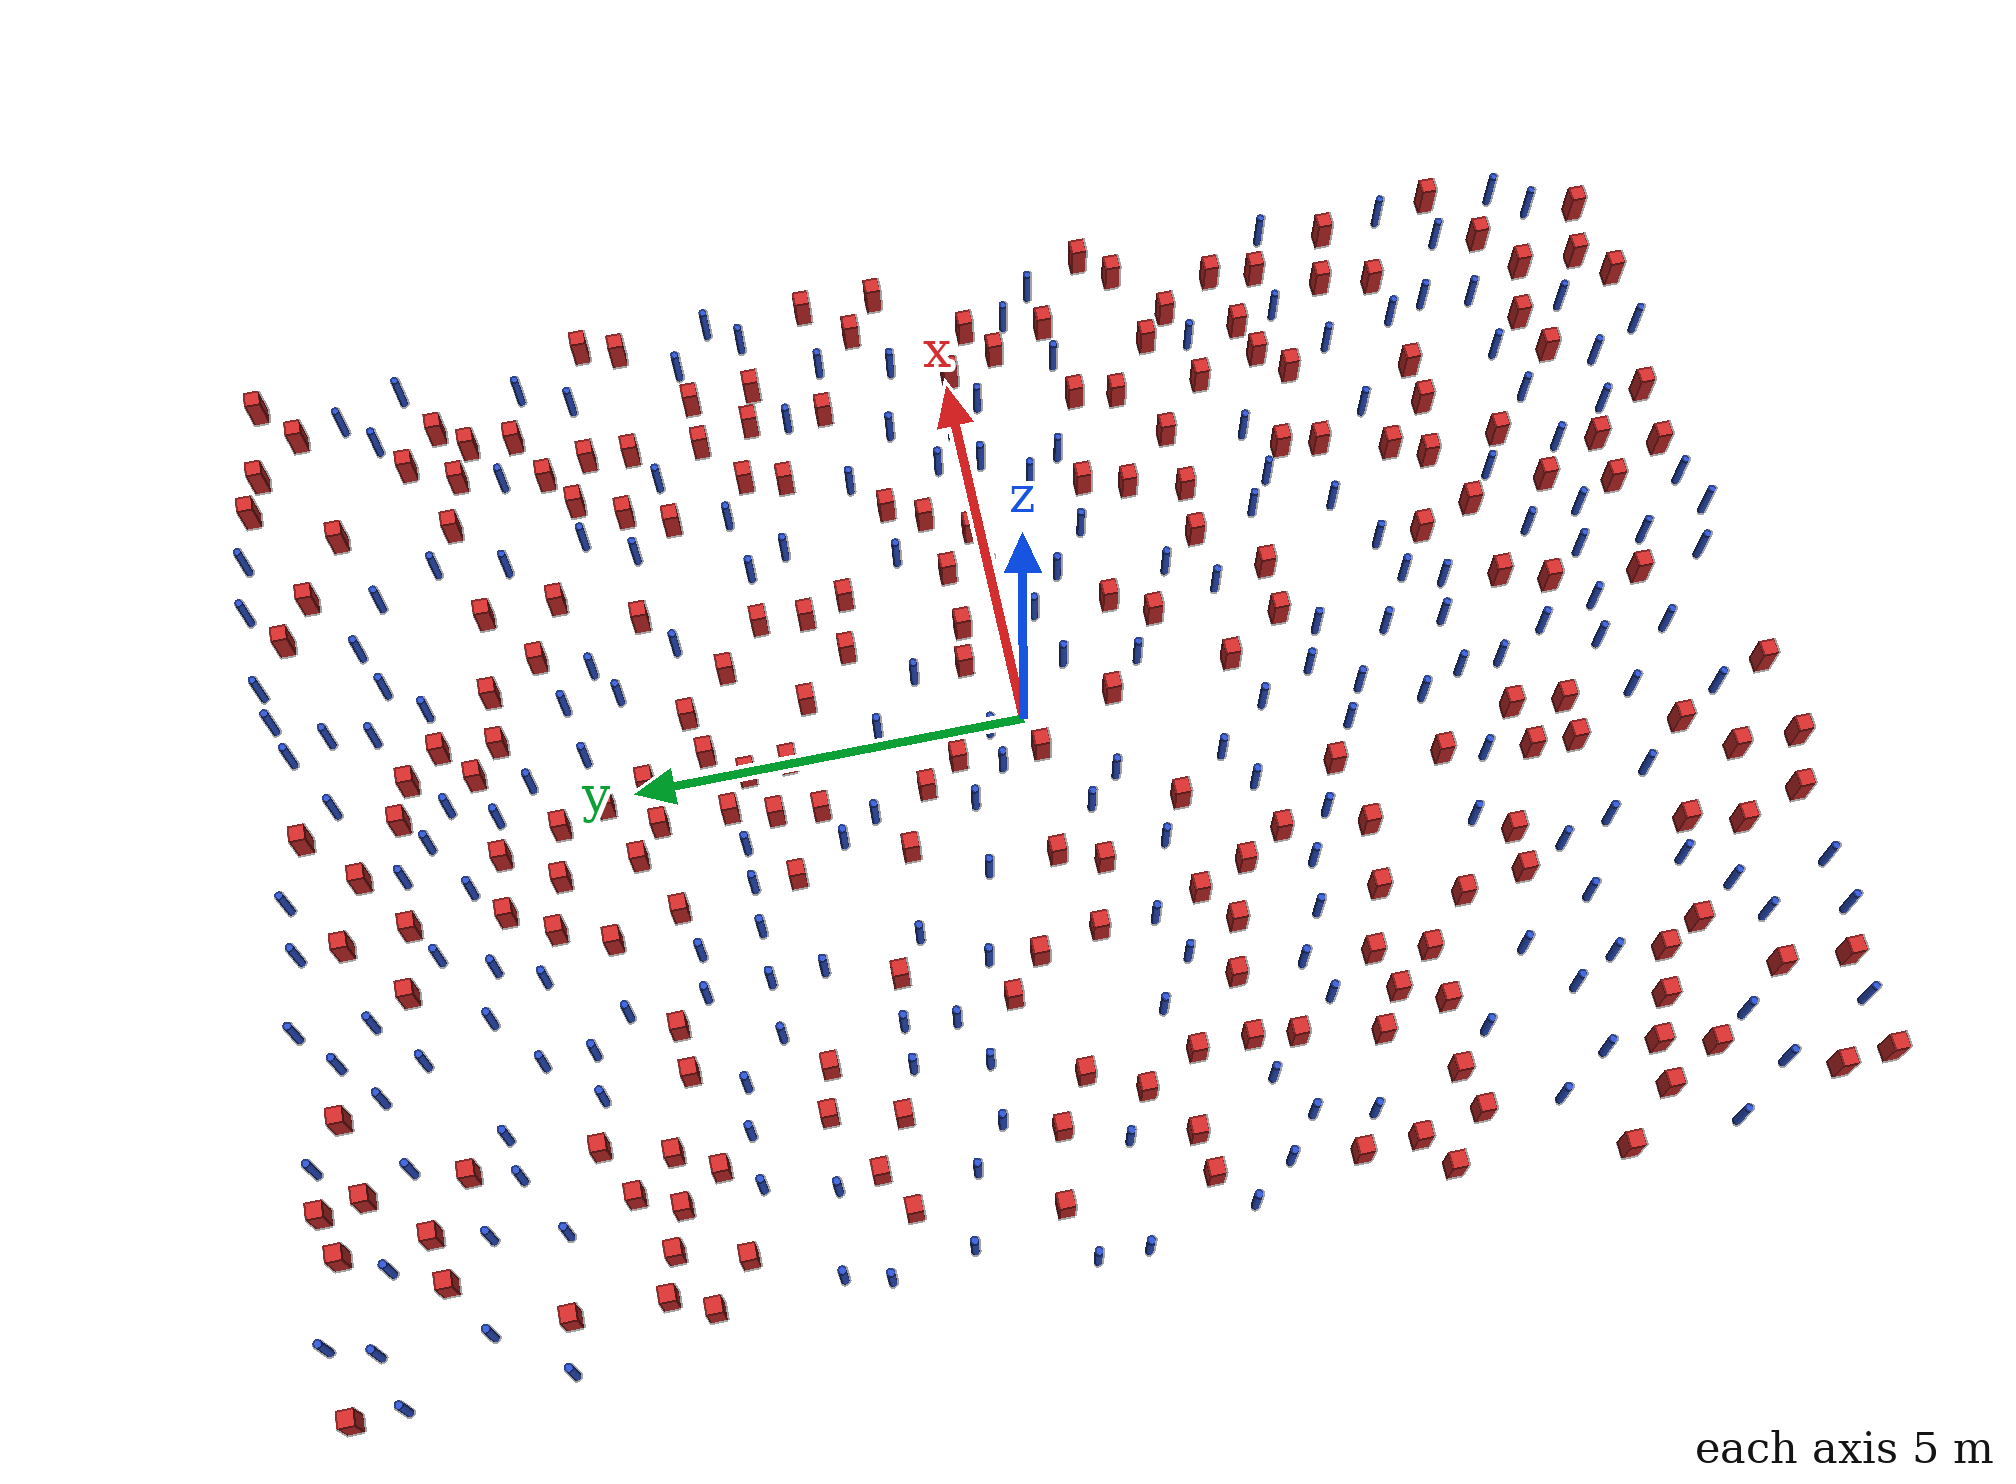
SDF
<sdf version="1.6">
  <model name="dense_90"><model name="pole_obstacle0">
  <static>true</static>
  <pose frame="">5.53012005391 1.63645903524 7.38925637345e-09 -8.471706928e-08 1.24976765134e-08 -1.74513093015e-07</pose>
  <link name="link">
  <pose frame="">0 0 0.3 0 -0 0</pose>
    <inertial>
      <mass>1</mass>
      <inertia>
        <ixx>0.145833</ixx>
        <ixy>0</ixy>
        <ixz>0</ixz>
        <iyy>0.145833</iyy>
        <iyz>0</iyz>
        <izz>0.125</izz>
      </inertia>
    </inertial>
    <collision name="collision">
      <geometry>
        <cylinder>
          <radius>0.05</radius>
          <length>.6</length>
        </cylinder>
      </geometry>
      <max_contacts>10</max_contacts>
      <surface>
        <contact>
          <ode/>
        </contact>
        <bounce/>
        <friction>
          <torsional>
            <ode/>
          </torsional>
          <ode/>
        </friction>
      </surface>
    </collision>
    <visual name="visual">
      <geometry>
        <cylinder>
          <radius>0.05</radius>
          <length>.6</length>
        </cylinder>
      </geometry>
      <material>
        <script>
          <name>Gazebo/Blue</name>
          <uri>file://media/materials/scripts/gazebo.material</uri>
        </script>
      </material>
    </visual>
    <self_collide>0</self_collide>
    <kinematic>0</kinematic>
  </link>
</model>
<model name="pole_obstacle1">
  <static>true</static>
  <pose frame="">1.57403197315 7.37901727268 7.38925637345e-09 -8.47170692799e-08 1.24976765033e-08 -1.74513093018e-07</pose>
  <link name="link">
  <pose frame="">0 0 0.3 0 -0 0</pose>
    <inertial>
      <mass>1</mass>
      <inertia>
        <ixx>0.145833</ixx>
        <ixy>0</ixy>
        <ixz>0</ixz>
        <iyy>0.145833</iyy>
        <iyz>0</iyz>
        <izz>0.125</izz>
      </inertia>
    </inertial>
    <collision name="collision">
      <geometry>
        <cylinder>
          <radius>0.05</radius>
          <length>.6</length>
        </cylinder>
      </geometry>
      <max_contacts>10</max_contacts>
      <surface>
        <contact>
          <ode/>
        </contact>
        <bounce/>
        <friction>
          <torsional>
            <ode/>
          </torsional>
          <ode/>
        </friction>
      </surface>
    </collision>
    <visual name="visual">
      <geometry>
        <cylinder>
          <radius>0.05</radius>
          <length>.6</length>
        </cylinder>
      </geometry>
      <material>
        <script>
          <name>Gazebo/Blue</name>
          <uri>file://media/materials/scripts/gazebo.material</uri>
        </script>
      </material>
    </visual>
    <self_collide>0</self_collide>
    <kinematic>0</kinematic>
  </link>
</model>
<model name="square_post_obstacle0">
  <static>true</static>
  <pose frame="">-3.1302615342 -7.7388249968 1.91545236811e-07 -7.35059704564e-06 1.12565212e-07 2.39332434364e-05</pose>
  <link name="link">
    <pose frame="">0 0 0.25 0 -0 0</pose>
    <inertial>
      <mass>100</mass>
      <inertia>
        <ixx>0.166667</ixx>
        <ixy>0</ixy>
        <ixz>0</ixz>
        <iyy>0.166667</iyy>
        <iyz>0</iyz>
        <izz>0.166667</izz>
      </inertia>
    </inertial>
    <collision name="collision">
      <geometry>
        <box>
          <size>.2 .2 .5</size>
        </box>
      </geometry>
      <max_contacts>10</max_contacts>
      <surface>
        <contact>
          <ode/>
        </contact>
        <bounce/>
        <friction>
          <torsional>
            <ode/>
          </torsional>
          <ode/>
        </friction>
      </surface>
    </collision>
    <visual name="visual">
      <geometry>
        <box>
          <size>.2 .2 .5</size>
        </box>
      </geometry>
      <material>
        <script>
          <name>Gazebo/Red</name>
          <uri>file://media/materials/scripts/gazebo.material</uri>
        </script>
      </material>
    </visual>
    <self_collide>0</self_collide>
    <kinematic>0</kinematic>
  </link>
</model>
<model name="square_post_obstacle1">
  <static>true</static>
  <pose frame="">5.05377496867 -2.75790804852 1.91545236811e-07 -7.35059704564e-06 1.12565212e-07 2.39332434364e-05</pose>
  <link name="link">
    <pose frame="">0 0 0.25 0 -0 0</pose>
    <inertial>
      <mass>100</mass>
      <inertia>
        <ixx>0.166667</ixx>
        <ixy>0</ixy>
        <ixz>0</ixz>
        <iyy>0.166667</iyy>
        <iyz>0</iyz>
        <izz>0.166667</izz>
      </inertia>
    </inertial>
    <collision name="collision">
      <geometry>
        <box>
          <size>.2 .2 .5</size>
        </box>
      </geometry>
      <max_contacts>10</max_contacts>
      <surface>
        <contact>
          <ode/>
        </contact>
        <bounce/>
        <friction>
          <torsional>
            <ode/>
          </torsional>
          <ode/>
        </friction>
      </surface>
    </collision>
    <visual name="visual">
      <geometry>
        <box>
          <size>.2 .2 .5</size>
        </box>
      </geometry>
      <material>
        <script>
          <name>Gazebo/Red</name>
          <uri>file://media/materials/scripts/gazebo.material</uri>
        </script>
      </material>
    </visual>
    <self_collide>0</self_collide>
    <kinematic>0</kinematic>
  </link>
</model>
<model name="pole_obstacle2">
  <static>true</static>
  <pose frame="">2.5913801027 8.11951139135 7.38925637345e-09 -8.47170692793e-08 1.24976764408e-08 -1.74513093041e-07</pose>
  <link name="link">
  <pose frame="">0 0 0.3 0 -0 0</pose>
    <inertial>
      <mass>1</mass>
      <inertia>
        <ixx>0.145833</ixx>
        <ixy>0</ixy>
        <ixz>0</ixz>
        <iyy>0.145833</iyy>
        <iyz>0</iyz>
        <izz>0.125</izz>
      </inertia>
    </inertial>
    <collision name="collision">
      <geometry>
        <cylinder>
          <radius>0.05</radius>
          <length>.6</length>
        </cylinder>
      </geometry>
      <max_contacts>10</max_contacts>
      <surface>
        <contact>
          <ode/>
        </contact>
        <bounce/>
        <friction>
          <torsional>
            <ode/>
          </torsional>
          <ode/>
        </friction>
      </surface>
    </collision>
    <visual name="visual">
      <geometry>
        <cylinder>
          <radius>0.05</radius>
          <length>.6</length>
        </cylinder>
      </geometry>
      <material>
        <script>
          <name>Gazebo/Blue</name>
          <uri>file://media/materials/scripts/gazebo.material</uri>
        </script>
      </material>
    </visual>
    <self_collide>0</self_collide>
    <kinematic>0</kinematic>
  </link>
</model>
<model name="pole_obstacle3">
  <static>true</static>
  <pose frame="">1.05795134384 -9.34788797899 7.38925637345e-09 -8.47170692798e-08 1.24976764881e-08 -1.74513093027e-07</pose>
  <link name="link">
  <pose frame="">0 0 0.3 0 -0 0</pose>
    <inertial>
      <mass>1</mass>
      <inertia>
        <ixx>0.145833</ixx>
        <ixy>0</ixy>
        <ixz>0</ixz>
        <iyy>0.145833</iyy>
        <iyz>0</iyz>
        <izz>0.125</izz>
      </inertia>
    </inertial>
    <collision name="collision">
      <geometry>
        <cylinder>
          <radius>0.05</radius>
          <length>.6</length>
        </cylinder>
      </geometry>
      <max_contacts>10</max_contacts>
      <surface>
        <contact>
          <ode/>
        </contact>
        <bounce/>
        <friction>
          <torsional>
            <ode/>
          </torsional>
          <ode/>
        </friction>
      </surface>
    </collision>
    <visual name="visual">
      <geometry>
        <cylinder>
          <radius>0.05</radius>
          <length>.6</length>
        </cylinder>
      </geometry>
      <material>
        <script>
          <name>Gazebo/Blue</name>
          <uri>file://media/materials/scripts/gazebo.material</uri>
        </script>
      </material>
    </visual>
    <self_collide>0</self_collide>
    <kinematic>0</kinematic>
  </link>
</model>
<model name="pole_obstacle4">
  <static>true</static>
  <pose frame="">-0.930717759357 7.12484259707 7.38925637345e-09 -8.471706928e-08 1.24976765086e-08 -1.74513093015e-07</pose>
  <link name="link">
  <pose frame="">0 0 0.3 0 -0 0</pose>
    <inertial>
      <mass>1</mass>
      <inertia>
        <ixx>0.145833</ixx>
        <ixy>0</ixy>
        <ixz>0</ixz>
        <iyy>0.145833</iyy>
        <iyz>0</iyz>
        <izz>0.125</izz>
      </inertia>
    </inertial>
    <collision name="collision">
      <geometry>
        <cylinder>
          <radius>0.05</radius>
          <length>.6</length>
        </cylinder>
      </geometry>
      <max_contacts>10</max_contacts>
      <surface>
        <contact>
          <ode/>
        </contact>
        <bounce/>
        <friction>
          <torsional>
            <ode/>
          </torsional>
          <ode/>
        </friction>
      </surface>
    </collision>
    <visual name="visual">
      <geometry>
        <cylinder>
          <radius>0.05</radius>
          <length>.6</length>
        </cylinder>
      </geometry>
      <material>
        <script>
          <name>Gazebo/Blue</name>
          <uri>file://media/materials/scripts/gazebo.material</uri>
        </script>
      </material>
    </visual>
    <self_collide>0</self_collide>
    <kinematic>0</kinematic>
  </link>
</model>
<model name="pole_obstacle5">
  <static>true</static>
  <pose frame="">-5.92422427441 -2.99336722222 7.38925637345e-09 -8.47170692798e-08 1.24976764937e-08 -1.74513093023e-07</pose>
  <link name="link">
  <pose frame="">0 0 0.3 0 -0 0</pose>
    <inertial>
      <mass>1</mass>
      <inertia>
        <ixx>0.145833</ixx>
        <ixy>0</ixy>
        <ixz>0</ixz>
        <iyy>0.145833</iyy>
        <iyz>0</iyz>
        <izz>0.125</izz>
      </inertia>
    </inertial>
    <collision name="collision">
      <geometry>
        <cylinder>
          <radius>0.05</radius>
          <length>.6</length>
        </cylinder>
      </geometry>
      <max_contacts>10</max_contacts>
      <surface>
        <contact>
          <ode/>
        </contact>
        <bounce/>
        <friction>
          <torsional>
            <ode/>
          </torsional>
          <ode/>
        </friction>
      </surface>
    </collision>
    <visual name="visual">
      <geometry>
        <cylinder>
          <radius>0.05</radius>
          <length>.6</length>
        </cylinder>
      </geometry>
      <material>
        <script>
          <name>Gazebo/Blue</name>
          <uri>file://media/materials/scripts/gazebo.material</uri>
        </script>
      </material>
    </visual>
    <self_collide>0</self_collide>
    <kinematic>0</kinematic>
  </link>
</model>
<model name="pole_obstacle6">
  <static>true</static>
  <pose frame="">6.13150018273 -1.35139949325 7.38925637345e-09 -8.471706928e-08 1.24976765134e-08 -1.74513093015e-07</pose>
  <link name="link">
  <pose frame="">0 0 0.3 0 -0 0</pose>
    <inertial>
      <mass>1</mass>
      <inertia>
        <ixx>0.145833</ixx>
        <ixy>0</ixy>
        <ixz>0</ixz>
        <iyy>0.145833</iyy>
        <iyz>0</iyz>
        <izz>0.125</izz>
      </inertia>
    </inertial>
    <collision name="collision">
      <geometry>
        <cylinder>
          <radius>0.05</radius>
          <length>.6</length>
        </cylinder>
      </geometry>
      <max_contacts>10</max_contacts>
      <surface>
        <contact>
          <ode/>
        </contact>
        <bounce/>
        <friction>
          <torsional>
            <ode/>
          </torsional>
          <ode/>
        </friction>
      </surface>
    </collision>
    <visual name="visual">
      <geometry>
        <cylinder>
          <radius>0.05</radius>
          <length>.6</length>
        </cylinder>
      </geometry>
      <material>
        <script>
          <name>Gazebo/Blue</name>
          <uri>file://media/materials/scripts/gazebo.material</uri>
        </script>
      </material>
    </visual>
    <self_collide>0</self_collide>
    <kinematic>0</kinematic>
  </link>
</model>
<model name="square_post_obstacle2">
  <static>true</static>
  <pose frame="">-1.81622782125 -8.08868260093 1.91545236811e-07 -7.35059704564e-06 1.12565212e-07 2.39332434364e-05</pose>
  <link name="link">
    <pose frame="">0 0 0.25 0 -0 0</pose>
    <inertial>
      <mass>100</mass>
      <inertia>
        <ixx>0.166667</ixx>
        <ixy>0</ixy>
        <ixz>0</ixz>
        <iyy>0.166667</iyy>
        <iyz>0</iyz>
        <izz>0.166667</izz>
      </inertia>
    </inertial>
    <collision name="collision">
      <geometry>
        <box>
          <size>.2 .2 .5</size>
        </box>
      </geometry>
      <max_contacts>10</max_contacts>
      <surface>
        <contact>
          <ode/>
        </contact>
        <bounce/>
        <friction>
          <torsional>
            <ode/>
          </torsional>
          <ode/>
        </friction>
      </surface>
    </collision>
    <visual name="visual">
      <geometry>
        <box>
          <size>.2 .2 .5</size>
        </box>
      </geometry>
      <material>
        <script>
          <name>Gazebo/Red</name>
          <uri>file://media/materials/scripts/gazebo.material</uri>
        </script>
      </material>
    </visual>
    <self_collide>0</self_collide>
    <kinematic>0</kinematic>
  </link>
</model>
<model name="square_post_obstacle3">
  <static>true</static>
  <pose frame="">5.90210192159 8.586843425 1.91545236811e-07 -7.35059704564e-06 1.12565212e-07 2.39332434364e-05</pose>
  <link name="link">
    <pose frame="">0 0 0.25 0 -0 0</pose>
    <inertial>
      <mass>100</mass>
      <inertia>
        <ixx>0.166667</ixx>
        <ixy>0</ixy>
        <ixz>0</ixz>
        <iyy>0.166667</iyy>
        <iyz>0</iyz>
        <izz>0.166667</izz>
      </inertia>
    </inertial>
    <collision name="collision">
      <geometry>
        <box>
          <size>.2 .2 .5</size>
        </box>
      </geometry>
      <max_contacts>10</max_contacts>
      <surface>
        <contact>
          <ode/>
        </contact>
        <bounce/>
        <friction>
          <torsional>
            <ode/>
          </torsional>
          <ode/>
        </friction>
      </surface>
    </collision>
    <visual name="visual">
      <geometry>
        <box>
          <size>.2 .2 .5</size>
        </box>
      </geometry>
      <material>
        <script>
          <name>Gazebo/Red</name>
          <uri>file://media/materials/scripts/gazebo.material</uri>
        </script>
      </material>
    </visual>
    <self_collide>0</self_collide>
    <kinematic>0</kinematic>
  </link>
</model>
<model name="square_post_obstacle4">
  <static>true</static>
  <pose frame="">5.90780278846 -9.03052146955 1.91545236811e-07 -7.35059704564e-06 1.12565212e-07 2.39332434364e-05</pose>
  <link name="link">
    <pose frame="">0 0 0.25 0 -0 0</pose>
    <inertial>
      <mass>100</mass>
      <inertia>
        <ixx>0.166667</ixx>
        <ixy>0</ixy>
        <ixz>0</ixz>
        <iyy>0.166667</iyy>
        <iyz>0</iyz>
        <izz>0.166667</izz>
      </inertia>
    </inertial>
    <collision name="collision">
      <geometry>
        <box>
          <size>.2 .2 .5</size>
        </box>
      </geometry>
      <max_contacts>10</max_contacts>
      <surface>
        <contact>
          <ode/>
        </contact>
        <bounce/>
        <friction>
          <torsional>
            <ode/>
          </torsional>
          <ode/>
        </friction>
      </surface>
    </collision>
    <visual name="visual">
      <geometry>
        <box>
          <size>.2 .2 .5</size>
        </box>
      </geometry>
      <material>
        <script>
          <name>Gazebo/Red</name>
          <uri>file://media/materials/scripts/gazebo.material</uri>
        </script>
      </material>
    </visual>
    <self_collide>0</self_collide>
    <kinematic>0</kinematic>
  </link>
</model>
<model name="pole_obstacle7">
  <static>true</static>
  <pose frame="">3.5924293416 5.09383726458 7.38925637345e-09 -8.47170692798e-08 1.24976765033e-08 -1.74513093019e-07</pose>
  <link name="link">
  <pose frame="">0 0 0.3 0 -0 0</pose>
    <inertial>
      <mass>1</mass>
      <inertia>
        <ixx>0.145833</ixx>
        <ixy>0</ixy>
        <ixz>0</ixz>
        <iyy>0.145833</iyy>
        <iyz>0</iyz>
        <izz>0.125</izz>
      </inertia>
    </inertial>
    <collision name="collision">
      <geometry>
        <cylinder>
          <radius>0.05</radius>
          <length>.6</length>
        </cylinder>
      </geometry>
      <max_contacts>10</max_contacts>
      <surface>
        <contact>
          <ode/>
        </contact>
        <bounce/>
        <friction>
          <torsional>
            <ode/>
          </torsional>
          <ode/>
        </friction>
      </surface>
    </collision>
    <visual name="visual">
      <geometry>
        <cylinder>
          <radius>0.05</radius>
          <length>.6</length>
        </cylinder>
      </geometry>
      <material>
        <script>
          <name>Gazebo/Blue</name>
          <uri>file://media/materials/scripts/gazebo.material</uri>
        </script>
      </material>
    </visual>
    <self_collide>0</self_collide>
    <kinematic>0</kinematic>
  </link>
</model>
<model name="pole_obstacle8">
  <static>true</static>
  <pose frame="">5.87844196095 3.49214916808 7.38925637345e-09 -8.47170692798e-08 1.24976764937e-08 -1.74513093023e-07</pose>
  <link name="link">
  <pose frame="">0 0 0.3 0 -0 0</pose>
    <inertial>
      <mass>1</mass>
      <inertia>
        <ixx>0.145833</ixx>
        <ixy>0</ixy>
        <ixz>0</ixz>
        <iyy>0.145833</iyy>
        <iyz>0</iyz>
        <izz>0.125</izz>
      </inertia>
    </inertial>
    <collision name="collision">
      <geometry>
        <cylinder>
          <radius>0.05</radius>
          <length>.6</length>
        </cylinder>
      </geometry>
      <max_contacts>10</max_contacts>
      <surface>
        <contact>
          <ode/>
        </contact>
        <bounce/>
        <friction>
          <torsional>
            <ode/>
          </torsional>
          <ode/>
        </friction>
      </surface>
    </collision>
    <visual name="visual">
      <geometry>
        <cylinder>
          <radius>0.05</radius>
          <length>.6</length>
        </cylinder>
      </geometry>
      <material>
        <script>
          <name>Gazebo/Blue</name>
          <uri>file://media/materials/scripts/gazebo.material</uri>
        </script>
      </material>
    </visual>
    <self_collide>0</self_collide>
    <kinematic>0</kinematic>
  </link>
</model>
<model name="square_post_obstacle5">
  <static>true</static>
  <pose frame="">-5.42175333272 2.87260005958 1.91545236811e-07 -7.35059704564e-06 1.12565212e-07 2.39332434364e-05</pose>
  <link name="link">
    <pose frame="">0 0 0.25 0 -0 0</pose>
    <inertial>
      <mass>100</mass>
      <inertia>
        <ixx>0.166667</ixx>
        <ixy>0</ixy>
        <ixz>0</ixz>
        <iyy>0.166667</iyy>
        <iyz>0</iyz>
        <izz>0.166667</izz>
      </inertia>
    </inertial>
    <collision name="collision">
      <geometry>
        <box>
          <size>.2 .2 .5</size>
        </box>
      </geometry>
      <max_contacts>10</max_contacts>
      <surface>
        <contact>
          <ode/>
        </contact>
        <bounce/>
        <friction>
          <torsional>
            <ode/>
          </torsional>
          <ode/>
        </friction>
      </surface>
    </collision>
    <visual name="visual">
      <geometry>
        <box>
          <size>.2 .2 .5</size>
        </box>
      </geometry>
      <material>
        <script>
          <name>Gazebo/Red</name>
          <uri>file://media/materials/scripts/gazebo.material</uri>
        </script>
      </material>
    </visual>
    <self_collide>0</self_collide>
    <kinematic>0</kinematic>
  </link>
</model>
<model name="square_post_obstacle6">
  <static>true</static>
  <pose frame="">-1.77363090694 -6.15652895822 1.91545236811e-07 -7.35059704564e-06 1.12565212e-07 2.39332434364e-05</pose>
  <link name="link">
    <pose frame="">0 0 0.25 0 -0 0</pose>
    <inertial>
      <mass>100</mass>
      <inertia>
        <ixx>0.166667</ixx>
        <ixy>0</ixy>
        <ixz>0</ixz>
        <iyy>0.166667</iyy>
        <iyz>0</iyz>
        <izz>0.166667</izz>
      </inertia>
    </inertial>
    <collision name="collision">
      <geometry>
        <box>
          <size>.2 .2 .5</size>
        </box>
      </geometry>
      <max_contacts>10</max_contacts>
      <surface>
        <contact>
          <ode/>
        </contact>
        <bounce/>
        <friction>
          <torsional>
            <ode/>
          </torsional>
          <ode/>
        </friction>
      </surface>
    </collision>
    <visual name="visual">
      <geometry>
        <box>
          <size>.2 .2 .5</size>
        </box>
      </geometry>
      <material>
        <script>
          <name>Gazebo/Red</name>
          <uri>file://media/materials/scripts/gazebo.material</uri>
        </script>
      </material>
    </visual>
    <self_collide>0</self_collide>
    <kinematic>0</kinematic>
  </link>
</model>
<model name="square_post_obstacle7">
  <static>true</static>
  <pose frame="">0.0717950030829 -1.15648471088 1.91545236811e-07 -7.35059704564e-06 1.12565212e-07 2.39332434364e-05</pose>
  <link name="link">
    <pose frame="">0 0 0.25 0 -0 0</pose>
    <inertial>
      <mass>100</mass>
      <inertia>
        <ixx>0.166667</ixx>
        <ixy>0</ixy>
        <ixz>0</ixz>
        <iyy>0.166667</iyy>
        <iyz>0</iyz>
        <izz>0.166667</izz>
      </inertia>
    </inertial>
    <collision name="collision">
      <geometry>
        <box>
          <size>.2 .2 .5</size>
        </box>
      </geometry>
      <max_contacts>10</max_contacts>
      <surface>
        <contact>
          <ode/>
        </contact>
        <bounce/>
        <friction>
          <torsional>
            <ode/>
          </torsional>
          <ode/>
        </friction>
      </surface>
    </collision>
    <visual name="visual">
      <geometry>
        <box>
          <size>.2 .2 .5</size>
        </box>
      </geometry>
      <material>
        <script>
          <name>Gazebo/Red</name>
          <uri>file://media/materials/scripts/gazebo.material</uri>
        </script>
      </material>
    </visual>
    <self_collide>0</self_collide>
    <kinematic>0</kinematic>
  </link>
</model>
<model name="pole_obstacle9">
  <static>true</static>
  <pose frame="">6.12824490941 2.60409271185 7.38925637345e-09 -8.47170692798e-08 1.24976764937e-08 -1.74513093023e-07</pose>
  <link name="link">
  <pose frame="">0 0 0.3 0 -0 0</pose>
    <inertial>
      <mass>1</mass>
      <inertia>
        <ixx>0.145833</ixx>
        <ixy>0</ixy>
        <ixz>0</ixz>
        <iyy>0.145833</iyy>
        <iyz>0</iyz>
        <izz>0.125</izz>
      </inertia>
    </inertial>
    <collision name="collision">
      <geometry>
        <cylinder>
          <radius>0.05</radius>
          <length>.6</length>
        </cylinder>
      </geometry>
      <max_contacts>10</max_contacts>
      <surface>
        <contact>
          <ode/>
        </contact>
        <bounce/>
        <friction>
          <torsional>
            <ode/>
          </torsional>
          <ode/>
        </friction>
      </surface>
    </collision>
    <visual name="visual">
      <geometry>
        <cylinder>
          <radius>0.05</radius>
          <length>.6</length>
        </cylinder>
      </geometry>
      <material>
        <script>
          <name>Gazebo/Blue</name>
          <uri>file://media/materials/scripts/gazebo.material</uri>
        </script>
      </material>
    </visual>
    <self_collide>0</self_collide>
    <kinematic>0</kinematic>
  </link>
</model>
<model name="pole_obstacle10">
  <static>true</static>
  <pose frame="">-6.90614893159 -7.19268532461 7.38925637345e-09 -8.47170692796e-08 1.24976764786e-08 -1.74513093032e-07</pose>
  <link name="link">
  <pose frame="">0 0 0.3 0 -0 0</pose>
    <inertial>
      <mass>1</mass>
      <inertia>
        <ixx>0.145833</ixx>
        <ixy>0</ixy>
        <ixz>0</ixz>
        <iyy>0.145833</iyy>
        <iyz>0</iyz>
        <izz>0.125</izz>
      </inertia>
    </inertial>
    <collision name="collision">
      <geometry>
        <cylinder>
          <radius>0.05</radius>
          <length>.6</length>
        </cylinder>
      </geometry>
      <max_contacts>10</max_contacts>
      <surface>
        <contact>
          <ode/>
        </contact>
        <bounce/>
        <friction>
          <torsional>
            <ode/>
          </torsional>
          <ode/>
        </friction>
      </surface>
    </collision>
    <visual name="visual">
      <geometry>
        <cylinder>
          <radius>0.05</radius>
          <length>.6</length>
        </cylinder>
      </geometry>
      <material>
        <script>
          <name>Gazebo/Blue</name>
          <uri>file://media/materials/scripts/gazebo.material</uri>
        </script>
      </material>
    </visual>
    <self_collide>0</self_collide>
    <kinematic>0</kinematic>
  </link>
</model>
<model name="pole_obstacle11">
  <static>true</static>
  <pose frame="">0.533642133794 5.50967781415 7.38925637345e-09 -8.47170692799e-08 1.24976765073e-08 -1.74513093015e-07</pose>
  <link name="link">
  <pose frame="">0 0 0.3 0 -0 0</pose>
    <inertial>
      <mass>1</mass>
      <inertia>
        <ixx>0.145833</ixx>
        <ixy>0</ixy>
        <ixz>0</ixz>
        <iyy>0.145833</iyy>
        <iyz>0</iyz>
        <izz>0.125</izz>
      </inertia>
    </inertial>
    <collision name="collision">
      <geometry>
        <cylinder>
          <radius>0.05</radius>
          <length>.6</length>
        </cylinder>
      </geometry>
      <max_contacts>10</max_contacts>
      <surface>
        <contact>
          <ode/>
        </contact>
        <bounce/>
        <friction>
          <torsional>
            <ode/>
          </torsional>
          <ode/>
        </friction>
      </surface>
    </collision>
    <visual name="visual">
      <geometry>
        <cylinder>
          <radius>0.05</radius>
          <length>.6</length>
        </cylinder>
      </geometry>
      <material>
        <script>
          <name>Gazebo/Blue</name>
          <uri>file://media/materials/scripts/gazebo.material</uri>
        </script>
      </material>
    </visual>
    <self_collide>0</self_collide>
    <kinematic>0</kinematic>
  </link>
</model>
<model name="pole_obstacle12">
  <static>true</static>
  <pose frame="">-4.05530180549 4.23103096723 7.38925637345e-09 -8.47170692796e-08 1.24976764786e-08 -1.74513093032e-07</pose>
  <link name="link">
  <pose frame="">0 0 0.3 0 -0 0</pose>
    <inertial>
      <mass>1</mass>
      <inertia>
        <ixx>0.145833</ixx>
        <ixy>0</ixy>
        <ixz>0</ixz>
        <iyy>0.145833</iyy>
        <iyz>0</iyz>
        <izz>0.125</izz>
      </inertia>
    </inertial>
    <collision name="collision">
      <geometry>
        <cylinder>
          <radius>0.05</radius>
          <length>.6</length>
        </cylinder>
      </geometry>
      <max_contacts>10</max_contacts>
      <surface>
        <contact>
          <ode/>
        </contact>
        <bounce/>
        <friction>
          <torsional>
            <ode/>
          </torsional>
          <ode/>
        </friction>
      </surface>
    </collision>
    <visual name="visual">
      <geometry>
        <cylinder>
          <radius>0.05</radius>
          <length>.6</length>
        </cylinder>
      </geometry>
      <material>
        <script>
          <name>Gazebo/Blue</name>
          <uri>file://media/materials/scripts/gazebo.material</uri>
        </script>
      </material>
    </visual>
    <self_collide>0</self_collide>
    <kinematic>0</kinematic>
  </link>
</model>
<model name="square_post_obstacle8">
  <static>true</static>
  <pose frame="">3.11087227701 -1.44760078272 1.91545236811e-07 -7.35059704564e-06 1.12565212e-07 2.39332434364e-05</pose>
  <link name="link">
    <pose frame="">0 0 0.25 0 -0 0</pose>
    <inertial>
      <mass>100</mass>
      <inertia>
        <ixx>0.166667</ixx>
        <ixy>0</ixy>
        <ixz>0</ixz>
        <iyy>0.166667</iyy>
        <iyz>0</iyz>
        <izz>0.166667</izz>
      </inertia>
    </inertial>
    <collision name="collision">
      <geometry>
        <box>
          <size>.2 .2 .5</size>
        </box>
      </geometry>
      <max_contacts>10</max_contacts>
      <surface>
        <contact>
          <ode/>
        </contact>
        <bounce/>
        <friction>
          <torsional>
            <ode/>
          </torsional>
          <ode/>
        </friction>
      </surface>
    </collision>
    <visual name="visual">
      <geometry>
        <box>
          <size>.2 .2 .5</size>
        </box>
      </geometry>
      <material>
        <script>
          <name>Gazebo/Red</name>
          <uri>file://media/materials/scripts/gazebo.material</uri>
        </script>
      </material>
    </visual>
    <self_collide>0</self_collide>
    <kinematic>0</kinematic>
  </link>
</model>
<model name="square_post_obstacle9">
  <static>true</static>
  <pose frame="">-3.29297835384 -8.43089874461 1.91545236811e-07 -7.35059704564e-06 1.12565212e-07 2.39332434364e-05</pose>
  <link name="link">
    <pose frame="">0 0 0.25 0 -0 0</pose>
    <inertial>
      <mass>100</mass>
      <inertia>
        <ixx>0.166667</ixx>
        <ixy>0</ixy>
        <ixz>0</ixz>
        <iyy>0.166667</iyy>
        <iyz>0</iyz>
        <izz>0.166667</izz>
      </inertia>
    </inertial>
    <collision name="collision">
      <geometry>
        <box>
          <size>.2 .2 .5</size>
        </box>
      </geometry>
      <max_contacts>10</max_contacts>
      <surface>
        <contact>
          <ode/>
        </contact>
        <bounce/>
        <friction>
          <torsional>
            <ode/>
          </torsional>
          <ode/>
        </friction>
      </surface>
    </collision>
    <visual name="visual">
      <geometry>
        <box>
          <size>.2 .2 .5</size>
        </box>
      </geometry>
      <material>
        <script>
          <name>Gazebo/Red</name>
          <uri>file://media/materials/scripts/gazebo.material</uri>
        </script>
      </material>
    </visual>
    <self_collide>0</self_collide>
    <kinematic>0</kinematic>
  </link>
</model>
<model name="pole_obstacle13">
  <static>true</static>
  <pose frame="">6.3429446586 -7.94124706151 7.38925637345e-09 -8.47170692796e-08 1.24976764786e-08 -1.74513093032e-07</pose>
  <link name="link">
  <pose frame="">0 0 0.3 0 -0 0</pose>
    <inertial>
      <mass>1</mass>
      <inertia>
        <ixx>0.145833</ixx>
        <ixy>0</ixy>
        <ixz>0</ixz>
        <iyy>0.145833</iyy>
        <iyz>0</iyz>
        <izz>0.125</izz>
      </inertia>
    </inertial>
    <collision name="collision">
      <geometry>
        <cylinder>
          <radius>0.05</radius>
          <length>.6</length>
        </cylinder>
      </geometry>
      <max_contacts>10</max_contacts>
      <surface>
        <contact>
          <ode/>
        </contact>
        <bounce/>
        <friction>
          <torsional>
            <ode/>
          </torsional>
          <ode/>
        </friction>
      </surface>
    </collision>
    <visual name="visual">
      <geometry>
        <cylinder>
          <radius>0.05</radius>
          <length>.6</length>
        </cylinder>
      </geometry>
      <material>
        <script>
          <name>Gazebo/Blue</name>
          <uri>file://media/materials/scripts/gazebo.material</uri>
        </script>
      </material>
    </visual>
    <self_collide>0</self_collide>
    <kinematic>0</kinematic>
  </link>
</model>
<model name="square_post_obstacle10">
  <static>true</static>
  <pose frame="">0.653097989824 -6.43755796853 1.91545236811e-07 -7.35059704564e-06 1.12565212e-07 2.39332434364e-05</pose>
  <link name="link">
    <pose frame="">0 0 0.25 0 -0 0</pose>
    <inertial>
      <mass>100</mass>
      <inertia>
        <ixx>0.166667</ixx>
        <ixy>0</ixy>
        <ixz>0</ixz>
        <iyy>0.166667</iyy>
        <iyz>0</iyz>
        <izz>0.166667</izz>
      </inertia>
    </inertial>
    <collision name="collision">
      <geometry>
        <box>
          <size>.2 .2 .5</size>
        </box>
      </geometry>
      <max_contacts>10</max_contacts>
      <surface>
        <contact>
          <ode/>
        </contact>
        <bounce/>
        <friction>
          <torsional>
            <ode/>
          </torsional>
          <ode/>
        </friction>
      </surface>
    </collision>
    <visual name="visual">
      <geometry>
        <box>
          <size>.2 .2 .5</size>
        </box>
      </geometry>
      <material>
        <script>
          <name>Gazebo/Red</name>
          <uri>file://media/materials/scripts/gazebo.material</uri>
        </script>
      </material>
    </visual>
    <self_collide>0</self_collide>
    <kinematic>0</kinematic>
  </link>
</model>
<model name="square_post_obstacle11">
  <static>true</static>
  <pose frame="">3.62025959342 3.93356187198 1.91545236811e-07 -7.35059704564e-06 1.12565212e-07 2.39332434364e-05</pose>
  <link name="link">
    <pose frame="">0 0 0.25 0 -0 0</pose>
    <inertial>
      <mass>100</mass>
      <inertia>
        <ixx>0.166667</ixx>
        <ixy>0</ixy>
        <ixz>0</ixz>
        <iyy>0.166667</iyy>
        <iyz>0</iyz>
        <izz>0.166667</izz>
      </inertia>
    </inertial>
    <collision name="collision">
      <geometry>
        <box>
          <size>.2 .2 .5</size>
        </box>
      </geometry>
      <max_contacts>10</max_contacts>
      <surface>
        <contact>
          <ode/>
        </contact>
        <bounce/>
        <friction>
          <torsional>
            <ode/>
          </torsional>
          <ode/>
        </friction>
      </surface>
    </collision>
    <visual name="visual">
      <geometry>
        <box>
          <size>.2 .2 .5</size>
        </box>
      </geometry>
      <material>
        <script>
          <name>Gazebo/Red</name>
          <uri>file://media/materials/scripts/gazebo.material</uri>
        </script>
      </material>
    </visual>
    <self_collide>0</self_collide>
    <kinematic>0</kinematic>
  </link>
</model>
<model name="pole_obstacle14">
  <static>true</static>
  <pose frame="">-1.03202337252 -2.32573109386 7.38925637345e-09 -8.47170692799e-08 1.24976765076e-08 -1.74513093016e-07</pose>
  <link name="link">
  <pose frame="">0 0 0.3 0 -0 0</pose>
    <inertial>
      <mass>1</mass>
      <inertia>
        <ixx>0.145833</ixx>
        <ixy>0</ixy>
        <ixz>0</ixz>
        <iyy>0.145833</iyy>
        <iyz>0</iyz>
        <izz>0.125</izz>
      </inertia>
    </inertial>
    <collision name="collision">
      <geometry>
        <cylinder>
          <radius>0.05</radius>
          <length>.6</length>
        </cylinder>
      </geometry>
      <max_contacts>10</max_contacts>
      <surface>
        <contact>
          <ode/>
        </contact>
        <bounce/>
        <friction>
          <torsional>
            <ode/>
          </torsional>
          <ode/>
        </friction>
      </surface>
    </collision>
    <visual name="visual">
      <geometry>
        <cylinder>
          <radius>0.05</radius>
          <length>.6</length>
        </cylinder>
      </geometry>
      <material>
        <script>
          <name>Gazebo/Blue</name>
          <uri>file://media/materials/scripts/gazebo.material</uri>
        </script>
      </material>
    </visual>
    <self_collide>0</self_collide>
    <kinematic>0</kinematic>
  </link>
</model>
<model name="pole_obstacle15">
  <static>true</static>
  <pose frame="">-4.03835698467 -8.03222469664 7.38925637345e-09 -8.47170692796e-08 1.24976764752e-08 -1.74513093036e-07</pose>
  <link name="link">
  <pose frame="">0 0 0.3 0 -0 0</pose>
    <inertial>
      <mass>1</mass>
      <inertia>
        <ixx>0.145833</ixx>
        <ixy>0</ixy>
        <ixz>0</ixz>
        <iyy>0.145833</iyy>
        <iyz>0</iyz>
        <izz>0.125</izz>
      </inertia>
    </inertial>
    <collision name="collision">
      <geometry>
        <cylinder>
          <radius>0.05</radius>
          <length>.6</length>
        </cylinder>
      </geometry>
      <max_contacts>10</max_contacts>
      <surface>
        <contact>
          <ode/>
        </contact>
        <bounce/>
        <friction>
          <torsional>
            <ode/>
          </torsional>
          <ode/>
        </friction>
      </surface>
    </collision>
    <visual name="visual">
      <geometry>
        <cylinder>
          <radius>0.05</radius>
          <length>.6</length>
        </cylinder>
      </geometry>
      <material>
        <script>
          <name>Gazebo/Blue</name>
          <uri>file://media/materials/scripts/gazebo.material</uri>
        </script>
      </material>
    </visual>
    <self_collide>0</self_collide>
    <kinematic>0</kinematic>
  </link>
</model>
<model name="square_post_obstacle12">
  <static>true</static>
  <pose frame="">-4.55918763524 9.36100081865 1.91545236811e-07 -7.35059704564e-06 1.12565212e-07 2.39332434364e-05</pose>
  <link name="link">
    <pose frame="">0 0 0.25 0 -0 0</pose>
    <inertial>
      <mass>100</mass>
      <inertia>
        <ixx>0.166667</ixx>
        <ixy>0</ixy>
        <ixz>0</ixz>
        <iyy>0.166667</iyy>
        <iyz>0</iyz>
        <izz>0.166667</izz>
      </inertia>
    </inertial>
    <collision name="collision">
      <geometry>
        <box>
          <size>.2 .2 .5</size>
        </box>
      </geometry>
      <max_contacts>10</max_contacts>
      <surface>
        <contact>
          <ode/>
        </contact>
        <bounce/>
        <friction>
          <torsional>
            <ode/>
          </torsional>
          <ode/>
        </friction>
      </surface>
    </collision>
    <visual name="visual">
      <geometry>
        <box>
          <size>.2 .2 .5</size>
        </box>
      </geometry>
      <material>
        <script>
          <name>Gazebo/Red</name>
          <uri>file://media/materials/scripts/gazebo.material</uri>
        </script>
      </material>
    </visual>
    <self_collide>0</self_collide>
    <kinematic>0</kinematic>
  </link>
</model>
<model name="pole_obstacle16">
  <static>true</static>
  <pose frame="">-0.0589049012718 6.68679805793 7.38925637345e-09 -8.47170692799e-08 1.24976765086e-08 -1.74513093017e-07</pose>
  <link name="link">
  <pose frame="">0 0 0.3 0 -0 0</pose>
    <inertial>
      <mass>1</mass>
      <inertia>
        <ixx>0.145833</ixx>
        <ixy>0</ixy>
        <ixz>0</ixz>
        <iyy>0.145833</iyy>
        <iyz>0</iyz>
        <izz>0.125</izz>
      </inertia>
    </inertial>
    <collision name="collision">
      <geometry>
        <cylinder>
          <radius>0.05</radius>
          <length>.6</length>
        </cylinder>
      </geometry>
      <max_contacts>10</max_contacts>
      <surface>
        <contact>
          <ode/>
        </contact>
        <bounce/>
        <friction>
          <torsional>
            <ode/>
          </torsional>
          <ode/>
        </friction>
      </surface>
    </collision>
    <visual name="visual">
      <geometry>
        <cylinder>
          <radius>0.05</radius>
          <length>.6</length>
        </cylinder>
      </geometry>
      <material>
        <script>
          <name>Gazebo/Blue</name>
          <uri>file://media/materials/scripts/gazebo.material</uri>
        </script>
      </material>
    </visual>
    <self_collide>0</self_collide>
    <kinematic>0</kinematic>
  </link>
</model>
<model name="pole_obstacle17">
  <static>true</static>
  <pose frame="">0.203960969138 -5.54850880262 7.38925637345e-09 -8.471706928e-08 1.24976765124e-08 -1.74513093014e-07</pose>
  <link name="link">
  <pose frame="">0 0 0.3 0 -0 0</pose>
    <inertial>
      <mass>1</mass>
      <inertia>
        <ixx>0.145833</ixx>
        <ixy>0</ixy>
        <ixz>0</ixz>
        <iyy>0.145833</iyy>
        <iyz>0</iyz>
        <izz>0.125</izz>
      </inertia>
    </inertial>
    <collision name="collision">
      <geometry>
        <cylinder>
          <radius>0.05</radius>
          <length>.6</length>
        </cylinder>
      </geometry>
      <max_contacts>10</max_contacts>
      <surface>
        <contact>
          <ode/>
        </contact>
        <bounce/>
        <friction>
          <torsional>
            <ode/>
          </torsional>
          <ode/>
        </friction>
      </surface>
    </collision>
    <visual name="visual">
      <geometry>
        <cylinder>
          <radius>0.05</radius>
          <length>.6</length>
        </cylinder>
      </geometry>
      <material>
        <script>
          <name>Gazebo/Blue</name>
          <uri>file://media/materials/scripts/gazebo.material</uri>
        </script>
      </material>
    </visual>
    <self_collide>0</self_collide>
    <kinematic>0</kinematic>
  </link>
</model>
<model name="square_post_obstacle13">
  <static>true</static>
  <pose frame="">5.03558104424 -4.01795418889 1.91545236811e-07 -7.35059704564e-06 1.12565212e-07 2.39332434364e-05</pose>
  <link name="link">
    <pose frame="">0 0 0.25 0 -0 0</pose>
    <inertial>
      <mass>100</mass>
      <inertia>
        <ixx>0.166667</ixx>
        <ixy>0</ixy>
        <ixz>0</ixz>
        <iyy>0.166667</iyy>
        <iyz>0</iyz>
        <izz>0.166667</izz>
      </inertia>
    </inertial>
    <collision name="collision">
      <geometry>
        <box>
          <size>.2 .2 .5</size>
        </box>
      </geometry>
      <max_contacts>10</max_contacts>
      <surface>
        <contact>
          <ode/>
        </contact>
        <bounce/>
        <friction>
          <torsional>
            <ode/>
          </torsional>
          <ode/>
        </friction>
      </surface>
    </collision>
    <visual name="visual">
      <geometry>
        <box>
          <size>.2 .2 .5</size>
        </box>
      </geometry>
      <material>
        <script>
          <name>Gazebo/Red</name>
          <uri>file://media/materials/scripts/gazebo.material</uri>
        </script>
      </material>
    </visual>
    <self_collide>0</self_collide>
    <kinematic>0</kinematic>
  </link>
</model>
<model name="pole_obstacle18">
  <static>true</static>
  <pose frame="">0.642495635217 -0.648046216748 7.38925637345e-09 -8.47170692799e-08 1.24976765008e-08 -1.7451309302e-07</pose>
  <link name="link">
  <pose frame="">0 0 0.3 0 -0 0</pose>
    <inertial>
      <mass>1</mass>
      <inertia>
        <ixx>0.145833</ixx>
        <ixy>0</ixy>
        <ixz>0</ixz>
        <iyy>0.145833</iyy>
        <iyz>0</iyz>
        <izz>0.125</izz>
      </inertia>
    </inertial>
    <collision name="collision">
      <geometry>
        <cylinder>
          <radius>0.05</radius>
          <length>.6</length>
        </cylinder>
      </geometry>
      <max_contacts>10</max_contacts>
      <surface>
        <contact>
          <ode/>
        </contact>
        <bounce/>
        <friction>
          <torsional>
            <ode/>
          </torsional>
          <ode/>
        </friction>
      </surface>
    </collision>
    <visual name="visual">
      <geometry>
        <cylinder>
          <radius>0.05</radius>
          <length>.6</length>
        </cylinder>
      </geometry>
      <material>
        <script>
          <name>Gazebo/Blue</name>
          <uri>file://media/materials/scripts/gazebo.material</uri>
        </script>
      </material>
    </visual>
    <self_collide>0</self_collide>
    <kinematic>0</kinematic>
  </link>
</model>
<model name="square_post_obstacle14">
  <static>true</static>
  <pose frame="">0.223443080172 -2.74164987059 1.91545236811e-07 -7.35059704564e-06 1.12565212e-07 2.39332434364e-05</pose>
  <link name="link">
    <pose frame="">0 0 0.25 0 -0 0</pose>
    <inertial>
      <mass>100</mass>
      <inertia>
        <ixx>0.166667</ixx>
        <ixy>0</ixy>
        <ixz>0</ixz>
        <iyy>0.166667</iyy>
        <iyz>0</iyz>
        <izz>0.166667</izz>
      </inertia>
    </inertial>
    <collision name="collision">
      <geometry>
        <box>
          <size>.2 .2 .5</size>
        </box>
      </geometry>
      <max_contacts>10</max_contacts>
      <surface>
        <contact>
          <ode/>
        </contact>
        <bounce/>
        <friction>
          <torsional>
            <ode/>
          </torsional>
          <ode/>
        </friction>
      </surface>
    </collision>
    <visual name="visual">
      <geometry>
        <box>
          <size>.2 .2 .5</size>
        </box>
      </geometry>
      <material>
        <script>
          <name>Gazebo/Red</name>
          <uri>file://media/materials/scripts/gazebo.material</uri>
        </script>
      </material>
    </visual>
    <self_collide>0</self_collide>
    <kinematic>0</kinematic>
  </link>
</model>
<model name="pole_obstacle19">
  <static>true</static>
  <pose frame="">2.25879578311 -3.54373088384 7.38925637345e-09 -8.47170692798e-08 1.24976764939e-08 -1.74513093025e-07</pose>
  <link name="link">
  <pose frame="">0 0 0.3 0 -0 0</pose>
    <inertial>
      <mass>1</mass>
      <inertia>
        <ixx>0.145833</ixx>
        <ixy>0</ixy>
        <ixz>0</ixz>
        <iyy>0.145833</iyy>
        <iyz>0</iyz>
        <izz>0.125</izz>
      </inertia>
    </inertial>
    <collision name="collision">
      <geometry>
        <cylinder>
          <radius>0.05</radius>
          <length>.6</length>
        </cylinder>
      </geometry>
      <max_contacts>10</max_contacts>
      <surface>
        <contact>
          <ode/>
        </contact>
        <bounce/>
        <friction>
          <torsional>
            <ode/>
          </torsional>
          <ode/>
        </friction>
      </surface>
    </collision>
    <visual name="visual">
      <geometry>
        <cylinder>
          <radius>0.05</radius>
          <length>.6</length>
        </cylinder>
      </geometry>
      <material>
        <script>
          <name>Gazebo/Blue</name>
          <uri>file://media/materials/scripts/gazebo.material</uri>
        </script>
      </material>
    </visual>
    <self_collide>0</self_collide>
    <kinematic>0</kinematic>
  </link>
</model>
<model name="square_post_obstacle15">
  <static>true</static>
  <pose frame="">2.31926753568 4.54530160243 1.91545236811e-07 -7.35059704564e-06 1.12565212e-07 2.39332434364e-05</pose>
  <link name="link">
    <pose frame="">0 0 0.25 0 -0 0</pose>
    <inertial>
      <mass>100</mass>
      <inertia>
        <ixx>0.166667</ixx>
        <ixy>0</ixy>
        <ixz>0</ixz>
        <iyy>0.166667</iyy>
        <iyz>0</iyz>
        <izz>0.166667</izz>
      </inertia>
    </inertial>
    <collision name="collision">
      <geometry>
        <box>
          <size>.2 .2 .5</size>
        </box>
      </geometry>
      <max_contacts>10</max_contacts>
      <surface>
        <contact>
          <ode/>
        </contact>
        <bounce/>
        <friction>
          <torsional>
            <ode/>
          </torsional>
          <ode/>
        </friction>
      </surface>
    </collision>
    <visual name="visual">
      <geometry>
        <box>
          <size>.2 .2 .5</size>
        </box>
      </geometry>
      <material>
        <script>
          <name>Gazebo/Red</name>
          <uri>file://media/materials/scripts/gazebo.material</uri>
        </script>
      </material>
    </visual>
    <self_collide>0</self_collide>
    <kinematic>0</kinematic>
  </link>
</model>
<model name="square_post_obstacle16">
  <static>true</static>
  <pose frame="">-6.75771435495 -3.72910551877 1.91545236811e-07 -7.35059704564e-06 1.12565212e-07 2.39332434364e-05</pose>
  <link name="link">
    <pose frame="">0 0 0.25 0 -0 0</pose>
    <inertial>
      <mass>100</mass>
      <inertia>
        <ixx>0.166667</ixx>
        <ixy>0</ixy>
        <ixz>0</ixz>
        <iyy>0.166667</iyy>
        <iyz>0</iyz>
        <izz>0.166667</izz>
      </inertia>
    </inertial>
    <collision name="collision">
      <geometry>
        <box>
          <size>.2 .2 .5</size>
        </box>
      </geometry>
      <max_contacts>10</max_contacts>
      <surface>
        <contact>
          <ode/>
        </contact>
        <bounce/>
        <friction>
          <torsional>
            <ode/>
          </torsional>
          <ode/>
        </friction>
      </surface>
    </collision>
    <visual name="visual">
      <geometry>
        <box>
          <size>.2 .2 .5</size>
        </box>
      </geometry>
      <material>
        <script>
          <name>Gazebo/Red</name>
          <uri>file://media/materials/scripts/gazebo.material</uri>
        </script>
      </material>
    </visual>
    <self_collide>0</self_collide>
    <kinematic>0</kinematic>
  </link>
</model>
<model name="square_post_obstacle17">
  <static>true</static>
  <pose frame="">4.32140525232 -2.18026834164 1.91545236811e-07 -7.35059704564e-06 1.12565212e-07 2.39332434364e-05</pose>
  <link name="link">
    <pose frame="">0 0 0.25 0 -0 0</pose>
    <inertial>
      <mass>100</mass>
      <inertia>
        <ixx>0.166667</ixx>
        <ixy>0</ixy>
        <ixz>0</ixz>
        <iyy>0.166667</iyy>
        <iyz>0</iyz>
        <izz>0.166667</izz>
      </inertia>
    </inertial>
    <collision name="collision">
      <geometry>
        <box>
          <size>.2 .2 .5</size>
        </box>
      </geometry>
      <max_contacts>10</max_contacts>
      <surface>
        <contact>
          <ode/>
        </contact>
        <bounce/>
        <friction>
          <torsional>
            <ode/>
          </torsional>
          <ode/>
        </friction>
      </surface>
    </collision>
    <visual name="visual">
      <geometry>
        <box>
          <size>.2 .2 .5</size>
        </box>
      </geometry>
      <material>
        <script>
          <name>Gazebo/Red</name>
          <uri>file://media/materials/scripts/gazebo.material</uri>
        </script>
      </material>
    </visual>
    <self_collide>0</self_collide>
    <kinematic>0</kinematic>
  </link>
</model>
<model name="pole_obstacle20">
  <static>true</static>
  <pose frame="">2.14244496518 -4.5869972805 7.38925637345e-09 -8.47170692798e-08 1.24976765033e-08 -1.74513093019e-07</pose>
  <link name="link">
  <pose frame="">0 0 0.3 0 -0 0</pose>
    <inertial>
      <mass>1</mass>
      <inertia>
        <ixx>0.145833</ixx>
        <ixy>0</ixy>
        <ixz>0</ixz>
        <iyy>0.145833</iyy>
        <iyz>0</iyz>
        <izz>0.125</izz>
      </inertia>
    </inertial>
    <collision name="collision">
      <geometry>
        <cylinder>
          <radius>0.05</radius>
          <length>.6</length>
        </cylinder>
      </geometry>
      <max_contacts>10</max_contacts>
      <surface>
        <contact>
          <ode/>
        </contact>
        <bounce/>
        <friction>
          <torsional>
            <ode/>
          </torsional>
          <ode/>
        </friction>
      </surface>
    </collision>
    <visual name="visual">
      <geometry>
        <cylinder>
          <radius>0.05</radius>
          <length>.6</length>
        </cylinder>
      </geometry>
      <material>
        <script>
          <name>Gazebo/Blue</name>
          <uri>file://media/materials/scripts/gazebo.material</uri>
        </script>
      </material>
    </visual>
    <self_collide>0</self_collide>
    <kinematic>0</kinematic>
  </link>
</model>
<model name="pole_obstacle21">
  <static>true</static>
  <pose frame="">-2.67683646743 -3.08276021898 7.38925637345e-09 -8.47170692798e-08 1.24976764939e-08 -1.74513093025e-07</pose>
  <link name="link">
  <pose frame="">0 0 0.3 0 -0 0</pose>
    <inertial>
      <mass>1</mass>
      <inertia>
        <ixx>0.145833</ixx>
        <ixy>0</ixy>
        <ixz>0</ixz>
        <iyy>0.145833</iyy>
        <iyz>0</iyz>
        <izz>0.125</izz>
      </inertia>
    </inertial>
    <collision name="collision">
      <geometry>
        <cylinder>
          <radius>0.05</radius>
          <length>.6</length>
        </cylinder>
      </geometry>
      <max_contacts>10</max_contacts>
      <surface>
        <contact>
          <ode/>
        </contact>
        <bounce/>
        <friction>
          <torsional>
            <ode/>
          </torsional>
          <ode/>
        </friction>
      </surface>
    </collision>
    <visual name="visual">
      <geometry>
        <cylinder>
          <radius>0.05</radius>
          <length>.6</length>
        </cylinder>
      </geometry>
      <material>
        <script>
          <name>Gazebo/Blue</name>
          <uri>file://media/materials/scripts/gazebo.material</uri>
        </script>
      </material>
    </visual>
    <self_collide>0</self_collide>
    <kinematic>0</kinematic>
  </link>
</model>
<model name="pole_obstacle22">
  <static>true</static>
  <pose frame="">2.44323972915 -1.27795119492 7.38925637345e-09 -8.471706928e-08 1.24976765152e-08 -1.74513093012e-07</pose>
  <link name="link">
  <pose frame="">0 0 0.3 0 -0 0</pose>
    <inertial>
      <mass>1</mass>
      <inertia>
        <ixx>0.145833</ixx>
        <ixy>0</ixy>
        <ixz>0</ixz>
        <iyy>0.145833</iyy>
        <iyz>0</iyz>
        <izz>0.125</izz>
      </inertia>
    </inertial>
    <collision name="collision">
      <geometry>
        <cylinder>
          <radius>0.05</radius>
          <length>.6</length>
        </cylinder>
      </geometry>
      <max_contacts>10</max_contacts>
      <surface>
        <contact>
          <ode/>
        </contact>
        <bounce/>
        <friction>
          <torsional>
            <ode/>
          </torsional>
          <ode/>
        </friction>
      </surface>
    </collision>
    <visual name="visual">
      <geometry>
        <cylinder>
          <radius>0.05</radius>
          <length>.6</length>
        </cylinder>
      </geometry>
      <material>
        <script>
          <name>Gazebo/Blue</name>
          <uri>file://media/materials/scripts/gazebo.material</uri>
        </script>
      </material>
    </visual>
    <self_collide>0</self_collide>
    <kinematic>0</kinematic>
  </link>
</model>
<model name="pole_obstacle23">
  <static>true</static>
  <pose frame="">2.05665425296 0.00220077827914 7.38925637345e-09 -8.47170692799e-08 1.24976765106e-08 -1.74513093016e-07</pose>
  <link name="link">
  <pose frame="">0 0 0.3 0 -0 0</pose>
    <inertial>
      <mass>1</mass>
      <inertia>
        <ixx>0.145833</ixx>
        <ixy>0</ixy>
        <ixz>0</ixz>
        <iyy>0.145833</iyy>
        <iyz>0</iyz>
        <izz>0.125</izz>
      </inertia>
    </inertial>
    <collision name="collision">
      <geometry>
        <cylinder>
          <radius>0.05</radius>
          <length>.6</length>
        </cylinder>
      </geometry>
      <max_contacts>10</max_contacts>
      <surface>
        <contact>
          <ode/>
        </contact>
        <bounce/>
        <friction>
          <torsional>
            <ode/>
          </torsional>
          <ode/>
        </friction>
      </surface>
    </collision>
    <visual name="visual">
      <geometry>
        <cylinder>
          <radius>0.05</radius>
          <length>.6</length>
        </cylinder>
      </geometry>
      <material>
        <script>
          <name>Gazebo/Blue</name>
          <uri>file://media/materials/scripts/gazebo.material</uri>
        </script>
      </material>
    </visual>
    <self_collide>0</self_collide>
    <kinematic>0</kinematic>
  </link>
</model>
<model name="square_post_obstacle18">
  <static>true</static>
  <pose frame="">5.63057441655 6.77977751946 1.91545236811e-07 -7.35059704564e-06 1.12565212e-07 2.39332434364e-05</pose>
  <link name="link">
    <pose frame="">0 0 0.25 0 -0 0</pose>
    <inertial>
      <mass>100</mass>
      <inertia>
        <ixx>0.166667</ixx>
        <ixy>0</ixy>
        <ixz>0</ixz>
        <iyy>0.166667</iyy>
        <iyz>0</iyz>
        <izz>0.166667</izz>
      </inertia>
    </inertial>
    <collision name="collision">
      <geometry>
        <box>
          <size>.2 .2 .5</size>
        </box>
      </geometry>
      <max_contacts>10</max_contacts>
      <surface>
        <contact>
          <ode/>
        </contact>
        <bounce/>
        <friction>
          <torsional>
            <ode/>
          </torsional>
          <ode/>
        </friction>
      </surface>
    </collision>
    <visual name="visual">
      <geometry>
        <box>
          <size>.2 .2 .5</size>
        </box>
      </geometry>
      <material>
        <script>
          <name>Gazebo/Red</name>
          <uri>file://media/materials/scripts/gazebo.material</uri>
        </script>
      </material>
    </visual>
    <self_collide>0</self_collide>
    <kinematic>0</kinematic>
  </link>
</model>
<model name="pole_obstacle24">
  <static>true</static>
  <pose frame="">-1.06037930642 3.72873706367 7.38925637345e-09 -8.47170692799e-08 1.24976765053e-08 -1.74513093017e-07</pose>
  <link name="link">
  <pose frame="">0 0 0.3 0 -0 0</pose>
    <inertial>
      <mass>1</mass>
      <inertia>
        <ixx>0.145833</ixx>
        <ixy>0</ixy>
        <ixz>0</ixz>
        <iyy>0.145833</iyy>
        <iyz>0</iyz>
        <izz>0.125</izz>
      </inertia>
    </inertial>
    <collision name="collision">
      <geometry>
        <cylinder>
          <radius>0.05</radius>
          <length>.6</length>
        </cylinder>
      </geometry>
      <max_contacts>10</max_contacts>
      <surface>
        <contact>
          <ode/>
        </contact>
        <bounce/>
        <friction>
          <torsional>
            <ode/>
          </torsional>
          <ode/>
        </friction>
      </surface>
    </collision>
    <visual name="visual">
      <geometry>
        <cylinder>
          <radius>0.05</radius>
          <length>.6</length>
        </cylinder>
      </geometry>
      <material>
        <script>
          <name>Gazebo/Blue</name>
          <uri>file://media/materials/scripts/gazebo.material</uri>
        </script>
      </material>
    </visual>
    <self_collide>0</self_collide>
    <kinematic>0</kinematic>
  </link>
</model>
<model name="pole_obstacle25">
  <static>true</static>
  <pose frame="">0.789988827266 1.26053091735 7.38925637345e-09 -8.47170692799e-08 1.24976765033e-08 -1.7451309302e-07</pose>
  <link name="link">
  <pose frame="">0 0 0.3 0 -0 0</pose>
    <inertial>
      <mass>1</mass>
      <inertia>
        <ixx>0.145833</ixx>
        <ixy>0</ixy>
        <ixz>0</ixz>
        <iyy>0.145833</iyy>
        <iyz>0</iyz>
        <izz>0.125</izz>
      </inertia>
    </inertial>
    <collision name="collision">
      <geometry>
        <cylinder>
          <radius>0.05</radius>
          <length>.6</length>
        </cylinder>
      </geometry>
      <max_contacts>10</max_contacts>
      <surface>
        <contact>
          <ode/>
        </contact>
        <bounce/>
        <friction>
          <torsional>
            <ode/>
          </torsional>
          <ode/>
        </friction>
      </surface>
    </collision>
    <visual name="visual">
      <geometry>
        <cylinder>
          <radius>0.05</radius>
          <length>.6</length>
        </cylinder>
      </geometry>
      <material>
        <script>
          <name>Gazebo/Blue</name>
          <uri>file://media/materials/scripts/gazebo.material</uri>
        </script>
      </material>
    </visual>
    <self_collide>0</self_collide>
    <kinematic>0</kinematic>
  </link>
</model>
<model name="pole_obstacle26">
  <static>true</static>
  <pose frame="">3.50037006921 3.20380332675 7.38925637345e-09 -8.47170692798e-08 1.24976764939e-08 -1.74513093025e-07</pose>
  <link name="link">
  <pose frame="">0 0 0.3 0 -0 0</pose>
    <inertial>
      <mass>1</mass>
      <inertia>
        <ixx>0.145833</ixx>
        <ixy>0</ixy>
        <ixz>0</ixz>
        <iyy>0.145833</iyy>
        <iyz>0</iyz>
        <izz>0.125</izz>
      </inertia>
    </inertial>
    <collision name="collision">
      <geometry>
        <cylinder>
          <radius>0.05</radius>
          <length>.6</length>
        </cylinder>
      </geometry>
      <max_contacts>10</max_contacts>
      <surface>
        <contact>
          <ode/>
        </contact>
        <bounce/>
        <friction>
          <torsional>
            <ode/>
          </torsional>
          <ode/>
        </friction>
      </surface>
    </collision>
    <visual name="visual">
      <geometry>
        <cylinder>
          <radius>0.05</radius>
          <length>.6</length>
        </cylinder>
      </geometry>
      <material>
        <script>
          <name>Gazebo/Blue</name>
          <uri>file://media/materials/scripts/gazebo.material</uri>
        </script>
      </material>
    </visual>
    <self_collide>0</self_collide>
    <kinematic>0</kinematic>
  </link>
</model>
<model name="pole_obstacle27">
  <static>true</static>
  <pose frame="">4.88375247465 -6.57440800682 7.38925637345e-09 -8.47170692796e-08 1.24976764786e-08 -1.74513093032e-07</pose>
  <link name="link">
  <pose frame="">0 0 0.3 0 -0 0</pose>
    <inertial>
      <mass>1</mass>
      <inertia>
        <ixx>0.145833</ixx>
        <ixy>0</ixy>
        <ixz>0</ixz>
        <iyy>0.145833</iyy>
        <iyz>0</iyz>
        <izz>0.125</izz>
      </inertia>
    </inertial>
    <collision name="collision">
      <geometry>
        <cylinder>
          <radius>0.05</radius>
          <length>.6</length>
        </cylinder>
      </geometry>
      <max_contacts>10</max_contacts>
      <surface>
        <contact>
          <ode/>
        </contact>
        <bounce/>
        <friction>
          <torsional>
            <ode/>
          </torsional>
          <ode/>
        </friction>
      </surface>
    </collision>
    <visual name="visual">
      <geometry>
        <cylinder>
          <radius>0.05</radius>
          <length>.6</length>
        </cylinder>
      </geometry>
      <material>
        <script>
          <name>Gazebo/Blue</name>
          <uri>file://media/materials/scripts/gazebo.material</uri>
        </script>
      </material>
    </visual>
    <self_collide>0</self_collide>
    <kinematic>0</kinematic>
  </link>
</model>
<model name="pole_obstacle28">
  <static>true</static>
  <pose frame="">-1.71406051305 7.61934834004 7.38925637345e-09 -8.47170692799e-08 1.24976765033e-08 -1.74513093018e-07</pose>
  <link name="link">
  <pose frame="">0 0 0.3 0 -0 0</pose>
    <inertial>
      <mass>1</mass>
      <inertia>
        <ixx>0.145833</ixx>
        <ixy>0</ixy>
        <ixz>0</ixz>
        <iyy>0.145833</iyy>
        <iyz>0</iyz>
        <izz>0.125</izz>
      </inertia>
    </inertial>
    <collision name="collision">
      <geometry>
        <cylinder>
          <radius>0.05</radius>
          <length>.6</length>
        </cylinder>
      </geometry>
      <max_contacts>10</max_contacts>
      <surface>
        <contact>
          <ode/>
        </contact>
        <bounce/>
        <friction>
          <torsional>
            <ode/>
          </torsional>
          <ode/>
        </friction>
      </surface>
    </collision>
    <visual name="visual">
      <geometry>
        <cylinder>
          <radius>0.05</radius>
          <length>.6</length>
        </cylinder>
      </geometry>
      <material>
        <script>
          <name>Gazebo/Blue</name>
          <uri>file://media/materials/scripts/gazebo.material</uri>
        </script>
      </material>
    </visual>
    <self_collide>0</self_collide>
    <kinematic>0</kinematic>
  </link>
</model>
<model name="square_post_obstacle19">
  <static>true</static>
  <pose frame="">-2.14690957063 -0.559340473008 1.91545236811e-07 -7.35059704564e-06 1.12565212e-07 2.39332434364e-05</pose>
  <link name="link">
    <pose frame="">0 0 0.25 0 -0 0</pose>
    <inertial>
      <mass>100</mass>
      <inertia>
        <ixx>0.166667</ixx>
        <ixy>0</ixy>
        <ixz>0</ixz>
        <iyy>0.166667</iyy>
        <iyz>0</iyz>
        <izz>0.166667</izz>
      </inertia>
    </inertial>
    <collision name="collision">
      <geometry>
        <box>
          <size>.2 .2 .5</size>
        </box>
      </geometry>
      <max_contacts>10</max_contacts>
      <surface>
        <contact>
          <ode/>
        </contact>
        <bounce/>
        <friction>
          <torsional>
            <ode/>
          </torsional>
          <ode/>
        </friction>
      </surface>
    </collision>
    <visual name="visual">
      <geometry>
        <box>
          <size>.2 .2 .5</size>
        </box>
      </geometry>
      <material>
        <script>
          <name>Gazebo/Red</name>
          <uri>file://media/materials/scripts/gazebo.material</uri>
        </script>
      </material>
    </visual>
    <self_collide>0</self_collide>
    <kinematic>0</kinematic>
  </link>
</model>
<model name="square_post_obstacle20">
  <static>true</static>
  <pose frame="">4.05397360778 2.89540539146 1.91545236811e-07 -7.35059704564e-06 1.12565212e-07 2.39332434364e-05</pose>
  <link name="link">
    <pose frame="">0 0 0.25 0 -0 0</pose>
    <inertial>
      <mass>100</mass>
      <inertia>
        <ixx>0.166667</ixx>
        <ixy>0</ixy>
        <ixz>0</ixz>
        <iyy>0.166667</iyy>
        <iyz>0</iyz>
        <izz>0.166667</izz>
      </inertia>
    </inertial>
    <collision name="collision">
      <geometry>
        <box>
          <size>.2 .2 .5</size>
        </box>
      </geometry>
      <max_contacts>10</max_contacts>
      <surface>
        <contact>
          <ode/>
        </contact>
        <bounce/>
        <friction>
          <torsional>
            <ode/>
          </torsional>
          <ode/>
        </friction>
      </surface>
    </collision>
    <visual name="visual">
      <geometry>
        <box>
          <size>.2 .2 .5</size>
        </box>
      </geometry>
      <material>
        <script>
          <name>Gazebo/Red</name>
          <uri>file://media/materials/scripts/gazebo.material</uri>
        </script>
      </material>
    </visual>
    <self_collide>0</self_collide>
    <kinematic>0</kinematic>
  </link>
</model>
<model name="pole_obstacle29">
  <static>true</static>
  <pose frame="">4.50286194384 -5.12811278264 7.38925637345e-09 -8.47170692796e-08 1.24976764786e-08 -1.74513093032e-07</pose>
  <link name="link">
  <pose frame="">0 0 0.3 0 -0 0</pose>
    <inertial>
      <mass>1</mass>
      <inertia>
        <ixx>0.145833</ixx>
        <ixy>0</ixy>
        <ixz>0</ixz>
        <iyy>0.145833</iyy>
        <iyz>0</iyz>
        <izz>0.125</izz>
      </inertia>
    </inertial>
    <collision name="collision">
      <geometry>
        <cylinder>
          <radius>0.05</radius>
          <length>.6</length>
        </cylinder>
      </geometry>
      <max_contacts>10</max_contacts>
      <surface>
        <contact>
          <ode/>
        </contact>
        <bounce/>
        <friction>
          <torsional>
            <ode/>
          </torsional>
          <ode/>
        </friction>
      </surface>
    </collision>
    <visual name="visual">
      <geometry>
        <cylinder>
          <radius>0.05</radius>
          <length>.6</length>
        </cylinder>
      </geometry>
      <material>
        <script>
          <name>Gazebo/Blue</name>
          <uri>file://media/materials/scripts/gazebo.material</uri>
        </script>
      </material>
    </visual>
    <self_collide>0</self_collide>
    <kinematic>0</kinematic>
  </link>
</model>
<model name="square_post_obstacle21">
  <static>true</static>
  <pose frame="">0.444392218966 -7.05212360835 1.91545236811e-07 -7.35059704564e-06 1.12565212e-07 2.39332434364e-05</pose>
  <link name="link">
    <pose frame="">0 0 0.25 0 -0 0</pose>
    <inertial>
      <mass>100</mass>
      <inertia>
        <ixx>0.166667</ixx>
        <ixy>0</ixy>
        <ixz>0</ixz>
        <iyy>0.166667</iyy>
        <iyz>0</iyz>
        <izz>0.166667</izz>
      </inertia>
    </inertial>
    <collision name="collision">
      <geometry>
        <box>
          <size>.2 .2 .5</size>
        </box>
      </geometry>
      <max_contacts>10</max_contacts>
      <surface>
        <contact>
          <ode/>
        </contact>
        <bounce/>
        <friction>
          <torsional>
            <ode/>
          </torsional>
          <ode/>
        </friction>
      </surface>
    </collision>
    <visual name="visual">
      <geometry>
        <box>
          <size>.2 .2 .5</size>
        </box>
      </geometry>
      <material>
        <script>
          <name>Gazebo/Red</name>
          <uri>file://media/materials/scripts/gazebo.material</uri>
        </script>
      </material>
    </visual>
    <self_collide>0</self_collide>
    <kinematic>0</kinematic>
  </link>
</model>
<model name="pole_obstacle30">
  <static>true</static>
  <pose frame="">-4.31219530646 -5.29686119449 7.38925637345e-09 -8.47170692796e-08 1.24976764786e-08 -1.74513093032e-07</pose>
  <link name="link">
  <pose frame="">0 0 0.3 0 -0 0</pose>
    <inertial>
      <mass>1</mass>
      <inertia>
        <ixx>0.145833</ixx>
        <ixy>0</ixy>
        <ixz>0</ixz>
        <iyy>0.145833</iyy>
        <iyz>0</iyz>
        <izz>0.125</izz>
      </inertia>
    </inertial>
    <collision name="collision">
      <geometry>
        <cylinder>
          <radius>0.05</radius>
          <length>.6</length>
        </cylinder>
      </geometry>
      <max_contacts>10</max_contacts>
      <surface>
        <contact>
          <ode/>
        </contact>
        <bounce/>
        <friction>
          <torsional>
            <ode/>
          </torsional>
          <ode/>
        </friction>
      </surface>
    </collision>
    <visual name="visual">
      <geometry>
        <cylinder>
          <radius>0.05</radius>
          <length>.6</length>
        </cylinder>
      </geometry>
      <material>
        <script>
          <name>Gazebo/Blue</name>
          <uri>file://media/materials/scripts/gazebo.material</uri>
        </script>
      </material>
    </visual>
    <self_collide>0</self_collide>
    <kinematic>0</kinematic>
  </link>
</model>
<model name="square_post_obstacle22">
  <static>true</static>
  <pose frame="">-0.539328803882 3.85172684881 1.91545236811e-07 -7.35059704564e-06 1.12565212e-07 2.39332434364e-05</pose>
  <link name="link">
    <pose frame="">0 0 0.25 0 -0 0</pose>
    <inertial>
      <mass>100</mass>
      <inertia>
        <ixx>0.166667</ixx>
        <ixy>0</ixy>
        <ixz>0</ixz>
        <iyy>0.166667</iyy>
        <iyz>0</iyz>
        <izz>0.166667</izz>
      </inertia>
    </inertial>
    <collision name="collision">
      <geometry>
        <box>
          <size>.2 .2 .5</size>
        </box>
      </geometry>
      <max_contacts>10</max_contacts>
      <surface>
        <contact>
          <ode/>
        </contact>
        <bounce/>
        <friction>
          <torsional>
            <ode/>
          </torsional>
          <ode/>
        </friction>
      </surface>
    </collision>
    <visual name="visual">
      <geometry>
        <box>
          <size>.2 .2 .5</size>
        </box>
      </geometry>
      <material>
        <script>
          <name>Gazebo/Red</name>
          <uri>file://media/materials/scripts/gazebo.material</uri>
        </script>
      </material>
    </visual>
    <self_collide>0</self_collide>
    <kinematic>0</kinematic>
  </link>
</model>
<model name="square_post_obstacle23">
  <static>true</static>
  <pose frame="">-0.0284455141677 3.0320366668 1.91545236811e-07 -7.35059704564e-06 1.12565212e-07 2.39332434364e-05</pose>
  <link name="link">
    <pose frame="">0 0 0.25 0 -0 0</pose>
    <inertial>
      <mass>100</mass>
      <inertia>
        <ixx>0.166667</ixx>
        <ixy>0</ixy>
        <ixz>0</ixz>
        <iyy>0.166667</iyy>
        <iyz>0</iyz>
        <izz>0.166667</izz>
      </inertia>
    </inertial>
    <collision name="collision">
      <geometry>
        <box>
          <size>.2 .2 .5</size>
        </box>
      </geometry>
      <max_contacts>10</max_contacts>
      <surface>
        <contact>
          <ode/>
        </contact>
        <bounce/>
        <friction>
          <torsional>
            <ode/>
          </torsional>
          <ode/>
        </friction>
      </surface>
    </collision>
    <visual name="visual">
      <geometry>
        <box>
          <size>.2 .2 .5</size>
        </box>
      </geometry>
      <material>
        <script>
          <name>Gazebo/Red</name>
          <uri>file://media/materials/scripts/gazebo.material</uri>
        </script>
      </material>
    </visual>
    <self_collide>0</self_collide>
    <kinematic>0</kinematic>
  </link>
</model>
<model name="pole_obstacle31">
  <static>true</static>
  <pose frame="">3.24161377764 7.79161407037 7.38925637345e-09 -8.47170692798e-08 1.24976765033e-08 -1.74513093019e-07</pose>
  <link name="link">
  <pose frame="">0 0 0.3 0 -0 0</pose>
    <inertial>
      <mass>1</mass>
      <inertia>
        <ixx>0.145833</ixx>
        <ixy>0</ixy>
        <ixz>0</ixz>
        <iyy>0.145833</iyy>
        <iyz>0</iyz>
        <izz>0.125</izz>
      </inertia>
    </inertial>
    <collision name="collision">
      <geometry>
        <cylinder>
          <radius>0.05</radius>
          <length>.6</length>
        </cylinder>
      </geometry>
      <max_contacts>10</max_contacts>
      <surface>
        <contact>
          <ode/>
        </contact>
        <bounce/>
        <friction>
          <torsional>
            <ode/>
          </torsional>
          <ode/>
        </friction>
      </surface>
    </collision>
    <visual name="visual">
      <geometry>
        <cylinder>
          <radius>0.05</radius>
          <length>.6</length>
        </cylinder>
      </geometry>
      <material>
        <script>
          <name>Gazebo/Blue</name>
          <uri>file://media/materials/scripts/gazebo.material</uri>
        </script>
      </material>
    </visual>
    <self_collide>0</self_collide>
    <kinematic>0</kinematic>
  </link>
</model>
<model name="square_post_obstacle24">
  <static>true</static>
  <pose frame="">2.78095363937 -5.54996536458 1.91545236811e-07 -7.35059704564e-06 1.12565212e-07 2.39332434364e-05</pose>
  <link name="link">
    <pose frame="">0 0 0.25 0 -0 0</pose>
    <inertial>
      <mass>100</mass>
      <inertia>
        <ixx>0.166667</ixx>
        <ixy>0</ixy>
        <ixz>0</ixz>
        <iyy>0.166667</iyy>
        <iyz>0</iyz>
        <izz>0.166667</izz>
      </inertia>
    </inertial>
    <collision name="collision">
      <geometry>
        <box>
          <size>.2 .2 .5</size>
        </box>
      </geometry>
      <max_contacts>10</max_contacts>
      <surface>
        <contact>
          <ode/>
        </contact>
        <bounce/>
        <friction>
          <torsional>
            <ode/>
          </torsional>
          <ode/>
        </friction>
      </surface>
    </collision>
    <visual name="visual">
      <geometry>
        <box>
          <size>.2 .2 .5</size>
        </box>
      </geometry>
      <material>
        <script>
          <name>Gazebo/Red</name>
          <uri>file://media/materials/scripts/gazebo.material</uri>
        </script>
      </material>
    </visual>
    <self_collide>0</self_collide>
    <kinematic>0</kinematic>
  </link>
</model>
<model name="square_post_obstacle25">
  <static>true</static>
  <pose frame="">2.68070387838 -6.9954171048 1.91545236811e-07 -7.35059704564e-06 1.12565212e-07 2.39332434364e-05</pose>
  <link name="link">
    <pose frame="">0 0 0.25 0 -0 0</pose>
    <inertial>
      <mass>100</mass>
      <inertia>
        <ixx>0.166667</ixx>
        <ixy>0</ixy>
        <ixz>0</ixz>
        <iyy>0.166667</iyy>
        <iyz>0</iyz>
        <izz>0.166667</izz>
      </inertia>
    </inertial>
    <collision name="collision">
      <geometry>
        <box>
          <size>.2 .2 .5</size>
        </box>
      </geometry>
      <max_contacts>10</max_contacts>
      <surface>
        <contact>
          <ode/>
        </contact>
        <bounce/>
        <friction>
          <torsional>
            <ode/>
          </torsional>
          <ode/>
        </friction>
      </surface>
    </collision>
    <visual name="visual">
      <geometry>
        <box>
          <size>.2 .2 .5</size>
        </box>
      </geometry>
      <material>
        <script>
          <name>Gazebo/Red</name>
          <uri>file://media/materials/scripts/gazebo.material</uri>
        </script>
      </material>
    </visual>
    <self_collide>0</self_collide>
    <kinematic>0</kinematic>
  </link>
</model>
<model name="square_post_obstacle26">
  <static>true</static>
  <pose frame="">4.78776490456 -9.23508792336 1.91545236811e-07 -7.35059704564e-06 1.12565212e-07 2.39332434364e-05</pose>
  <link name="link">
    <pose frame="">0 0 0.25 0 -0 0</pose>
    <inertial>
      <mass>100</mass>
      <inertia>
        <ixx>0.166667</ixx>
        <ixy>0</ixy>
        <ixz>0</ixz>
        <iyy>0.166667</iyy>
        <iyz>0</iyz>
        <izz>0.166667</izz>
      </inertia>
    </inertial>
    <collision name="collision">
      <geometry>
        <box>
          <size>.2 .2 .5</size>
        </box>
      </geometry>
      <max_contacts>10</max_contacts>
      <surface>
        <contact>
          <ode/>
        </contact>
        <bounce/>
        <friction>
          <torsional>
            <ode/>
          </torsional>
          <ode/>
        </friction>
      </surface>
    </collision>
    <visual name="visual">
      <geometry>
        <box>
          <size>.2 .2 .5</size>
        </box>
      </geometry>
      <material>
        <script>
          <name>Gazebo/Red</name>
          <uri>file://media/materials/scripts/gazebo.material</uri>
        </script>
      </material>
    </visual>
    <self_collide>0</self_collide>
    <kinematic>0</kinematic>
  </link>
</model>
<model name="pole_obstacle32">
  <static>true</static>
  <pose frame="">-6.35082785405 7.57170892013 7.38925637345e-09 -8.47170692796e-08 1.24976764786e-08 -1.74513093032e-07</pose>
  <link name="link">
  <pose frame="">0 0 0.3 0 -0 0</pose>
    <inertial>
      <mass>1</mass>
      <inertia>
        <ixx>0.145833</ixx>
        <ixy>0</ixy>
        <ixz>0</ixz>
        <iyy>0.145833</iyy>
        <iyz>0</iyz>
        <izz>0.125</izz>
      </inertia>
    </inertial>
    <collision name="collision">
      <geometry>
        <cylinder>
          <radius>0.05</radius>
          <length>.6</length>
        </cylinder>
      </geometry>
      <max_contacts>10</max_contacts>
      <surface>
        <contact>
          <ode/>
        </contact>
        <bounce/>
        <friction>
          <torsional>
            <ode/>
          </torsional>
          <ode/>
        </friction>
      </surface>
    </collision>
    <visual name="visual">
      <geometry>
        <cylinder>
          <radius>0.05</radius>
          <length>.6</length>
        </cylinder>
      </geometry>
      <material>
        <script>
          <name>Gazebo/Blue</name>
          <uri>file://media/materials/scripts/gazebo.material</uri>
        </script>
      </material>
    </visual>
    <self_collide>0</self_collide>
    <kinematic>0</kinematic>
  </link>
</model>
<model name="square_post_obstacle27">
  <static>true</static>
  <pose frame="">-2.31936967919 -8.66538422785 1.91545236811e-07 -7.35059704564e-06 1.12565212e-07 2.39332434364e-05</pose>
  <link name="link">
    <pose frame="">0 0 0.25 0 -0 0</pose>
    <inertial>
      <mass>100</mass>
      <inertia>
        <ixx>0.166667</ixx>
        <ixy>0</ixy>
        <ixz>0</ixz>
        <iyy>0.166667</iyy>
        <iyz>0</iyz>
        <izz>0.166667</izz>
      </inertia>
    </inertial>
    <collision name="collision">
      <geometry>
        <box>
          <size>.2 .2 .5</size>
        </box>
      </geometry>
      <max_contacts>10</max_contacts>
      <surface>
        <contact>
          <ode/>
        </contact>
        <bounce/>
        <friction>
          <torsional>
            <ode/>
          </torsional>
          <ode/>
        </friction>
      </surface>
    </collision>
    <visual name="visual">
      <geometry>
        <box>
          <size>.2 .2 .5</size>
        </box>
      </geometry>
      <material>
        <script>
          <name>Gazebo/Red</name>
          <uri>file://media/materials/scripts/gazebo.material</uri>
        </script>
      </material>
    </visual>
    <self_collide>0</self_collide>
    <kinematic>0</kinematic>
  </link>
</model>
<model name="square_post_obstacle28">
  <static>true</static>
  <pose frame="">-1.93003767817 -0.00814988064899 1.91545236811e-07 -7.35059704564e-06 1.12565212e-07 2.39332434364e-05</pose>
  <link name="link">
    <pose frame="">0 0 0.25 0 -0 0</pose>
    <inertial>
      <mass>100</mass>
      <inertia>
        <ixx>0.166667</ixx>
        <ixy>0</ixy>
        <ixz>0</ixz>
        <iyy>0.166667</iyy>
        <iyz>0</iyz>
        <izz>0.166667</izz>
      </inertia>
    </inertial>
    <collision name="collision">
      <geometry>
        <box>
          <size>.2 .2 .5</size>
        </box>
      </geometry>
      <max_contacts>10</max_contacts>
      <surface>
        <contact>
          <ode/>
        </contact>
        <bounce/>
        <friction>
          <torsional>
            <ode/>
          </torsional>
          <ode/>
        </friction>
      </surface>
    </collision>
    <visual name="visual">
      <geometry>
        <box>
          <size>.2 .2 .5</size>
        </box>
      </geometry>
      <material>
        <script>
          <name>Gazebo/Red</name>
          <uri>file://media/materials/scripts/gazebo.material</uri>
        </script>
      </material>
    </visual>
    <self_collide>0</self_collide>
    <kinematic>0</kinematic>
  </link>
</model>
<model name="pole_obstacle33">
  <static>true</static>
  <pose frame="">-5.1374661536 1.35356909566 7.38925637345e-09 -8.471706928e-08 1.24976765134e-08 -1.74513093015e-07</pose>
  <link name="link">
  <pose frame="">0 0 0.3 0 -0 0</pose>
    <inertial>
      <mass>1</mass>
      <inertia>
        <ixx>0.145833</ixx>
        <ixy>0</ixy>
        <ixz>0</ixz>
        <iyy>0.145833</iyy>
        <iyz>0</iyz>
        <izz>0.125</izz>
      </inertia>
    </inertial>
    <collision name="collision">
      <geometry>
        <cylinder>
          <radius>0.05</radius>
          <length>.6</length>
        </cylinder>
      </geometry>
      <max_contacts>10</max_contacts>
      <surface>
        <contact>
          <ode/>
        </contact>
        <bounce/>
        <friction>
          <torsional>
            <ode/>
          </torsional>
          <ode/>
        </friction>
      </surface>
    </collision>
    <visual name="visual">
      <geometry>
        <cylinder>
          <radius>0.05</radius>
          <length>.6</length>
        </cylinder>
      </geometry>
      <material>
        <script>
          <name>Gazebo/Blue</name>
          <uri>file://media/materials/scripts/gazebo.material</uri>
        </script>
      </material>
    </visual>
    <self_collide>0</self_collide>
    <kinematic>0</kinematic>
  </link>
</model>
<model name="pole_obstacle34">
  <static>true</static>
  <pose frame="">-5.37613314952 8.6303343026 7.38925637345e-09 -8.471706928e-08 1.24976765081e-08 -1.74513093015e-07</pose>
  <link name="link">
  <pose frame="">0 0 0.3 0 -0 0</pose>
    <inertial>
      <mass>1</mass>
      <inertia>
        <ixx>0.145833</ixx>
        <ixy>0</ixy>
        <ixz>0</ixz>
        <iyy>0.145833</iyy>
        <iyz>0</iyz>
        <izz>0.125</izz>
      </inertia>
    </inertial>
    <collision name="collision">
      <geometry>
        <cylinder>
          <radius>0.05</radius>
          <length>.6</length>
        </cylinder>
      </geometry>
      <max_contacts>10</max_contacts>
      <surface>
        <contact>
          <ode/>
        </contact>
        <bounce/>
        <friction>
          <torsional>
            <ode/>
          </torsional>
          <ode/>
        </friction>
      </surface>
    </collision>
    <visual name="visual">
      <geometry>
        <cylinder>
          <radius>0.05</radius>
          <length>.6</length>
        </cylinder>
      </geometry>
      <material>
        <script>
          <name>Gazebo/Blue</name>
          <uri>file://media/materials/scripts/gazebo.material</uri>
        </script>
      </material>
    </visual>
    <self_collide>0</self_collide>
    <kinematic>0</kinematic>
  </link>
</model>
<model name="square_post_obstacle29">
  <static>true</static>
  <pose frame="">5.96464632049 1.12228023086 1.91545236811e-07 -7.35059704564e-06 1.12565212e-07 2.39332434364e-05</pose>
  <link name="link">
    <pose frame="">0 0 0.25 0 -0 0</pose>
    <inertial>
      <mass>100</mass>
      <inertia>
        <ixx>0.166667</ixx>
        <ixy>0</ixy>
        <ixz>0</ixz>
        <iyy>0.166667</iyy>
        <iyz>0</iyz>
        <izz>0.166667</izz>
      </inertia>
    </inertial>
    <collision name="collision">
      <geometry>
        <box>
          <size>.2 .2 .5</size>
        </box>
      </geometry>
      <max_contacts>10</max_contacts>
      <surface>
        <contact>
          <ode/>
        </contact>
        <bounce/>
        <friction>
          <torsional>
            <ode/>
          </torsional>
          <ode/>
        </friction>
      </surface>
    </collision>
    <visual name="visual">
      <geometry>
        <box>
          <size>.2 .2 .5</size>
        </box>
      </geometry>
      <material>
        <script>
          <name>Gazebo/Red</name>
          <uri>file://media/materials/scripts/gazebo.material</uri>
        </script>
      </material>
    </visual>
    <self_collide>0</self_collide>
    <kinematic>0</kinematic>
  </link>
</model>
<model name="pole_obstacle35">
  <static>true</static>
  <pose frame="">-6.5291552342 1.97306248647 7.38925637345e-09 -8.471706928e-08 1.24976765177e-08 -1.74513093012e-07</pose>
  <link name="link">
  <pose frame="">0 0 0.3 0 -0 0</pose>
    <inertial>
      <mass>1</mass>
      <inertia>
        <ixx>0.145833</ixx>
        <ixy>0</ixy>
        <ixz>0</ixz>
        <iyy>0.145833</iyy>
        <iyz>0</iyz>
        <izz>0.125</izz>
      </inertia>
    </inertial>
    <collision name="collision">
      <geometry>
        <cylinder>
          <radius>0.05</radius>
          <length>.6</length>
        </cylinder>
      </geometry>
      <max_contacts>10</max_contacts>
      <surface>
        <contact>
          <ode/>
        </contact>
        <bounce/>
        <friction>
          <torsional>
            <ode/>
          </torsional>
          <ode/>
        </friction>
      </surface>
    </collision>
    <visual name="visual">
      <geometry>
        <cylinder>
          <radius>0.05</radius>
          <length>.6</length>
        </cylinder>
      </geometry>
      <material>
        <script>
          <name>Gazebo/Blue</name>
          <uri>file://media/materials/scripts/gazebo.material</uri>
        </script>
      </material>
    </visual>
    <self_collide>0</self_collide>
    <kinematic>0</kinematic>
  </link>
</model>
<model name="square_post_obstacle30">
  <static>true</static>
  <pose frame="">5.33728949045 -5.98505619092 1.91545236811e-07 -7.35059704564e-06 1.12565212e-07 2.39332434364e-05</pose>
  <link name="link">
    <pose frame="">0 0 0.25 0 -0 0</pose>
    <inertial>
      <mass>100</mass>
      <inertia>
        <ixx>0.166667</ixx>
        <ixy>0</ixy>
        <ixz>0</ixz>
        <iyy>0.166667</iyy>
        <iyz>0</iyz>
        <izz>0.166667</izz>
      </inertia>
    </inertial>
    <collision name="collision">
      <geometry>
        <box>
          <size>.2 .2 .5</size>
        </box>
      </geometry>
      <max_contacts>10</max_contacts>
      <surface>
        <contact>
          <ode/>
        </contact>
        <bounce/>
        <friction>
          <torsional>
            <ode/>
          </torsional>
          <ode/>
        </friction>
      </surface>
    </collision>
    <visual name="visual">
      <geometry>
        <box>
          <size>.2 .2 .5</size>
        </box>
      </geometry>
      <material>
        <script>
          <name>Gazebo/Red</name>
          <uri>file://media/materials/scripts/gazebo.material</uri>
        </script>
      </material>
    </visual>
    <self_collide>0</self_collide>
    <kinematic>0</kinematic>
  </link>
</model>
<model name="pole_obstacle36">
  <static>true</static>
  <pose frame="">-6.97989239073 6.7150000627 7.38925637345e-09 -8.47170692796e-08 1.24976764786e-08 -1.74513093032e-07</pose>
  <link name="link">
  <pose frame="">0 0 0.3 0 -0 0</pose>
    <inertial>
      <mass>1</mass>
      <inertia>
        <ixx>0.145833</ixx>
        <ixy>0</ixy>
        <ixz>0</ixz>
        <iyy>0.145833</iyy>
        <iyz>0</iyz>
        <izz>0.125</izz>
      </inertia>
    </inertial>
    <collision name="collision">
      <geometry>
        <cylinder>
          <radius>0.05</radius>
          <length>.6</length>
        </cylinder>
      </geometry>
      <max_contacts>10</max_contacts>
      <surface>
        <contact>
          <ode/>
        </contact>
        <bounce/>
        <friction>
          <torsional>
            <ode/>
          </torsional>
          <ode/>
        </friction>
      </surface>
    </collision>
    <visual name="visual">
      <geometry>
        <cylinder>
          <radius>0.05</radius>
          <length>.6</length>
        </cylinder>
      </geometry>
      <material>
        <script>
          <name>Gazebo/Blue</name>
          <uri>file://media/materials/scripts/gazebo.material</uri>
        </script>
      </material>
    </visual>
    <self_collide>0</self_collide>
    <kinematic>0</kinematic>
  </link>
</model>
<model name="pole_obstacle37">
  <static>true</static>
  <pose frame="">0.238201819289 -4.79390663588 7.38925637345e-09 -8.471706928e-08 1.24976765124e-08 -1.74513093014e-07</pose>
  <link name="link">
  <pose frame="">0 0 0.3 0 -0 0</pose>
    <inertial>
      <mass>1</mass>
      <inertia>
        <ixx>0.145833</ixx>
        <ixy>0</ixy>
        <ixz>0</ixz>
        <iyy>0.145833</iyy>
        <iyz>0</iyz>
        <izz>0.125</izz>
      </inertia>
    </inertial>
    <collision name="collision">
      <geometry>
        <cylinder>
          <radius>0.05</radius>
          <length>.6</length>
        </cylinder>
      </geometry>
      <max_contacts>10</max_contacts>
      <surface>
        <contact>
          <ode/>
        </contact>
        <bounce/>
        <friction>
          <torsional>
            <ode/>
          </torsional>
          <ode/>
        </friction>
      </surface>
    </collision>
    <visual name="visual">
      <geometry>
        <cylinder>
          <radius>0.05</radius>
          <length>.6</length>
        </cylinder>
      </geometry>
      <material>
        <script>
          <name>Gazebo/Blue</name>
          <uri>file://media/materials/scripts/gazebo.material</uri>
        </script>
      </material>
    </visual>
    <self_collide>0</self_collide>
    <kinematic>0</kinematic>
  </link>
</model>
<model name="pole_obstacle38">
  <static>true</static>
  <pose frame="">-5.64297934202 -0.0756645663234 7.38925637345e-09 -8.47170692799e-08 1.24976765039e-08 -1.74513093019e-07</pose>
  <link name="link">
  <pose frame="">0 0 0.3 0 -0 0</pose>
    <inertial>
      <mass>1</mass>
      <inertia>
        <ixx>0.145833</ixx>
        <ixy>0</ixy>
        <ixz>0</ixz>
        <iyy>0.145833</iyy>
        <iyz>0</iyz>
        <izz>0.125</izz>
      </inertia>
    </inertial>
    <collision name="collision">
      <geometry>
        <cylinder>
          <radius>0.05</radius>
          <length>.6</length>
        </cylinder>
      </geometry>
      <max_contacts>10</max_contacts>
      <surface>
        <contact>
          <ode/>
        </contact>
        <bounce/>
        <friction>
          <torsional>
            <ode/>
          </torsional>
          <ode/>
        </friction>
      </surface>
    </collision>
    <visual name="visual">
      <geometry>
        <cylinder>
          <radius>0.05</radius>
          <length>.6</length>
        </cylinder>
      </geometry>
      <material>
        <script>
          <name>Gazebo/Blue</name>
          <uri>file://media/materials/scripts/gazebo.material</uri>
        </script>
      </material>
    </visual>
    <self_collide>0</self_collide>
    <kinematic>0</kinematic>
  </link>
</model>
<model name="pole_obstacle39">
  <static>true</static>
  <pose frame="">1.37561181793 -0.426412832539 7.38925637345e-09 -8.47170692799e-08 1.24976765065e-08 -1.74513093017e-07</pose>
  <link name="link">
  <pose frame="">0 0 0.3 0 -0 0</pose>
    <inertial>
      <mass>1</mass>
      <inertia>
        <ixx>0.145833</ixx>
        <ixy>0</ixy>
        <ixz>0</ixz>
        <iyy>0.145833</iyy>
        <iyz>0</iyz>
        <izz>0.125</izz>
      </inertia>
    </inertial>
    <collision name="collision">
      <geometry>
        <cylinder>
          <radius>0.05</radius>
          <length>.6</length>
        </cylinder>
      </geometry>
      <max_contacts>10</max_contacts>
      <surface>
        <contact>
          <ode/>
        </contact>
        <bounce/>
        <friction>
          <torsional>
            <ode/>
          </torsional>
          <ode/>
        </friction>
      </surface>
    </collision>
    <visual name="visual">
      <geometry>
        <cylinder>
          <radius>0.05</radius>
          <length>.6</length>
        </cylinder>
      </geometry>
      <material>
        <script>
          <name>Gazebo/Blue</name>
          <uri>file://media/materials/scripts/gazebo.material</uri>
        </script>
      </material>
    </visual>
    <self_collide>0</self_collide>
    <kinematic>0</kinematic>
  </link>
</model>
<model name="pole_obstacle40">
  <static>true</static>
  <pose frame="">-1.99238676467 6.96823356123 7.38925637345e-09 -8.47170692799e-08 1.2497676507e-08 -1.74513093016e-07</pose>
  <link name="link">
  <pose frame="">0 0 0.3 0 -0 0</pose>
    <inertial>
      <mass>1</mass>
      <inertia>
        <ixx>0.145833</ixx>
        <ixy>0</ixy>
        <ixz>0</ixz>
        <iyy>0.145833</iyy>
        <iyz>0</iyz>
        <izz>0.125</izz>
      </inertia>
    </inertial>
    <collision name="collision">
      <geometry>
        <cylinder>
          <radius>0.05</radius>
          <length>.6</length>
        </cylinder>
      </geometry>
      <max_contacts>10</max_contacts>
      <surface>
        <contact>
          <ode/>
        </contact>
        <bounce/>
        <friction>
          <torsional>
            <ode/>
          </torsional>
          <ode/>
        </friction>
      </surface>
    </collision>
    <visual name="visual">
      <geometry>
        <cylinder>
          <radius>0.05</radius>
          <length>.6</length>
        </cylinder>
      </geometry>
      <material>
        <script>
          <name>Gazebo/Blue</name>
          <uri>file://media/materials/scripts/gazebo.material</uri>
        </script>
      </material>
    </visual>
    <self_collide>0</self_collide>
    <kinematic>0</kinematic>
  </link>
</model>
<model name="pole_obstacle41">
  <static>true</static>
  <pose frame="">5.64052913057 4.96952285973 7.38925637345e-09 -8.47170692796e-08 1.24976764786e-08 -1.74513093032e-07</pose>
  <link name="link">
  <pose frame="">0 0 0.3 0 -0 0</pose>
    <inertial>
      <mass>1</mass>
      <inertia>
        <ixx>0.145833</ixx>
        <ixy>0</ixy>
        <ixz>0</ixz>
        <iyy>0.145833</iyy>
        <iyz>0</iyz>
        <izz>0.125</izz>
      </inertia>
    </inertial>
    <collision name="collision">
      <geometry>
        <cylinder>
          <radius>0.05</radius>
          <length>.6</length>
        </cylinder>
      </geometry>
      <max_contacts>10</max_contacts>
      <surface>
        <contact>
          <ode/>
        </contact>
        <bounce/>
        <friction>
          <torsional>
            <ode/>
          </torsional>
          <ode/>
        </friction>
      </surface>
    </collision>
    <visual name="visual">
      <geometry>
        <cylinder>
          <radius>0.05</radius>
          <length>.6</length>
        </cylinder>
      </geometry>
      <material>
        <script>
          <name>Gazebo/Blue</name>
          <uri>file://media/materials/scripts/gazebo.material</uri>
        </script>
      </material>
    </visual>
    <self_collide>0</self_collide>
    <kinematic>0</kinematic>
  </link>
</model>
<model name="pole_obstacle42">
  <static>true</static>
  <pose frame="">-1.34647374976 9.29930138233 7.38925637345e-09 -8.47170692798e-08 1.24976764881e-08 -1.74513093027e-07</pose>
  <link name="link">
  <pose frame="">0 0 0.3 0 -0 0</pose>
    <inertial>
      <mass>1</mass>
      <inertia>
        <ixx>0.145833</ixx>
        <ixy>0</ixy>
        <ixz>0</ixz>
        <iyy>0.145833</iyy>
        <iyz>0</iyz>
        <izz>0.125</izz>
      </inertia>
    </inertial>
    <collision name="collision">
      <geometry>
        <cylinder>
          <radius>0.05</radius>
          <length>.6</length>
        </cylinder>
      </geometry>
      <max_contacts>10</max_contacts>
      <surface>
        <contact>
          <ode/>
        </contact>
        <bounce/>
        <friction>
          <torsional>
            <ode/>
          </torsional>
          <ode/>
        </friction>
      </surface>
    </collision>
    <visual name="visual">
      <geometry>
        <cylinder>
          <radius>0.05</radius>
          <length>.6</length>
        </cylinder>
      </geometry>
      <material>
        <script>
          <name>Gazebo/Blue</name>
          <uri>file://media/materials/scripts/gazebo.material</uri>
        </script>
      </material>
    </visual>
    <self_collide>0</self_collide>
    <kinematic>0</kinematic>
  </link>
</model>
<model name="square_post_obstacle31">
  <static>true</static>
  <pose frame="">-2.51497236801 -2.26017598558 1.91545236811e-07 -7.35059704564e-06 1.12565212e-07 2.39332434364e-05</pose>
  <link name="link">
    <pose frame="">0 0 0.25 0 -0 0</pose>
    <inertial>
      <mass>100</mass>
      <inertia>
        <ixx>0.166667</ixx>
        <ixy>0</ixy>
        <ixz>0</ixz>
        <iyy>0.166667</iyy>
        <iyz>0</iyz>
        <izz>0.166667</izz>
      </inertia>
    </inertial>
    <collision name="collision">
      <geometry>
        <box>
          <size>.2 .2 .5</size>
        </box>
      </geometry>
      <max_contacts>10</max_contacts>
      <surface>
        <contact>
          <ode/>
        </contact>
        <bounce/>
        <friction>
          <torsional>
            <ode/>
          </torsional>
          <ode/>
        </friction>
      </surface>
    </collision>
    <visual name="visual">
      <geometry>
        <box>
          <size>.2 .2 .5</size>
        </box>
      </geometry>
      <material>
        <script>
          <name>Gazebo/Red</name>
          <uri>file://media/materials/scripts/gazebo.material</uri>
        </script>
      </material>
    </visual>
    <self_collide>0</self_collide>
    <kinematic>0</kinematic>
  </link>
</model>
<model name="square_post_obstacle32">
  <static>true</static>
  <pose frame="">-4.61530927945 3.34257835323 1.91545236811e-07 -7.35059704564e-06 1.12565212e-07 2.39332434364e-05</pose>
  <link name="link">
    <pose frame="">0 0 0.25 0 -0 0</pose>
    <inertial>
      <mass>100</mass>
      <inertia>
        <ixx>0.166667</ixx>
        <ixy>0</ixy>
        <ixz>0</ixz>
        <iyy>0.166667</iyy>
        <iyz>0</iyz>
        <izz>0.166667</izz>
      </inertia>
    </inertial>
    <collision name="collision">
      <geometry>
        <box>
          <size>.2 .2 .5</size>
        </box>
      </geometry>
      <max_contacts>10</max_contacts>
      <surface>
        <contact>
          <ode/>
        </contact>
        <bounce/>
        <friction>
          <torsional>
            <ode/>
          </torsional>
          <ode/>
        </friction>
      </surface>
    </collision>
    <visual name="visual">
      <geometry>
        <box>
          <size>.2 .2 .5</size>
        </box>
      </geometry>
      <material>
        <script>
          <name>Gazebo/Red</name>
          <uri>file://media/materials/scripts/gazebo.material</uri>
        </script>
      </material>
    </visual>
    <self_collide>0</self_collide>
    <kinematic>0</kinematic>
  </link>
</model>
<model name="square_post_obstacle33">
  <static>true</static>
  <pose frame="">-5.22461237389 -9.14606435724 1.91545236811e-07 -7.35059704564e-06 1.12565212e-07 2.39332434364e-05</pose>
  <link name="link">
    <pose frame="">0 0 0.25 0 -0 0</pose>
    <inertial>
      <mass>100</mass>
      <inertia>
        <ixx>0.166667</ixx>
        <ixy>0</ixy>
        <ixz>0</ixz>
        <iyy>0.166667</iyy>
        <iyz>0</iyz>
        <izz>0.166667</izz>
      </inertia>
    </inertial>
    <collision name="collision">
      <geometry>
        <box>
          <size>.2 .2 .5</size>
        </box>
      </geometry>
      <max_contacts>10</max_contacts>
      <surface>
        <contact>
          <ode/>
        </contact>
        <bounce/>
        <friction>
          <torsional>
            <ode/>
          </torsional>
          <ode/>
        </friction>
      </surface>
    </collision>
    <visual name="visual">
      <geometry>
        <box>
          <size>.2 .2 .5</size>
        </box>
      </geometry>
      <material>
        <script>
          <name>Gazebo/Red</name>
          <uri>file://media/materials/scripts/gazebo.material</uri>
        </script>
      </material>
    </visual>
    <self_collide>0</self_collide>
    <kinematic>0</kinematic>
  </link>
</model>
<model name="square_post_obstacle34">
  <static>true</static>
  <pose frame="">1.32930694954 2.03340930226 1.91545236811e-07 -7.35059704564e-06 1.12565212e-07 2.39332434364e-05</pose>
  <link name="link">
    <pose frame="">0 0 0.25 0 -0 0</pose>
    <inertial>
      <mass>100</mass>
      <inertia>
        <ixx>0.166667</ixx>
        <ixy>0</ixy>
        <ixz>0</ixz>
        <iyy>0.166667</iyy>
        <iyz>0</iyz>
        <izz>0.166667</izz>
      </inertia>
    </inertial>
    <collision name="collision">
      <geometry>
        <box>
          <size>.2 .2 .5</size>
        </box>
      </geometry>
      <max_contacts>10</max_contacts>
      <surface>
        <contact>
          <ode/>
        </contact>
        <bounce/>
        <friction>
          <torsional>
            <ode/>
          </torsional>
          <ode/>
        </friction>
      </surface>
    </collision>
    <visual name="visual">
      <geometry>
        <box>
          <size>.2 .2 .5</size>
        </box>
      </geometry>
      <material>
        <script>
          <name>Gazebo/Red</name>
          <uri>file://media/materials/scripts/gazebo.material</uri>
        </script>
      </material>
    </visual>
    <self_collide>0</self_collide>
    <kinematic>0</kinematic>
  </link>
</model>
<model name="pole_obstacle43">
  <static>true</static>
  <pose frame="">-4.60972845039 7.00054521058 7.38925637345e-09 -8.47170692796e-08 1.24976764786e-08 -1.74513093032e-07</pose>
  <link name="link">
  <pose frame="">0 0 0.3 0 -0 0</pose>
    <inertial>
      <mass>1</mass>
      <inertia>
        <ixx>0.145833</ixx>
        <ixy>0</ixy>
        <ixz>0</ixz>
        <iyy>0.145833</iyy>
        <iyz>0</iyz>
        <izz>0.125</izz>
      </inertia>
    </inertial>
    <collision name="collision">
      <geometry>
        <cylinder>
          <radius>0.05</radius>
          <length>.6</length>
        </cylinder>
      </geometry>
      <max_contacts>10</max_contacts>
      <surface>
        <contact>
          <ode/>
        </contact>
        <bounce/>
        <friction>
          <torsional>
            <ode/>
          </torsional>
          <ode/>
        </friction>
      </surface>
    </collision>
    <visual name="visual">
      <geometry>
        <cylinder>
          <radius>0.05</radius>
          <length>.6</length>
        </cylinder>
      </geometry>
      <material>
        <script>
          <name>Gazebo/Blue</name>
          <uri>file://media/materials/scripts/gazebo.material</uri>
        </script>
      </material>
    </visual>
    <self_collide>0</self_collide>
    <kinematic>0</kinematic>
  </link>
</model>
<model name="pole_obstacle44">
  <static>true</static>
  <pose frame="">0.806512139791 -8.41670155814 7.38925637345e-09 -8.47170692797e-08 1.249767648e-08 -1.74513093032e-07</pose>
  <link name="link">
  <pose frame="">0 0 0.3 0 -0 0</pose>
    <inertial>
      <mass>1</mass>
      <inertia>
        <ixx>0.145833</ixx>
        <ixy>0</ixy>
        <ixz>0</ixz>
        <iyy>0.145833</iyy>
        <iyz>0</iyz>
        <izz>0.125</izz>
      </inertia>
    </inertial>
    <collision name="collision">
      <geometry>
        <cylinder>
          <radius>0.05</radius>
          <length>.6</length>
        </cylinder>
      </geometry>
      <max_contacts>10</max_contacts>
      <surface>
        <contact>
          <ode/>
        </contact>
        <bounce/>
        <friction>
          <torsional>
            <ode/>
          </torsional>
          <ode/>
        </friction>
      </surface>
    </collision>
    <visual name="visual">
      <geometry>
        <cylinder>
          <radius>0.05</radius>
          <length>.6</length>
        </cylinder>
      </geometry>
      <material>
        <script>
          <name>Gazebo/Blue</name>
          <uri>file://media/materials/scripts/gazebo.material</uri>
        </script>
      </material>
    </visual>
    <self_collide>0</self_collide>
    <kinematic>0</kinematic>
  </link>
</model>
<model name="pole_obstacle45">
  <static>true</static>
  <pose frame="">-0.658210196071 9.35668342999 7.38925637345e-09 -8.47170692797e-08 1.249767648e-08 -1.74513093032e-07</pose>
  <link name="link">
  <pose frame="">0 0 0.3 0 -0 0</pose>
    <inertial>
      <mass>1</mass>
      <inertia>
        <ixx>0.145833</ixx>
        <ixy>0</ixy>
        <ixz>0</ixz>
        <iyy>0.145833</iyy>
        <iyz>0</iyz>
        <izz>0.125</izz>
      </inertia>
    </inertial>
    <collision name="collision">
      <geometry>
        <cylinder>
          <radius>0.05</radius>
          <length>.6</length>
        </cylinder>
      </geometry>
      <max_contacts>10</max_contacts>
      <surface>
        <contact>
          <ode/>
        </contact>
        <bounce/>
        <friction>
          <torsional>
            <ode/>
          </torsional>
          <ode/>
        </friction>
      </surface>
    </collision>
    <visual name="visual">
      <geometry>
        <cylinder>
          <radius>0.05</radius>
          <length>.6</length>
        </cylinder>
      </geometry>
      <material>
        <script>
          <name>Gazebo/Blue</name>
          <uri>file://media/materials/scripts/gazebo.material</uri>
        </script>
      </material>
    </visual>
    <self_collide>0</self_collide>
    <kinematic>0</kinematic>
  </link>
</model>
<model name="square_post_obstacle35">
  <static>true</static>
  <pose frame="">-6.26456889306 0.843740738782 1.91545236811e-07 -7.35059704564e-06 1.12565212e-07 2.39332434364e-05</pose>
  <link name="link">
    <pose frame="">0 0 0.25 0 -0 0</pose>
    <inertial>
      <mass>100</mass>
      <inertia>
        <ixx>0.166667</ixx>
        <ixy>0</ixy>
        <ixz>0</ixz>
        <iyy>0.166667</iyy>
        <iyz>0</iyz>
        <izz>0.166667</izz>
      </inertia>
    </inertial>
    <collision name="collision">
      <geometry>
        <box>
          <size>.2 .2 .5</size>
        </box>
      </geometry>
      <max_contacts>10</max_contacts>
      <surface>
        <contact>
          <ode/>
        </contact>
        <bounce/>
        <friction>
          <torsional>
            <ode/>
          </torsional>
          <ode/>
        </friction>
      </surface>
    </collision>
    <visual name="visual">
      <geometry>
        <box>
          <size>.2 .2 .5</size>
        </box>
      </geometry>
      <material>
        <script>
          <name>Gazebo/Red</name>
          <uri>file://media/materials/scripts/gazebo.material</uri>
        </script>
      </material>
    </visual>
    <self_collide>0</self_collide>
    <kinematic>0</kinematic>
  </link>
</model>
<model name="pole_obstacle46">
  <static>true</static>
  <pose frame="">-2.81803144075 3.07217983577 7.38925637345e-09 -8.47170692798e-08 1.24976764939e-08 -1.74513093025e-07</pose>
  <link name="link">
  <pose frame="">0 0 0.3 0 -0 0</pose>
    <inertial>
      <mass>1</mass>
      <inertia>
        <ixx>0.145833</ixx>
        <ixy>0</ixy>
        <ixz>0</ixz>
        <iyy>0.145833</iyy>
        <iyz>0</iyz>
        <izz>0.125</izz>
      </inertia>
    </inertial>
    <collision name="collision">
      <geometry>
        <cylinder>
          <radius>0.05</radius>
          <length>.6</length>
        </cylinder>
      </geometry>
      <max_contacts>10</max_contacts>
      <surface>
        <contact>
          <ode/>
        </contact>
        <bounce/>
        <friction>
          <torsional>
            <ode/>
          </torsional>
          <ode/>
        </friction>
      </surface>
    </collision>
    <visual name="visual">
      <geometry>
        <cylinder>
          <radius>0.05</radius>
          <length>.6</length>
        </cylinder>
      </geometry>
      <material>
        <script>
          <name>Gazebo/Blue</name>
          <uri>file://media/materials/scripts/gazebo.material</uri>
        </script>
      </material>
    </visual>
    <self_collide>0</self_collide>
    <kinematic>0</kinematic>
  </link>
</model>
<model name="pole_obstacle47">
  <static>true</static>
  <pose frame="">5.96579804063 7.98579329881 7.38925637345e-09 -8.47170692799e-08 1.24976765036e-08 -1.74513093018e-07</pose>
  <link name="link">
  <pose frame="">0 0 0.3 0 -0 0</pose>
    <inertial>
      <mass>1</mass>
      <inertia>
        <ixx>0.145833</ixx>
        <ixy>0</ixy>
        <ixz>0</ixz>
        <iyy>0.145833</iyy>
        <iyz>0</iyz>
        <izz>0.125</izz>
      </inertia>
    </inertial>
    <collision name="collision">
      <geometry>
        <cylinder>
          <radius>0.05</radius>
          <length>.6</length>
        </cylinder>
      </geometry>
      <max_contacts>10</max_contacts>
      <surface>
        <contact>
          <ode/>
        </contact>
        <bounce/>
        <friction>
          <torsional>
            <ode/>
          </torsional>
          <ode/>
        </friction>
      </surface>
    </collision>
    <visual name="visual">
      <geometry>
        <cylinder>
          <radius>0.05</radius>
          <length>.6</length>
        </cylinder>
      </geometry>
      <material>
        <script>
          <name>Gazebo/Blue</name>
          <uri>file://media/materials/scripts/gazebo.material</uri>
        </script>
      </material>
    </visual>
    <self_collide>0</self_collide>
    <kinematic>0</kinematic>
  </link>
</model>
<model name="square_post_obstacle36">
  <static>true</static>
  <pose frame="">3.59640142316 -2.6926265953 1.91545236811e-07 -7.35059704564e-06 1.12565212e-07 2.39332434364e-05</pose>
  <link name="link">
    <pose frame="">0 0 0.25 0 -0 0</pose>
    <inertial>
      <mass>100</mass>
      <inertia>
        <ixx>0.166667</ixx>
        <ixy>0</ixy>
        <ixz>0</ixz>
        <iyy>0.166667</iyy>
        <iyz>0</iyz>
        <izz>0.166667</izz>
      </inertia>
    </inertial>
    <collision name="collision">
      <geometry>
        <box>
          <size>.2 .2 .5</size>
        </box>
      </geometry>
      <max_contacts>10</max_contacts>
      <surface>
        <contact>
          <ode/>
        </contact>
        <bounce/>
        <friction>
          <torsional>
            <ode/>
          </torsional>
          <ode/>
        </friction>
      </surface>
    </collision>
    <visual name="visual">
      <geometry>
        <box>
          <size>.2 .2 .5</size>
        </box>
      </geometry>
      <material>
        <script>
          <name>Gazebo/Red</name>
          <uri>file://media/materials/scripts/gazebo.material</uri>
        </script>
      </material>
    </visual>
    <self_collide>0</self_collide>
    <kinematic>0</kinematic>
  </link>
</model>
<model name="square_post_obstacle37">
  <static>true</static>
  <pose frame="">-6.36200642995 5.52686472574 1.91545236811e-07 -7.35059704564e-06 1.12565212e-07 2.39332434364e-05</pose>
  <link name="link">
    <pose frame="">0 0 0.25 0 -0 0</pose>
    <inertial>
      <mass>100</mass>
      <inertia>
        <ixx>0.166667</ixx>
        <ixy>0</ixy>
        <ixz>0</ixz>
        <iyy>0.166667</iyy>
        <iyz>0</iyz>
        <izz>0.166667</izz>
      </inertia>
    </inertial>
    <collision name="collision">
      <geometry>
        <box>
          <size>.2 .2 .5</size>
        </box>
      </geometry>
      <max_contacts>10</max_contacts>
      <surface>
        <contact>
          <ode/>
        </contact>
        <bounce/>
        <friction>
          <torsional>
            <ode/>
          </torsional>
          <ode/>
        </friction>
      </surface>
    </collision>
    <visual name="visual">
      <geometry>
        <box>
          <size>.2 .2 .5</size>
        </box>
      </geometry>
      <material>
        <script>
          <name>Gazebo/Red</name>
          <uri>file://media/materials/scripts/gazebo.material</uri>
        </script>
      </material>
    </visual>
    <self_collide>0</self_collide>
    <kinematic>0</kinematic>
  </link>
</model>
<model name="pole_obstacle48">
  <static>true</static>
  <pose frame="">-1.0188155598 -0.961352229343 7.38925637345e-09 -8.471706928e-08 1.24976765099e-08 -1.74513093016e-07</pose>
  <link name="link">
  <pose frame="">0 0 0.3 0 -0 0</pose>
    <inertial>
      <mass>1</mass>
      <inertia>
        <ixx>0.145833</ixx>
        <ixy>0</ixy>
        <ixz>0</ixz>
        <iyy>0.145833</iyy>
        <iyz>0</iyz>
        <izz>0.125</izz>
      </inertia>
    </inertial>
    <collision name="collision">
      <geometry>
        <cylinder>
          <radius>0.05</radius>
          <length>.6</length>
        </cylinder>
      </geometry>
      <max_contacts>10</max_contacts>
      <surface>
        <contact>
          <ode/>
        </contact>
        <bounce/>
        <friction>
          <torsional>
            <ode/>
          </torsional>
          <ode/>
        </friction>
      </surface>
    </collision>
    <visual name="visual">
      <geometry>
        <cylinder>
          <radius>0.05</radius>
          <length>.6</length>
        </cylinder>
      </geometry>
      <material>
        <script>
          <name>Gazebo/Blue</name>
          <uri>file://media/materials/scripts/gazebo.material</uri>
        </script>
      </material>
    </visual>
    <self_collide>0</self_collide>
    <kinematic>0</kinematic>
  </link>
</model>
<model name="square_post_obstacle38">
  <static>true</static>
  <pose frame="">-4.45908990108 6.04963042775 1.91545236811e-07 -7.35059704564e-06 1.12565212e-07 2.39332434364e-05</pose>
  <link name="link">
    <pose frame="">0 0 0.25 0 -0 0</pose>
    <inertial>
      <mass>100</mass>
      <inertia>
        <ixx>0.166667</ixx>
        <ixy>0</ixy>
        <ixz>0</ixz>
        <iyy>0.166667</iyy>
        <iyz>0</iyz>
        <izz>0.166667</izz>
      </inertia>
    </inertial>
    <collision name="collision">
      <geometry>
        <box>
          <size>.2 .2 .5</size>
        </box>
      </geometry>
      <max_contacts>10</max_contacts>
      <surface>
        <contact>
          <ode/>
        </contact>
        <bounce/>
        <friction>
          <torsional>
            <ode/>
          </torsional>
          <ode/>
        </friction>
      </surface>
    </collision>
    <visual name="visual">
      <geometry>
        <box>
          <size>.2 .2 .5</size>
        </box>
      </geometry>
      <material>
        <script>
          <name>Gazebo/Red</name>
          <uri>file://media/materials/scripts/gazebo.material</uri>
        </script>
      </material>
    </visual>
    <self_collide>0</self_collide>
    <kinematic>0</kinematic>
  </link>
</model>
<model name="square_post_obstacle39">
  <static>true</static>
  <pose frame="">2.09425556777 -9.05012624536 1.91545236811e-07 -7.35059704564e-06 1.12565212e-07 2.39332434364e-05</pose>
  <link name="link">
    <pose frame="">0 0 0.25 0 -0 0</pose>
    <inertial>
      <mass>100</mass>
      <inertia>
        <ixx>0.166667</ixx>
        <ixy>0</ixy>
        <ixz>0</ixz>
        <iyy>0.166667</iyy>
        <iyz>0</iyz>
        <izz>0.166667</izz>
      </inertia>
    </inertial>
    <collision name="collision">
      <geometry>
        <box>
          <size>.2 .2 .5</size>
        </box>
      </geometry>
      <max_contacts>10</max_contacts>
      <surface>
        <contact>
          <ode/>
        </contact>
        <bounce/>
        <friction>
          <torsional>
            <ode/>
          </torsional>
          <ode/>
        </friction>
      </surface>
    </collision>
    <visual name="visual">
      <geometry>
        <box>
          <size>.2 .2 .5</size>
        </box>
      </geometry>
      <material>
        <script>
          <name>Gazebo/Red</name>
          <uri>file://media/materials/scripts/gazebo.material</uri>
        </script>
      </material>
    </visual>
    <self_collide>0</self_collide>
    <kinematic>0</kinematic>
  </link>
</model>
<model name="pole_obstacle49">
  <static>true</static>
  <pose frame="">-0.131076097864 0.462199059727 7.38925637345e-09 -8.47170692798e-08 1.24976764942e-08 -1.74513093023e-07</pose>
  <link name="link">
  <pose frame="">0 0 0.3 0 -0 0</pose>
    <inertial>
      <mass>1</mass>
      <inertia>
        <ixx>0.145833</ixx>
        <ixy>0</ixy>
        <ixz>0</ixz>
        <iyy>0.145833</iyy>
        <iyz>0</iyz>
        <izz>0.125</izz>
      </inertia>
    </inertial>
    <collision name="collision">
      <geometry>
        <cylinder>
          <radius>0.05</radius>
          <length>.6</length>
        </cylinder>
      </geometry>
      <max_contacts>10</max_contacts>
      <surface>
        <contact>
          <ode/>
        </contact>
        <bounce/>
        <friction>
          <torsional>
            <ode/>
          </torsional>
          <ode/>
        </friction>
      </surface>
    </collision>
    <visual name="visual">
      <geometry>
        <cylinder>
          <radius>0.05</radius>
          <length>.6</length>
        </cylinder>
      </geometry>
      <material>
        <script>
          <name>Gazebo/Blue</name>
          <uri>file://media/materials/scripts/gazebo.material</uri>
        </script>
      </material>
    </visual>
    <self_collide>0</self_collide>
    <kinematic>0</kinematic>
  </link>
</model>
<model name="pole_obstacle50">
  <static>true</static>
  <pose frame="">-1.05528966167 0.841819088689 7.38925637345e-09 -8.47170692799e-08 1.24976765075e-08 -1.74513093017e-07</pose>
  <link name="link">
  <pose frame="">0 0 0.3 0 -0 0</pose>
    <inertial>
      <mass>1</mass>
      <inertia>
        <ixx>0.145833</ixx>
        <ixy>0</ixy>
        <ixz>0</ixz>
        <iyy>0.145833</iyy>
        <iyz>0</iyz>
        <izz>0.125</izz>
      </inertia>
    </inertial>
    <collision name="collision">
      <geometry>
        <cylinder>
          <radius>0.05</radius>
          <length>.6</length>
        </cylinder>
      </geometry>
      <max_contacts>10</max_contacts>
      <surface>
        <contact>
          <ode/>
        </contact>
        <bounce/>
        <friction>
          <torsional>
            <ode/>
          </torsional>
          <ode/>
        </friction>
      </surface>
    </collision>
    <visual name="visual">
      <geometry>
        <cylinder>
          <radius>0.05</radius>
          <length>.6</length>
        </cylinder>
      </geometry>
      <material>
        <script>
          <name>Gazebo/Blue</name>
          <uri>file://media/materials/scripts/gazebo.material</uri>
        </script>
      </material>
    </visual>
    <self_collide>0</self_collide>
    <kinematic>0</kinematic>
  </link>
</model>
<model name="pole_obstacle51">
  <static>true</static>
  <pose frame="">-3.29571415643 6.55785042648 7.38925637345e-09 -8.47170692798e-08 1.24976765033e-08 -1.74513093019e-07</pose>
  <link name="link">
  <pose frame="">0 0 0.3 0 -0 0</pose>
    <inertial>
      <mass>1</mass>
      <inertia>
        <ixx>0.145833</ixx>
        <ixy>0</ixy>
        <ixz>0</ixz>
        <iyy>0.145833</iyy>
        <iyz>0</iyz>
        <izz>0.125</izz>
      </inertia>
    </inertial>
    <collision name="collision">
      <geometry>
        <cylinder>
          <radius>0.05</radius>
          <length>.6</length>
        </cylinder>
      </geometry>
      <max_contacts>10</max_contacts>
      <surface>
        <contact>
          <ode/>
        </contact>
        <bounce/>
        <friction>
          <torsional>
            <ode/>
          </torsional>
          <ode/>
        </friction>
      </surface>
    </collision>
    <visual name="visual">
      <geometry>
        <cylinder>
          <radius>0.05</radius>
          <length>.6</length>
        </cylinder>
      </geometry>
      <material>
        <script>
          <name>Gazebo/Blue</name>
          <uri>file://media/materials/scripts/gazebo.material</uri>
        </script>
      </material>
    </visual>
    <self_collide>0</self_collide>
    <kinematic>0</kinematic>
  </link>
</model>
<model name="pole_obstacle52">
  <static>true</static>
  <pose frame="">2.37389168147 -7.72454690963 7.38925637345e-09 -8.47170692798e-08 1.24976765033e-08 -1.74513093019e-07</pose>
  <link name="link">
  <pose frame="">0 0 0.3 0 -0 0</pose>
    <inertial>
      <mass>1</mass>
      <inertia>
        <ixx>0.145833</ixx>
        <ixy>0</ixy>
        <ixz>0</ixz>
        <iyy>0.145833</iyy>
        <iyz>0</iyz>
        <izz>0.125</izz>
      </inertia>
    </inertial>
    <collision name="collision">
      <geometry>
        <cylinder>
          <radius>0.05</radius>
          <length>.6</length>
        </cylinder>
      </geometry>
      <max_contacts>10</max_contacts>
      <surface>
        <contact>
          <ode/>
        </contact>
        <bounce/>
        <friction>
          <torsional>
            <ode/>
          </torsional>
          <ode/>
        </friction>
      </surface>
    </collision>
    <visual name="visual">
      <geometry>
        <cylinder>
          <radius>0.05</radius>
          <length>.6</length>
        </cylinder>
      </geometry>
      <material>
        <script>
          <name>Gazebo/Blue</name>
          <uri>file://media/materials/scripts/gazebo.material</uri>
        </script>
      </material>
    </visual>
    <self_collide>0</self_collide>
    <kinematic>0</kinematic>
  </link>
</model>
<model name="pole_obstacle53">
  <static>true</static>
  <pose frame="">0.207067746759 7.27028966046 7.38925637345e-09 -8.471706928e-08 1.24976765124e-08 -1.74513093014e-07</pose>
  <link name="link">
  <pose frame="">0 0 0.3 0 -0 0</pose>
    <inertial>
      <mass>1</mass>
      <inertia>
        <ixx>0.145833</ixx>
        <ixy>0</ixy>
        <ixz>0</ixz>
        <iyy>0.145833</iyy>
        <iyz>0</iyz>
        <izz>0.125</izz>
      </inertia>
    </inertial>
    <collision name="collision">
      <geometry>
        <cylinder>
          <radius>0.05</radius>
          <length>.6</length>
        </cylinder>
      </geometry>
      <max_contacts>10</max_contacts>
      <surface>
        <contact>
          <ode/>
        </contact>
        <bounce/>
        <friction>
          <torsional>
            <ode/>
          </torsional>
          <ode/>
        </friction>
      </surface>
    </collision>
    <visual name="visual">
      <geometry>
        <cylinder>
          <radius>0.05</radius>
          <length>.6</length>
        </cylinder>
      </geometry>
      <material>
        <script>
          <name>Gazebo/Blue</name>
          <uri>file://media/materials/scripts/gazebo.material</uri>
        </script>
      </material>
    </visual>
    <self_collide>0</self_collide>
    <kinematic>0</kinematic>
  </link>
</model>
<model name="square_post_obstacle40">
  <static>true</static>
  <pose frame="">2.33807192643 -8.26988052835 1.91545236811e-07 -7.35059704564e-06 1.12565212e-07 2.39332434364e-05</pose>
  <link name="link">
    <pose frame="">0 0 0.25 0 -0 0</pose>
    <inertial>
      <mass>100</mass>
      <inertia>
        <ixx>0.166667</ixx>
        <ixy>0</ixy>
        <ixz>0</ixz>
        <iyy>0.166667</iyy>
        <iyz>0</iyz>
        <izz>0.166667</izz>
      </inertia>
    </inertial>
    <collision name="collision">
      <geometry>
        <box>
          <size>.2 .2 .5</size>
        </box>
      </geometry>
      <max_contacts>10</max_contacts>
      <surface>
        <contact>
          <ode/>
        </contact>
        <bounce/>
        <friction>
          <torsional>
            <ode/>
          </torsional>
          <ode/>
        </friction>
      </surface>
    </collision>
    <visual name="visual">
      <geometry>
        <box>
          <size>.2 .2 .5</size>
        </box>
      </geometry>
      <material>
        <script>
          <name>Gazebo/Red</name>
          <uri>file://media/materials/scripts/gazebo.material</uri>
        </script>
      </material>
    </visual>
    <self_collide>0</self_collide>
    <kinematic>0</kinematic>
  </link>
</model>
<model name="pole_obstacle54">
  <static>true</static>
  <pose frame="">-0.983637337728 2.0998711888 7.38925637345e-09 -8.47170692799e-08 1.24976765063e-08 -1.74513093018e-07</pose>
  <link name="link">
  <pose frame="">0 0 0.3 0 -0 0</pose>
    <inertial>
      <mass>1</mass>
      <inertia>
        <ixx>0.145833</ixx>
        <ixy>0</ixy>
        <ixz>0</ixz>
        <iyy>0.145833</iyy>
        <iyz>0</iyz>
        <izz>0.125</izz>
      </inertia>
    </inertial>
    <collision name="collision">
      <geometry>
        <cylinder>
          <radius>0.05</radius>
          <length>.6</length>
        </cylinder>
      </geometry>
      <max_contacts>10</max_contacts>
      <surface>
        <contact>
          <ode/>
        </contact>
        <bounce/>
        <friction>
          <torsional>
            <ode/>
          </torsional>
          <ode/>
        </friction>
      </surface>
    </collision>
    <visual name="visual">
      <geometry>
        <cylinder>
          <radius>0.05</radius>
          <length>.6</length>
        </cylinder>
      </geometry>
      <material>
        <script>
          <name>Gazebo/Blue</name>
          <uri>file://media/materials/scripts/gazebo.material</uri>
        </script>
      </material>
    </visual>
    <self_collide>0</self_collide>
    <kinematic>0</kinematic>
  </link>
</model>
<model name="square_post_obstacle41">
  <static>true</static>
  <pose frame="">6.20964071692 -5.51442584216 1.91545236811e-07 -7.35059704564e-06 1.12565212e-07 2.39332434364e-05</pose>
  <link name="link">
    <pose frame="">0 0 0.25 0 -0 0</pose>
    <inertial>
      <mass>100</mass>
      <inertia>
        <ixx>0.166667</ixx>
        <ixy>0</ixy>
        <ixz>0</ixz>
        <iyy>0.166667</iyy>
        <iyz>0</iyz>
        <izz>0.166667</izz>
      </inertia>
    </inertial>
    <collision name="collision">
      <geometry>
        <box>
          <size>.2 .2 .5</size>
        </box>
      </geometry>
      <max_contacts>10</max_contacts>
      <surface>
        <contact>
          <ode/>
        </contact>
        <bounce/>
        <friction>
          <torsional>
            <ode/>
          </torsional>
          <ode/>
        </friction>
      </surface>
    </collision>
    <visual name="visual">
      <geometry>
        <box>
          <size>.2 .2 .5</size>
        </box>
      </geometry>
      <material>
        <script>
          <name>Gazebo/Red</name>
          <uri>file://media/materials/scripts/gazebo.material</uri>
        </script>
      </material>
    </visual>
    <self_collide>0</self_collide>
    <kinematic>0</kinematic>
  </link>
</model>
<model name="pole_obstacle55">
  <static>true</static>
  <pose frame="">-0.460701783889 -2.99627927897 7.38925637345e-09 -8.471706928e-08 1.24976765163e-08 -1.74513093012e-07</pose>
  <link name="link">
  <pose frame="">0 0 0.3 0 -0 0</pose>
    <inertial>
      <mass>1</mass>
      <inertia>
        <ixx>0.145833</ixx>
        <ixy>0</ixy>
        <ixz>0</ixz>
        <iyy>0.145833</iyy>
        <iyz>0</iyz>
        <izz>0.125</izz>
      </inertia>
    </inertial>
    <collision name="collision">
      <geometry>
        <cylinder>
          <radius>0.05</radius>
          <length>.6</length>
        </cylinder>
      </geometry>
      <max_contacts>10</max_contacts>
      <surface>
        <contact>
          <ode/>
        </contact>
        <bounce/>
        <friction>
          <torsional>
            <ode/>
          </torsional>
          <ode/>
        </friction>
      </surface>
    </collision>
    <visual name="visual">
      <geometry>
        <cylinder>
          <radius>0.05</radius>
          <length>.6</length>
        </cylinder>
      </geometry>
      <material>
        <script>
          <name>Gazebo/Blue</name>
          <uri>file://media/materials/scripts/gazebo.material</uri>
        </script>
      </material>
    </visual>
    <self_collide>0</self_collide>
    <kinematic>0</kinematic>
  </link>
</model>
<model name="square_post_obstacle42">
  <static>true</static>
  <pose frame="">-6.08776277516 4.54528650982 1.91545236811e-07 -7.35059704564e-06 1.12565212e-07 2.39332434364e-05</pose>
  <link name="link">
    <pose frame="">0 0 0.25 0 -0 0</pose>
    <inertial>
      <mass>100</mass>
      <inertia>
        <ixx>0.166667</ixx>
        <ixy>0</ixy>
        <ixz>0</ixz>
        <iyy>0.166667</iyy>
        <iyz>0</iyz>
        <izz>0.166667</izz>
      </inertia>
    </inertial>
    <collision name="collision">
      <geometry>
        <box>
          <size>.2 .2 .5</size>
        </box>
      </geometry>
      <max_contacts>10</max_contacts>
      <surface>
        <contact>
          <ode/>
        </contact>
        <bounce/>
        <friction>
          <torsional>
            <ode/>
          </torsional>
          <ode/>
        </friction>
      </surface>
    </collision>
    <visual name="visual">
      <geometry>
        <box>
          <size>.2 .2 .5</size>
        </box>
      </geometry>
      <material>
        <script>
          <name>Gazebo/Red</name>
          <uri>file://media/materials/scripts/gazebo.material</uri>
        </script>
      </material>
    </visual>
    <self_collide>0</self_collide>
    <kinematic>0</kinematic>
  </link>
</model>
<model name="square_post_obstacle43">
  <static>true</static>
  <pose frame="">-4.08844480099 -4.17398245557 1.91545236811e-07 -7.35059704564e-06 1.12565212e-07 2.39332434364e-05</pose>
  <link name="link">
    <pose frame="">0 0 0.25 0 -0 0</pose>
    <inertial>
      <mass>100</mass>
      <inertia>
        <ixx>0.166667</ixx>
        <ixy>0</ixy>
        <ixz>0</ixz>
        <iyy>0.166667</iyy>
        <iyz>0</iyz>
        <izz>0.166667</izz>
      </inertia>
    </inertial>
    <collision name="collision">
      <geometry>
        <box>
          <size>.2 .2 .5</size>
        </box>
      </geometry>
      <max_contacts>10</max_contacts>
      <surface>
        <contact>
          <ode/>
        </contact>
        <bounce/>
        <friction>
          <torsional>
            <ode/>
          </torsional>
          <ode/>
        </friction>
      </surface>
    </collision>
    <visual name="visual">
      <geometry>
        <box>
          <size>.2 .2 .5</size>
        </box>
      </geometry>
      <material>
        <script>
          <name>Gazebo/Red</name>
          <uri>file://media/materials/scripts/gazebo.material</uri>
        </script>
      </material>
    </visual>
    <self_collide>0</self_collide>
    <kinematic>0</kinematic>
  </link>
</model>
<model name="pole_obstacle56">
  <static>true</static>
  <pose frame="">-0.489232275687 -8.31665835181 7.38925637345e-09 -8.47170692799e-08 1.24976764918e-08 -1.74513093025e-07</pose>
  <link name="link">
  <pose frame="">0 0 0.3 0 -0 0</pose>
    <inertial>
      <mass>1</mass>
      <inertia>
        <ixx>0.145833</ixx>
        <ixy>0</ixy>
        <ixz>0</ixz>
        <iyy>0.145833</iyy>
        <iyz>0</iyz>
        <izz>0.125</izz>
      </inertia>
    </inertial>
    <collision name="collision">
      <geometry>
        <cylinder>
          <radius>0.05</radius>
          <length>.6</length>
        </cylinder>
      </geometry>
      <max_contacts>10</max_contacts>
      <surface>
        <contact>
          <ode/>
        </contact>
        <bounce/>
        <friction>
          <torsional>
            <ode/>
          </torsional>
          <ode/>
        </friction>
      </surface>
    </collision>
    <visual name="visual">
      <geometry>
        <cylinder>
          <radius>0.05</radius>
          <length>.6</length>
        </cylinder>
      </geometry>
      <material>
        <script>
          <name>Gazebo/Blue</name>
          <uri>file://media/materials/scripts/gazebo.material</uri>
        </script>
      </material>
    </visual>
    <self_collide>0</self_collide>
    <kinematic>0</kinematic>
  </link>
</model>
<model name="pole_obstacle57">
  <static>true</static>
  <pose frame="">-0.117461092135 -3.69147865724 7.38925637345e-09 -8.47170692799e-08 1.24976765077e-08 -1.74513093017e-07</pose>
  <link name="link">
  <pose frame="">0 0 0.3 0 -0 0</pose>
    <inertial>
      <mass>1</mass>
      <inertia>
        <ixx>0.145833</ixx>
        <ixy>0</ixy>
        <ixz>0</ixz>
        <iyy>0.145833</iyy>
        <iyz>0</iyz>
        <izz>0.125</izz>
      </inertia>
    </inertial>
    <collision name="collision">
      <geometry>
        <cylinder>
          <radius>0.05</radius>
          <length>.6</length>
        </cylinder>
      </geometry>
      <max_contacts>10</max_contacts>
      <surface>
        <contact>
          <ode/>
        </contact>
        <bounce/>
        <friction>
          <torsional>
            <ode/>
          </torsional>
          <ode/>
        </friction>
      </surface>
    </collision>
    <visual name="visual">
      <geometry>
        <cylinder>
          <radius>0.05</radius>
          <length>.6</length>
        </cylinder>
      </geometry>
      <material>
        <script>
          <name>Gazebo/Blue</name>
          <uri>file://media/materials/scripts/gazebo.material</uri>
        </script>
      </material>
    </visual>
    <self_collide>0</self_collide>
    <kinematic>0</kinematic>
  </link>
</model>
<model name="pole_obstacle58">
  <static>true</static>
  <pose frame="">3.54991783234 -8.60437881437 7.38925637345e-09 -8.47170692793e-08 1.24976764408e-08 -1.74513093041e-07</pose>
  <link name="link">
  <pose frame="">0 0 0.3 0 -0 0</pose>
    <inertial>
      <mass>1</mass>
      <inertia>
        <ixx>0.145833</ixx>
        <ixy>0</ixy>
        <ixz>0</ixz>
        <iyy>0.145833</iyy>
        <iyz>0</iyz>
        <izz>0.125</izz>
      </inertia>
    </inertial>
    <collision name="collision">
      <geometry>
        <cylinder>
          <radius>0.05</radius>
          <length>.6</length>
        </cylinder>
      </geometry>
      <max_contacts>10</max_contacts>
      <surface>
        <contact>
          <ode/>
        </contact>
        <bounce/>
        <friction>
          <torsional>
            <ode/>
          </torsional>
          <ode/>
        </friction>
      </surface>
    </collision>
    <visual name="visual">
      <geometry>
        <cylinder>
          <radius>0.05</radius>
          <length>.6</length>
        </cylinder>
      </geometry>
      <material>
        <script>
          <name>Gazebo/Blue</name>
          <uri>file://media/materials/scripts/gazebo.material</uri>
        </script>
      </material>
    </visual>
    <self_collide>0</self_collide>
    <kinematic>0</kinematic>
  </link>
</model>
<model name="square_post_obstacle44">
  <static>true</static>
  <pose frame="">-1.93911161872 5.51848959936 1.91545236811e-07 -7.35059704564e-06 1.12565212e-07 2.39332434364e-05</pose>
  <link name="link">
    <pose frame="">0 0 0.25 0 -0 0</pose>
    <inertial>
      <mass>100</mass>
      <inertia>
        <ixx>0.166667</ixx>
        <ixy>0</ixy>
        <ixz>0</ixz>
        <iyy>0.166667</iyy>
        <iyz>0</iyz>
        <izz>0.166667</izz>
      </inertia>
    </inertial>
    <collision name="collision">
      <geometry>
        <box>
          <size>.2 .2 .5</size>
        </box>
      </geometry>
      <max_contacts>10</max_contacts>
      <surface>
        <contact>
          <ode/>
        </contact>
        <bounce/>
        <friction>
          <torsional>
            <ode/>
          </torsional>
          <ode/>
        </friction>
      </surface>
    </collision>
    <visual name="visual">
      <geometry>
        <box>
          <size>.2 .2 .5</size>
        </box>
      </geometry>
      <material>
        <script>
          <name>Gazebo/Red</name>
          <uri>file://media/materials/scripts/gazebo.material</uri>
        </script>
      </material>
    </visual>
    <self_collide>0</self_collide>
    <kinematic>0</kinematic>
  </link>
</model>
<model name="pole_obstacle59">
  <static>true</static>
  <pose frame="">-1.98563489081 0.858800353425 7.38925637345e-09 -8.47170692798e-08 1.24976764937e-08 -1.74513093025e-07</pose>
  <link name="link">
  <pose frame="">0 0 0.3 0 -0 0</pose>
    <inertial>
      <mass>1</mass>
      <inertia>
        <ixx>0.145833</ixx>
        <ixy>0</ixy>
        <ixz>0</ixz>
        <iyy>0.145833</iyy>
        <iyz>0</iyz>
        <izz>0.125</izz>
      </inertia>
    </inertial>
    <collision name="collision">
      <geometry>
        <cylinder>
          <radius>0.05</radius>
          <length>.6</length>
        </cylinder>
      </geometry>
      <max_contacts>10</max_contacts>
      <surface>
        <contact>
          <ode/>
        </contact>
        <bounce/>
        <friction>
          <torsional>
            <ode/>
          </torsional>
          <ode/>
        </friction>
      </surface>
    </collision>
    <visual name="visual">
      <geometry>
        <cylinder>
          <radius>0.05</radius>
          <length>.6</length>
        </cylinder>
      </geometry>
      <material>
        <script>
          <name>Gazebo/Blue</name>
          <uri>file://media/materials/scripts/gazebo.material</uri>
        </script>
      </material>
    </visual>
    <self_collide>0</self_collide>
    <kinematic>0</kinematic>
  </link>
</model>
<model name="square_post_obstacle45">
  <static>true</static>
  <pose frame="">-1.32112253004 6.74896121471 1.91545236811e-07 -7.35059704564e-06 1.12565212e-07 2.39332434364e-05</pose>
  <link name="link">
    <pose frame="">0 0 0.25 0 -0 0</pose>
    <inertial>
      <mass>100</mass>
      <inertia>
        <ixx>0.166667</ixx>
        <ixy>0</ixy>
        <ixz>0</ixz>
        <iyy>0.166667</iyy>
        <iyz>0</iyz>
        <izz>0.166667</izz>
      </inertia>
    </inertial>
    <collision name="collision">
      <geometry>
        <box>
          <size>.2 .2 .5</size>
        </box>
      </geometry>
      <max_contacts>10</max_contacts>
      <surface>
        <contact>
          <ode/>
        </contact>
        <bounce/>
        <friction>
          <torsional>
            <ode/>
          </torsional>
          <ode/>
        </friction>
      </surface>
    </collision>
    <visual name="visual">
      <geometry>
        <box>
          <size>.2 .2 .5</size>
        </box>
      </geometry>
      <material>
        <script>
          <name>Gazebo/Red</name>
          <uri>file://media/materials/scripts/gazebo.material</uri>
        </script>
      </material>
    </visual>
    <self_collide>0</self_collide>
    <kinematic>0</kinematic>
  </link>
</model>
<model name="pole_obstacle60">
  <static>true</static>
  <pose frame="">-6.33742659952 -7.95636788864 7.38925637345e-09 -8.47170692798e-08 1.24976764934e-08 -1.74513093022e-07</pose>
  <link name="link">
  <pose frame="">0 0 0.3 0 -0 0</pose>
    <inertial>
      <mass>1</mass>
      <inertia>
        <ixx>0.145833</ixx>
        <ixy>0</ixy>
        <ixz>0</ixz>
        <iyy>0.145833</iyy>
        <iyz>0</iyz>
        <izz>0.125</izz>
      </inertia>
    </inertial>
    <collision name="collision">
      <geometry>
        <cylinder>
          <radius>0.05</radius>
          <length>.6</length>
        </cylinder>
      </geometry>
      <max_contacts>10</max_contacts>
      <surface>
        <contact>
          <ode/>
        </contact>
        <bounce/>
        <friction>
          <torsional>
            <ode/>
          </torsional>
          <ode/>
        </friction>
      </surface>
    </collision>
    <visual name="visual">
      <geometry>
        <cylinder>
          <radius>0.05</radius>
          <length>.6</length>
        </cylinder>
      </geometry>
      <material>
        <script>
          <name>Gazebo/Blue</name>
          <uri>file://media/materials/scripts/gazebo.material</uri>
        </script>
      </material>
    </visual>
    <self_collide>0</self_collide>
    <kinematic>0</kinematic>
  </link>
</model>
<model name="square_post_obstacle46">
  <static>true</static>
  <pose frame="">-3.02508521438 -9.25163519728 1.91545236811e-07 -7.35059704564e-06 1.12565212e-07 2.39332434364e-05</pose>
  <link name="link">
    <pose frame="">0 0 0.25 0 -0 0</pose>
    <inertial>
      <mass>100</mass>
      <inertia>
        <ixx>0.166667</ixx>
        <ixy>0</ixy>
        <ixz>0</ixz>
        <iyy>0.166667</iyy>
        <iyz>0</iyz>
        <izz>0.166667</izz>
      </inertia>
    </inertial>
    <collision name="collision">
      <geometry>
        <box>
          <size>.2 .2 .5</size>
        </box>
      </geometry>
      <max_contacts>10</max_contacts>
      <surface>
        <contact>
          <ode/>
        </contact>
        <bounce/>
        <friction>
          <torsional>
            <ode/>
          </torsional>
          <ode/>
        </friction>
      </surface>
    </collision>
    <visual name="visual">
      <geometry>
        <box>
          <size>.2 .2 .5</size>
        </box>
      </geometry>
      <material>
        <script>
          <name>Gazebo/Red</name>
          <uri>file://media/materials/scripts/gazebo.material</uri>
        </script>
      </material>
    </visual>
    <self_collide>0</self_collide>
    <kinematic>0</kinematic>
  </link>
</model>
<model name="pole_obstacle61">
  <static>true</static>
  <pose frame="">-2.8109379663 8.95694958521 7.38925637345e-09 -8.47170692793e-08 1.24976764408e-08 -1.74513093041e-07</pose>
  <link name="link">
  <pose frame="">0 0 0.3 0 -0 0</pose>
    <inertial>
      <mass>1</mass>
      <inertia>
        <ixx>0.145833</ixx>
        <ixy>0</ixy>
        <ixz>0</ixz>
        <iyy>0.145833</iyy>
        <iyz>0</iyz>
        <izz>0.125</izz>
      </inertia>
    </inertial>
    <collision name="collision">
      <geometry>
        <cylinder>
          <radius>0.05</radius>
          <length>.6</length>
        </cylinder>
      </geometry>
      <max_contacts>10</max_contacts>
      <surface>
        <contact>
          <ode/>
        </contact>
        <bounce/>
        <friction>
          <torsional>
            <ode/>
          </torsional>
          <ode/>
        </friction>
      </surface>
    </collision>
    <visual name="visual">
      <geometry>
        <cylinder>
          <radius>0.05</radius>
          <length>.6</length>
        </cylinder>
      </geometry>
      <material>
        <script>
          <name>Gazebo/Blue</name>
          <uri>file://media/materials/scripts/gazebo.material</uri>
        </script>
      </material>
    </visual>
    <self_collide>0</self_collide>
    <kinematic>0</kinematic>
  </link>
</model>
<model name="square_post_obstacle47">
  <static>true</static>
  <pose frame="">3.79479880949 -8.02449202139 1.91545236811e-07 -7.35059704564e-06 1.12565212e-07 2.39332434364e-05</pose>
  <link name="link">
    <pose frame="">0 0 0.25 0 -0 0</pose>
    <inertial>
      <mass>100</mass>
      <inertia>
        <ixx>0.166667</ixx>
        <ixy>0</ixy>
        <ixz>0</ixz>
        <iyy>0.166667</iyy>
        <iyz>0</iyz>
        <izz>0.166667</izz>
      </inertia>
    </inertial>
    <collision name="collision">
      <geometry>
        <box>
          <size>.2 .2 .5</size>
        </box>
      </geometry>
      <max_contacts>10</max_contacts>
      <surface>
        <contact>
          <ode/>
        </contact>
        <bounce/>
        <friction>
          <torsional>
            <ode/>
          </torsional>
          <ode/>
        </friction>
      </surface>
    </collision>
    <visual name="visual">
      <geometry>
        <box>
          <size>.2 .2 .5</size>
        </box>
      </geometry>
      <material>
        <script>
          <name>Gazebo/Red</name>
          <uri>file://media/materials/scripts/gazebo.material</uri>
        </script>
      </material>
    </visual>
    <self_collide>0</self_collide>
    <kinematic>0</kinematic>
  </link>
</model>
<model name="pole_obstacle62">
  <static>true</static>
  <pose frame="">-3.28658914548 5.93734690751 7.38925637345e-09 -8.47170692794e-08 1.24976764468e-08 -1.7451309304e-07</pose>
  <link name="link">
  <pose frame="">0 0 0.3 0 -0 0</pose>
    <inertial>
      <mass>1</mass>
      <inertia>
        <ixx>0.145833</ixx>
        <ixy>0</ixy>
        <ixz>0</ixz>
        <iyy>0.145833</iyy>
        <iyz>0</iyz>
        <izz>0.125</izz>
      </inertia>
    </inertial>
    <collision name="collision">
      <geometry>
        <cylinder>
          <radius>0.05</radius>
          <length>.6</length>
        </cylinder>
      </geometry>
      <max_contacts>10</max_contacts>
      <surface>
        <contact>
          <ode/>
        </contact>
        <bounce/>
        <friction>
          <torsional>
            <ode/>
          </torsional>
          <ode/>
        </friction>
      </surface>
    </collision>
    <visual name="visual">
      <geometry>
        <cylinder>
          <radius>0.05</radius>
          <length>.6</length>
        </cylinder>
      </geometry>
      <material>
        <script>
          <name>Gazebo/Blue</name>
          <uri>file://media/materials/scripts/gazebo.material</uri>
        </script>
      </material>
    </visual>
    <self_collide>0</self_collide>
    <kinematic>0</kinematic>
  </link>
</model>
<model name="square_post_obstacle48">
  <static>true</static>
  <pose frame="">-1.50870329451 -1.67532720508 1.91545236811e-07 -7.35059704564e-06 1.12565212e-07 2.39332434364e-05</pose>
  <link name="link">
    <pose frame="">0 0 0.25 0 -0 0</pose>
    <inertial>
      <mass>100</mass>
      <inertia>
        <ixx>0.166667</ixx>
        <ixy>0</ixy>
        <ixz>0</ixz>
        <iyy>0.166667</iyy>
        <iyz>0</iyz>
        <izz>0.166667</izz>
      </inertia>
    </inertial>
    <collision name="collision">
      <geometry>
        <box>
          <size>.2 .2 .5</size>
        </box>
      </geometry>
      <max_contacts>10</max_contacts>
      <surface>
        <contact>
          <ode/>
        </contact>
        <bounce/>
        <friction>
          <torsional>
            <ode/>
          </torsional>
          <ode/>
        </friction>
      </surface>
    </collision>
    <visual name="visual">
      <geometry>
        <box>
          <size>.2 .2 .5</size>
        </box>
      </geometry>
      <material>
        <script>
          <name>Gazebo/Red</name>
          <uri>file://media/materials/scripts/gazebo.material</uri>
        </script>
      </material>
    </visual>
    <self_collide>0</self_collide>
    <kinematic>0</kinematic>
  </link>
</model>
<model name="square_post_obstacle49">
  <static>true</static>
  <pose frame="">-6.3395629756 -3.42934586644 1.91545236811e-07 -7.35059704564e-06 1.12565212e-07 2.39332434364e-05</pose>
  <link name="link">
    <pose frame="">0 0 0.25 0 -0 0</pose>
    <inertial>
      <mass>100</mass>
      <inertia>
        <ixx>0.166667</ixx>
        <ixy>0</ixy>
        <ixz>0</ixz>
        <iyy>0.166667</iyy>
        <iyz>0</iyz>
        <izz>0.166667</izz>
      </inertia>
    </inertial>
    <collision name="collision">
      <geometry>
        <box>
          <size>.2 .2 .5</size>
        </box>
      </geometry>
      <max_contacts>10</max_contacts>
      <surface>
        <contact>
          <ode/>
        </contact>
        <bounce/>
        <friction>
          <torsional>
            <ode/>
          </torsional>
          <ode/>
        </friction>
      </surface>
    </collision>
    <visual name="visual">
      <geometry>
        <box>
          <size>.2 .2 .5</size>
        </box>
      </geometry>
      <material>
        <script>
          <name>Gazebo/Red</name>
          <uri>file://media/materials/scripts/gazebo.material</uri>
        </script>
      </material>
    </visual>
    <self_collide>0</self_collide>
    <kinematic>0</kinematic>
  </link>
</model>
<model name="pole_obstacle63">
  <static>true</static>
  <pose frame="">5.33403567424 0.69706182856 7.38925637345e-09 -8.47170692799e-08 1.24976765038e-08 -1.74513093018e-07</pose>
  <link name="link">
  <pose frame="">0 0 0.3 0 -0 0</pose>
    <inertial>
      <mass>1</mass>
      <inertia>
        <ixx>0.145833</ixx>
        <ixy>0</ixy>
        <ixz>0</ixz>
        <iyy>0.145833</iyy>
        <iyz>0</iyz>
        <izz>0.125</izz>
      </inertia>
    </inertial>
    <collision name="collision">
      <geometry>
        <cylinder>
          <radius>0.05</radius>
          <length>.6</length>
        </cylinder>
      </geometry>
      <max_contacts>10</max_contacts>
      <surface>
        <contact>
          <ode/>
        </contact>
        <bounce/>
        <friction>
          <torsional>
            <ode/>
          </torsional>
          <ode/>
        </friction>
      </surface>
    </collision>
    <visual name="visual">
      <geometry>
        <cylinder>
          <radius>0.05</radius>
          <length>.6</length>
        </cylinder>
      </geometry>
      <material>
        <script>
          <name>Gazebo/Blue</name>
          <uri>file://media/materials/scripts/gazebo.material</uri>
        </script>
      </material>
    </visual>
    <self_collide>0</self_collide>
    <kinematic>0</kinematic>
  </link>
</model>
<model name="pole_obstacle64">
  <static>true</static>
  <pose frame="">1.79984485225 9.31005967538 7.38925637345e-09 -8.47170692798e-08 1.24976764881e-08 -1.74513093027e-07</pose>
  <link name="link">
  <pose frame="">0 0 0.3 0 -0 0</pose>
    <inertial>
      <mass>1</mass>
      <inertia>
        <ixx>0.145833</ixx>
        <ixy>0</ixy>
        <ixz>0</ixz>
        <iyy>0.145833</iyy>
        <iyz>0</iyz>
        <izz>0.125</izz>
      </inertia>
    </inertial>
    <collision name="collision">
      <geometry>
        <cylinder>
          <radius>0.05</radius>
          <length>.6</length>
        </cylinder>
      </geometry>
      <max_contacts>10</max_contacts>
      <surface>
        <contact>
          <ode/>
        </contact>
        <bounce/>
        <friction>
          <torsional>
            <ode/>
          </torsional>
          <ode/>
        </friction>
      </surface>
    </collision>
    <visual name="visual">
      <geometry>
        <cylinder>
          <radius>0.05</radius>
          <length>.6</length>
        </cylinder>
      </geometry>
      <material>
        <script>
          <name>Gazebo/Blue</name>
          <uri>file://media/materials/scripts/gazebo.material</uri>
        </script>
      </material>
    </visual>
    <self_collide>0</self_collide>
    <kinematic>0</kinematic>
  </link>
</model>
<model name="pole_obstacle65">
  <static>true</static>
  <pose frame="">4.78089056195 2.19636407476 7.38925637345e-09 -8.47170692798e-08 1.24976764937e-08 -1.74513093023e-07</pose>
  <link name="link">
  <pose frame="">0 0 0.3 0 -0 0</pose>
    <inertial>
      <mass>1</mass>
      <inertia>
        <ixx>0.145833</ixx>
        <ixy>0</ixy>
        <ixz>0</ixz>
        <iyy>0.145833</iyy>
        <iyz>0</iyz>
        <izz>0.125</izz>
      </inertia>
    </inertial>
    <collision name="collision">
      <geometry>
        <cylinder>
          <radius>0.05</radius>
          <length>.6</length>
        </cylinder>
      </geometry>
      <max_contacts>10</max_contacts>
      <surface>
        <contact>
          <ode/>
        </contact>
        <bounce/>
        <friction>
          <torsional>
            <ode/>
          </torsional>
          <ode/>
        </friction>
      </surface>
    </collision>
    <visual name="visual">
      <geometry>
        <cylinder>
          <radius>0.05</radius>
          <length>.6</length>
        </cylinder>
      </geometry>
      <material>
        <script>
          <name>Gazebo/Blue</name>
          <uri>file://media/materials/scripts/gazebo.material</uri>
        </script>
      </material>
    </visual>
    <self_collide>0</self_collide>
    <kinematic>0</kinematic>
  </link>
</model>
<model name="pole_obstacle66">
  <static>true</static>
  <pose frame="">-5.37779951973 6.55581427016 7.38925637345e-09 -8.47170692796e-08 1.24976764786e-08 -1.74513093032e-07</pose>
  <link name="link">
  <pose frame="">0 0 0.3 0 -0 0</pose>
    <inertial>
      <mass>1</mass>
      <inertia>
        <ixx>0.145833</ixx>
        <ixy>0</ixy>
        <ixz>0</ixz>
        <iyy>0.145833</iyy>
        <iyz>0</iyz>
        <izz>0.125</izz>
      </inertia>
    </inertial>
    <collision name="collision">
      <geometry>
        <cylinder>
          <radius>0.05</radius>
          <length>.6</length>
        </cylinder>
      </geometry>
      <max_contacts>10</max_contacts>
      <surface>
        <contact>
          <ode/>
        </contact>
        <bounce/>
        <friction>
          <torsional>
            <ode/>
          </torsional>
          <ode/>
        </friction>
      </surface>
    </collision>
    <visual name="visual">
      <geometry>
        <cylinder>
          <radius>0.05</radius>
          <length>.6</length>
        </cylinder>
      </geometry>
      <material>
        <script>
          <name>Gazebo/Blue</name>
          <uri>file://media/materials/scripts/gazebo.material</uri>
        </script>
      </material>
    </visual>
    <self_collide>0</self_collide>
    <kinematic>0</kinematic>
  </link>
</model>
<model name="square_post_obstacle50">
  <static>true</static>
  <pose frame="">3.36151711548 -6.1576547651 1.91545236811e-07 -7.35059704564e-06 1.12565212e-07 2.39332434364e-05</pose>
  <link name="link">
    <pose frame="">0 0 0.25 0 -0 0</pose>
    <inertial>
      <mass>100</mass>
      <inertia>
        <ixx>0.166667</ixx>
        <ixy>0</ixy>
        <ixz>0</ixz>
        <iyy>0.166667</iyy>
        <iyz>0</iyz>
        <izz>0.166667</izz>
      </inertia>
    </inertial>
    <collision name="collision">
      <geometry>
        <box>
          <size>.2 .2 .5</size>
        </box>
      </geometry>
      <max_contacts>10</max_contacts>
      <surface>
        <contact>
          <ode/>
        </contact>
        <bounce/>
        <friction>
          <torsional>
            <ode/>
          </torsional>
          <ode/>
        </friction>
      </surface>
    </collision>
    <visual name="visual">
      <geometry>
        <box>
          <size>.2 .2 .5</size>
        </box>
      </geometry>
      <material>
        <script>
          <name>Gazebo/Red</name>
          <uri>file://media/materials/scripts/gazebo.material</uri>
        </script>
      </material>
    </visual>
    <self_collide>0</self_collide>
    <kinematic>0</kinematic>
  </link>
</model>
<model name="pole_obstacle67">
  <static>true</static>
  <pose frame="">-1.58262333452 3.7253925237 7.38925637345e-09 -8.47170692799e-08 1.24976765053e-08 -1.74513093017e-07</pose>
  <link name="link">
  <pose frame="">0 0 0.3 0 -0 0</pose>
    <inertial>
      <mass>1</mass>
      <inertia>
        <ixx>0.145833</ixx>
        <ixy>0</ixy>
        <ixz>0</ixz>
        <iyy>0.145833</iyy>
        <iyz>0</iyz>
        <izz>0.125</izz>
      </inertia>
    </inertial>
    <collision name="collision">
      <geometry>
        <cylinder>
          <radius>0.05</radius>
          <length>.6</length>
        </cylinder>
      </geometry>
      <max_contacts>10</max_contacts>
      <surface>
        <contact>
          <ode/>
        </contact>
        <bounce/>
        <friction>
          <torsional>
            <ode/>
          </torsional>
          <ode/>
        </friction>
      </surface>
    </collision>
    <visual name="visual">
      <geometry>
        <cylinder>
          <radius>0.05</radius>
          <length>.6</length>
        </cylinder>
      </geometry>
      <material>
        <script>
          <name>Gazebo/Blue</name>
          <uri>file://media/materials/scripts/gazebo.material</uri>
        </script>
      </material>
    </visual>
    <self_collide>0</self_collide>
    <kinematic>0</kinematic>
  </link>
</model>
<model name="pole_obstacle68">
  <static>true</static>
  <pose frame="">-1.27349486807 -7.60801841831 7.38925637345e-09 -8.47170692799e-08 1.24976765033e-08 -1.74513093018e-07</pose>
  <link name="link">
  <pose frame="">0 0 0.3 0 -0 0</pose>
    <inertial>
      <mass>1</mass>
      <inertia>
        <ixx>0.145833</ixx>
        <ixy>0</ixy>
        <ixz>0</ixz>
        <iyy>0.145833</iyy>
        <iyz>0</iyz>
        <izz>0.125</izz>
      </inertia>
    </inertial>
    <collision name="collision">
      <geometry>
        <cylinder>
          <radius>0.05</radius>
          <length>.6</length>
        </cylinder>
      </geometry>
      <max_contacts>10</max_contacts>
      <surface>
        <contact>
          <ode/>
        </contact>
        <bounce/>
        <friction>
          <torsional>
            <ode/>
          </torsional>
          <ode/>
        </friction>
      </surface>
    </collision>
    <visual name="visual">
      <geometry>
        <cylinder>
          <radius>0.05</radius>
          <length>.6</length>
        </cylinder>
      </geometry>
      <material>
        <script>
          <name>Gazebo/Blue</name>
          <uri>file://media/materials/scripts/gazebo.material</uri>
        </script>
      </material>
    </visual>
    <self_collide>0</self_collide>
    <kinematic>0</kinematic>
  </link>
</model>
<model name="square_post_obstacle51">
  <static>true</static>
  <pose frame="">6.45801496377 -7.05389710991 1.91545236811e-07 -7.35059704564e-06 1.12565212e-07 2.39332434364e-05</pose>
  <link name="link">
    <pose frame="">0 0 0.25 0 -0 0</pose>
    <inertial>
      <mass>100</mass>
      <inertia>
        <ixx>0.166667</ixx>
        <ixy>0</ixy>
        <ixz>0</ixz>
        <iyy>0.166667</iyy>
        <iyz>0</iyz>
        <izz>0.166667</izz>
      </inertia>
    </inertial>
    <collision name="collision">
      <geometry>
        <box>
          <size>.2 .2 .5</size>
        </box>
      </geometry>
      <max_contacts>10</max_contacts>
      <surface>
        <contact>
          <ode/>
        </contact>
        <bounce/>
        <friction>
          <torsional>
            <ode/>
          </torsional>
          <ode/>
        </friction>
      </surface>
    </collision>
    <visual name="visual">
      <geometry>
        <box>
          <size>.2 .2 .5</size>
        </box>
      </geometry>
      <material>
        <script>
          <name>Gazebo/Red</name>
          <uri>file://media/materials/scripts/gazebo.material</uri>
        </script>
      </material>
    </visual>
    <self_collide>0</self_collide>
    <kinematic>0</kinematic>
  </link>
</model>
<model name="square_post_obstacle52">
  <static>true</static>
  <pose frame="">-6.60608090939 5.02536226948 1.91545236811e-07 -7.35059704564e-06 1.12565212e-07 2.39332434364e-05</pose>
  <link name="link">
    <pose frame="">0 0 0.25 0 -0 0</pose>
    <inertial>
      <mass>100</mass>
      <inertia>
        <ixx>0.166667</ixx>
        <ixy>0</ixy>
        <ixz>0</ixz>
        <iyy>0.166667</iyy>
        <iyz>0</iyz>
        <izz>0.166667</izz>
      </inertia>
    </inertial>
    <collision name="collision">
      <geometry>
        <box>
          <size>.2 .2 .5</size>
        </box>
      </geometry>
      <max_contacts>10</max_contacts>
      <surface>
        <contact>
          <ode/>
        </contact>
        <bounce/>
        <friction>
          <torsional>
            <ode/>
          </torsional>
          <ode/>
        </friction>
      </surface>
    </collision>
    <visual name="visual">
      <geometry>
        <box>
          <size>.2 .2 .5</size>
        </box>
      </geometry>
      <material>
        <script>
          <name>Gazebo/Red</name>
          <uri>file://media/materials/scripts/gazebo.material</uri>
        </script>
      </material>
    </visual>
    <self_collide>0</self_collide>
    <kinematic>0</kinematic>
  </link>
</model>
<model name="square_post_obstacle53">
  <static>true</static>
  <pose frame="">-1.66848269606 6.17764640314 1.91545236811e-07 -7.35059704564e-06 1.12565212e-07 2.39332434364e-05</pose>
  <link name="link">
    <pose frame="">0 0 0.25 0 -0 0</pose>
    <inertial>
      <mass>100</mass>
      <inertia>
        <ixx>0.166667</ixx>
        <ixy>0</ixy>
        <ixz>0</ixz>
        <iyy>0.166667</iyy>
        <iyz>0</iyz>
        <izz>0.166667</izz>
      </inertia>
    </inertial>
    <collision name="collision">
      <geometry>
        <box>
          <size>.2 .2 .5</size>
        </box>
      </geometry>
      <max_contacts>10</max_contacts>
      <surface>
        <contact>
          <ode/>
        </contact>
        <bounce/>
        <friction>
          <torsional>
            <ode/>
          </torsional>
          <ode/>
        </friction>
      </surface>
    </collision>
    <visual name="visual">
      <geometry>
        <box>
          <size>.2 .2 .5</size>
        </box>
      </geometry>
      <material>
        <script>
          <name>Gazebo/Red</name>
          <uri>file://media/materials/scripts/gazebo.material</uri>
        </script>
      </material>
    </visual>
    <self_collide>0</self_collide>
    <kinematic>0</kinematic>
  </link>
</model>
<model name="square_post_obstacle54">
  <static>true</static>
  <pose frame="">4.28912074097 8.22105510719 1.91545236811e-07 -7.35059704564e-06 1.12565212e-07 2.39332434364e-05</pose>
  <link name="link">
    <pose frame="">0 0 0.25 0 -0 0</pose>
    <inertial>
      <mass>100</mass>
      <inertia>
        <ixx>0.166667</ixx>
        <ixy>0</ixy>
        <ixz>0</ixz>
        <iyy>0.166667</iyy>
        <iyz>0</iyz>
        <izz>0.166667</izz>
      </inertia>
    </inertial>
    <collision name="collision">
      <geometry>
        <box>
          <size>.2 .2 .5</size>
        </box>
      </geometry>
      <max_contacts>10</max_contacts>
      <surface>
        <contact>
          <ode/>
        </contact>
        <bounce/>
        <friction>
          <torsional>
            <ode/>
          </torsional>
          <ode/>
        </friction>
      </surface>
    </collision>
    <visual name="visual">
      <geometry>
        <box>
          <size>.2 .2 .5</size>
        </box>
      </geometry>
      <material>
        <script>
          <name>Gazebo/Red</name>
          <uri>file://media/materials/scripts/gazebo.material</uri>
        </script>
      </material>
    </visual>
    <self_collide>0</self_collide>
    <kinematic>0</kinematic>
  </link>
</model>
<model name="square_post_obstacle55">
  <static>true</static>
  <pose frame="">2.93284468258 9.05396232431 1.91545236811e-07 -7.35059704564e-06 1.12565212e-07 2.39332434364e-05</pose>
  <link name="link">
    <pose frame="">0 0 0.25 0 -0 0</pose>
    <inertial>
      <mass>100</mass>
      <inertia>
        <ixx>0.166667</ixx>
        <ixy>0</ixy>
        <ixz>0</ixz>
        <iyy>0.166667</iyy>
        <iyz>0</iyz>
        <izz>0.166667</izz>
      </inertia>
    </inertial>
    <collision name="collision">
      <geometry>
        <box>
          <size>.2 .2 .5</size>
        </box>
      </geometry>
      <max_contacts>10</max_contacts>
      <surface>
        <contact>
          <ode/>
        </contact>
        <bounce/>
        <friction>
          <torsional>
            <ode/>
          </torsional>
          <ode/>
        </friction>
      </surface>
    </collision>
    <visual name="visual">
      <geometry>
        <box>
          <size>.2 .2 .5</size>
        </box>
      </geometry>
      <material>
        <script>
          <name>Gazebo/Red</name>
          <uri>file://media/materials/scripts/gazebo.material</uri>
        </script>
      </material>
    </visual>
    <self_collide>0</self_collide>
    <kinematic>0</kinematic>
  </link>
</model>
<model name="square_post_obstacle56">
  <static>true</static>
  <pose frame="">-3.92526877685 -1.79413150482 1.91545236811e-07 -7.35059704564e-06 1.12565212e-07 2.39332434364e-05</pose>
  <link name="link">
    <pose frame="">0 0 0.25 0 -0 0</pose>
    <inertial>
      <mass>100</mass>
      <inertia>
        <ixx>0.166667</ixx>
        <ixy>0</ixy>
        <ixz>0</ixz>
        <iyy>0.166667</iyy>
        <iyz>0</iyz>
        <izz>0.166667</izz>
      </inertia>
    </inertial>
    <collision name="collision">
      <geometry>
        <box>
          <size>.2 .2 .5</size>
        </box>
      </geometry>
      <max_contacts>10</max_contacts>
      <surface>
        <contact>
          <ode/>
        </contact>
        <bounce/>
        <friction>
          <torsional>
            <ode/>
          </torsional>
          <ode/>
        </friction>
      </surface>
    </collision>
    <visual name="visual">
      <geometry>
        <box>
          <size>.2 .2 .5</size>
        </box>
      </geometry>
      <material>
        <script>
          <name>Gazebo/Red</name>
          <uri>file://media/materials/scripts/gazebo.material</uri>
        </script>
      </material>
    </visual>
    <self_collide>0</self_collide>
    <kinematic>0</kinematic>
  </link>
</model>
<model name="square_post_obstacle57">
  <static>true</static>
  <pose frame="">-5.26083986196 -6.79283763205 1.91545236811e-07 -7.35059704564e-06 1.12565212e-07 2.39332434364e-05</pose>
  <link name="link">
    <pose frame="">0 0 0.25 0 -0 0</pose>
    <inertial>
      <mass>100</mass>
      <inertia>
        <ixx>0.166667</ixx>
        <ixy>0</ixy>
        <ixz>0</ixz>
        <iyy>0.166667</iyy>
        <iyz>0</iyz>
        <izz>0.166667</izz>
      </inertia>
    </inertial>
    <collision name="collision">
      <geometry>
        <box>
          <size>.2 .2 .5</size>
        </box>
      </geometry>
      <max_contacts>10</max_contacts>
      <surface>
        <contact>
          <ode/>
        </contact>
        <bounce/>
        <friction>
          <torsional>
            <ode/>
          </torsional>
          <ode/>
        </friction>
      </surface>
    </collision>
    <visual name="visual">
      <geometry>
        <box>
          <size>.2 .2 .5</size>
        </box>
      </geometry>
      <material>
        <script>
          <name>Gazebo/Red</name>
          <uri>file://media/materials/scripts/gazebo.material</uri>
        </script>
      </material>
    </visual>
    <self_collide>0</self_collide>
    <kinematic>0</kinematic>
  </link>
</model>
<model name="square_post_obstacle58">
  <static>true</static>
  <pose frame="">0.283528307763 4.02789650164 1.91545236811e-07 -7.35059704564e-06 1.12565212e-07 2.39332434364e-05</pose>
  <link name="link">
    <pose frame="">0 0 0.25 0 -0 0</pose>
    <inertial>
      <mass>100</mass>
      <inertia>
        <ixx>0.166667</ixx>
        <ixy>0</ixy>
        <ixz>0</ixz>
        <iyy>0.166667</iyy>
        <iyz>0</iyz>
        <izz>0.166667</izz>
      </inertia>
    </inertial>
    <collision name="collision">
      <geometry>
        <box>
          <size>.2 .2 .5</size>
        </box>
      </geometry>
      <max_contacts>10</max_contacts>
      <surface>
        <contact>
          <ode/>
        </contact>
        <bounce/>
        <friction>
          <torsional>
            <ode/>
          </torsional>
          <ode/>
        </friction>
      </surface>
    </collision>
    <visual name="visual">
      <geometry>
        <box>
          <size>.2 .2 .5</size>
        </box>
      </geometry>
      <material>
        <script>
          <name>Gazebo/Red</name>
          <uri>file://media/materials/scripts/gazebo.material</uri>
        </script>
      </material>
    </visual>
    <self_collide>0</self_collide>
    <kinematic>0</kinematic>
  </link>
</model>
<model name="pole_obstacle69">
  <static>true</static>
  <pose frame="">-3.56157853893 -1.28393471267 7.38925637345e-09 -8.47170692796e-08 1.24976764713e-08 -1.74513093037e-07</pose>
  <link name="link">
  <pose frame="">0 0 0.3 0 -0 0</pose>
    <inertial>
      <mass>1</mass>
      <inertia>
        <ixx>0.145833</ixx>
        <ixy>0</ixy>
        <ixz>0</ixz>
        <iyy>0.145833</iyy>
        <iyz>0</iyz>
        <izz>0.125</izz>
      </inertia>
    </inertial>
    <collision name="collision">
      <geometry>
        <cylinder>
          <radius>0.05</radius>
          <length>.6</length>
        </cylinder>
      </geometry>
      <max_contacts>10</max_contacts>
      <surface>
        <contact>
          <ode/>
        </contact>
        <bounce/>
        <friction>
          <torsional>
            <ode/>
          </torsional>
          <ode/>
        </friction>
      </surface>
    </collision>
    <visual name="visual">
      <geometry>
        <cylinder>
          <radius>0.05</radius>
          <length>.6</length>
        </cylinder>
      </geometry>
      <material>
        <script>
          <name>Gazebo/Blue</name>
          <uri>file://media/materials/scripts/gazebo.material</uri>
        </script>
      </material>
    </visual>
    <self_collide>0</self_collide>
    <kinematic>0</kinematic>
  </link>
</model>
<model name="pole_obstacle70">
  <static>true</static>
  <pose frame="">-6.2724538745 -1.87805003263 7.38925637345e-09 -8.471706928e-08 1.24976765134e-08 -1.74513093015e-07</pose>
  <link name="link">
  <pose frame="">0 0 0.3 0 -0 0</pose>
    <inertial>
      <mass>1</mass>
      <inertia>
        <ixx>0.145833</ixx>
        <ixy>0</ixy>
        <ixz>0</ixz>
        <iyy>0.145833</iyy>
        <iyz>0</iyz>
        <izz>0.125</izz>
      </inertia>
    </inertial>
    <collision name="collision">
      <geometry>
        <cylinder>
          <radius>0.05</radius>
          <length>.6</length>
        </cylinder>
      </geometry>
      <max_contacts>10</max_contacts>
      <surface>
        <contact>
          <ode/>
        </contact>
        <bounce/>
        <friction>
          <torsional>
            <ode/>
          </torsional>
          <ode/>
        </friction>
      </surface>
    </collision>
    <visual name="visual">
      <geometry>
        <cylinder>
          <radius>0.05</radius>
          <length>.6</length>
        </cylinder>
      </geometry>
      <material>
        <script>
          <name>Gazebo/Blue</name>
          <uri>file://media/materials/scripts/gazebo.material</uri>
        </script>
      </material>
    </visual>
    <self_collide>0</self_collide>
    <kinematic>0</kinematic>
  </link>
</model>
<model name="square_post_obstacle59">
  <static>true</static>
  <pose frame="">6.46766365189 0.726228819228 1.91545236811e-07 -7.35059704564e-06 1.12565212e-07 2.39332434364e-05</pose>
  <link name="link">
    <pose frame="">0 0 0.25 0 -0 0</pose>
    <inertial>
      <mass>100</mass>
      <inertia>
        <ixx>0.166667</ixx>
        <ixy>0</ixy>
        <ixz>0</ixz>
        <iyy>0.166667</iyy>
        <iyz>0</iyz>
        <izz>0.166667</izz>
      </inertia>
    </inertial>
    <collision name="collision">
      <geometry>
        <box>
          <size>.2 .2 .5</size>
        </box>
      </geometry>
      <max_contacts>10</max_contacts>
      <surface>
        <contact>
          <ode/>
        </contact>
        <bounce/>
        <friction>
          <torsional>
            <ode/>
          </torsional>
          <ode/>
        </friction>
      </surface>
    </collision>
    <visual name="visual">
      <geometry>
        <box>
          <size>.2 .2 .5</size>
        </box>
      </geometry>
      <material>
        <script>
          <name>Gazebo/Red</name>
          <uri>file://media/materials/scripts/gazebo.material</uri>
        </script>
      </material>
    </visual>
    <self_collide>0</self_collide>
    <kinematic>0</kinematic>
  </link>
</model>
<model name="square_post_obstacle60">
  <static>true</static>
  <pose frame="">1.74928343578 -6.35825586301 1.91545236811e-07 -7.35059704564e-06 1.12565212e-07 2.39332434364e-05</pose>
  <link name="link">
    <pose frame="">0 0 0.25 0 -0 0</pose>
    <inertial>
      <mass>100</mass>
      <inertia>
        <ixx>0.166667</ixx>
        <ixy>0</ixy>
        <ixz>0</ixz>
        <iyy>0.166667</iyy>
        <iyz>0</iyz>
        <izz>0.166667</izz>
      </inertia>
    </inertial>
    <collision name="collision">
      <geometry>
        <box>
          <size>.2 .2 .5</size>
        </box>
      </geometry>
      <max_contacts>10</max_contacts>
      <surface>
        <contact>
          <ode/>
        </contact>
        <bounce/>
        <friction>
          <torsional>
            <ode/>
          </torsional>
          <ode/>
        </friction>
      </surface>
    </collision>
    <visual name="visual">
      <geometry>
        <box>
          <size>.2 .2 .5</size>
        </box>
      </geometry>
      <material>
        <script>
          <name>Gazebo/Red</name>
          <uri>file://media/materials/scripts/gazebo.material</uri>
        </script>
      </material>
    </visual>
    <self_collide>0</self_collide>
    <kinematic>0</kinematic>
  </link>
</model>
<model name="square_post_obstacle61">
  <static>true</static>
  <pose frame="">3.25321663703 1.15025917835 1.91545236811e-07 -7.35059704564e-06 1.12565212e-07 2.39332434364e-05</pose>
  <link name="link">
    <pose frame="">0 0 0.25 0 -0 0</pose>
    <inertial>
      <mass>100</mass>
      <inertia>
        <ixx>0.166667</ixx>
        <ixy>0</ixy>
        <ixz>0</ixz>
        <iyy>0.166667</iyy>
        <iyz>0</iyz>
        <izz>0.166667</izz>
      </inertia>
    </inertial>
    <collision name="collision">
      <geometry>
        <box>
          <size>.2 .2 .5</size>
        </box>
      </geometry>
      <max_contacts>10</max_contacts>
      <surface>
        <contact>
          <ode/>
        </contact>
        <bounce/>
        <friction>
          <torsional>
            <ode/>
          </torsional>
          <ode/>
        </friction>
      </surface>
    </collision>
    <visual name="visual">
      <geometry>
        <box>
          <size>.2 .2 .5</size>
        </box>
      </geometry>
      <material>
        <script>
          <name>Gazebo/Red</name>
          <uri>file://media/materials/scripts/gazebo.material</uri>
        </script>
      </material>
    </visual>
    <self_collide>0</self_collide>
    <kinematic>0</kinematic>
  </link>
</model>
<model name="pole_obstacle71">
  <static>true</static>
  <pose frame="">-5.24745633931 -1.9248122775 7.38925637345e-09 -8.471706928e-08 1.24976765134e-08 -1.74513093015e-07</pose>
  <link name="link">
  <pose frame="">0 0 0.3 0 -0 0</pose>
    <inertial>
      <mass>1</mass>
      <inertia>
        <ixx>0.145833</ixx>
        <ixy>0</ixy>
        <ixz>0</ixz>
        <iyy>0.145833</iyy>
        <iyz>0</iyz>
        <izz>0.125</izz>
      </inertia>
    </inertial>
    <collision name="collision">
      <geometry>
        <cylinder>
          <radius>0.05</radius>
          <length>.6</length>
        </cylinder>
      </geometry>
      <max_contacts>10</max_contacts>
      <surface>
        <contact>
          <ode/>
        </contact>
        <bounce/>
        <friction>
          <torsional>
            <ode/>
          </torsional>
          <ode/>
        </friction>
      </surface>
    </collision>
    <visual name="visual">
      <geometry>
        <cylinder>
          <radius>0.05</radius>
          <length>.6</length>
        </cylinder>
      </geometry>
      <material>
        <script>
          <name>Gazebo/Blue</name>
          <uri>file://media/materials/scripts/gazebo.material</uri>
        </script>
      </material>
    </visual>
    <self_collide>0</self_collide>
    <kinematic>0</kinematic>
  </link>
</model>
<model name="pole_obstacle72">
  <static>true</static>
  <pose frame="">1.46530541276 8.62909703748 7.38925637345e-09 -8.47170692798e-08 1.24976764881e-08 -1.74513093027e-07</pose>
  <link name="link">
  <pose frame="">0 0 0.3 0 -0 0</pose>
    <inertial>
      <mass>1</mass>
      <inertia>
        <ixx>0.145833</ixx>
        <ixy>0</ixy>
        <ixz>0</ixz>
        <iyy>0.145833</iyy>
        <iyz>0</iyz>
        <izz>0.125</izz>
      </inertia>
    </inertial>
    <collision name="collision">
      <geometry>
        <cylinder>
          <radius>0.05</radius>
          <length>.6</length>
        </cylinder>
      </geometry>
      <max_contacts>10</max_contacts>
      <surface>
        <contact>
          <ode/>
        </contact>
        <bounce/>
        <friction>
          <torsional>
            <ode/>
          </torsional>
          <ode/>
        </friction>
      </surface>
    </collision>
    <visual name="visual">
      <geometry>
        <cylinder>
          <radius>0.05</radius>
          <length>.6</length>
        </cylinder>
      </geometry>
      <material>
        <script>
          <name>Gazebo/Blue</name>
          <uri>file://media/materials/scripts/gazebo.material</uri>
        </script>
      </material>
    </visual>
    <self_collide>0</self_collide>
    <kinematic>0</kinematic>
  </link>
</model>
<model name="square_post_obstacle62">
  <static>true</static>
  <pose frame="">0.565453499938 6.89716072347 1.91545236811e-07 -7.35059704564e-06 1.12565212e-07 2.39332434364e-05</pose>
  <link name="link">
    <pose frame="">0 0 0.25 0 -0 0</pose>
    <inertial>
      <mass>100</mass>
      <inertia>
        <ixx>0.166667</ixx>
        <ixy>0</ixy>
        <ixz>0</ixz>
        <iyy>0.166667</iyy>
        <iyz>0</iyz>
        <izz>0.166667</izz>
      </inertia>
    </inertial>
    <collision name="collision">
      <geometry>
        <box>
          <size>.2 .2 .5</size>
        </box>
      </geometry>
      <max_contacts>10</max_contacts>
      <surface>
        <contact>
          <ode/>
        </contact>
        <bounce/>
        <friction>
          <torsional>
            <ode/>
          </torsional>
          <ode/>
        </friction>
      </surface>
    </collision>
    <visual name="visual">
      <geometry>
        <box>
          <size>.2 .2 .5</size>
        </box>
      </geometry>
      <material>
        <script>
          <name>Gazebo/Red</name>
          <uri>file://media/materials/scripts/gazebo.material</uri>
        </script>
      </material>
    </visual>
    <self_collide>0</self_collide>
    <kinematic>0</kinematic>
  </link>
</model>
<model name="square_post_obstacle63">
  <static>true</static>
  <pose frame="">6.15545983524 -2.52267168401 1.91545236811e-07 -7.35059704564e-06 1.12565212e-07 2.39332434364e-05</pose>
  <link name="link">
    <pose frame="">0 0 0.25 0 -0 0</pose>
    <inertial>
      <mass>100</mass>
      <inertia>
        <ixx>0.166667</ixx>
        <ixy>0</ixy>
        <ixz>0</ixz>
        <iyy>0.166667</iyy>
        <iyz>0</iyz>
        <izz>0.166667</izz>
      </inertia>
    </inertial>
    <collision name="collision">
      <geometry>
        <box>
          <size>.2 .2 .5</size>
        </box>
      </geometry>
      <max_contacts>10</max_contacts>
      <surface>
        <contact>
          <ode/>
        </contact>
        <bounce/>
        <friction>
          <torsional>
            <ode/>
          </torsional>
          <ode/>
        </friction>
      </surface>
    </collision>
    <visual name="visual">
      <geometry>
        <box>
          <size>.2 .2 .5</size>
        </box>
      </geometry>
      <material>
        <script>
          <name>Gazebo/Red</name>
          <uri>file://media/materials/scripts/gazebo.material</uri>
        </script>
      </material>
    </visual>
    <self_collide>0</self_collide>
    <kinematic>0</kinematic>
  </link>
</model>
<model name="pole_obstacle73">
  <static>true</static>
  <pose frame="">-3.86832075959 5.92066692139 7.38925637345e-09 -8.47170692798e-08 1.24976765033e-08 -1.74513093019e-07</pose>
  <link name="link">
  <pose frame="">0 0 0.3 0 -0 0</pose>
    <inertial>
      <mass>1</mass>
      <inertia>
        <ixx>0.145833</ixx>
        <ixy>0</ixy>
        <ixz>0</ixz>
        <iyy>0.145833</iyy>
        <iyz>0</iyz>
        <izz>0.125</izz>
      </inertia>
    </inertial>
    <collision name="collision">
      <geometry>
        <cylinder>
          <radius>0.05</radius>
          <length>.6</length>
        </cylinder>
      </geometry>
      <max_contacts>10</max_contacts>
      <surface>
        <contact>
          <ode/>
        </contact>
        <bounce/>
        <friction>
          <torsional>
            <ode/>
          </torsional>
          <ode/>
        </friction>
      </surface>
    </collision>
    <visual name="visual">
      <geometry>
        <cylinder>
          <radius>0.05</radius>
          <length>.6</length>
        </cylinder>
      </geometry>
      <material>
        <script>
          <name>Gazebo/Blue</name>
          <uri>file://media/materials/scripts/gazebo.material</uri>
        </script>
      </material>
    </visual>
    <self_collide>0</self_collide>
    <kinematic>0</kinematic>
  </link>
</model>
<model name="pole_obstacle74">
  <static>true</static>
  <pose frame="">2.00342862465 7.86418572244 7.38925637345e-09 -8.47170692799e-08 1.24976765014e-08 -1.7451309302e-07</pose>
  <link name="link">
  <pose frame="">0 0 0.3 0 -0 0</pose>
    <inertial>
      <mass>1</mass>
      <inertia>
        <ixx>0.145833</ixx>
        <ixy>0</ixy>
        <ixz>0</ixz>
        <iyy>0.145833</iyy>
        <iyz>0</iyz>
        <izz>0.125</izz>
      </inertia>
    </inertial>
    <collision name="collision">
      <geometry>
        <cylinder>
          <radius>0.05</radius>
          <length>.6</length>
        </cylinder>
      </geometry>
      <max_contacts>10</max_contacts>
      <surface>
        <contact>
          <ode/>
        </contact>
        <bounce/>
        <friction>
          <torsional>
            <ode/>
          </torsional>
          <ode/>
        </friction>
      </surface>
    </collision>
    <visual name="visual">
      <geometry>
        <cylinder>
          <radius>0.05</radius>
          <length>.6</length>
        </cylinder>
      </geometry>
      <material>
        <script>
          <name>Gazebo/Blue</name>
          <uri>file://media/materials/scripts/gazebo.material</uri>
        </script>
      </material>
    </visual>
    <self_collide>0</self_collide>
    <kinematic>0</kinematic>
  </link>
</model>
<model name="square_post_obstacle64">
  <static>true</static>
  <pose frame="">-0.537220986987 4.73558217508 1.91545236811e-07 -7.35059704564e-06 1.12565212e-07 2.39332434364e-05</pose>
  <link name="link">
    <pose frame="">0 0 0.25 0 -0 0</pose>
    <inertial>
      <mass>100</mass>
      <inertia>
        <ixx>0.166667</ixx>
        <ixy>0</ixy>
        <ixz>0</ixz>
        <iyy>0.166667</iyy>
        <iyz>0</iyz>
        <izz>0.166667</izz>
      </inertia>
    </inertial>
    <collision name="collision">
      <geometry>
        <box>
          <size>.2 .2 .5</size>
        </box>
      </geometry>
      <max_contacts>10</max_contacts>
      <surface>
        <contact>
          <ode/>
        </contact>
        <bounce/>
        <friction>
          <torsional>
            <ode/>
          </torsional>
          <ode/>
        </friction>
      </surface>
    </collision>
    <visual name="visual">
      <geometry>
        <box>
          <size>.2 .2 .5</size>
        </box>
      </geometry>
      <material>
        <script>
          <name>Gazebo/Red</name>
          <uri>file://media/materials/scripts/gazebo.material</uri>
        </script>
      </material>
    </visual>
    <self_collide>0</self_collide>
    <kinematic>0</kinematic>
  </link>
</model>
<model name="pole_obstacle75">
  <static>true</static>
  <pose frame="">-3.71049946147 2.26201659542 7.38925637345e-09 -8.47170692798e-08 1.24976764939e-08 -1.74513093025e-07</pose>
  <link name="link">
  <pose frame="">0 0 0.3 0 -0 0</pose>
    <inertial>
      <mass>1</mass>
      <inertia>
        <ixx>0.145833</ixx>
        <ixy>0</ixy>
        <ixz>0</ixz>
        <iyy>0.145833</iyy>
        <iyz>0</iyz>
        <izz>0.125</izz>
      </inertia>
    </inertial>
    <collision name="collision">
      <geometry>
        <cylinder>
          <radius>0.05</radius>
          <length>.6</length>
        </cylinder>
      </geometry>
      <max_contacts>10</max_contacts>
      <surface>
        <contact>
          <ode/>
        </contact>
        <bounce/>
        <friction>
          <torsional>
            <ode/>
          </torsional>
          <ode/>
        </friction>
      </surface>
    </collision>
    <visual name="visual">
      <geometry>
        <cylinder>
          <radius>0.05</radius>
          <length>.6</length>
        </cylinder>
      </geometry>
      <material>
        <script>
          <name>Gazebo/Blue</name>
          <uri>file://media/materials/scripts/gazebo.material</uri>
        </script>
      </material>
    </visual>
    <self_collide>0</self_collide>
    <kinematic>0</kinematic>
  </link>
</model>
<model name="pole_obstacle76">
  <static>true</static>
  <pose frame="">-2.99793038643 -1.00536920818 7.38925637345e-09 -8.471706928e-08 1.2497676513e-08 -1.74513093016e-07</pose>
  <link name="link">
  <pose frame="">0 0 0.3 0 -0 0</pose>
    <inertial>
      <mass>1</mass>
      <inertia>
        <ixx>0.145833</ixx>
        <ixy>0</ixy>
        <ixz>0</ixz>
        <iyy>0.145833</iyy>
        <iyz>0</iyz>
        <izz>0.125</izz>
      </inertia>
    </inertial>
    <collision name="collision">
      <geometry>
        <cylinder>
          <radius>0.05</radius>
          <length>.6</length>
        </cylinder>
      </geometry>
      <max_contacts>10</max_contacts>
      <surface>
        <contact>
          <ode/>
        </contact>
        <bounce/>
        <friction>
          <torsional>
            <ode/>
          </torsional>
          <ode/>
        </friction>
      </surface>
    </collision>
    <visual name="visual">
      <geometry>
        <cylinder>
          <radius>0.05</radius>
          <length>.6</length>
        </cylinder>
      </geometry>
      <material>
        <script>
          <name>Gazebo/Blue</name>
          <uri>file://media/materials/scripts/gazebo.material</uri>
        </script>
      </material>
    </visual>
    <self_collide>0</self_collide>
    <kinematic>0</kinematic>
  </link>
</model>
<model name="square_post_obstacle65">
  <static>true</static>
  <pose frame="">2.17503144081 0.547751747329 1.91545236811e-07 -7.35059704564e-06 1.12565212e-07 2.39332434364e-05</pose>
  <link name="link">
    <pose frame="">0 0 0.25 0 -0 0</pose>
    <inertial>
      <mass>100</mass>
      <inertia>
        <ixx>0.166667</ixx>
        <ixy>0</ixy>
        <ixz>0</ixz>
        <iyy>0.166667</iyy>
        <iyz>0</iyz>
        <izz>0.166667</izz>
      </inertia>
    </inertial>
    <collision name="collision">
      <geometry>
        <box>
          <size>.2 .2 .5</size>
        </box>
      </geometry>
      <max_contacts>10</max_contacts>
      <surface>
        <contact>
          <ode/>
        </contact>
        <bounce/>
        <friction>
          <torsional>
            <ode/>
          </torsional>
          <ode/>
        </friction>
      </surface>
    </collision>
    <visual name="visual">
      <geometry>
        <box>
          <size>.2 .2 .5</size>
        </box>
      </geometry>
      <material>
        <script>
          <name>Gazebo/Red</name>
          <uri>file://media/materials/scripts/gazebo.material</uri>
        </script>
      </material>
    </visual>
    <self_collide>0</self_collide>
    <kinematic>0</kinematic>
  </link>
</model>
<model name="pole_obstacle77">
  <static>true</static>
  <pose frame="">3.68958990168 -0.201492658831 7.38925637345e-09 -8.47170692793e-08 1.24976764426e-08 -1.74513093041e-07</pose>
  <link name="link">
  <pose frame="">0 0 0.3 0 -0 0</pose>
    <inertial>
      <mass>1</mass>
      <inertia>
        <ixx>0.145833</ixx>
        <ixy>0</ixy>
        <ixz>0</ixz>
        <iyy>0.145833</iyy>
        <iyz>0</iyz>
        <izz>0.125</izz>
      </inertia>
    </inertial>
    <collision name="collision">
      <geometry>
        <cylinder>
          <radius>0.05</radius>
          <length>.6</length>
        </cylinder>
      </geometry>
      <max_contacts>10</max_contacts>
      <surface>
        <contact>
          <ode/>
        </contact>
        <bounce/>
        <friction>
          <torsional>
            <ode/>
          </torsional>
          <ode/>
        </friction>
      </surface>
    </collision>
    <visual name="visual">
      <geometry>
        <cylinder>
          <radius>0.05</radius>
          <length>.6</length>
        </cylinder>
      </geometry>
      <material>
        <script>
          <name>Gazebo/Blue</name>
          <uri>file://media/materials/scripts/gazebo.material</uri>
        </script>
      </material>
    </visual>
    <self_collide>0</self_collide>
    <kinematic>0</kinematic>
  </link>
</model>
<model name="square_post_obstacle66">
  <static>true</static>
  <pose frame="">5.46292440655 -5.28933867114 1.91545236811e-07 -7.35059704564e-06 1.12565212e-07 2.39332434364e-05</pose>
  <link name="link">
    <pose frame="">0 0 0.25 0 -0 0</pose>
    <inertial>
      <mass>100</mass>
      <inertia>
        <ixx>0.166667</ixx>
        <ixy>0</ixy>
        <ixz>0</ixz>
        <iyy>0.166667</iyy>
        <iyz>0</iyz>
        <izz>0.166667</izz>
      </inertia>
    </inertial>
    <collision name="collision">
      <geometry>
        <box>
          <size>.2 .2 .5</size>
        </box>
      </geometry>
      <max_contacts>10</max_contacts>
      <surface>
        <contact>
          <ode/>
        </contact>
        <bounce/>
        <friction>
          <torsional>
            <ode/>
          </torsional>
          <ode/>
        </friction>
      </surface>
    </collision>
    <visual name="visual">
      <geometry>
        <box>
          <size>.2 .2 .5</size>
        </box>
      </geometry>
      <material>
        <script>
          <name>Gazebo/Red</name>
          <uri>file://media/materials/scripts/gazebo.material</uri>
        </script>
      </material>
    </visual>
    <self_collide>0</self_collide>
    <kinematic>0</kinematic>
  </link>
</model>
<model name="pole_obstacle78">
  <static>true</static>
  <pose frame="">0.492716819287 8.66307397775 7.38925637345e-09 -8.47170692797e-08 1.24976764852e-08 -1.74513093028e-07</pose>
  <link name="link">
  <pose frame="">0 0 0.3 0 -0 0</pose>
    <inertial>
      <mass>1</mass>
      <inertia>
        <ixx>0.145833</ixx>
        <ixy>0</ixy>
        <ixz>0</ixz>
        <iyy>0.145833</iyy>
        <iyz>0</iyz>
        <izz>0.125</izz>
      </inertia>
    </inertial>
    <collision name="collision">
      <geometry>
        <cylinder>
          <radius>0.05</radius>
          <length>.6</length>
        </cylinder>
      </geometry>
      <max_contacts>10</max_contacts>
      <surface>
        <contact>
          <ode/>
        </contact>
        <bounce/>
        <friction>
          <torsional>
            <ode/>
          </torsional>
          <ode/>
        </friction>
      </surface>
    </collision>
    <visual name="visual">
      <geometry>
        <cylinder>
          <radius>0.05</radius>
          <length>.6</length>
        </cylinder>
      </geometry>
      <material>
        <script>
          <name>Gazebo/Blue</name>
          <uri>file://media/materials/scripts/gazebo.material</uri>
        </script>
      </material>
    </visual>
    <self_collide>0</self_collide>
    <kinematic>0</kinematic>
  </link>
</model>
<model name="pole_obstacle79">
  <static>true</static>
  <pose frame="">-0.952707416743 -3.99734575518 7.38925637345e-09 -8.471706928e-08 1.24976765256e-08 -1.74513093008e-07</pose>
  <link name="link">
  <pose frame="">0 0 0.3 0 -0 0</pose>
    <inertial>
      <mass>1</mass>
      <inertia>
        <ixx>0.145833</ixx>
        <ixy>0</ixy>
        <ixz>0</ixz>
        <iyy>0.145833</iyy>
        <iyz>0</iyz>
        <izz>0.125</izz>
      </inertia>
    </inertial>
    <collision name="collision">
      <geometry>
        <cylinder>
          <radius>0.05</radius>
          <length>.6</length>
        </cylinder>
      </geometry>
      <max_contacts>10</max_contacts>
      <surface>
        <contact>
          <ode/>
        </contact>
        <bounce/>
        <friction>
          <torsional>
            <ode/>
          </torsional>
          <ode/>
        </friction>
      </surface>
    </collision>
    <visual name="visual">
      <geometry>
        <cylinder>
          <radius>0.05</radius>
          <length>.6</length>
        </cylinder>
      </geometry>
      <material>
        <script>
          <name>Gazebo/Blue</name>
          <uri>file://media/materials/scripts/gazebo.material</uri>
        </script>
      </material>
    </visual>
    <self_collide>0</self_collide>
    <kinematic>0</kinematic>
  </link>
</model>
<model name="square_post_obstacle67">
  <static>true</static>
  <pose frame="">-1.70710176453 4.66545415365 1.91545236811e-07 -7.35059704564e-06 1.12565212e-07 2.39332434364e-05</pose>
  <link name="link">
    <pose frame="">0 0 0.25 0 -0 0</pose>
    <inertial>
      <mass>100</mass>
      <inertia>
        <ixx>0.166667</ixx>
        <ixy>0</ixy>
        <ixz>0</ixz>
        <iyy>0.166667</iyy>
        <iyz>0</iyz>
        <izz>0.166667</izz>
      </inertia>
    </inertial>
    <collision name="collision">
      <geometry>
        <box>
          <size>.2 .2 .5</size>
        </box>
      </geometry>
      <max_contacts>10</max_contacts>
      <surface>
        <contact>
          <ode/>
        </contact>
        <bounce/>
        <friction>
          <torsional>
            <ode/>
          </torsional>
          <ode/>
        </friction>
      </surface>
    </collision>
    <visual name="visual">
      <geometry>
        <box>
          <size>.2 .2 .5</size>
        </box>
      </geometry>
      <material>
        <script>
          <name>Gazebo/Red</name>
          <uri>file://media/materials/scripts/gazebo.material</uri>
        </script>
      </material>
    </visual>
    <self_collide>0</self_collide>
    <kinematic>0</kinematic>
  </link>
</model>
<model name="square_post_obstacle68">
  <static>true</static>
  <pose frame="">2.01666054303 5.91865294078 1.91545236811e-07 -7.35059704564e-06 1.12565212e-07 2.39332434364e-05</pose>
  <link name="link">
    <pose frame="">0 0 0.25 0 -0 0</pose>
    <inertial>
      <mass>100</mass>
      <inertia>
        <ixx>0.166667</ixx>
        <ixy>0</ixy>
        <ixz>0</ixz>
        <iyy>0.166667</iyy>
        <iyz>0</iyz>
        <izz>0.166667</izz>
      </inertia>
    </inertial>
    <collision name="collision">
      <geometry>
        <box>
          <size>.2 .2 .5</size>
        </box>
      </geometry>
      <max_contacts>10</max_contacts>
      <surface>
        <contact>
          <ode/>
        </contact>
        <bounce/>
        <friction>
          <torsional>
            <ode/>
          </torsional>
          <ode/>
        </friction>
      </surface>
    </collision>
    <visual name="visual">
      <geometry>
        <box>
          <size>.2 .2 .5</size>
        </box>
      </geometry>
      <material>
        <script>
          <name>Gazebo/Red</name>
          <uri>file://media/materials/scripts/gazebo.material</uri>
        </script>
      </material>
    </visual>
    <self_collide>0</self_collide>
    <kinematic>0</kinematic>
  </link>
</model>
<model name="pole_obstacle80">
  <static>true</static>
  <pose frame="">-2.85966835534 4.52000592506 7.38925637345e-09 -8.47170692798e-08 1.24976765033e-08 -1.74513093019e-07</pose>
  <link name="link">
  <pose frame="">0 0 0.3 0 -0 0</pose>
    <inertial>
      <mass>1</mass>
      <inertia>
        <ixx>0.145833</ixx>
        <ixy>0</ixy>
        <ixz>0</ixz>
        <iyy>0.145833</iyy>
        <iyz>0</iyz>
        <izz>0.125</izz>
      </inertia>
    </inertial>
    <collision name="collision">
      <geometry>
        <cylinder>
          <radius>0.05</radius>
          <length>.6</length>
        </cylinder>
      </geometry>
      <max_contacts>10</max_contacts>
      <surface>
        <contact>
          <ode/>
        </contact>
        <bounce/>
        <friction>
          <torsional>
            <ode/>
          </torsional>
          <ode/>
        </friction>
      </surface>
    </collision>
    <visual name="visual">
      <geometry>
        <cylinder>
          <radius>0.05</radius>
          <length>.6</length>
        </cylinder>
      </geometry>
      <material>
        <script>
          <name>Gazebo/Blue</name>
          <uri>file://media/materials/scripts/gazebo.material</uri>
        </script>
      </material>
    </visual>
    <self_collide>0</self_collide>
    <kinematic>0</kinematic>
  </link>
</model>
<model name="square_post_obstacle69">
  <static>true</static>
  <pose frame="">-6.95726311566 -5.82007495776 1.91545236811e-07 -7.35059704564e-06 1.12565212e-07 2.39332434364e-05</pose>
  <link name="link">
    <pose frame="">0 0 0.25 0 -0 0</pose>
    <inertial>
      <mass>100</mass>
      <inertia>
        <ixx>0.166667</ixx>
        <ixy>0</ixy>
        <ixz>0</ixz>
        <iyy>0.166667</iyy>
        <iyz>0</iyz>
        <izz>0.166667</izz>
      </inertia>
    </inertial>
    <collision name="collision">
      <geometry>
        <box>
          <size>.2 .2 .5</size>
        </box>
      </geometry>
      <max_contacts>10</max_contacts>
      <surface>
        <contact>
          <ode/>
        </contact>
        <bounce/>
        <friction>
          <torsional>
            <ode/>
          </torsional>
          <ode/>
        </friction>
      </surface>
    </collision>
    <visual name="visual">
      <geometry>
        <box>
          <size>.2 .2 .5</size>
        </box>
      </geometry>
      <material>
        <script>
          <name>Gazebo/Red</name>
          <uri>file://media/materials/scripts/gazebo.material</uri>
        </script>
      </material>
    </visual>
    <self_collide>0</self_collide>
    <kinematic>0</kinematic>
  </link>
</model>
<model name="pole_obstacle81">
  <static>true</static>
  <pose frame="">4.72069500537 -6.07821843026 7.38925637345e-09 -8.47170692796e-08 1.24976764786e-08 -1.74513093032e-07</pose>
  <link name="link">
  <pose frame="">0 0 0.3 0 -0 0</pose>
    <inertial>
      <mass>1</mass>
      <inertia>
        <ixx>0.145833</ixx>
        <ixy>0</ixy>
        <ixz>0</ixz>
        <iyy>0.145833</iyy>
        <iyz>0</iyz>
        <izz>0.125</izz>
      </inertia>
    </inertial>
    <collision name="collision">
      <geometry>
        <cylinder>
          <radius>0.05</radius>
          <length>.6</length>
        </cylinder>
      </geometry>
      <max_contacts>10</max_contacts>
      <surface>
        <contact>
          <ode/>
        </contact>
        <bounce/>
        <friction>
          <torsional>
            <ode/>
          </torsional>
          <ode/>
        </friction>
      </surface>
    </collision>
    <visual name="visual">
      <geometry>
        <cylinder>
          <radius>0.05</radius>
          <length>.6</length>
        </cylinder>
      </geometry>
      <material>
        <script>
          <name>Gazebo/Blue</name>
          <uri>file://media/materials/scripts/gazebo.material</uri>
        </script>
      </material>
    </visual>
    <self_collide>0</self_collide>
    <kinematic>0</kinematic>
  </link>
</model>
<model name="square_post_obstacle70">
  <static>true</static>
  <pose frame="">-1.78889335081 -6.71604998827 1.91545236811e-07 -7.35059704564e-06 1.12565212e-07 2.39332434364e-05</pose>
  <link name="link">
    <pose frame="">0 0 0.25 0 -0 0</pose>
    <inertial>
      <mass>100</mass>
      <inertia>
        <ixx>0.166667</ixx>
        <ixy>0</ixy>
        <ixz>0</ixz>
        <iyy>0.166667</iyy>
        <iyz>0</iyz>
        <izz>0.166667</izz>
      </inertia>
    </inertial>
    <collision name="collision">
      <geometry>
        <box>
          <size>.2 .2 .5</size>
        </box>
      </geometry>
      <max_contacts>10</max_contacts>
      <surface>
        <contact>
          <ode/>
        </contact>
        <bounce/>
        <friction>
          <torsional>
            <ode/>
          </torsional>
          <ode/>
        </friction>
      </surface>
    </collision>
    <visual name="visual">
      <geometry>
        <box>
          <size>.2 .2 .5</size>
        </box>
      </geometry>
      <material>
        <script>
          <name>Gazebo/Red</name>
          <uri>file://media/materials/scripts/gazebo.material</uri>
        </script>
      </material>
    </visual>
    <self_collide>0</self_collide>
    <kinematic>0</kinematic>
  </link>
</model>
<model name="pole_obstacle82">
  <static>true</static>
  <pose frame="">1.82703863522 4.16357167826 7.38925637345e-09 -8.47170692799e-08 1.24976765033e-08 -1.74513093018e-07</pose>
  <link name="link">
  <pose frame="">0 0 0.3 0 -0 0</pose>
    <inertial>
      <mass>1</mass>
      <inertia>
        <ixx>0.145833</ixx>
        <ixy>0</ixy>
        <ixz>0</ixz>
        <iyy>0.145833</iyy>
        <iyz>0</iyz>
        <izz>0.125</izz>
      </inertia>
    </inertial>
    <collision name="collision">
      <geometry>
        <cylinder>
          <radius>0.05</radius>
          <length>.6</length>
        </cylinder>
      </geometry>
      <max_contacts>10</max_contacts>
      <surface>
        <contact>
          <ode/>
        </contact>
        <bounce/>
        <friction>
          <torsional>
            <ode/>
          </torsional>
          <ode/>
        </friction>
      </surface>
    </collision>
    <visual name="visual">
      <geometry>
        <cylinder>
          <radius>0.05</radius>
          <length>.6</length>
        </cylinder>
      </geometry>
      <material>
        <script>
          <name>Gazebo/Blue</name>
          <uri>file://media/materials/scripts/gazebo.material</uri>
        </script>
      </material>
    </visual>
    <self_collide>0</self_collide>
    <kinematic>0</kinematic>
  </link>
</model>
<model name="square_post_obstacle71">
  <static>true</static>
  <pose frame="">-5.35333143115 0.676254134552 1.91545236811e-07 -7.35059704564e-06 1.12565212e-07 2.39332434364e-05</pose>
  <link name="link">
    <pose frame="">0 0 0.25 0 -0 0</pose>
    <inertial>
      <mass>100</mass>
      <inertia>
        <ixx>0.166667</ixx>
        <ixy>0</ixy>
        <ixz>0</ixz>
        <iyy>0.166667</iyy>
        <iyz>0</iyz>
        <izz>0.166667</izz>
      </inertia>
    </inertial>
    <collision name="collision">
      <geometry>
        <box>
          <size>.2 .2 .5</size>
        </box>
      </geometry>
      <max_contacts>10</max_contacts>
      <surface>
        <contact>
          <ode/>
        </contact>
        <bounce/>
        <friction>
          <torsional>
            <ode/>
          </torsional>
          <ode/>
        </friction>
      </surface>
    </collision>
    <visual name="visual">
      <geometry>
        <box>
          <size>.2 .2 .5</size>
        </box>
      </geometry>
      <material>
        <script>
          <name>Gazebo/Red</name>
          <uri>file://media/materials/scripts/gazebo.material</uri>
        </script>
      </material>
    </visual>
    <self_collide>0</self_collide>
    <kinematic>0</kinematic>
  </link>
</model>
<model name="square_post_obstacle72">
  <static>true</static>
  <pose frame="">-5.96192441191 -7.20777350789 1.91545236811e-07 -7.35059704564e-06 1.12565212e-07 2.39332434364e-05</pose>
  <link name="link">
    <pose frame="">0 0 0.25 0 -0 0</pose>
    <inertial>
      <mass>100</mass>
      <inertia>
        <ixx>0.166667</ixx>
        <ixy>0</ixy>
        <ixz>0</ixz>
        <iyy>0.166667</iyy>
        <iyz>0</iyz>
        <izz>0.166667</izz>
      </inertia>
    </inertial>
    <collision name="collision">
      <geometry>
        <box>
          <size>.2 .2 .5</size>
        </box>
      </geometry>
      <max_contacts>10</max_contacts>
      <surface>
        <contact>
          <ode/>
        </contact>
        <bounce/>
        <friction>
          <torsional>
            <ode/>
          </torsional>
          <ode/>
        </friction>
      </surface>
    </collision>
    <visual name="visual">
      <geometry>
        <box>
          <size>.2 .2 .5</size>
        </box>
      </geometry>
      <material>
        <script>
          <name>Gazebo/Red</name>
          <uri>file://media/materials/scripts/gazebo.material</uri>
        </script>
      </material>
    </visual>
    <self_collide>0</self_collide>
    <kinematic>0</kinematic>
  </link>
</model>
<model name="pole_obstacle83">
  <static>true</static>
  <pose frame="">0.796241140828 -7.54776595732 7.38925637345e-09 -8.471706928e-08 1.24976765086e-08 -1.74513093015e-07</pose>
  <link name="link">
  <pose frame="">0 0 0.3 0 -0 0</pose>
    <inertial>
      <mass>1</mass>
      <inertia>
        <ixx>0.145833</ixx>
        <ixy>0</ixy>
        <ixz>0</ixz>
        <iyy>0.145833</iyy>
        <iyz>0</iyz>
        <izz>0.125</izz>
      </inertia>
    </inertial>
    <collision name="collision">
      <geometry>
        <cylinder>
          <radius>0.05</radius>
          <length>.6</length>
        </cylinder>
      </geometry>
      <max_contacts>10</max_contacts>
      <surface>
        <contact>
          <ode/>
        </contact>
        <bounce/>
        <friction>
          <torsional>
            <ode/>
          </torsional>
          <ode/>
        </friction>
      </surface>
    </collision>
    <visual name="visual">
      <geometry>
        <cylinder>
          <radius>0.05</radius>
          <length>.6</length>
        </cylinder>
      </geometry>
      <material>
        <script>
          <name>Gazebo/Blue</name>
          <uri>file://media/materials/scripts/gazebo.material</uri>
        </script>
      </material>
    </visual>
    <self_collide>0</self_collide>
    <kinematic>0</kinematic>
  </link>
</model>
<model name="pole_obstacle84">
  <static>true</static>
  <pose frame="">1.45996253803 -5.02282189271 7.38925637345e-09 -8.47170692799e-08 1.24976765033e-08 -1.74513093018e-07</pose>
  <link name="link">
  <pose frame="">0 0 0.3 0 -0 0</pose>
    <inertial>
      <mass>1</mass>
      <inertia>
        <ixx>0.145833</ixx>
        <ixy>0</ixy>
        <ixz>0</ixz>
        <iyy>0.145833</iyy>
        <iyz>0</iyz>
        <izz>0.125</izz>
      </inertia>
    </inertial>
    <collision name="collision">
      <geometry>
        <cylinder>
          <radius>0.05</radius>
          <length>.6</length>
        </cylinder>
      </geometry>
      <max_contacts>10</max_contacts>
      <surface>
        <contact>
          <ode/>
        </contact>
        <bounce/>
        <friction>
          <torsional>
            <ode/>
          </torsional>
          <ode/>
        </friction>
      </surface>
    </collision>
    <visual name="visual">
      <geometry>
        <cylinder>
          <radius>0.05</radius>
          <length>.6</length>
        </cylinder>
      </geometry>
      <material>
        <script>
          <name>Gazebo/Blue</name>
          <uri>file://media/materials/scripts/gazebo.material</uri>
        </script>
      </material>
    </visual>
    <self_collide>0</self_collide>
    <kinematic>0</kinematic>
  </link>
</model>
<model name="pole_obstacle85">
  <static>true</static>
  <pose frame="">3.59459356284 -1.22115908292 7.38925637345e-09 -8.471706928e-08 1.24976765152e-08 -1.74513093012e-07</pose>
  <link name="link">
  <pose frame="">0 0 0.3 0 -0 0</pose>
    <inertial>
      <mass>1</mass>
      <inertia>
        <ixx>0.145833</ixx>
        <ixy>0</ixy>
        <ixz>0</ixz>
        <iyy>0.145833</iyy>
        <iyz>0</iyz>
        <izz>0.125</izz>
      </inertia>
    </inertial>
    <collision name="collision">
      <geometry>
        <cylinder>
          <radius>0.05</radius>
          <length>.6</length>
        </cylinder>
      </geometry>
      <max_contacts>10</max_contacts>
      <surface>
        <contact>
          <ode/>
        </contact>
        <bounce/>
        <friction>
          <torsional>
            <ode/>
          </torsional>
          <ode/>
        </friction>
      </surface>
    </collision>
    <visual name="visual">
      <geometry>
        <cylinder>
          <radius>0.05</radius>
          <length>.6</length>
        </cylinder>
      </geometry>
      <material>
        <script>
          <name>Gazebo/Blue</name>
          <uri>file://media/materials/scripts/gazebo.material</uri>
        </script>
      </material>
    </visual>
    <self_collide>0</self_collide>
    <kinematic>0</kinematic>
  </link>
</model>
<model name="square_post_obstacle73">
  <static>true</static>
  <pose frame="">0.958053837621 6.56475185936 1.91545236811e-07 -7.35059704564e-06 1.12565212e-07 2.39332434364e-05</pose>
  <link name="link">
    <pose frame="">0 0 0.25 0 -0 0</pose>
    <inertial>
      <mass>100</mass>
      <inertia>
        <ixx>0.166667</ixx>
        <ixy>0</ixy>
        <ixz>0</ixz>
        <iyy>0.166667</iyy>
        <iyz>0</iyz>
        <izz>0.166667</izz>
      </inertia>
    </inertial>
    <collision name="collision">
      <geometry>
        <box>
          <size>.2 .2 .5</size>
        </box>
      </geometry>
      <max_contacts>10</max_contacts>
      <surface>
        <contact>
          <ode/>
        </contact>
        <bounce/>
        <friction>
          <torsional>
            <ode/>
          </torsional>
          <ode/>
        </friction>
      </surface>
    </collision>
    <visual name="visual">
      <geometry>
        <box>
          <size>.2 .2 .5</size>
        </box>
      </geometry>
      <material>
        <script>
          <name>Gazebo/Red</name>
          <uri>file://media/materials/scripts/gazebo.material</uri>
        </script>
      </material>
    </visual>
    <self_collide>0</self_collide>
    <kinematic>0</kinematic>
  </link>
</model>
<model name="pole_obstacle86">
  <static>true</static>
  <pose frame="">-2.63784023454 7.09611200315 7.38925637345e-09 -8.47170692798e-08 1.24976765033e-08 -1.74513093019e-07</pose>
  <link name="link">
  <pose frame="">0 0 0.3 0 -0 0</pose>
    <inertial>
      <mass>1</mass>
      <inertia>
        <ixx>0.145833</ixx>
        <ixy>0</ixy>
        <ixz>0</ixz>
        <iyy>0.145833</iyy>
        <iyz>0</iyz>
        <izz>0.125</izz>
      </inertia>
    </inertial>
    <collision name="collision">
      <geometry>
        <cylinder>
          <radius>0.05</radius>
          <length>.6</length>
        </cylinder>
      </geometry>
      <max_contacts>10</max_contacts>
      <surface>
        <contact>
          <ode/>
        </contact>
        <bounce/>
        <friction>
          <torsional>
            <ode/>
          </torsional>
          <ode/>
        </friction>
      </surface>
    </collision>
    <visual name="visual">
      <geometry>
        <cylinder>
          <radius>0.05</radius>
          <length>.6</length>
        </cylinder>
      </geometry>
      <material>
        <script>
          <name>Gazebo/Blue</name>
          <uri>file://media/materials/scripts/gazebo.material</uri>
        </script>
      </material>
    </visual>
    <self_collide>0</self_collide>
    <kinematic>0</kinematic>
  </link>
</model>
<model name="square_post_obstacle74">
  <static>true</static>
  <pose frame="">-6.34874334161 6.65929220049 1.91545236811e-07 -7.35059704564e-06 1.12565212e-07 2.39332434364e-05</pose>
  <link name="link">
    <pose frame="">0 0 0.25 0 -0 0</pose>
    <inertial>
      <mass>100</mass>
      <inertia>
        <ixx>0.166667</ixx>
        <ixy>0</ixy>
        <ixz>0</ixz>
        <iyy>0.166667</iyy>
        <iyz>0</iyz>
        <izz>0.166667</izz>
      </inertia>
    </inertial>
    <collision name="collision">
      <geometry>
        <box>
          <size>.2 .2 .5</size>
        </box>
      </geometry>
      <max_contacts>10</max_contacts>
      <surface>
        <contact>
          <ode/>
        </contact>
        <bounce/>
        <friction>
          <torsional>
            <ode/>
          </torsional>
          <ode/>
        </friction>
      </surface>
    </collision>
    <visual name="visual">
      <geometry>
        <box>
          <size>.2 .2 .5</size>
        </box>
      </geometry>
      <material>
        <script>
          <name>Gazebo/Red</name>
          <uri>file://media/materials/scripts/gazebo.material</uri>
        </script>
      </material>
    </visual>
    <self_collide>0</self_collide>
    <kinematic>0</kinematic>
  </link>
</model>
<model name="pole_obstacle87">
  <static>true</static>
  <pose frame="">4.93154018264 -3.31278496451 7.38925637345e-09 -8.47170692798e-08 1.24976764937e-08 -1.74513093023e-07</pose>
  <link name="link">
  <pose frame="">0 0 0.3 0 -0 0</pose>
    <inertial>
      <mass>1</mass>
      <inertia>
        <ixx>0.145833</ixx>
        <ixy>0</ixy>
        <ixz>0</ixz>
        <iyy>0.145833</iyy>
        <iyz>0</iyz>
        <izz>0.125</izz>
      </inertia>
    </inertial>
    <collision name="collision">
      <geometry>
        <cylinder>
          <radius>0.05</radius>
          <length>.6</length>
        </cylinder>
      </geometry>
      <max_contacts>10</max_contacts>
      <surface>
        <contact>
          <ode/>
        </contact>
        <bounce/>
        <friction>
          <torsional>
            <ode/>
          </torsional>
          <ode/>
        </friction>
      </surface>
    </collision>
    <visual name="visual">
      <geometry>
        <cylinder>
          <radius>0.05</radius>
          <length>.6</length>
        </cylinder>
      </geometry>
      <material>
        <script>
          <name>Gazebo/Blue</name>
          <uri>file://media/materials/scripts/gazebo.material</uri>
        </script>
      </material>
    </visual>
    <self_collide>0</self_collide>
    <kinematic>0</kinematic>
  </link>
</model>
<model name="pole_obstacle88">
  <static>true</static>
  <pose frame="">2.81414375389 -8.48659525875 7.38925637345e-09 -8.47170692793e-08 1.24976764408e-08 -1.74513093041e-07</pose>
  <link name="link">
  <pose frame="">0 0 0.3 0 -0 0</pose>
    <inertial>
      <mass>1</mass>
      <inertia>
        <ixx>0.145833</ixx>
        <ixy>0</ixy>
        <ixz>0</ixz>
        <iyy>0.145833</iyy>
        <iyz>0</iyz>
        <izz>0.125</izz>
      </inertia>
    </inertial>
    <collision name="collision">
      <geometry>
        <cylinder>
          <radius>0.05</radius>
          <length>.6</length>
        </cylinder>
      </geometry>
      <max_contacts>10</max_contacts>
      <surface>
        <contact>
          <ode/>
        </contact>
        <bounce/>
        <friction>
          <torsional>
            <ode/>
          </torsional>
          <ode/>
        </friction>
      </surface>
    </collision>
    <visual name="visual">
      <geometry>
        <cylinder>
          <radius>0.05</radius>
          <length>.6</length>
        </cylinder>
      </geometry>
      <material>
        <script>
          <name>Gazebo/Blue</name>
          <uri>file://media/materials/scripts/gazebo.material</uri>
        </script>
      </material>
    </visual>
    <self_collide>0</self_collide>
    <kinematic>0</kinematic>
  </link>
</model>
<model name="square_post_obstacle75">
  <static>true</static>
  <pose frame="">1.40955147665 -3.49951325364 1.91545236811e-07 -7.35059704564e-06 1.12565212e-07 2.39332434364e-05</pose>
  <link name="link">
    <pose frame="">0 0 0.25 0 -0 0</pose>
    <inertial>
      <mass>100</mass>
      <inertia>
        <ixx>0.166667</ixx>
        <ixy>0</ixy>
        <ixz>0</ixz>
        <iyy>0.166667</iyy>
        <iyz>0</iyz>
        <izz>0.166667</izz>
      </inertia>
    </inertial>
    <collision name="collision">
      <geometry>
        <box>
          <size>.2 .2 .5</size>
        </box>
      </geometry>
      <max_contacts>10</max_contacts>
      <surface>
        <contact>
          <ode/>
        </contact>
        <bounce/>
        <friction>
          <torsional>
            <ode/>
          </torsional>
          <ode/>
        </friction>
      </surface>
    </collision>
    <visual name="visual">
      <geometry>
        <box>
          <size>.2 .2 .5</size>
        </box>
      </geometry>
      <material>
        <script>
          <name>Gazebo/Red</name>
          <uri>file://media/materials/scripts/gazebo.material</uri>
        </script>
      </material>
    </visual>
    <self_collide>0</self_collide>
    <kinematic>0</kinematic>
  </link>
</model>
<model name="square_post_obstacle76">
  <static>true</static>
  <pose frame="">-2.81576323974 -5.60928701518 1.91545236811e-07 -7.35059704564e-06 1.12565212e-07 2.39332434364e-05</pose>
  <link name="link">
    <pose frame="">0 0 0.25 0 -0 0</pose>
    <inertial>
      <mass>100</mass>
      <inertia>
        <ixx>0.166667</ixx>
        <ixy>0</ixy>
        <ixz>0</ixz>
        <iyy>0.166667</iyy>
        <iyz>0</iyz>
        <izz>0.166667</izz>
      </inertia>
    </inertial>
    <collision name="collision">
      <geometry>
        <box>
          <size>.2 .2 .5</size>
        </box>
      </geometry>
      <max_contacts>10</max_contacts>
      <surface>
        <contact>
          <ode/>
        </contact>
        <bounce/>
        <friction>
          <torsional>
            <ode/>
          </torsional>
          <ode/>
        </friction>
      </surface>
    </collision>
    <visual name="visual">
      <geometry>
        <box>
          <size>.2 .2 .5</size>
        </box>
      </geometry>
      <material>
        <script>
          <name>Gazebo/Red</name>
          <uri>file://media/materials/scripts/gazebo.material</uri>
        </script>
      </material>
    </visual>
    <self_collide>0</self_collide>
    <kinematic>0</kinematic>
  </link>
</model>
<model name="square_post_obstacle77">
  <static>true</static>
  <pose frame="">-1.57000847653 3.18143207507 1.91545236811e-07 -7.35059704564e-06 1.12565212e-07 2.39332434364e-05</pose>
  <link name="link">
    <pose frame="">0 0 0.25 0 -0 0</pose>
    <inertial>
      <mass>100</mass>
      <inertia>
        <ixx>0.166667</ixx>
        <ixy>0</ixy>
        <ixz>0</ixz>
        <iyy>0.166667</iyy>
        <iyz>0</iyz>
        <izz>0.166667</izz>
      </inertia>
    </inertial>
    <collision name="collision">
      <geometry>
        <box>
          <size>.2 .2 .5</size>
        </box>
      </geometry>
      <max_contacts>10</max_contacts>
      <surface>
        <contact>
          <ode/>
        </contact>
        <bounce/>
        <friction>
          <torsional>
            <ode/>
          </torsional>
          <ode/>
        </friction>
      </surface>
    </collision>
    <visual name="visual">
      <geometry>
        <box>
          <size>.2 .2 .5</size>
        </box>
      </geometry>
      <material>
        <script>
          <name>Gazebo/Red</name>
          <uri>file://media/materials/scripts/gazebo.material</uri>
        </script>
      </material>
    </visual>
    <self_collide>0</self_collide>
    <kinematic>0</kinematic>
  </link>
</model>
<model name="square_post_obstacle78">
  <static>true</static>
  <pose frame="">5.14772590415 -8.03112473591 1.91545236811e-07 -7.35059704564e-06 1.12565212e-07 2.39332434364e-05</pose>
  <link name="link">
    <pose frame="">0 0 0.25 0 -0 0</pose>
    <inertial>
      <mass>100</mass>
      <inertia>
        <ixx>0.166667</ixx>
        <ixy>0</ixy>
        <ixz>0</ixz>
        <iyy>0.166667</iyy>
        <iyz>0</iyz>
        <izz>0.166667</izz>
      </inertia>
    </inertial>
    <collision name="collision">
      <geometry>
        <box>
          <size>.2 .2 .5</size>
        </box>
      </geometry>
      <max_contacts>10</max_contacts>
      <surface>
        <contact>
          <ode/>
        </contact>
        <bounce/>
        <friction>
          <torsional>
            <ode/>
          </torsional>
          <ode/>
        </friction>
      </surface>
    </collision>
    <visual name="visual">
      <geometry>
        <box>
          <size>.2 .2 .5</size>
        </box>
      </geometry>
      <material>
        <script>
          <name>Gazebo/Red</name>
          <uri>file://media/materials/scripts/gazebo.material</uri>
        </script>
      </material>
    </visual>
    <self_collide>0</self_collide>
    <kinematic>0</kinematic>
  </link>
</model>
<model name="pole_obstacle89">
  <static>true</static>
  <pose frame="">-5.78349291071 -2.27598309857 7.38925637345e-09 -8.47170692798e-08 1.24976764937e-08 -1.74513093023e-07</pose>
  <link name="link">
  <pose frame="">0 0 0.3 0 -0 0</pose>
    <inertial>
      <mass>1</mass>
      <inertia>
        <ixx>0.145833</ixx>
        <ixy>0</ixy>
        <ixz>0</ixz>
        <iyy>0.145833</iyy>
        <iyz>0</iyz>
        <izz>0.125</izz>
      </inertia>
    </inertial>
    <collision name="collision">
      <geometry>
        <cylinder>
          <radius>0.05</radius>
          <length>.6</length>
        </cylinder>
      </geometry>
      <max_contacts>10</max_contacts>
      <surface>
        <contact>
          <ode/>
        </contact>
        <bounce/>
        <friction>
          <torsional>
            <ode/>
          </torsional>
          <ode/>
        </friction>
      </surface>
    </collision>
    <visual name="visual">
      <geometry>
        <cylinder>
          <radius>0.05</radius>
          <length>.6</length>
        </cylinder>
      </geometry>
      <material>
        <script>
          <name>Gazebo/Blue</name>
          <uri>file://media/materials/scripts/gazebo.material</uri>
        </script>
      </material>
    </visual>
    <self_collide>0</self_collide>
    <kinematic>0</kinematic>
  </link>
</model>
<model name="square_post_obstacle79">
  <static>true</static>
  <pose frame="">6.47118889481 1.69584608744 1.91545236811e-07 -7.35059704564e-06 1.12565212e-07 2.39332434364e-05</pose>
  <link name="link">
    <pose frame="">0 0 0.25 0 -0 0</pose>
    <inertial>
      <mass>100</mass>
      <inertia>
        <ixx>0.166667</ixx>
        <ixy>0</ixy>
        <ixz>0</ixz>
        <iyy>0.166667</iyy>
        <iyz>0</iyz>
        <izz>0.166667</izz>
      </inertia>
    </inertial>
    <collision name="collision">
      <geometry>
        <box>
          <size>.2 .2 .5</size>
        </box>
      </geometry>
      <max_contacts>10</max_contacts>
      <surface>
        <contact>
          <ode/>
        </contact>
        <bounce/>
        <friction>
          <torsional>
            <ode/>
          </torsional>
          <ode/>
        </friction>
      </surface>
    </collision>
    <visual name="visual">
      <geometry>
        <box>
          <size>.2 .2 .5</size>
        </box>
      </geometry>
      <material>
        <script>
          <name>Gazebo/Red</name>
          <uri>file://media/materials/scripts/gazebo.material</uri>
        </script>
      </material>
    </visual>
    <self_collide>0</self_collide>
    <kinematic>0</kinematic>
  </link>
</model>
<model name="square_post_obstacle80">
  <static>true</static>
  <pose frame="">-4.44009663885 7.59226835453 1.91545236811e-07 -7.35059704564e-06 1.12565212e-07 2.39332434364e-05</pose>
  <link name="link">
    <pose frame="">0 0 0.25 0 -0 0</pose>
    <inertial>
      <mass>100</mass>
      <inertia>
        <ixx>0.166667</ixx>
        <ixy>0</ixy>
        <ixz>0</ixz>
        <iyy>0.166667</iyy>
        <iyz>0</iyz>
        <izz>0.166667</izz>
      </inertia>
    </inertial>
    <collision name="collision">
      <geometry>
        <box>
          <size>.2 .2 .5</size>
        </box>
      </geometry>
      <max_contacts>10</max_contacts>
      <surface>
        <contact>
          <ode/>
        </contact>
        <bounce/>
        <friction>
          <torsional>
            <ode/>
          </torsional>
          <ode/>
        </friction>
      </surface>
    </collision>
    <visual name="visual">
      <geometry>
        <box>
          <size>.2 .2 .5</size>
        </box>
      </geometry>
      <material>
        <script>
          <name>Gazebo/Red</name>
          <uri>file://media/materials/scripts/gazebo.material</uri>
        </script>
      </material>
    </visual>
    <self_collide>0</self_collide>
    <kinematic>0</kinematic>
  </link>
</model>
<model name="square_post_obstacle81">
  <static>true</static>
  <pose frame="">2.94463210627 -2.02186215636 1.91545236811e-07 -7.35059704564e-06 1.12565212e-07 2.39332434364e-05</pose>
  <link name="link">
    <pose frame="">0 0 0.25 0 -0 0</pose>
    <inertial>
      <mass>100</mass>
      <inertia>
        <ixx>0.166667</ixx>
        <ixy>0</ixy>
        <ixz>0</ixz>
        <iyy>0.166667</iyy>
        <iyz>0</iyz>
        <izz>0.166667</izz>
      </inertia>
    </inertial>
    <collision name="collision">
      <geometry>
        <box>
          <size>.2 .2 .5</size>
        </box>
      </geometry>
      <max_contacts>10</max_contacts>
      <surface>
        <contact>
          <ode/>
        </contact>
        <bounce/>
        <friction>
          <torsional>
            <ode/>
          </torsional>
          <ode/>
        </friction>
      </surface>
    </collision>
    <visual name="visual">
      <geometry>
        <box>
          <size>.2 .2 .5</size>
        </box>
      </geometry>
      <material>
        <script>
          <name>Gazebo/Red</name>
          <uri>file://media/materials/scripts/gazebo.material</uri>
        </script>
      </material>
    </visual>
    <self_collide>0</self_collide>
    <kinematic>0</kinematic>
  </link>
</model>
<model name="pole_obstacle90">
  <static>true</static>
  <pose frame="">1.29207790326 5.66311853379 7.38925637345e-09 -8.47170692799e-08 1.24976765033e-08 -1.74513093018e-07</pose>
  <link name="link">
  <pose frame="">0 0 0.3 0 -0 0</pose>
    <inertial>
      <mass>1</mass>
      <inertia>
        <ixx>0.145833</ixx>
        <ixy>0</ixy>
        <ixz>0</ixz>
        <iyy>0.145833</iyy>
        <iyz>0</iyz>
        <izz>0.125</izz>
      </inertia>
    </inertial>
    <collision name="collision">
      <geometry>
        <cylinder>
          <radius>0.05</radius>
          <length>.6</length>
        </cylinder>
      </geometry>
      <max_contacts>10</max_contacts>
      <surface>
        <contact>
          <ode/>
        </contact>
        <bounce/>
        <friction>
          <torsional>
            <ode/>
          </torsional>
          <ode/>
        </friction>
      </surface>
    </collision>
    <visual name="visual">
      <geometry>
        <cylinder>
          <radius>0.05</radius>
          <length>.6</length>
        </cylinder>
      </geometry>
      <material>
        <script>
          <name>Gazebo/Blue</name>
          <uri>file://media/materials/scripts/gazebo.material</uri>
        </script>
      </material>
    </visual>
    <self_collide>0</self_collide>
    <kinematic>0</kinematic>
  </link>
</model>
<model name="square_post_obstacle82">
  <static>true</static>
  <pose frame="">-6.36509576138 -2.71594949422 1.91545236811e-07 -7.35059704564e-06 1.12565212e-07 2.39332434364e-05</pose>
  <link name="link">
    <pose frame="">0 0 0.25 0 -0 0</pose>
    <inertial>
      <mass>100</mass>
      <inertia>
        <ixx>0.166667</ixx>
        <ixy>0</ixy>
        <ixz>0</ixz>
        <iyy>0.166667</iyy>
        <iyz>0</iyz>
        <izz>0.166667</izz>
      </inertia>
    </inertial>
    <collision name="collision">
      <geometry>
        <box>
          <size>.2 .2 .5</size>
        </box>
      </geometry>
      <max_contacts>10</max_contacts>
      <surface>
        <contact>
          <ode/>
        </contact>
        <bounce/>
        <friction>
          <torsional>
            <ode/>
          </torsional>
          <ode/>
        </friction>
      </surface>
    </collision>
    <visual name="visual">
      <geometry>
        <box>
          <size>.2 .2 .5</size>
        </box>
      </geometry>
      <material>
        <script>
          <name>Gazebo/Red</name>
          <uri>file://media/materials/scripts/gazebo.material</uri>
        </script>
      </material>
    </visual>
    <self_collide>0</self_collide>
    <kinematic>0</kinematic>
  </link>
</model>
<model name="square_post_obstacle83">
  <static>true</static>
  <pose frame="">5.40421278945 2.57895310141 1.91545236811e-07 -7.35059704564e-06 1.12565212e-07 2.39332434364e-05</pose>
  <link name="link">
    <pose frame="">0 0 0.25 0 -0 0</pose>
    <inertial>
      <mass>100</mass>
      <inertia>
        <ixx>0.166667</ixx>
        <ixy>0</ixy>
        <ixz>0</ixz>
        <iyy>0.166667</iyy>
        <iyz>0</iyz>
        <izz>0.166667</izz>
      </inertia>
    </inertial>
    <collision name="collision">
      <geometry>
        <box>
          <size>.2 .2 .5</size>
        </box>
      </geometry>
      <max_contacts>10</max_contacts>
      <surface>
        <contact>
          <ode/>
        </contact>
        <bounce/>
        <friction>
          <torsional>
            <ode/>
          </torsional>
          <ode/>
        </friction>
      </surface>
    </collision>
    <visual name="visual">
      <geometry>
        <box>
          <size>.2 .2 .5</size>
        </box>
      </geometry>
      <material>
        <script>
          <name>Gazebo/Red</name>
          <uri>file://media/materials/scripts/gazebo.material</uri>
        </script>
      </material>
    </visual>
    <self_collide>0</self_collide>
    <kinematic>0</kinematic>
  </link>
</model>
<model name="square_post_obstacle84">
  <static>true</static>
  <pose frame="">5.39692821579 9.14887952335 1.91545236811e-07 -7.35059704564e-06 1.12565212e-07 2.39332434364e-05</pose>
  <link name="link">
    <pose frame="">0 0 0.25 0 -0 0</pose>
    <inertial>
      <mass>100</mass>
      <inertia>
        <ixx>0.166667</ixx>
        <ixy>0</ixy>
        <ixz>0</ixz>
        <iyy>0.166667</iyy>
        <iyz>0</iyz>
        <izz>0.166667</izz>
      </inertia>
    </inertial>
    <collision name="collision">
      <geometry>
        <box>
          <size>.2 .2 .5</size>
        </box>
      </geometry>
      <max_contacts>10</max_contacts>
      <surface>
        <contact>
          <ode/>
        </contact>
        <bounce/>
        <friction>
          <torsional>
            <ode/>
          </torsional>
          <ode/>
        </friction>
      </surface>
    </collision>
    <visual name="visual">
      <geometry>
        <box>
          <size>.2 .2 .5</size>
        </box>
      </geometry>
      <material>
        <script>
          <name>Gazebo/Red</name>
          <uri>file://media/materials/scripts/gazebo.material</uri>
        </script>
      </material>
    </visual>
    <self_collide>0</self_collide>
    <kinematic>0</kinematic>
  </link>
</model>
<model name="pole_obstacle91">
  <static>true</static>
  <pose frame="">-6.21507940638 -5.20797603912 7.38925637345e-09 -8.47170692796e-08 1.24976764786e-08 -1.74513093032e-07</pose>
  <link name="link">
  <pose frame="">0 0 0.3 0 -0 0</pose>
    <inertial>
      <mass>1</mass>
      <inertia>
        <ixx>0.145833</ixx>
        <ixy>0</ixy>
        <ixz>0</ixz>
        <iyy>0.145833</iyy>
        <iyz>0</iyz>
        <izz>0.125</izz>
      </inertia>
    </inertial>
    <collision name="collision">
      <geometry>
        <cylinder>
          <radius>0.05</radius>
          <length>.6</length>
        </cylinder>
      </geometry>
      <max_contacts>10</max_contacts>
      <surface>
        <contact>
          <ode/>
        </contact>
        <bounce/>
        <friction>
          <torsional>
            <ode/>
          </torsional>
          <ode/>
        </friction>
      </surface>
    </collision>
    <visual name="visual">
      <geometry>
        <cylinder>
          <radius>0.05</radius>
          <length>.6</length>
        </cylinder>
      </geometry>
      <material>
        <script>
          <name>Gazebo/Blue</name>
          <uri>file://media/materials/scripts/gazebo.material</uri>
        </script>
      </material>
    </visual>
    <self_collide>0</self_collide>
    <kinematic>0</kinematic>
  </link>
</model>
<model name="square_post_obstacle85">
  <static>true</static>
  <pose frame="">2.74663869422 -2.75519844943 1.91545236811e-07 -7.35059704564e-06 1.12565212e-07 2.39332434364e-05</pose>
  <link name="link">
    <pose frame="">0 0 0.25 0 -0 0</pose>
    <inertial>
      <mass>100</mass>
      <inertia>
        <ixx>0.166667</ixx>
        <ixy>0</ixy>
        <ixz>0</ixz>
        <iyy>0.166667</iyy>
        <iyz>0</iyz>
        <izz>0.166667</izz>
      </inertia>
    </inertial>
    <collision name="collision">
      <geometry>
        <box>
          <size>.2 .2 .5</size>
        </box>
      </geometry>
      <max_contacts>10</max_contacts>
      <surface>
        <contact>
          <ode/>
        </contact>
        <bounce/>
        <friction>
          <torsional>
            <ode/>
          </torsional>
          <ode/>
        </friction>
      </surface>
    </collision>
    <visual name="visual">
      <geometry>
        <box>
          <size>.2 .2 .5</size>
        </box>
      </geometry>
      <material>
        <script>
          <name>Gazebo/Red</name>
          <uri>file://media/materials/scripts/gazebo.material</uri>
        </script>
      </material>
    </visual>
    <self_collide>0</self_collide>
    <kinematic>0</kinematic>
  </link>
</model>
<model name="pole_obstacle92">
  <static>true</static>
  <pose frame="">0.0188790153939 -7.50853557784 7.38925637345e-09 -8.471706928e-08 1.24976765089e-08 -1.74513093016e-07</pose>
  <link name="link">
  <pose frame="">0 0 0.3 0 -0 0</pose>
    <inertial>
      <mass>1</mass>
      <inertia>
        <ixx>0.145833</ixx>
        <ixy>0</ixy>
        <ixz>0</ixz>
        <iyy>0.145833</iyy>
        <iyz>0</iyz>
        <izz>0.125</izz>
      </inertia>
    </inertial>
    <collision name="collision">
      <geometry>
        <cylinder>
          <radius>0.05</radius>
          <length>.6</length>
        </cylinder>
      </geometry>
      <max_contacts>10</max_contacts>
      <surface>
        <contact>
          <ode/>
        </contact>
        <bounce/>
        <friction>
          <torsional>
            <ode/>
          </torsional>
          <ode/>
        </friction>
      </surface>
    </collision>
    <visual name="visual">
      <geometry>
        <cylinder>
          <radius>0.05</radius>
          <length>.6</length>
        </cylinder>
      </geometry>
      <material>
        <script>
          <name>Gazebo/Blue</name>
          <uri>file://media/materials/scripts/gazebo.material</uri>
        </script>
      </material>
    </visual>
    <self_collide>0</self_collide>
    <kinematic>0</kinematic>
  </link>
</model>
<model name="pole_obstacle93">
  <static>true</static>
  <pose frame="">-2.98899749594 7.94003792049 7.38925637345e-09 -8.47170692798e-08 1.24976765033e-08 -1.74513093019e-07</pose>
  <link name="link">
  <pose frame="">0 0 0.3 0 -0 0</pose>
    <inertial>
      <mass>1</mass>
      <inertia>
        <ixx>0.145833</ixx>
        <ixy>0</ixy>
        <ixz>0</ixz>
        <iyy>0.145833</iyy>
        <iyz>0</iyz>
        <izz>0.125</izz>
      </inertia>
    </inertial>
    <collision name="collision">
      <geometry>
        <cylinder>
          <radius>0.05</radius>
          <length>.6</length>
        </cylinder>
      </geometry>
      <max_contacts>10</max_contacts>
      <surface>
        <contact>
          <ode/>
        </contact>
        <bounce/>
        <friction>
          <torsional>
            <ode/>
          </torsional>
          <ode/>
        </friction>
      </surface>
    </collision>
    <visual name="visual">
      <geometry>
        <cylinder>
          <radius>0.05</radius>
          <length>.6</length>
        </cylinder>
      </geometry>
      <material>
        <script>
          <name>Gazebo/Blue</name>
          <uri>file://media/materials/scripts/gazebo.material</uri>
        </script>
      </material>
    </visual>
    <self_collide>0</self_collide>
    <kinematic>0</kinematic>
  </link>
</model>
<model name="square_post_obstacle86">
  <static>true</static>
  <pose frame="">-0.694765136282 3.30392372605 1.91545236811e-07 -7.35059704564e-06 1.12565212e-07 2.39332434364e-05</pose>
  <link name="link">
    <pose frame="">0 0 0.25 0 -0 0</pose>
    <inertial>
      <mass>100</mass>
      <inertia>
        <ixx>0.166667</ixx>
        <ixy>0</ixy>
        <ixz>0</ixz>
        <iyy>0.166667</iyy>
        <iyz>0</iyz>
        <izz>0.166667</izz>
      </inertia>
    </inertial>
    <collision name="collision">
      <geometry>
        <box>
          <size>.2 .2 .5</size>
        </box>
      </geometry>
      <max_contacts>10</max_contacts>
      <surface>
        <contact>
          <ode/>
        </contact>
        <bounce/>
        <friction>
          <torsional>
            <ode/>
          </torsional>
          <ode/>
        </friction>
      </surface>
    </collision>
    <visual name="visual">
      <geometry>
        <box>
          <size>.2 .2 .5</size>
        </box>
      </geometry>
      <material>
        <script>
          <name>Gazebo/Red</name>
          <uri>file://media/materials/scripts/gazebo.material</uri>
        </script>
      </material>
    </visual>
    <self_collide>0</self_collide>
    <kinematic>0</kinematic>
  </link>
</model>
<model name="pole_obstacle94">
  <static>true</static>
  <pose frame="">-2.06767888211 -3.40604090848 7.38925637345e-09 -8.47170692798e-08 1.24976764939e-08 -1.74513093025e-07</pose>
  <link name="link">
  <pose frame="">0 0 0.3 0 -0 0</pose>
    <inertial>
      <mass>1</mass>
      <inertia>
        <ixx>0.145833</ixx>
        <ixy>0</ixy>
        <ixz>0</ixz>
        <iyy>0.145833</iyy>
        <iyz>0</iyz>
        <izz>0.125</izz>
      </inertia>
    </inertial>
    <collision name="collision">
      <geometry>
        <cylinder>
          <radius>0.05</radius>
          <length>.6</length>
        </cylinder>
      </geometry>
      <max_contacts>10</max_contacts>
      <surface>
        <contact>
          <ode/>
        </contact>
        <bounce/>
        <friction>
          <torsional>
            <ode/>
          </torsional>
          <ode/>
        </friction>
      </surface>
    </collision>
    <visual name="visual">
      <geometry>
        <cylinder>
          <radius>0.05</radius>
          <length>.6</length>
        </cylinder>
      </geometry>
      <material>
        <script>
          <name>Gazebo/Blue</name>
          <uri>file://media/materials/scripts/gazebo.material</uri>
        </script>
      </material>
    </visual>
    <self_collide>0</self_collide>
    <kinematic>0</kinematic>
  </link>
</model>
<model name="square_post_obstacle87">
  <static>true</static>
  <pose frame="">-2.09605803203 8.03868098369 1.91545236811e-07 -7.35059704564e-06 1.12565212e-07 2.39332434364e-05</pose>
  <link name="link">
    <pose frame="">0 0 0.25 0 -0 0</pose>
    <inertial>
      <mass>100</mass>
      <inertia>
        <ixx>0.166667</ixx>
        <ixy>0</ixy>
        <ixz>0</ixz>
        <iyy>0.166667</iyy>
        <iyz>0</iyz>
        <izz>0.166667</izz>
      </inertia>
    </inertial>
    <collision name="collision">
      <geometry>
        <box>
          <size>.2 .2 .5</size>
        </box>
      </geometry>
      <max_contacts>10</max_contacts>
      <surface>
        <contact>
          <ode/>
        </contact>
        <bounce/>
        <friction>
          <torsional>
            <ode/>
          </torsional>
          <ode/>
        </friction>
      </surface>
    </collision>
    <visual name="visual">
      <geometry>
        <box>
          <size>.2 .2 .5</size>
        </box>
      </geometry>
      <material>
        <script>
          <name>Gazebo/Red</name>
          <uri>file://media/materials/scripts/gazebo.material</uri>
        </script>
      </material>
    </visual>
    <self_collide>0</self_collide>
    <kinematic>0</kinematic>
  </link>
</model>
<model name="pole_obstacle95">
  <static>true</static>
  <pose frame="">3.5805048973 7.03011001787 7.38925637345e-09 -8.47170692798e-08 1.24976765033e-08 -1.74513093019e-07</pose>
  <link name="link">
  <pose frame="">0 0 0.3 0 -0 0</pose>
    <inertial>
      <mass>1</mass>
      <inertia>
        <ixx>0.145833</ixx>
        <ixy>0</ixy>
        <ixz>0</ixz>
        <iyy>0.145833</iyy>
        <iyz>0</iyz>
        <izz>0.125</izz>
      </inertia>
    </inertial>
    <collision name="collision">
      <geometry>
        <cylinder>
          <radius>0.05</radius>
          <length>.6</length>
        </cylinder>
      </geometry>
      <max_contacts>10</max_contacts>
      <surface>
        <contact>
          <ode/>
        </contact>
        <bounce/>
        <friction>
          <torsional>
            <ode/>
          </torsional>
          <ode/>
        </friction>
      </surface>
    </collision>
    <visual name="visual">
      <geometry>
        <cylinder>
          <radius>0.05</radius>
          <length>.6</length>
        </cylinder>
      </geometry>
      <material>
        <script>
          <name>Gazebo/Blue</name>
          <uri>file://media/materials/scripts/gazebo.material</uri>
        </script>
      </material>
    </visual>
    <self_collide>0</self_collide>
    <kinematic>0</kinematic>
  </link>
</model>
<model name="square_post_obstacle88">
  <static>true</static>
  <pose frame="">1.67628485544 -8.29163907774 1.91545236811e-07 -7.35059704564e-06 1.12565212e-07 2.39332434364e-05</pose>
  <link name="link">
    <pose frame="">0 0 0.25 0 -0 0</pose>
    <inertial>
      <mass>100</mass>
      <inertia>
        <ixx>0.166667</ixx>
        <ixy>0</ixy>
        <ixz>0</ixz>
        <iyy>0.166667</iyy>
        <iyz>0</iyz>
        <izz>0.166667</izz>
      </inertia>
    </inertial>
    <collision name="collision">
      <geometry>
        <box>
          <size>.2 .2 .5</size>
        </box>
      </geometry>
      <max_contacts>10</max_contacts>
      <surface>
        <contact>
          <ode/>
        </contact>
        <bounce/>
        <friction>
          <torsional>
            <ode/>
          </torsional>
          <ode/>
        </friction>
      </surface>
    </collision>
    <visual name="visual">
      <geometry>
        <box>
          <size>.2 .2 .5</size>
        </box>
      </geometry>
      <material>
        <script>
          <name>Gazebo/Red</name>
          <uri>file://media/materials/scripts/gazebo.material</uri>
        </script>
      </material>
    </visual>
    <self_collide>0</self_collide>
    <kinematic>0</kinematic>
  </link>
</model>
<model name="pole_obstacle96">
  <static>true</static>
  <pose frame="">0.14579906467 1.85541924025 7.38925637345e-09 -8.47170692799e-08 1.24976765106e-08 -1.74513093015e-07</pose>
  <link name="link">
  <pose frame="">0 0 0.3 0 -0 0</pose>
    <inertial>
      <mass>1</mass>
      <inertia>
        <ixx>0.145833</ixx>
        <ixy>0</ixy>
        <ixz>0</ixz>
        <iyy>0.145833</iyy>
        <iyz>0</iyz>
        <izz>0.125</izz>
      </inertia>
    </inertial>
    <collision name="collision">
      <geometry>
        <cylinder>
          <radius>0.05</radius>
          <length>.6</length>
        </cylinder>
      </geometry>
      <max_contacts>10</max_contacts>
      <surface>
        <contact>
          <ode/>
        </contact>
        <bounce/>
        <friction>
          <torsional>
            <ode/>
          </torsional>
          <ode/>
        </friction>
      </surface>
    </collision>
    <visual name="visual">
      <geometry>
        <cylinder>
          <radius>0.05</radius>
          <length>.6</length>
        </cylinder>
      </geometry>
      <material>
        <script>
          <name>Gazebo/Blue</name>
          <uri>file://media/materials/scripts/gazebo.material</uri>
        </script>
      </material>
    </visual>
    <self_collide>0</self_collide>
    <kinematic>0</kinematic>
  </link>
</model>
<model name="pole_obstacle97">
  <static>true</static>
  <pose frame="">1.2743224922 -2.80015866595 7.38925637345e-09 -8.47170692799e-08 1.24976765053e-08 -1.74513093017e-07</pose>
  <link name="link">
  <pose frame="">0 0 0.3 0 -0 0</pose>
    <inertial>
      <mass>1</mass>
      <inertia>
        <ixx>0.145833</ixx>
        <ixy>0</ixy>
        <ixz>0</ixz>
        <iyy>0.145833</iyy>
        <iyz>0</iyz>
        <izz>0.125</izz>
      </inertia>
    </inertial>
    <collision name="collision">
      <geometry>
        <cylinder>
          <radius>0.05</radius>
          <length>.6</length>
        </cylinder>
      </geometry>
      <max_contacts>10</max_contacts>
      <surface>
        <contact>
          <ode/>
        </contact>
        <bounce/>
        <friction>
          <torsional>
            <ode/>
          </torsional>
          <ode/>
        </friction>
      </surface>
    </collision>
    <visual name="visual">
      <geometry>
        <cylinder>
          <radius>0.05</radius>
          <length>.6</length>
        </cylinder>
      </geometry>
      <material>
        <script>
          <name>Gazebo/Blue</name>
          <uri>file://media/materials/scripts/gazebo.material</uri>
        </script>
      </material>
    </visual>
    <self_collide>0</self_collide>
    <kinematic>0</kinematic>
  </link>
</model>
<model name="square_post_obstacle89">
  <static>true</static>
  <pose frame="">0.664742930996 7.72542410299 1.91545236811e-07 -7.35059704564e-06 1.12565212e-07 2.39332434364e-05</pose>
  <link name="link">
    <pose frame="">0 0 0.25 0 -0 0</pose>
    <inertial>
      <mass>100</mass>
      <inertia>
        <ixx>0.166667</ixx>
        <ixy>0</ixy>
        <ixz>0</ixz>
        <iyy>0.166667</iyy>
        <iyz>0</iyz>
        <izz>0.166667</izz>
      </inertia>
    </inertial>
    <collision name="collision">
      <geometry>
        <box>
          <size>.2 .2 .5</size>
        </box>
      </geometry>
      <max_contacts>10</max_contacts>
      <surface>
        <contact>
          <ode/>
        </contact>
        <bounce/>
        <friction>
          <torsional>
            <ode/>
          </torsional>
          <ode/>
        </friction>
      </surface>
    </collision>
    <visual name="visual">
      <geometry>
        <box>
          <size>.2 .2 .5</size>
        </box>
      </geometry>
      <material>
        <script>
          <name>Gazebo/Red</name>
          <uri>file://media/materials/scripts/gazebo.material</uri>
        </script>
      </material>
    </visual>
    <self_collide>0</self_collide>
    <kinematic>0</kinematic>
  </link>
</model>
<model name="pole_obstacle98">
  <static>true</static>
  <pose frame="">4.67914809474 6.01574066378 7.38925637345e-09 -8.47170692796e-08 1.24976764786e-08 -1.74513093032e-07</pose>
  <link name="link">
  <pose frame="">0 0 0.3 0 -0 0</pose>
    <inertial>
      <mass>1</mass>
      <inertia>
        <ixx>0.145833</ixx>
        <ixy>0</ixy>
        <ixz>0</ixz>
        <iyy>0.145833</iyy>
        <iyz>0</iyz>
        <izz>0.125</izz>
      </inertia>
    </inertial>
    <collision name="collision">
      <geometry>
        <cylinder>
          <radius>0.05</radius>
          <length>.6</length>
        </cylinder>
      </geometry>
      <max_contacts>10</max_contacts>
      <surface>
        <contact>
          <ode/>
        </contact>
        <bounce/>
        <friction>
          <torsional>
            <ode/>
          </torsional>
          <ode/>
        </friction>
      </surface>
    </collision>
    <visual name="visual">
      <geometry>
        <cylinder>
          <radius>0.05</radius>
          <length>.6</length>
        </cylinder>
      </geometry>
      <material>
        <script>
          <name>Gazebo/Blue</name>
          <uri>file://media/materials/scripts/gazebo.material</uri>
        </script>
      </material>
    </visual>
    <self_collide>0</self_collide>
    <kinematic>0</kinematic>
  </link>
</model>
<model name="pole_obstacle99">
  <static>true</static>
  <pose frame="">-4.64732674633 4.28201618926 7.38925637345e-09 -8.47170692796e-08 1.24976764786e-08 -1.74513093032e-07</pose>
  <link name="link">
  <pose frame="">0 0 0.3 0 -0 0</pose>
    <inertial>
      <mass>1</mass>
      <inertia>
        <ixx>0.145833</ixx>
        <ixy>0</ixy>
        <ixz>0</ixz>
        <iyy>0.145833</iyy>
        <iyz>0</iyz>
        <izz>0.125</izz>
      </inertia>
    </inertial>
    <collision name="collision">
      <geometry>
        <cylinder>
          <radius>0.05</radius>
          <length>.6</length>
        </cylinder>
      </geometry>
      <max_contacts>10</max_contacts>
      <surface>
        <contact>
          <ode/>
        </contact>
        <bounce/>
        <friction>
          <torsional>
            <ode/>
          </torsional>
          <ode/>
        </friction>
      </surface>
    </collision>
    <visual name="visual">
      <geometry>
        <cylinder>
          <radius>0.05</radius>
          <length>.6</length>
        </cylinder>
      </geometry>
      <material>
        <script>
          <name>Gazebo/Blue</name>
          <uri>file://media/materials/scripts/gazebo.material</uri>
        </script>
      </material>
    </visual>
    <self_collide>0</self_collide>
    <kinematic>0</kinematic>
  </link>
</model>
<model name="square_post_obstacle90">
  <static>true</static>
  <pose frame="">-4.74789491148 -1.10227227521 1.91545236811e-07 -7.35059704564e-06 1.12565212e-07 2.39332434364e-05</pose>
  <link name="link">
    <pose frame="">0 0 0.25 0 -0 0</pose>
    <inertial>
      <mass>100</mass>
      <inertia>
        <ixx>0.166667</ixx>
        <ixy>0</ixy>
        <ixz>0</ixz>
        <iyy>0.166667</iyy>
        <iyz>0</iyz>
        <izz>0.166667</izz>
      </inertia>
    </inertial>
    <collision name="collision">
      <geometry>
        <box>
          <size>.2 .2 .5</size>
        </box>
      </geometry>
      <max_contacts>10</max_contacts>
      <surface>
        <contact>
          <ode/>
        </contact>
        <bounce/>
        <friction>
          <torsional>
            <ode/>
          </torsional>
          <ode/>
        </friction>
      </surface>
    </collision>
    <visual name="visual">
      <geometry>
        <box>
          <size>.2 .2 .5</size>
        </box>
      </geometry>
      <material>
        <script>
          <name>Gazebo/Red</name>
          <uri>file://media/materials/scripts/gazebo.material</uri>
        </script>
      </material>
    </visual>
    <self_collide>0</self_collide>
    <kinematic>0</kinematic>
  </link>
</model>
<model name="square_post_obstacle91">
  <static>true</static>
  <pose frame="">4.20869624083 -4.53421016762 1.91545236811e-07 -7.35059704564e-06 1.12565212e-07 2.39332434364e-05</pose>
  <link name="link">
    <pose frame="">0 0 0.25 0 -0 0</pose>
    <inertial>
      <mass>100</mass>
      <inertia>
        <ixx>0.166667</ixx>
        <ixy>0</ixy>
        <ixz>0</ixz>
        <iyy>0.166667</iyy>
        <iyz>0</iyz>
        <izz>0.166667</izz>
      </inertia>
    </inertial>
    <collision name="collision">
      <geometry>
        <box>
          <size>.2 .2 .5</size>
        </box>
      </geometry>
      <max_contacts>10</max_contacts>
      <surface>
        <contact>
          <ode/>
        </contact>
        <bounce/>
        <friction>
          <torsional>
            <ode/>
          </torsional>
          <ode/>
        </friction>
      </surface>
    </collision>
    <visual name="visual">
      <geometry>
        <box>
          <size>.2 .2 .5</size>
        </box>
      </geometry>
      <material>
        <script>
          <name>Gazebo/Red</name>
          <uri>file://media/materials/scripts/gazebo.material</uri>
        </script>
      </material>
    </visual>
    <self_collide>0</self_collide>
    <kinematic>0</kinematic>
  </link>
</model>
<model name="pole_obstacle100">
  <static>true</static>
  <pose frame="">-3.10965192377 -6.14967714935 7.38925637345e-09 -8.47170692794e-08 1.24976764468e-08 -1.7451309304e-07</pose>
  <link name="link">
  <pose frame="">0 0 0.3 0 -0 0</pose>
    <inertial>
      <mass>1</mass>
      <inertia>
        <ixx>0.145833</ixx>
        <ixy>0</ixy>
        <ixz>0</ixz>
        <iyy>0.145833</iyy>
        <iyz>0</iyz>
        <izz>0.125</izz>
      </inertia>
    </inertial>
    <collision name="collision">
      <geometry>
        <cylinder>
          <radius>0.05</radius>
          <length>.6</length>
        </cylinder>
      </geometry>
      <max_contacts>10</max_contacts>
      <surface>
        <contact>
          <ode/>
        </contact>
        <bounce/>
        <friction>
          <torsional>
            <ode/>
          </torsional>
          <ode/>
        </friction>
      </surface>
    </collision>
    <visual name="visual">
      <geometry>
        <cylinder>
          <radius>0.05</radius>
          <length>.6</length>
        </cylinder>
      </geometry>
      <material>
        <script>
          <name>Gazebo/Blue</name>
          <uri>file://media/materials/scripts/gazebo.material</uri>
        </script>
      </material>
    </visual>
    <self_collide>0</self_collide>
    <kinematic>0</kinematic>
  </link>
</model>
<model name="square_post_obstacle92">
  <static>true</static>
  <pose frame="">0.721634923469 -3.50151668138 1.91545236811e-07 -7.35059704564e-06 1.12565212e-07 2.39332434364e-05</pose>
  <link name="link">
    <pose frame="">0 0 0.25 0 -0 0</pose>
    <inertial>
      <mass>100</mass>
      <inertia>
        <ixx>0.166667</ixx>
        <ixy>0</ixy>
        <ixz>0</ixz>
        <iyy>0.166667</iyy>
        <iyz>0</iyz>
        <izz>0.166667</izz>
      </inertia>
    </inertial>
    <collision name="collision">
      <geometry>
        <box>
          <size>.2 .2 .5</size>
        </box>
      </geometry>
      <max_contacts>10</max_contacts>
      <surface>
        <contact>
          <ode/>
        </contact>
        <bounce/>
        <friction>
          <torsional>
            <ode/>
          </torsional>
          <ode/>
        </friction>
      </surface>
    </collision>
    <visual name="visual">
      <geometry>
        <box>
          <size>.2 .2 .5</size>
        </box>
      </geometry>
      <material>
        <script>
          <name>Gazebo/Red</name>
          <uri>file://media/materials/scripts/gazebo.material</uri>
        </script>
      </material>
    </visual>
    <self_collide>0</self_collide>
    <kinematic>0</kinematic>
  </link>
</model>
<model name="pole_obstacle101">
  <static>true</static>
  <pose frame="">6.26414295263 7.17044186161 7.38925637345e-09 -8.47170692796e-08 1.24976764786e-08 -1.74513093032e-07</pose>
  <link name="link">
  <pose frame="">0 0 0.3 0 -0 0</pose>
    <inertial>
      <mass>1</mass>
      <inertia>
        <ixx>0.145833</ixx>
        <ixy>0</ixy>
        <ixz>0</ixz>
        <iyy>0.145833</iyy>
        <iyz>0</iyz>
        <izz>0.125</izz>
      </inertia>
    </inertial>
    <collision name="collision">
      <geometry>
        <cylinder>
          <radius>0.05</radius>
          <length>.6</length>
        </cylinder>
      </geometry>
      <max_contacts>10</max_contacts>
      <surface>
        <contact>
          <ode/>
        </contact>
        <bounce/>
        <friction>
          <torsional>
            <ode/>
          </torsional>
          <ode/>
        </friction>
      </surface>
    </collision>
    <visual name="visual">
      <geometry>
        <cylinder>
          <radius>0.05</radius>
          <length>.6</length>
        </cylinder>
      </geometry>
      <material>
        <script>
          <name>Gazebo/Blue</name>
          <uri>file://media/materials/scripts/gazebo.material</uri>
        </script>
      </material>
    </visual>
    <self_collide>0</self_collide>
    <kinematic>0</kinematic>
  </link>
</model>
<model name="square_post_obstacle93">
  <static>true</static>
  <pose frame="">-4.04097750296 3.22292519464 1.91545236811e-07 -7.35059704564e-06 1.12565212e-07 2.39332434364e-05</pose>
  <link name="link">
    <pose frame="">0 0 0.25 0 -0 0</pose>
    <inertial>
      <mass>100</mass>
      <inertia>
        <ixx>0.166667</ixx>
        <ixy>0</ixy>
        <ixz>0</ixz>
        <iyy>0.166667</iyy>
        <iyz>0</iyz>
        <izz>0.166667</izz>
      </inertia>
    </inertial>
    <collision name="collision">
      <geometry>
        <box>
          <size>.2 .2 .5</size>
        </box>
      </geometry>
      <max_contacts>10</max_contacts>
      <surface>
        <contact>
          <ode/>
        </contact>
        <bounce/>
        <friction>
          <torsional>
            <ode/>
          </torsional>
          <ode/>
        </friction>
      </surface>
    </collision>
    <visual name="visual">
      <geometry>
        <box>
          <size>.2 .2 .5</size>
        </box>
      </geometry>
      <material>
        <script>
          <name>Gazebo/Red</name>
          <uri>file://media/materials/scripts/gazebo.material</uri>
        </script>
      </material>
    </visual>
    <self_collide>0</self_collide>
    <kinematic>0</kinematic>
  </link>
</model>
<model name="square_post_obstacle94">
  <static>true</static>
  <pose frame="">6.45047289811 9.06751850785 1.91545236811e-07 -7.35059704564e-06 1.12565212e-07 2.39332434364e-05</pose>
  <link name="link">
    <pose frame="">0 0 0.25 0 -0 0</pose>
    <inertial>
      <mass>100</mass>
      <inertia>
        <ixx>0.166667</ixx>
        <ixy>0</ixy>
        <ixz>0</ixz>
        <iyy>0.166667</iyy>
        <iyz>0</iyz>
        <izz>0.166667</izz>
      </inertia>
    </inertial>
    <collision name="collision">
      <geometry>
        <box>
          <size>.2 .2 .5</size>
        </box>
      </geometry>
      <max_contacts>10</max_contacts>
      <surface>
        <contact>
          <ode/>
        </contact>
        <bounce/>
        <friction>
          <torsional>
            <ode/>
          </torsional>
          <ode/>
        </friction>
      </surface>
    </collision>
    <visual name="visual">
      <geometry>
        <box>
          <size>.2 .2 .5</size>
        </box>
      </geometry>
      <material>
        <script>
          <name>Gazebo/Red</name>
          <uri>file://media/materials/scripts/gazebo.material</uri>
        </script>
      </material>
    </visual>
    <self_collide>0</self_collide>
    <kinematic>0</kinematic>
  </link>
</model>
<model name="square_post_obstacle95">
  <static>true</static>
  <pose frame="">-0.0939607286031 3.56363407375 1.91545236811e-07 -7.35059704564e-06 1.12565212e-07 2.39332434364e-05</pose>
  <link name="link">
    <pose frame="">0 0 0.25 0 -0 0</pose>
    <inertial>
      <mass>100</mass>
      <inertia>
        <ixx>0.166667</ixx>
        <ixy>0</ixy>
        <ixz>0</ixz>
        <iyy>0.166667</iyy>
        <iyz>0</iyz>
        <izz>0.166667</izz>
      </inertia>
    </inertial>
    <collision name="collision">
      <geometry>
        <box>
          <size>.2 .2 .5</size>
        </box>
      </geometry>
      <max_contacts>10</max_contacts>
      <surface>
        <contact>
          <ode/>
        </contact>
        <bounce/>
        <friction>
          <torsional>
            <ode/>
          </torsional>
          <ode/>
        </friction>
      </surface>
    </collision>
    <visual name="visual">
      <geometry>
        <box>
          <size>.2 .2 .5</size>
        </box>
      </geometry>
      <material>
        <script>
          <name>Gazebo/Red</name>
          <uri>file://media/materials/scripts/gazebo.material</uri>
        </script>
      </material>
    </visual>
    <self_collide>0</self_collide>
    <kinematic>0</kinematic>
  </link>
</model>
<model name="square_post_obstacle96">
  <static>true</static>
  <pose frame="">-4.80482659674 -2.3335534852 1.91545236811e-07 -7.35059704564e-06 1.12565212e-07 2.39332434364e-05</pose>
  <link name="link">
    <pose frame="">0 0 0.25 0 -0 0</pose>
    <inertial>
      <mass>100</mass>
      <inertia>
        <ixx>0.166667</ixx>
        <ixy>0</ixy>
        <ixz>0</ixz>
        <iyy>0.166667</iyy>
        <iyz>0</iyz>
        <izz>0.166667</izz>
      </inertia>
    </inertial>
    <collision name="collision">
      <geometry>
        <box>
          <size>.2 .2 .5</size>
        </box>
      </geometry>
      <max_contacts>10</max_contacts>
      <surface>
        <contact>
          <ode/>
        </contact>
        <bounce/>
        <friction>
          <torsional>
            <ode/>
          </torsional>
          <ode/>
        </friction>
      </surface>
    </collision>
    <visual name="visual">
      <geometry>
        <box>
          <size>.2 .2 .5</size>
        </box>
      </geometry>
      <material>
        <script>
          <name>Gazebo/Red</name>
          <uri>file://media/materials/scripts/gazebo.material</uri>
        </script>
      </material>
    </visual>
    <self_collide>0</self_collide>
    <kinematic>0</kinematic>
  </link>
</model>
<model name="square_post_obstacle97">
  <static>true</static>
  <pose frame="">-6.25207061977 -0.951577814349 1.91545236811e-07 -7.35059704564e-06 1.12565212e-07 2.39332434364e-05</pose>
  <link name="link">
    <pose frame="">0 0 0.25 0 -0 0</pose>
    <inertial>
      <mass>100</mass>
      <inertia>
        <ixx>0.166667</ixx>
        <ixy>0</ixy>
        <ixz>0</ixz>
        <iyy>0.166667</iyy>
        <iyz>0</iyz>
        <izz>0.166667</izz>
      </inertia>
    </inertial>
    <collision name="collision">
      <geometry>
        <box>
          <size>.2 .2 .5</size>
        </box>
      </geometry>
      <max_contacts>10</max_contacts>
      <surface>
        <contact>
          <ode/>
        </contact>
        <bounce/>
        <friction>
          <torsional>
            <ode/>
          </torsional>
          <ode/>
        </friction>
      </surface>
    </collision>
    <visual name="visual">
      <geometry>
        <box>
          <size>.2 .2 .5</size>
        </box>
      </geometry>
      <material>
        <script>
          <name>Gazebo/Red</name>
          <uri>file://media/materials/scripts/gazebo.material</uri>
        </script>
      </material>
    </visual>
    <self_collide>0</self_collide>
    <kinematic>0</kinematic>
  </link>
</model>
<model name="pole_obstacle102">
  <static>true</static>
  <pose frame="">-2.64574749173 1.85881438576 7.38925637345e-09 -8.471706928e-08 1.24976765152e-08 -1.74513093012e-07</pose>
  <link name="link">
  <pose frame="">0 0 0.3 0 -0 0</pose>
    <inertial>
      <mass>1</mass>
      <inertia>
        <ixx>0.145833</ixx>
        <ixy>0</ixy>
        <ixz>0</ixz>
        <iyy>0.145833</iyy>
        <iyz>0</iyz>
        <izz>0.125</izz>
      </inertia>
    </inertial>
    <collision name="collision">
      <geometry>
        <cylinder>
          <radius>0.05</radius>
          <length>.6</length>
        </cylinder>
      </geometry>
      <max_contacts>10</max_contacts>
      <surface>
        <contact>
          <ode/>
        </contact>
        <bounce/>
        <friction>
          <torsional>
            <ode/>
          </torsional>
          <ode/>
        </friction>
      </surface>
    </collision>
    <visual name="visual">
      <geometry>
        <cylinder>
          <radius>0.05</radius>
          <length>.6</length>
        </cylinder>
      </geometry>
      <material>
        <script>
          <name>Gazebo/Blue</name>
          <uri>file://media/materials/scripts/gazebo.material</uri>
        </script>
      </material>
    </visual>
    <self_collide>0</self_collide>
    <kinematic>0</kinematic>
  </link>
</model>
<model name="pole_obstacle103">
  <static>true</static>
  <pose frame="">4.24769122446 4.01011761105 7.38925637345e-09 -8.47170692797e-08 1.24976764805e-08 -1.74513093031e-07</pose>
  <link name="link">
  <pose frame="">0 0 0.3 0 -0 0</pose>
    <inertial>
      <mass>1</mass>
      <inertia>
        <ixx>0.145833</ixx>
        <ixy>0</ixy>
        <ixz>0</ixz>
        <iyy>0.145833</iyy>
        <iyz>0</iyz>
        <izz>0.125</izz>
      </inertia>
    </inertial>
    <collision name="collision">
      <geometry>
        <cylinder>
          <radius>0.05</radius>
          <length>.6</length>
        </cylinder>
      </geometry>
      <max_contacts>10</max_contacts>
      <surface>
        <contact>
          <ode/>
        </contact>
        <bounce/>
        <friction>
          <torsional>
            <ode/>
          </torsional>
          <ode/>
        </friction>
      </surface>
    </collision>
    <visual name="visual">
      <geometry>
        <cylinder>
          <radius>0.05</radius>
          <length>.6</length>
        </cylinder>
      </geometry>
      <material>
        <script>
          <name>Gazebo/Blue</name>
          <uri>file://media/materials/scripts/gazebo.material</uri>
        </script>
      </material>
    </visual>
    <self_collide>0</self_collide>
    <kinematic>0</kinematic>
  </link>
</model>
<model name="square_post_obstacle98">
  <static>true</static>
  <pose frame="">4.31441056829 -3.32696252892 1.91545236811e-07 -7.35059704564e-06 1.12565212e-07 2.39332434364e-05</pose>
  <link name="link">
    <pose frame="">0 0 0.25 0 -0 0</pose>
    <inertial>
      <mass>100</mass>
      <inertia>
        <ixx>0.166667</ixx>
        <ixy>0</ixy>
        <ixz>0</ixz>
        <iyy>0.166667</iyy>
        <iyz>0</iyz>
        <izz>0.166667</izz>
      </inertia>
    </inertial>
    <collision name="collision">
      <geometry>
        <box>
          <size>.2 .2 .5</size>
        </box>
      </geometry>
      <max_contacts>10</max_contacts>
      <surface>
        <contact>
          <ode/>
        </contact>
        <bounce/>
        <friction>
          <torsional>
            <ode/>
          </torsional>
          <ode/>
        </friction>
      </surface>
    </collision>
    <visual name="visual">
      <geometry>
        <box>
          <size>.2 .2 .5</size>
        </box>
      </geometry>
      <material>
        <script>
          <name>Gazebo/Red</name>
          <uri>file://media/materials/scripts/gazebo.material</uri>
        </script>
      </material>
    </visual>
    <self_collide>0</self_collide>
    <kinematic>0</kinematic>
  </link>
</model>
<model name="square_post_obstacle99">
  <static>true</static>
  <pose frame="">1.36606449897 3.59522073881 1.91545236811e-07 -7.35059704564e-06 1.12565212e-07 2.39332434364e-05</pose>
  <link name="link">
    <pose frame="">0 0 0.25 0 -0 0</pose>
    <inertial>
      <mass>100</mass>
      <inertia>
        <ixx>0.166667</ixx>
        <ixy>0</ixy>
        <ixz>0</ixz>
        <iyy>0.166667</iyy>
        <iyz>0</iyz>
        <izz>0.166667</izz>
      </inertia>
    </inertial>
    <collision name="collision">
      <geometry>
        <box>
          <size>.2 .2 .5</size>
        </box>
      </geometry>
      <max_contacts>10</max_contacts>
      <surface>
        <contact>
          <ode/>
        </contact>
        <bounce/>
        <friction>
          <torsional>
            <ode/>
          </torsional>
          <ode/>
        </friction>
      </surface>
    </collision>
    <visual name="visual">
      <geometry>
        <box>
          <size>.2 .2 .5</size>
        </box>
      </geometry>
      <material>
        <script>
          <name>Gazebo/Red</name>
          <uri>file://media/materials/scripts/gazebo.material</uri>
        </script>
      </material>
    </visual>
    <self_collide>0</self_collide>
    <kinematic>0</kinematic>
  </link>
</model>
<model name="pole_obstacle104">
  <static>true</static>
  <pose frame="">-4.24921186039 2.25268982161 7.38925637345e-09 -8.47170692798e-08 1.24976764937e-08 -1.74513093023e-07</pose>
  <link name="link">
  <pose frame="">0 0 0.3 0 -0 0</pose>
    <inertial>
      <mass>1</mass>
      <inertia>
        <ixx>0.145833</ixx>
        <ixy>0</ixy>
        <ixz>0</ixz>
        <iyy>0.145833</iyy>
        <iyz>0</iyz>
        <izz>0.125</izz>
      </inertia>
    </inertial>
    <collision name="collision">
      <geometry>
        <cylinder>
          <radius>0.05</radius>
          <length>.6</length>
        </cylinder>
      </geometry>
      <max_contacts>10</max_contacts>
      <surface>
        <contact>
          <ode/>
        </contact>
        <bounce/>
        <friction>
          <torsional>
            <ode/>
          </torsional>
          <ode/>
        </friction>
      </surface>
    </collision>
    <visual name="visual">
      <geometry>
        <cylinder>
          <radius>0.05</radius>
          <length>.6</length>
        </cylinder>
      </geometry>
      <material>
        <script>
          <name>Gazebo/Blue</name>
          <uri>file://media/materials/scripts/gazebo.material</uri>
        </script>
      </material>
    </visual>
    <self_collide>0</self_collide>
    <kinematic>0</kinematic>
  </link>
</model>
<model name="pole_obstacle105">
  <static>true</static>
  <pose frame="">-3.10682272723 1.09573276067 7.38925637345e-09 -8.47170692796e-08 1.24976764713e-08 -1.74513093037e-07</pose>
  <link name="link">
  <pose frame="">0 0 0.3 0 -0 0</pose>
    <inertial>
      <mass>1</mass>
      <inertia>
        <ixx>0.145833</ixx>
        <ixy>0</ixy>
        <ixz>0</ixz>
        <iyy>0.145833</iyy>
        <iyz>0</iyz>
        <izz>0.125</izz>
      </inertia>
    </inertial>
    <collision name="collision">
      <geometry>
        <cylinder>
          <radius>0.05</radius>
          <length>.6</length>
        </cylinder>
      </geometry>
      <max_contacts>10</max_contacts>
      <surface>
        <contact>
          <ode/>
        </contact>
        <bounce/>
        <friction>
          <torsional>
            <ode/>
          </torsional>
          <ode/>
        </friction>
      </surface>
    </collision>
    <visual name="visual">
      <geometry>
        <cylinder>
          <radius>0.05</radius>
          <length>.6</length>
        </cylinder>
      </geometry>
      <material>
        <script>
          <name>Gazebo/Blue</name>
          <uri>file://media/materials/scripts/gazebo.material</uri>
        </script>
      </material>
    </visual>
    <self_collide>0</self_collide>
    <kinematic>0</kinematic>
  </link>
</model>
<model name="square_post_obstacle100">
  <static>true</static>
  <pose frame="">-3.98646588152 -3.48772343266 1.91545236811e-07 -7.35059704564e-06 1.12565212e-07 2.39332434364e-05</pose>
  <link name="link">
    <pose frame="">0 0 0.25 0 -0 0</pose>
    <inertial>
      <mass>100</mass>
      <inertia>
        <ixx>0.166667</ixx>
        <ixy>0</ixy>
        <ixz>0</ixz>
        <iyy>0.166667</iyy>
        <iyz>0</iyz>
        <izz>0.166667</izz>
      </inertia>
    </inertial>
    <collision name="collision">
      <geometry>
        <box>
          <size>.2 .2 .5</size>
        </box>
      </geometry>
      <max_contacts>10</max_contacts>
      <surface>
        <contact>
          <ode/>
        </contact>
        <bounce/>
        <friction>
          <torsional>
            <ode/>
          </torsional>
          <ode/>
        </friction>
      </surface>
    </collision>
    <visual name="visual">
      <geometry>
        <box>
          <size>.2 .2 .5</size>
        </box>
      </geometry>
      <material>
        <script>
          <name>Gazebo/Red</name>
          <uri>file://media/materials/scripts/gazebo.material</uri>
        </script>
      </material>
    </visual>
    <self_collide>0</self_collide>
    <kinematic>0</kinematic>
  </link>
</model>
<model name="pole_obstacle106">
  <static>true</static>
  <pose frame="">-3.32599807744 -2.96946208656 7.38925637345e-09 -8.47170692798e-08 1.24976764939e-08 -1.74513093025e-07</pose>
  <link name="link">
  <pose frame="">0 0 0.3 0 -0 0</pose>
    <inertial>
      <mass>1</mass>
      <inertia>
        <ixx>0.145833</ixx>
        <ixy>0</ixy>
        <ixz>0</ixz>
        <iyy>0.145833</iyy>
        <iyz>0</iyz>
        <izz>0.125</izz>
      </inertia>
    </inertial>
    <collision name="collision">
      <geometry>
        <cylinder>
          <radius>0.05</radius>
          <length>.6</length>
        </cylinder>
      </geometry>
      <max_contacts>10</max_contacts>
      <surface>
        <contact>
          <ode/>
        </contact>
        <bounce/>
        <friction>
          <torsional>
            <ode/>
          </torsional>
          <ode/>
        </friction>
      </surface>
    </collision>
    <visual name="visual">
      <geometry>
        <cylinder>
          <radius>0.05</radius>
          <length>.6</length>
        </cylinder>
      </geometry>
      <material>
        <script>
          <name>Gazebo/Blue</name>
          <uri>file://media/materials/scripts/gazebo.material</uri>
        </script>
      </material>
    </visual>
    <self_collide>0</self_collide>
    <kinematic>0</kinematic>
  </link>
</model>
<model name="square_post_obstacle101">
  <static>true</static>
  <pose frame="">-6.98807163195 9.25258063277 1.91545236811e-07 -7.35059704564e-06 1.12565212e-07 2.39332434364e-05</pose>
  <link name="link">
    <pose frame="">0 0 0.25 0 -0 0</pose>
    <inertial>
      <mass>100</mass>
      <inertia>
        <ixx>0.166667</ixx>
        <ixy>0</ixy>
        <ixz>0</ixz>
        <iyy>0.166667</iyy>
        <iyz>0</iyz>
        <izz>0.166667</izz>
      </inertia>
    </inertial>
    <collision name="collision">
      <geometry>
        <box>
          <size>.2 .2 .5</size>
        </box>
      </geometry>
      <max_contacts>10</max_contacts>
      <surface>
        <contact>
          <ode/>
        </contact>
        <bounce/>
        <friction>
          <torsional>
            <ode/>
          </torsional>
          <ode/>
        </friction>
      </surface>
    </collision>
    <visual name="visual">
      <geometry>
        <box>
          <size>.2 .2 .5</size>
        </box>
      </geometry>
      <material>
        <script>
          <name>Gazebo/Red</name>
          <uri>file://media/materials/scripts/gazebo.material</uri>
        </script>
      </material>
    </visual>
    <self_collide>0</self_collide>
    <kinematic>0</kinematic>
  </link>
</model>
<model name="square_post_obstacle102">
  <static>true</static>
  <pose frame="">-5.17163753735 -8.28237469445 1.91545236811e-07 -7.35059704564e-06 1.12565212e-07 2.39332434364e-05</pose>
  <link name="link">
    <pose frame="">0 0 0.25 0 -0 0</pose>
    <inertial>
      <mass>100</mass>
      <inertia>
        <ixx>0.166667</ixx>
        <ixy>0</ixy>
        <ixz>0</ixz>
        <iyy>0.166667</iyy>
        <iyz>0</iyz>
        <izz>0.166667</izz>
      </inertia>
    </inertial>
    <collision name="collision">
      <geometry>
        <box>
          <size>.2 .2 .5</size>
        </box>
      </geometry>
      <max_contacts>10</max_contacts>
      <surface>
        <contact>
          <ode/>
        </contact>
        <bounce/>
        <friction>
          <torsional>
            <ode/>
          </torsional>
          <ode/>
        </friction>
      </surface>
    </collision>
    <visual name="visual">
      <geometry>
        <box>
          <size>.2 .2 .5</size>
        </box>
      </geometry>
      <material>
        <script>
          <name>Gazebo/Red</name>
          <uri>file://media/materials/scripts/gazebo.material</uri>
        </script>
      </material>
    </visual>
    <self_collide>0</self_collide>
    <kinematic>0</kinematic>
  </link>
</model>
<model name="pole_obstacle107">
  <static>true</static>
  <pose frame="">2.50792364967 1.15610359595 7.38925637345e-09 -8.471706928e-08 1.24976765152e-08 -1.74513093012e-07</pose>
  <link name="link">
  <pose frame="">0 0 0.3 0 -0 0</pose>
    <inertial>
      <mass>1</mass>
      <inertia>
        <ixx>0.145833</ixx>
        <ixy>0</ixy>
        <ixz>0</ixz>
        <iyy>0.145833</iyy>
        <iyz>0</iyz>
        <izz>0.125</izz>
      </inertia>
    </inertial>
    <collision name="collision">
      <geometry>
        <cylinder>
          <radius>0.05</radius>
          <length>.6</length>
        </cylinder>
      </geometry>
      <max_contacts>10</max_contacts>
      <surface>
        <contact>
          <ode/>
        </contact>
        <bounce/>
        <friction>
          <torsional>
            <ode/>
          </torsional>
          <ode/>
        </friction>
      </surface>
    </collision>
    <visual name="visual">
      <geometry>
        <cylinder>
          <radius>0.05</radius>
          <length>.6</length>
        </cylinder>
      </geometry>
      <material>
        <script>
          <name>Gazebo/Blue</name>
          <uri>file://media/materials/scripts/gazebo.material</uri>
        </script>
      </material>
    </visual>
    <self_collide>0</self_collide>
    <kinematic>0</kinematic>
  </link>
</model>
<model name="pole_obstacle108">
  <static>true</static>
  <pose frame="">3.19937729945 -7.50906910845 7.38925637345e-09 -8.47170692798e-08 1.24976765033e-08 -1.74513093019e-07</pose>
  <link name="link">
  <pose frame="">0 0 0.3 0 -0 0</pose>
    <inertial>
      <mass>1</mass>
      <inertia>
        <ixx>0.145833</ixx>
        <ixy>0</ixy>
        <ixz>0</ixz>
        <iyy>0.145833</iyy>
        <iyz>0</iyz>
        <izz>0.125</izz>
      </inertia>
    </inertial>
    <collision name="collision">
      <geometry>
        <cylinder>
          <radius>0.05</radius>
          <length>.6</length>
        </cylinder>
      </geometry>
      <max_contacts>10</max_contacts>
      <surface>
        <contact>
          <ode/>
        </contact>
        <bounce/>
        <friction>
          <torsional>
            <ode/>
          </torsional>
          <ode/>
        </friction>
      </surface>
    </collision>
    <visual name="visual">
      <geometry>
        <cylinder>
          <radius>0.05</radius>
          <length>.6</length>
        </cylinder>
      </geometry>
      <material>
        <script>
          <name>Gazebo/Blue</name>
          <uri>file://media/materials/scripts/gazebo.material</uri>
        </script>
      </material>
    </visual>
    <self_collide>0</self_collide>
    <kinematic>0</kinematic>
  </link>
</model>
<model name="pole_obstacle109">
  <static>true</static>
  <pose frame="">4.56240247256 -0.335276717116 7.38925637345e-09 -8.47170692798e-08 1.24976765003e-08 -1.7451309302e-07</pose>
  <link name="link">
  <pose frame="">0 0 0.3 0 -0 0</pose>
    <inertial>
      <mass>1</mass>
      <inertia>
        <ixx>0.145833</ixx>
        <ixy>0</ixy>
        <ixz>0</ixz>
        <iyy>0.145833</iyy>
        <iyz>0</iyz>
        <izz>0.125</izz>
      </inertia>
    </inertial>
    <collision name="collision">
      <geometry>
        <cylinder>
          <radius>0.05</radius>
          <length>.6</length>
        </cylinder>
      </geometry>
      <max_contacts>10</max_contacts>
      <surface>
        <contact>
          <ode/>
        </contact>
        <bounce/>
        <friction>
          <torsional>
            <ode/>
          </torsional>
          <ode/>
        </friction>
      </surface>
    </collision>
    <visual name="visual">
      <geometry>
        <cylinder>
          <radius>0.05</radius>
          <length>.6</length>
        </cylinder>
      </geometry>
      <material>
        <script>
          <name>Gazebo/Blue</name>
          <uri>file://media/materials/scripts/gazebo.material</uri>
        </script>
      </material>
    </visual>
    <self_collide>0</self_collide>
    <kinematic>0</kinematic>
  </link>
</model>
<model name="pole_obstacle110">
  <static>true</static>
  <pose frame="">2.68264245668 -3.84287999659 7.38925637345e-09 -8.47170692798e-08 1.24976764939e-08 -1.74513093025e-07</pose>
  <link name="link">
  <pose frame="">0 0 0.3 0 -0 0</pose>
    <inertial>
      <mass>1</mass>
      <inertia>
        <ixx>0.145833</ixx>
        <ixy>0</ixy>
        <ixz>0</ixz>
        <iyy>0.145833</iyy>
        <iyz>0</iyz>
        <izz>0.125</izz>
      </inertia>
    </inertial>
    <collision name="collision">
      <geometry>
        <cylinder>
          <radius>0.05</radius>
          <length>.6</length>
        </cylinder>
      </geometry>
      <max_contacts>10</max_contacts>
      <surface>
        <contact>
          <ode/>
        </contact>
        <bounce/>
        <friction>
          <torsional>
            <ode/>
          </torsional>
          <ode/>
        </friction>
      </surface>
    </collision>
    <visual name="visual">
      <geometry>
        <cylinder>
          <radius>0.05</radius>
          <length>.6</length>
        </cylinder>
      </geometry>
      <material>
        <script>
          <name>Gazebo/Blue</name>
          <uri>file://media/materials/scripts/gazebo.material</uri>
        </script>
      </material>
    </visual>
    <self_collide>0</self_collide>
    <kinematic>0</kinematic>
  </link>
</model>
<model name="square_post_obstacle103">
  <static>true</static>
  <pose frame="">-4.7664182334 -4.20837568746 1.91545236811e-07 -7.35059704564e-06 1.12565212e-07 2.39332434364e-05</pose>
  <link name="link">
    <pose frame="">0 0 0.25 0 -0 0</pose>
    <inertial>
      <mass>100</mass>
      <inertia>
        <ixx>0.166667</ixx>
        <ixy>0</ixy>
        <ixz>0</ixz>
        <iyy>0.166667</iyy>
        <iyz>0</iyz>
        <izz>0.166667</izz>
      </inertia>
    </inertial>
    <collision name="collision">
      <geometry>
        <box>
          <size>.2 .2 .5</size>
        </box>
      </geometry>
      <max_contacts>10</max_contacts>
      <surface>
        <contact>
          <ode/>
        </contact>
        <bounce/>
        <friction>
          <torsional>
            <ode/>
          </torsional>
          <ode/>
        </friction>
      </surface>
    </collision>
    <visual name="visual">
      <geometry>
        <box>
          <size>.2 .2 .5</size>
        </box>
      </geometry>
      <material>
        <script>
          <name>Gazebo/Red</name>
          <uri>file://media/materials/scripts/gazebo.material</uri>
        </script>
      </material>
    </visual>
    <self_collide>0</self_collide>
    <kinematic>0</kinematic>
  </link>
</model>
<model name="square_post_obstacle104">
  <static>true</static>
  <pose frame="">-5.72396557371 -0.874381501303 1.91545236811e-07 -7.35059704564e-06 1.12565212e-07 2.39332434364e-05</pose>
  <link name="link">
    <pose frame="">0 0 0.25 0 -0 0</pose>
    <inertial>
      <mass>100</mass>
      <inertia>
        <ixx>0.166667</ixx>
        <ixy>0</ixy>
        <ixz>0</ixz>
        <iyy>0.166667</iyy>
        <iyz>0</iyz>
        <izz>0.166667</izz>
      </inertia>
    </inertial>
    <collision name="collision">
      <geometry>
        <box>
          <size>.2 .2 .5</size>
        </box>
      </geometry>
      <max_contacts>10</max_contacts>
      <surface>
        <contact>
          <ode/>
        </contact>
        <bounce/>
        <friction>
          <torsional>
            <ode/>
          </torsional>
          <ode/>
        </friction>
      </surface>
    </collision>
    <visual name="visual">
      <geometry>
        <box>
          <size>.2 .2 .5</size>
        </box>
      </geometry>
      <material>
        <script>
          <name>Gazebo/Red</name>
          <uri>file://media/materials/scripts/gazebo.material</uri>
        </script>
      </material>
    </visual>
    <self_collide>0</self_collide>
    <kinematic>0</kinematic>
  </link>
</model>
<model name="square_post_obstacle105">
  <static>true</static>
  <pose frame="">1.02723549142 7.29663299393 1.91545236811e-07 -7.35059704564e-06 1.12565212e-07 2.39332434364e-05</pose>
  <link name="link">
    <pose frame="">0 0 0.25 0 -0 0</pose>
    <inertial>
      <mass>100</mass>
      <inertia>
        <ixx>0.166667</ixx>
        <ixy>0</ixy>
        <ixz>0</ixz>
        <iyy>0.166667</iyy>
        <iyz>0</iyz>
        <izz>0.166667</izz>
      </inertia>
    </inertial>
    <collision name="collision">
      <geometry>
        <box>
          <size>.2 .2 .5</size>
        </box>
      </geometry>
      <max_contacts>10</max_contacts>
      <surface>
        <contact>
          <ode/>
        </contact>
        <bounce/>
        <friction>
          <torsional>
            <ode/>
          </torsional>
          <ode/>
        </friction>
      </surface>
    </collision>
    <visual name="visual">
      <geometry>
        <box>
          <size>.2 .2 .5</size>
        </box>
      </geometry>
      <material>
        <script>
          <name>Gazebo/Red</name>
          <uri>file://media/materials/scripts/gazebo.material</uri>
        </script>
      </material>
    </visual>
    <self_collide>0</self_collide>
    <kinematic>0</kinematic>
  </link>
</model>
<model name="pole_obstacle111">
  <static>true</static>
  <pose frame="">-2.04256686993 -1.35504565745 7.38925637345e-09 -8.47170692799e-08 1.24976764992e-08 -1.74513093021e-07</pose>
  <link name="link">
  <pose frame="">0 0 0.3 0 -0 0</pose>
    <inertial>
      <mass>1</mass>
      <inertia>
        <ixx>0.145833</ixx>
        <ixy>0</ixy>
        <ixz>0</ixz>
        <iyy>0.145833</iyy>
        <iyz>0</iyz>
        <izz>0.125</izz>
      </inertia>
    </inertial>
    <collision name="collision">
      <geometry>
        <cylinder>
          <radius>0.05</radius>
          <length>.6</length>
        </cylinder>
      </geometry>
      <max_contacts>10</max_contacts>
      <surface>
        <contact>
          <ode/>
        </contact>
        <bounce/>
        <friction>
          <torsional>
            <ode/>
          </torsional>
          <ode/>
        </friction>
      </surface>
    </collision>
    <visual name="visual">
      <geometry>
        <cylinder>
          <radius>0.05</radius>
          <length>.6</length>
        </cylinder>
      </geometry>
      <material>
        <script>
          <name>Gazebo/Blue</name>
          <uri>file://media/materials/scripts/gazebo.material</uri>
        </script>
      </material>
    </visual>
    <self_collide>0</self_collide>
    <kinematic>0</kinematic>
  </link>
</model>
<model name="square_post_obstacle106">
  <static>true</static>
  <pose frame="">-4.69953275738 5.212243168 1.91545236811e-07 -7.35059704564e-06 1.12565212e-07 2.39332434364e-05</pose>
  <link name="link">
    <pose frame="">0 0 0.25 0 -0 0</pose>
    <inertial>
      <mass>100</mass>
      <inertia>
        <ixx>0.166667</ixx>
        <ixy>0</ixy>
        <ixz>0</ixz>
        <iyy>0.166667</iyy>
        <iyz>0</iyz>
        <izz>0.166667</izz>
      </inertia>
    </inertial>
    <collision name="collision">
      <geometry>
        <box>
          <size>.2 .2 .5</size>
        </box>
      </geometry>
      <max_contacts>10</max_contacts>
      <surface>
        <contact>
          <ode/>
        </contact>
        <bounce/>
        <friction>
          <torsional>
            <ode/>
          </torsional>
          <ode/>
        </friction>
      </surface>
    </collision>
    <visual name="visual">
      <geometry>
        <box>
          <size>.2 .2 .5</size>
        </box>
      </geometry>
      <material>
        <script>
          <name>Gazebo/Red</name>
          <uri>file://media/materials/scripts/gazebo.material</uri>
        </script>
      </material>
    </visual>
    <self_collide>0</self_collide>
    <kinematic>0</kinematic>
  </link>
</model>
<model name="square_post_obstacle107">
  <static>true</static>
  <pose frame="">-4.68585353089 -6.96801714703 1.91545236811e-07 -7.35059704564e-06 1.12565212e-07 2.39332434364e-05</pose>
  <link name="link">
    <pose frame="">0 0 0.25 0 -0 0</pose>
    <inertial>
      <mass>100</mass>
      <inertia>
        <ixx>0.166667</ixx>
        <ixy>0</ixy>
        <ixz>0</ixz>
        <iyy>0.166667</iyy>
        <iyz>0</iyz>
        <izz>0.166667</izz>
      </inertia>
    </inertial>
    <collision name="collision">
      <geometry>
        <box>
          <size>.2 .2 .5</size>
        </box>
      </geometry>
      <max_contacts>10</max_contacts>
      <surface>
        <contact>
          <ode/>
        </contact>
        <bounce/>
        <friction>
          <torsional>
            <ode/>
          </torsional>
          <ode/>
        </friction>
      </surface>
    </collision>
    <visual name="visual">
      <geometry>
        <box>
          <size>.2 .2 .5</size>
        </box>
      </geometry>
      <material>
        <script>
          <name>Gazebo/Red</name>
          <uri>file://media/materials/scripts/gazebo.material</uri>
        </script>
      </material>
    </visual>
    <self_collide>0</self_collide>
    <kinematic>0</kinematic>
  </link>
</model>
<model name="square_post_obstacle108">
  <static>true</static>
  <pose frame="">-2.34686693396 -3.88388409919 1.91545236811e-07 -7.35059704564e-06 1.12565212e-07 2.39332434364e-05</pose>
  <link name="link">
    <pose frame="">0 0 0.25 0 -0 0</pose>
    <inertial>
      <mass>100</mass>
      <inertia>
        <ixx>0.166667</ixx>
        <ixy>0</ixy>
        <ixz>0</ixz>
        <iyy>0.166667</iyy>
        <iyz>0</iyz>
        <izz>0.166667</izz>
      </inertia>
    </inertial>
    <collision name="collision">
      <geometry>
        <box>
          <size>.2 .2 .5</size>
        </box>
      </geometry>
      <max_contacts>10</max_contacts>
      <surface>
        <contact>
          <ode/>
        </contact>
        <bounce/>
        <friction>
          <torsional>
            <ode/>
          </torsional>
          <ode/>
        </friction>
      </surface>
    </collision>
    <visual name="visual">
      <geometry>
        <box>
          <size>.2 .2 .5</size>
        </box>
      </geometry>
      <material>
        <script>
          <name>Gazebo/Red</name>
          <uri>file://media/materials/scripts/gazebo.material</uri>
        </script>
      </material>
    </visual>
    <self_collide>0</self_collide>
    <kinematic>0</kinematic>
  </link>
</model>
<model name="pole_obstacle112">
  <static>true</static>
  <pose frame="">4.37701860968 0.886440968492 7.38925637345e-09 -8.47170692799e-08 1.24976765038e-08 -1.74513093018e-07</pose>
  <link name="link">
  <pose frame="">0 0 0.3 0 -0 0</pose>
    <inertial>
      <mass>1</mass>
      <inertia>
        <ixx>0.145833</ixx>
        <ixy>0</ixy>
        <ixz>0</ixz>
        <iyy>0.145833</iyy>
        <iyz>0</iyz>
        <izz>0.125</izz>
      </inertia>
    </inertial>
    <collision name="collision">
      <geometry>
        <cylinder>
          <radius>0.05</radius>
          <length>.6</length>
        </cylinder>
      </geometry>
      <max_contacts>10</max_contacts>
      <surface>
        <contact>
          <ode/>
        </contact>
        <bounce/>
        <friction>
          <torsional>
            <ode/>
          </torsional>
          <ode/>
        </friction>
      </surface>
    </collision>
    <visual name="visual">
      <geometry>
        <cylinder>
          <radius>0.05</radius>
          <length>.6</length>
        </cylinder>
      </geometry>
      <material>
        <script>
          <name>Gazebo/Blue</name>
          <uri>file://media/materials/scripts/gazebo.material</uri>
        </script>
      </material>
    </visual>
    <self_collide>0</self_collide>
    <kinematic>0</kinematic>
  </link>
</model>
<model name="square_post_obstacle109">
  <static>true</static>
  <pose frame="">-1.24037652575 -6.7336751906 1.91545236811e-07 -7.35059704564e-06 1.12565212e-07 2.39332434364e-05</pose>
  <link name="link">
    <pose frame="">0 0 0.25 0 -0 0</pose>
    <inertial>
      <mass>100</mass>
      <inertia>
        <ixx>0.166667</ixx>
        <ixy>0</ixy>
        <ixz>0</ixz>
        <iyy>0.166667</iyy>
        <iyz>0</iyz>
        <izz>0.166667</izz>
      </inertia>
    </inertial>
    <collision name="collision">
      <geometry>
        <box>
          <size>.2 .2 .5</size>
        </box>
      </geometry>
      <max_contacts>10</max_contacts>
      <surface>
        <contact>
          <ode/>
        </contact>
        <bounce/>
        <friction>
          <torsional>
            <ode/>
          </torsional>
          <ode/>
        </friction>
      </surface>
    </collision>
    <visual name="visual">
      <geometry>
        <box>
          <size>.2 .2 .5</size>
        </box>
      </geometry>
      <material>
        <script>
          <name>Gazebo/Red</name>
          <uri>file://media/materials/scripts/gazebo.material</uri>
        </script>
      </material>
    </visual>
    <self_collide>0</self_collide>
    <kinematic>0</kinematic>
  </link>
</model>
<model name="square_post_obstacle110">
  <static>true</static>
  <pose frame="">-5.0734626485 8.11465592109 1.91545236811e-07 -7.35059704564e-06 1.12565212e-07 2.39332434364e-05</pose>
  <link name="link">
    <pose frame="">0 0 0.25 0 -0 0</pose>
    <inertial>
      <mass>100</mass>
      <inertia>
        <ixx>0.166667</ixx>
        <ixy>0</ixy>
        <ixz>0</ixz>
        <iyy>0.166667</iyy>
        <iyz>0</iyz>
        <izz>0.166667</izz>
      </inertia>
    </inertial>
    <collision name="collision">
      <geometry>
        <box>
          <size>.2 .2 .5</size>
        </box>
      </geometry>
      <max_contacts>10</max_contacts>
      <surface>
        <contact>
          <ode/>
        </contact>
        <bounce/>
        <friction>
          <torsional>
            <ode/>
          </torsional>
          <ode/>
        </friction>
      </surface>
    </collision>
    <visual name="visual">
      <geometry>
        <box>
          <size>.2 .2 .5</size>
        </box>
      </geometry>
      <material>
        <script>
          <name>Gazebo/Red</name>
          <uri>file://media/materials/scripts/gazebo.material</uri>
        </script>
      </material>
    </visual>
    <self_collide>0</self_collide>
    <kinematic>0</kinematic>
  </link>
</model>
<model name="pole_obstacle113">
  <static>true</static>
  <pose frame="">-4.25526104985 8.25393531505 7.38925637345e-09 -8.471706928e-08 1.24976765081e-08 -1.74513093015e-07</pose>
  <link name="link">
  <pose frame="">0 0 0.3 0 -0 0</pose>
    <inertial>
      <mass>1</mass>
      <inertia>
        <ixx>0.145833</ixx>
        <ixy>0</ixy>
        <ixz>0</ixz>
        <iyy>0.145833</iyy>
        <iyz>0</iyz>
        <izz>0.125</izz>
      </inertia>
    </inertial>
    <collision name="collision">
      <geometry>
        <cylinder>
          <radius>0.05</radius>
          <length>.6</length>
        </cylinder>
      </geometry>
      <max_contacts>10</max_contacts>
      <surface>
        <contact>
          <ode/>
        </contact>
        <bounce/>
        <friction>
          <torsional>
            <ode/>
          </torsional>
          <ode/>
        </friction>
      </surface>
    </collision>
    <visual name="visual">
      <geometry>
        <cylinder>
          <radius>0.05</radius>
          <length>.6</length>
        </cylinder>
      </geometry>
      <material>
        <script>
          <name>Gazebo/Blue</name>
          <uri>file://media/materials/scripts/gazebo.material</uri>
        </script>
      </material>
    </visual>
    <self_collide>0</self_collide>
    <kinematic>0</kinematic>
  </link>
</model>
<model name="pole_obstacle114">
  <static>true</static>
  <pose frame="">0.486488754022 -1.58220518746 7.38925637345e-09 -8.47170692798e-08 1.24976765018e-08 -1.7451309302e-07</pose>
  <link name="link">
  <pose frame="">0 0 0.3 0 -0 0</pose>
    <inertial>
      <mass>1</mass>
      <inertia>
        <ixx>0.145833</ixx>
        <ixy>0</ixy>
        <ixz>0</ixz>
        <iyy>0.145833</iyy>
        <iyz>0</iyz>
        <izz>0.125</izz>
      </inertia>
    </inertial>
    <collision name="collision">
      <geometry>
        <cylinder>
          <radius>0.05</radius>
          <length>.6</length>
        </cylinder>
      </geometry>
      <max_contacts>10</max_contacts>
      <surface>
        <contact>
          <ode/>
        </contact>
        <bounce/>
        <friction>
          <torsional>
            <ode/>
          </torsional>
          <ode/>
        </friction>
      </surface>
    </collision>
    <visual name="visual">
      <geometry>
        <cylinder>
          <radius>0.05</radius>
          <length>.6</length>
        </cylinder>
      </geometry>
      <material>
        <script>
          <name>Gazebo/Blue</name>
          <uri>file://media/materials/scripts/gazebo.material</uri>
        </script>
      </material>
    </visual>
    <self_collide>0</self_collide>
    <kinematic>0</kinematic>
  </link>
</model>
<model name="square_post_obstacle111">
  <static>true</static>
  <pose frame="">-4.75214658575 0.264298087477 1.91545236811e-07 -7.35059704564e-06 1.12565212e-07 2.39332434364e-05</pose>
  <link name="link">
    <pose frame="">0 0 0.25 0 -0 0</pose>
    <inertial>
      <mass>100</mass>
      <inertia>
        <ixx>0.166667</ixx>
        <ixy>0</ixy>
        <ixz>0</ixz>
        <iyy>0.166667</iyy>
        <iyz>0</iyz>
        <izz>0.166667</izz>
      </inertia>
    </inertial>
    <collision name="collision">
      <geometry>
        <box>
          <size>.2 .2 .5</size>
        </box>
      </geometry>
      <max_contacts>10</max_contacts>
      <surface>
        <contact>
          <ode/>
        </contact>
        <bounce/>
        <friction>
          <torsional>
            <ode/>
          </torsional>
          <ode/>
        </friction>
      </surface>
    </collision>
    <visual name="visual">
      <geometry>
        <box>
          <size>.2 .2 .5</size>
        </box>
      </geometry>
      <material>
        <script>
          <name>Gazebo/Red</name>
          <uri>file://media/materials/scripts/gazebo.material</uri>
        </script>
      </material>
    </visual>
    <self_collide>0</self_collide>
    <kinematic>0</kinematic>
  </link>
</model>
<model name="pole_obstacle115">
  <static>true</static>
  <pose frame="">-2.25819075225 6.39402592839 7.38925637345e-09 -8.47170692798e-08 1.24976765033e-08 -1.74513093019e-07</pose>
  <link name="link">
  <pose frame="">0 0 0.3 0 -0 0</pose>
    <inertial>
      <mass>1</mass>
      <inertia>
        <ixx>0.145833</ixx>
        <ixy>0</ixy>
        <ixz>0</ixz>
        <iyy>0.145833</iyy>
        <iyz>0</iyz>
        <izz>0.125</izz>
      </inertia>
    </inertial>
    <collision name="collision">
      <geometry>
        <cylinder>
          <radius>0.05</radius>
          <length>.6</length>
        </cylinder>
      </geometry>
      <max_contacts>10</max_contacts>
      <surface>
        <contact>
          <ode/>
        </contact>
        <bounce/>
        <friction>
          <torsional>
            <ode/>
          </torsional>
          <ode/>
        </friction>
      </surface>
    </collision>
    <visual name="visual">
      <geometry>
        <cylinder>
          <radius>0.05</radius>
          <length>.6</length>
        </cylinder>
      </geometry>
      <material>
        <script>
          <name>Gazebo/Blue</name>
          <uri>file://media/materials/scripts/gazebo.material</uri>
        </script>
      </material>
    </visual>
    <self_collide>0</self_collide>
    <kinematic>0</kinematic>
  </link>
</model>
<model name="square_post_obstacle112">
  <static>true</static>
  <pose frame="">-2.19608919581 -2.79679325596 1.91545236811e-07 -7.35059704564e-06 1.12565212e-07 2.39332434364e-05</pose>
  <link name="link">
    <pose frame="">0 0 0.25 0 -0 0</pose>
    <inertial>
      <mass>100</mass>
      <inertia>
        <ixx>0.166667</ixx>
        <ixy>0</ixy>
        <ixz>0</ixz>
        <iyy>0.166667</iyy>
        <iyz>0</iyz>
        <izz>0.166667</izz>
      </inertia>
    </inertial>
    <collision name="collision">
      <geometry>
        <box>
          <size>.2 .2 .5</size>
        </box>
      </geometry>
      <max_contacts>10</max_contacts>
      <surface>
        <contact>
          <ode/>
        </contact>
        <bounce/>
        <friction>
          <torsional>
            <ode/>
          </torsional>
          <ode/>
        </friction>
      </surface>
    </collision>
    <visual name="visual">
      <geometry>
        <box>
          <size>.2 .2 .5</size>
        </box>
      </geometry>
      <material>
        <script>
          <name>Gazebo/Red</name>
          <uri>file://media/materials/scripts/gazebo.material</uri>
        </script>
      </material>
    </visual>
    <self_collide>0</self_collide>
    <kinematic>0</kinematic>
  </link>
</model>
<model name="square_post_obstacle113">
  <static>true</static>
  <pose frame="">4.63088764255 5.45287345867 1.91545236811e-07 -7.35059704564e-06 1.12565212e-07 2.39332434364e-05</pose>
  <link name="link">
    <pose frame="">0 0 0.25 0 -0 0</pose>
    <inertial>
      <mass>100</mass>
      <inertia>
        <ixx>0.166667</ixx>
        <ixy>0</ixy>
        <ixz>0</ixz>
        <iyy>0.166667</iyy>
        <iyz>0</iyz>
        <izz>0.166667</izz>
      </inertia>
    </inertial>
    <collision name="collision">
      <geometry>
        <box>
          <size>.2 .2 .5</size>
        </box>
      </geometry>
      <max_contacts>10</max_contacts>
      <surface>
        <contact>
          <ode/>
        </contact>
        <bounce/>
        <friction>
          <torsional>
            <ode/>
          </torsional>
          <ode/>
        </friction>
      </surface>
    </collision>
    <visual name="visual">
      <geometry>
        <box>
          <size>.2 .2 .5</size>
        </box>
      </geometry>
      <material>
        <script>
          <name>Gazebo/Red</name>
          <uri>file://media/materials/scripts/gazebo.material</uri>
        </script>
      </material>
    </visual>
    <self_collide>0</self_collide>
    <kinematic>0</kinematic>
  </link>
</model>
<model name="square_post_obstacle114">
  <static>true</static>
  <pose frame="">4.37062049661 -7.80031642551 1.91545236811e-07 -7.35059704564e-06 1.12565212e-07 2.39332434364e-05</pose>
  <link name="link">
    <pose frame="">0 0 0.25 0 -0 0</pose>
    <inertial>
      <mass>100</mass>
      <inertia>
        <ixx>0.166667</ixx>
        <ixy>0</ixy>
        <ixz>0</ixz>
        <iyy>0.166667</iyy>
        <iyz>0</iyz>
        <izz>0.166667</izz>
      </inertia>
    </inertial>
    <collision name="collision">
      <geometry>
        <box>
          <size>.2 .2 .5</size>
        </box>
      </geometry>
      <max_contacts>10</max_contacts>
      <surface>
        <contact>
          <ode/>
        </contact>
        <bounce/>
        <friction>
          <torsional>
            <ode/>
          </torsional>
          <ode/>
        </friction>
      </surface>
    </collision>
    <visual name="visual">
      <geometry>
        <box>
          <size>.2 .2 .5</size>
        </box>
      </geometry>
      <material>
        <script>
          <name>Gazebo/Red</name>
          <uri>file://media/materials/scripts/gazebo.material</uri>
        </script>
      </material>
    </visual>
    <self_collide>0</self_collide>
    <kinematic>0</kinematic>
  </link>
</model>
<model name="square_post_obstacle115">
  <static>true</static>
  <pose frame="">3.4704970924 8.69236890157 1.91545236811e-07 -7.35059704564e-06 1.12565212e-07 2.39332434364e-05</pose>
  <link name="link">
    <pose frame="">0 0 0.25 0 -0 0</pose>
    <inertial>
      <mass>100</mass>
      <inertia>
        <ixx>0.166667</ixx>
        <ixy>0</ixy>
        <ixz>0</ixz>
        <iyy>0.166667</iyy>
        <iyz>0</iyz>
        <izz>0.166667</izz>
      </inertia>
    </inertial>
    <collision name="collision">
      <geometry>
        <box>
          <size>.2 .2 .5</size>
        </box>
      </geometry>
      <max_contacts>10</max_contacts>
      <surface>
        <contact>
          <ode/>
        </contact>
        <bounce/>
        <friction>
          <torsional>
            <ode/>
          </torsional>
          <ode/>
        </friction>
      </surface>
    </collision>
    <visual name="visual">
      <geometry>
        <box>
          <size>.2 .2 .5</size>
        </box>
      </geometry>
      <material>
        <script>
          <name>Gazebo/Red</name>
          <uri>file://media/materials/scripts/gazebo.material</uri>
        </script>
      </material>
    </visual>
    <self_collide>0</self_collide>
    <kinematic>0</kinematic>
  </link>
</model>
<model name="pole_obstacle116">
  <static>true</static>
  <pose frame="">-2.55515823076 -5.17450402332 7.38925637345e-09 -8.47170692798e-08 1.24976765033e-08 -1.74513093019e-07</pose>
  <link name="link">
  <pose frame="">0 0 0.3 0 -0 0</pose>
    <inertial>
      <mass>1</mass>
      <inertia>
        <ixx>0.145833</ixx>
        <ixy>0</ixy>
        <ixz>0</ixz>
        <iyy>0.145833</iyy>
        <iyz>0</iyz>
        <izz>0.125</izz>
      </inertia>
    </inertial>
    <collision name="collision">
      <geometry>
        <cylinder>
          <radius>0.05</radius>
          <length>.6</length>
        </cylinder>
      </geometry>
      <max_contacts>10</max_contacts>
      <surface>
        <contact>
          <ode/>
        </contact>
        <bounce/>
        <friction>
          <torsional>
            <ode/>
          </torsional>
          <ode/>
        </friction>
      </surface>
    </collision>
    <visual name="visual">
      <geometry>
        <cylinder>
          <radius>0.05</radius>
          <length>.6</length>
        </cylinder>
      </geometry>
      <material>
        <script>
          <name>Gazebo/Blue</name>
          <uri>file://media/materials/scripts/gazebo.material</uri>
        </script>
      </material>
    </visual>
    <self_collide>0</self_collide>
    <kinematic>0</kinematic>
  </link>
</model>
<model name="pole_obstacle117">
  <static>true</static>
  <pose frame="">5.56615097828 7.56775488405 7.38925637345e-09 -8.47170692796e-08 1.24976764786e-08 -1.74513093032e-07</pose>
  <link name="link">
  <pose frame="">0 0 0.3 0 -0 0</pose>
    <inertial>
      <mass>1</mass>
      <inertia>
        <ixx>0.145833</ixx>
        <ixy>0</ixy>
        <ixz>0</ixz>
        <iyy>0.145833</iyy>
        <iyz>0</iyz>
        <izz>0.125</izz>
      </inertia>
    </inertial>
    <collision name="collision">
      <geometry>
        <cylinder>
          <radius>0.05</radius>
          <length>.6</length>
        </cylinder>
      </geometry>
      <max_contacts>10</max_contacts>
      <surface>
        <contact>
          <ode/>
        </contact>
        <bounce/>
        <friction>
          <torsional>
            <ode/>
          </torsional>
          <ode/>
        </friction>
      </surface>
    </collision>
    <visual name="visual">
      <geometry>
        <cylinder>
          <radius>0.05</radius>
          <length>.6</length>
        </cylinder>
      </geometry>
      <material>
        <script>
          <name>Gazebo/Blue</name>
          <uri>file://media/materials/scripts/gazebo.material</uri>
        </script>
      </material>
    </visual>
    <self_collide>0</self_collide>
    <kinematic>0</kinematic>
  </link>
</model>
<model name="square_post_obstacle116">
  <static>true</static>
  <pose frame="">5.70976475472 -0.392007596728 1.91545236811e-07 -7.35059704564e-06 1.12565212e-07 2.39332434364e-05</pose>
  <link name="link">
    <pose frame="">0 0 0.25 0 -0 0</pose>
    <inertial>
      <mass>100</mass>
      <inertia>
        <ixx>0.166667</ixx>
        <ixy>0</ixy>
        <ixz>0</ixz>
        <iyy>0.166667</iyy>
        <iyz>0</iyz>
        <izz>0.166667</izz>
      </inertia>
    </inertial>
    <collision name="collision">
      <geometry>
        <box>
          <size>.2 .2 .5</size>
        </box>
      </geometry>
      <max_contacts>10</max_contacts>
      <surface>
        <contact>
          <ode/>
        </contact>
        <bounce/>
        <friction>
          <torsional>
            <ode/>
          </torsional>
          <ode/>
        </friction>
      </surface>
    </collision>
    <visual name="visual">
      <geometry>
        <box>
          <size>.2 .2 .5</size>
        </box>
      </geometry>
      <material>
        <script>
          <name>Gazebo/Red</name>
          <uri>file://media/materials/scripts/gazebo.material</uri>
        </script>
      </material>
    </visual>
    <self_collide>0</self_collide>
    <kinematic>0</kinematic>
  </link>
</model>
<model name="square_post_obstacle117">
  <static>true</static>
  <pose frame="">-2.31032814289 -9.48010830313 1.91545236811e-07 -7.35059704564e-06 1.12565212e-07 2.39332434364e-05</pose>
  <link name="link">
    <pose frame="">0 0 0.25 0 -0 0</pose>
    <inertial>
      <mass>100</mass>
      <inertia>
        <ixx>0.166667</ixx>
        <ixy>0</ixy>
        <ixz>0</ixz>
        <iyy>0.166667</iyy>
        <iyz>0</iyz>
        <izz>0.166667</izz>
      </inertia>
    </inertial>
    <collision name="collision">
      <geometry>
        <box>
          <size>.2 .2 .5</size>
        </box>
      </geometry>
      <max_contacts>10</max_contacts>
      <surface>
        <contact>
          <ode/>
        </contact>
        <bounce/>
        <friction>
          <torsional>
            <ode/>
          </torsional>
          <ode/>
        </friction>
      </surface>
    </collision>
    <visual name="visual">
      <geometry>
        <box>
          <size>.2 .2 .5</size>
        </box>
      </geometry>
      <material>
        <script>
          <name>Gazebo/Red</name>
          <uri>file://media/materials/scripts/gazebo.material</uri>
        </script>
      </material>
    </visual>
    <self_collide>0</self_collide>
    <kinematic>0</kinematic>
  </link>
</model>
<model name="square_post_obstacle118">
  <static>true</static>
  <pose frame="">-6.1725470108 -4.23973020805 1.91545236811e-07 -7.35059704564e-06 1.12565212e-07 2.39332434364e-05</pose>
  <link name="link">
    <pose frame="">0 0 0.25 0 -0 0</pose>
    <inertial>
      <mass>100</mass>
      <inertia>
        <ixx>0.166667</ixx>
        <ixy>0</ixy>
        <ixz>0</ixz>
        <iyy>0.166667</iyy>
        <iyz>0</iyz>
        <izz>0.166667</izz>
      </inertia>
    </inertial>
    <collision name="collision">
      <geometry>
        <box>
          <size>.2 .2 .5</size>
        </box>
      </geometry>
      <max_contacts>10</max_contacts>
      <surface>
        <contact>
          <ode/>
        </contact>
        <bounce/>
        <friction>
          <torsional>
            <ode/>
          </torsional>
          <ode/>
        </friction>
      </surface>
    </collision>
    <visual name="visual">
      <geometry>
        <box>
          <size>.2 .2 .5</size>
        </box>
      </geometry>
      <material>
        <script>
          <name>Gazebo/Red</name>
          <uri>file://media/materials/scripts/gazebo.material</uri>
        </script>
      </material>
    </visual>
    <self_collide>0</self_collide>
    <kinematic>0</kinematic>
  </link>
</model>
<model name="pole_obstacle118">
  <static>true</static>
  <pose frame="">0.418070524536 -3.92598344587 7.38925637345e-09 -8.471706928e-08 1.24976765084e-08 -1.74513093017e-07</pose>
  <link name="link">
  <pose frame="">0 0 0.3 0 -0 0</pose>
    <inertial>
      <mass>1</mass>
      <inertia>
        <ixx>0.145833</ixx>
        <ixy>0</ixy>
        <ixz>0</ixz>
        <iyy>0.145833</iyy>
        <iyz>0</iyz>
        <izz>0.125</izz>
      </inertia>
    </inertial>
    <collision name="collision">
      <geometry>
        <cylinder>
          <radius>0.05</radius>
          <length>.6</length>
        </cylinder>
      </geometry>
      <max_contacts>10</max_contacts>
      <surface>
        <contact>
          <ode/>
        </contact>
        <bounce/>
        <friction>
          <torsional>
            <ode/>
          </torsional>
          <ode/>
        </friction>
      </surface>
    </collision>
    <visual name="visual">
      <geometry>
        <cylinder>
          <radius>0.05</radius>
          <length>.6</length>
        </cylinder>
      </geometry>
      <material>
        <script>
          <name>Gazebo/Blue</name>
          <uri>file://media/materials/scripts/gazebo.material</uri>
        </script>
      </material>
    </visual>
    <self_collide>0</self_collide>
    <kinematic>0</kinematic>
  </link>
</model>
<model name="square_post_obstacle119">
  <static>true</static>
  <pose frame="">-6.48217700357 -9.24167593766 1.91545236811e-07 -7.35059704564e-06 1.12565212e-07 2.39332434364e-05</pose>
  <link name="link">
    <pose frame="">0 0 0.25 0 -0 0</pose>
    <inertial>
      <mass>100</mass>
      <inertia>
        <ixx>0.166667</ixx>
        <ixy>0</ixy>
        <ixz>0</ixz>
        <iyy>0.166667</iyy>
        <iyz>0</iyz>
        <izz>0.166667</izz>
      </inertia>
    </inertial>
    <collision name="collision">
      <geometry>
        <box>
          <size>.2 .2 .5</size>
        </box>
      </geometry>
      <max_contacts>10</max_contacts>
      <surface>
        <contact>
          <ode/>
        </contact>
        <bounce/>
        <friction>
          <torsional>
            <ode/>
          </torsional>
          <ode/>
        </friction>
      </surface>
    </collision>
    <visual name="visual">
      <geometry>
        <box>
          <size>.2 .2 .5</size>
        </box>
      </geometry>
      <material>
        <script>
          <name>Gazebo/Red</name>
          <uri>file://media/materials/scripts/gazebo.material</uri>
        </script>
      </material>
    </visual>
    <self_collide>0</self_collide>
    <kinematic>0</kinematic>
  </link>
</model>
<model name="square_post_obstacle120">
  <static>true</static>
  <pose frame="">1.90366006837 2.46077081808 1.91545236811e-07 -7.35059704564e-06 1.12565212e-07 2.39332434364e-05</pose>
  <link name="link">
    <pose frame="">0 0 0.25 0 -0 0</pose>
    <inertial>
      <mass>100</mass>
      <inertia>
        <ixx>0.166667</ixx>
        <ixy>0</ixy>
        <ixz>0</ixz>
        <iyy>0.166667</iyy>
        <iyz>0</iyz>
        <izz>0.166667</izz>
      </inertia>
    </inertial>
    <collision name="collision">
      <geometry>
        <box>
          <size>.2 .2 .5</size>
        </box>
      </geometry>
      <max_contacts>10</max_contacts>
      <surface>
        <contact>
          <ode/>
        </contact>
        <bounce/>
        <friction>
          <torsional>
            <ode/>
          </torsional>
          <ode/>
        </friction>
      </surface>
    </collision>
    <visual name="visual">
      <geometry>
        <box>
          <size>.2 .2 .5</size>
        </box>
      </geometry>
      <material>
        <script>
          <name>Gazebo/Red</name>
          <uri>file://media/materials/scripts/gazebo.material</uri>
        </script>
      </material>
    </visual>
    <self_collide>0</self_collide>
    <kinematic>0</kinematic>
  </link>
</model>
<model name="pole_obstacle119">
  <static>true</static>
  <pose frame="">1.54973930428 -9.15057605739 7.38925637345e-09 -8.47170692798e-08 1.24976764881e-08 -1.74513093027e-07</pose>
  <link name="link">
  <pose frame="">0 0 0.3 0 -0 0</pose>
    <inertial>
      <mass>1</mass>
      <inertia>
        <ixx>0.145833</ixx>
        <ixy>0</ixy>
        <ixz>0</ixz>
        <iyy>0.145833</iyy>
        <iyz>0</iyz>
        <izz>0.125</izz>
      </inertia>
    </inertial>
    <collision name="collision">
      <geometry>
        <cylinder>
          <radius>0.05</radius>
          <length>.6</length>
        </cylinder>
      </geometry>
      <max_contacts>10</max_contacts>
      <surface>
        <contact>
          <ode/>
        </contact>
        <bounce/>
        <friction>
          <torsional>
            <ode/>
          </torsional>
          <ode/>
        </friction>
      </surface>
    </collision>
    <visual name="visual">
      <geometry>
        <cylinder>
          <radius>0.05</radius>
          <length>.6</length>
        </cylinder>
      </geometry>
      <material>
        <script>
          <name>Gazebo/Blue</name>
          <uri>file://media/materials/scripts/gazebo.material</uri>
        </script>
      </material>
    </visual>
    <self_collide>0</self_collide>
    <kinematic>0</kinematic>
  </link>
</model>
<model name="pole_obstacle120">
  <static>true</static>
  <pose frame="">-5.6448144097 1.75679611795 7.38925637345e-09 -8.471706928e-08 1.24976765134e-08 -1.74513093015e-07</pose>
  <link name="link">
  <pose frame="">0 0 0.3 0 -0 0</pose>
    <inertial>
      <mass>1</mass>
      <inertia>
        <ixx>0.145833</ixx>
        <ixy>0</ixy>
        <ixz>0</ixz>
        <iyy>0.145833</iyy>
        <iyz>0</iyz>
        <izz>0.125</izz>
      </inertia>
    </inertial>
    <collision name="collision">
      <geometry>
        <cylinder>
          <radius>0.05</radius>
          <length>.6</length>
        </cylinder>
      </geometry>
      <max_contacts>10</max_contacts>
      <surface>
        <contact>
          <ode/>
        </contact>
        <bounce/>
        <friction>
          <torsional>
            <ode/>
          </torsional>
          <ode/>
        </friction>
      </surface>
    </collision>
    <visual name="visual">
      <geometry>
        <cylinder>
          <radius>0.05</radius>
          <length>.6</length>
        </cylinder>
      </geometry>
      <material>
        <script>
          <name>Gazebo/Blue</name>
          <uri>file://media/materials/scripts/gazebo.material</uri>
        </script>
      </material>
    </visual>
    <self_collide>0</self_collide>
    <kinematic>0</kinematic>
  </link>
</model>
<model name="pole_obstacle121">
  <static>true</static>
  <pose frame="">0.918908124001 -5.22301395987 7.38925637345e-09 -8.471706928e-08 1.24976765086e-08 -1.74513093015e-07</pose>
  <link name="link">
  <pose frame="">0 0 0.3 0 -0 0</pose>
    <inertial>
      <mass>1</mass>
      <inertia>
        <ixx>0.145833</ixx>
        <ixy>0</ixy>
        <ixz>0</ixz>
        <iyy>0.145833</iyy>
        <iyz>0</iyz>
        <izz>0.125</izz>
      </inertia>
    </inertial>
    <collision name="collision">
      <geometry>
        <cylinder>
          <radius>0.05</radius>
          <length>.6</length>
        </cylinder>
      </geometry>
      <max_contacts>10</max_contacts>
      <surface>
        <contact>
          <ode/>
        </contact>
        <bounce/>
        <friction>
          <torsional>
            <ode/>
          </torsional>
          <ode/>
        </friction>
      </surface>
    </collision>
    <visual name="visual">
      <geometry>
        <cylinder>
          <radius>0.05</radius>
          <length>.6</length>
        </cylinder>
      </geometry>
      <material>
        <script>
          <name>Gazebo/Blue</name>
          <uri>file://media/materials/scripts/gazebo.material</uri>
        </script>
      </material>
    </visual>
    <self_collide>0</self_collide>
    <kinematic>0</kinematic>
  </link>
</model>
<model name="square_post_obstacle121">
  <static>true</static>
  <pose frame="">5.55626597954 -1.44063879195 1.91545236811e-07 -7.35059704564e-06 1.12565212e-07 2.39332434364e-05</pose>
  <link name="link">
    <pose frame="">0 0 0.25 0 -0 0</pose>
    <inertial>
      <mass>100</mass>
      <inertia>
        <ixx>0.166667</ixx>
        <ixy>0</ixy>
        <ixz>0</ixz>
        <iyy>0.166667</iyy>
        <iyz>0</iyz>
        <izz>0.166667</izz>
      </inertia>
    </inertial>
    <collision name="collision">
      <geometry>
        <box>
          <size>.2 .2 .5</size>
        </box>
      </geometry>
      <max_contacts>10</max_contacts>
      <surface>
        <contact>
          <ode/>
        </contact>
        <bounce/>
        <friction>
          <torsional>
            <ode/>
          </torsional>
          <ode/>
        </friction>
      </surface>
    </collision>
    <visual name="visual">
      <geometry>
        <box>
          <size>.2 .2 .5</size>
        </box>
      </geometry>
      <material>
        <script>
          <name>Gazebo/Red</name>
          <uri>file://media/materials/scripts/gazebo.material</uri>
        </script>
      </material>
    </visual>
    <self_collide>0</self_collide>
    <kinematic>0</kinematic>
  </link>
</model>
<model name="pole_obstacle122">
  <static>true</static>
  <pose frame="">-6.6910655771 -1.34567387144 7.38925637345e-09 -8.471706928e-08 1.24976765134e-08 -1.74513093015e-07</pose>
  <link name="link">
  <pose frame="">0 0 0.3 0 -0 0</pose>
    <inertial>
      <mass>1</mass>
      <inertia>
        <ixx>0.145833</ixx>
        <ixy>0</ixy>
        <ixz>0</ixz>
        <iyy>0.145833</iyy>
        <iyz>0</iyz>
        <izz>0.125</izz>
      </inertia>
    </inertial>
    <collision name="collision">
      <geometry>
        <cylinder>
          <radius>0.05</radius>
          <length>.6</length>
        </cylinder>
      </geometry>
      <max_contacts>10</max_contacts>
      <surface>
        <contact>
          <ode/>
        </contact>
        <bounce/>
        <friction>
          <torsional>
            <ode/>
          </torsional>
          <ode/>
        </friction>
      </surface>
    </collision>
    <visual name="visual">
      <geometry>
        <cylinder>
          <radius>0.05</radius>
          <length>.6</length>
        </cylinder>
      </geometry>
      <material>
        <script>
          <name>Gazebo/Blue</name>
          <uri>file://media/materials/scripts/gazebo.material</uri>
        </script>
      </material>
    </visual>
    <self_collide>0</self_collide>
    <kinematic>0</kinematic>
  </link>
</model>
<model name="pole_obstacle123">
  <static>true</static>
  <pose frame="">-3.34349314362 8.4860822654 7.38925637345e-09 -8.47170692793e-08 1.24976764408e-08 -1.74513093041e-07</pose>
  <link name="link">
  <pose frame="">0 0 0.3 0 -0 0</pose>
    <inertial>
      <mass>1</mass>
      <inertia>
        <ixx>0.145833</ixx>
        <ixy>0</ixy>
        <ixz>0</ixz>
        <iyy>0.145833</iyy>
        <iyz>0</iyz>
        <izz>0.125</izz>
      </inertia>
    </inertial>
    <collision name="collision">
      <geometry>
        <cylinder>
          <radius>0.05</radius>
          <length>.6</length>
        </cylinder>
      </geometry>
      <max_contacts>10</max_contacts>
      <surface>
        <contact>
          <ode/>
        </contact>
        <bounce/>
        <friction>
          <torsional>
            <ode/>
          </torsional>
          <ode/>
        </friction>
      </surface>
    </collision>
    <visual name="visual">
      <geometry>
        <cylinder>
          <radius>0.05</radius>
          <length>.6</length>
        </cylinder>
      </geometry>
      <material>
        <script>
          <name>Gazebo/Blue</name>
          <uri>file://media/materials/scripts/gazebo.material</uri>
        </script>
      </material>
    </visual>
    <self_collide>0</self_collide>
    <kinematic>0</kinematic>
  </link>
</model>
<model name="pole_obstacle124">
  <static>true</static>
  <pose frame="">1.73070726445 5.25015986021 7.38925637345e-09 -8.47170692799e-08 1.24976765033e-08 -1.74513093018e-07</pose>
  <link name="link">
  <pose frame="">0 0 0.3 0 -0 0</pose>
    <inertial>
      <mass>1</mass>
      <inertia>
        <ixx>0.145833</ixx>
        <ixy>0</ixy>
        <ixz>0</ixz>
        <iyy>0.145833</iyy>
        <iyz>0</iyz>
        <izz>0.125</izz>
      </inertia>
    </inertial>
    <collision name="collision">
      <geometry>
        <cylinder>
          <radius>0.05</radius>
          <length>.6</length>
        </cylinder>
      </geometry>
      <max_contacts>10</max_contacts>
      <surface>
        <contact>
          <ode/>
        </contact>
        <bounce/>
        <friction>
          <torsional>
            <ode/>
          </torsional>
          <ode/>
        </friction>
      </surface>
    </collision>
    <visual name="visual">
      <geometry>
        <cylinder>
          <radius>0.05</radius>
          <length>.6</length>
        </cylinder>
      </geometry>
      <material>
        <script>
          <name>Gazebo/Blue</name>
          <uri>file://media/materials/scripts/gazebo.material</uri>
        </script>
      </material>
    </visual>
    <self_collide>0</self_collide>
    <kinematic>0</kinematic>
  </link>
</model>
<model name="pole_obstacle125">
  <static>true</static>
  <pose frame="">-4.4227318911 -2.84979020173 7.38925637345e-09 -8.47170692798e-08 1.24976764937e-08 -1.74513093023e-07</pose>
  <link name="link">
  <pose frame="">0 0 0.3 0 -0 0</pose>
    <inertial>
      <mass>1</mass>
      <inertia>
        <ixx>0.145833</ixx>
        <ixy>0</ixy>
        <ixz>0</ixz>
        <iyy>0.145833</iyy>
        <iyz>0</iyz>
        <izz>0.125</izz>
      </inertia>
    </inertial>
    <collision name="collision">
      <geometry>
        <cylinder>
          <radius>0.05</radius>
          <length>.6</length>
        </cylinder>
      </geometry>
      <max_contacts>10</max_contacts>
      <surface>
        <contact>
          <ode/>
        </contact>
        <bounce/>
        <friction>
          <torsional>
            <ode/>
          </torsional>
          <ode/>
        </friction>
      </surface>
    </collision>
    <visual name="visual">
      <geometry>
        <cylinder>
          <radius>0.05</radius>
          <length>.6</length>
        </cylinder>
      </geometry>
      <material>
        <script>
          <name>Gazebo/Blue</name>
          <uri>file://media/materials/scripts/gazebo.material</uri>
        </script>
      </material>
    </visual>
    <self_collide>0</self_collide>
    <kinematic>0</kinematic>
  </link>
</model>
<model name="pole_obstacle126">
  <static>true</static>
  <pose frame="">-1.2302649875 2.53843975416 7.38925637345e-09 -8.47170692799e-08 1.24976765053e-08 -1.74513093017e-07</pose>
  <link name="link">
  <pose frame="">0 0 0.3 0 -0 0</pose>
    <inertial>
      <mass>1</mass>
      <inertia>
        <ixx>0.145833</ixx>
        <ixy>0</ixy>
        <ixz>0</ixz>
        <iyy>0.145833</iyy>
        <iyz>0</iyz>
        <izz>0.125</izz>
      </inertia>
    </inertial>
    <collision name="collision">
      <geometry>
        <cylinder>
          <radius>0.05</radius>
          <length>.6</length>
        </cylinder>
      </geometry>
      <max_contacts>10</max_contacts>
      <surface>
        <contact>
          <ode/>
        </contact>
        <bounce/>
        <friction>
          <torsional>
            <ode/>
          </torsional>
          <ode/>
        </friction>
      </surface>
    </collision>
    <visual name="visual">
      <geometry>
        <cylinder>
          <radius>0.05</radius>
          <length>.6</length>
        </cylinder>
      </geometry>
      <material>
        <script>
          <name>Gazebo/Blue</name>
          <uri>file://media/materials/scripts/gazebo.material</uri>
        </script>
      </material>
    </visual>
    <self_collide>0</self_collide>
    <kinematic>0</kinematic>
  </link>
</model>
<model name="square_post_obstacle122">
  <static>true</static>
  <pose frame="">4.89037951382 9.31066087084 1.91545236811e-07 -7.35059704564e-06 1.12565212e-07 2.39332434364e-05</pose>
  <link name="link">
    <pose frame="">0 0 0.25 0 -0 0</pose>
    <inertial>
      <mass>100</mass>
      <inertia>
        <ixx>0.166667</ixx>
        <ixy>0</ixy>
        <ixz>0</ixz>
        <iyy>0.166667</iyy>
        <iyz>0</iyz>
        <izz>0.166667</izz>
      </inertia>
    </inertial>
    <collision name="collision">
      <geometry>
        <box>
          <size>.2 .2 .5</size>
        </box>
      </geometry>
      <max_contacts>10</max_contacts>
      <surface>
        <contact>
          <ode/>
        </contact>
        <bounce/>
        <friction>
          <torsional>
            <ode/>
          </torsional>
          <ode/>
        </friction>
      </surface>
    </collision>
    <visual name="visual">
      <geometry>
        <box>
          <size>.2 .2 .5</size>
        </box>
      </geometry>
      <material>
        <script>
          <name>Gazebo/Red</name>
          <uri>file://media/materials/scripts/gazebo.material</uri>
        </script>
      </material>
    </visual>
    <self_collide>0</self_collide>
    <kinematic>0</kinematic>
  </link>
</model>
<model name="pole_obstacle127">
  <static>true</static>
  <pose frame="">-0.546708033277 -5.55857607316 7.38925637345e-09 -8.471706928e-08 1.24976765117e-08 -1.74513093013e-07</pose>
  <link name="link">
  <pose frame="">0 0 0.3 0 -0 0</pose>
    <inertial>
      <mass>1</mass>
      <inertia>
        <ixx>0.145833</ixx>
        <ixy>0</ixy>
        <ixz>0</ixz>
        <iyy>0.145833</iyy>
        <iyz>0</iyz>
        <izz>0.125</izz>
      </inertia>
    </inertial>
    <collision name="collision">
      <geometry>
        <cylinder>
          <radius>0.05</radius>
          <length>.6</length>
        </cylinder>
      </geometry>
      <max_contacts>10</max_contacts>
      <surface>
        <contact>
          <ode/>
        </contact>
        <bounce/>
        <friction>
          <torsional>
            <ode/>
          </torsional>
          <ode/>
        </friction>
      </surface>
    </collision>
    <visual name="visual">
      <geometry>
        <cylinder>
          <radius>0.05</radius>
          <length>.6</length>
        </cylinder>
      </geometry>
      <material>
        <script>
          <name>Gazebo/Blue</name>
          <uri>file://media/materials/scripts/gazebo.material</uri>
        </script>
      </material>
    </visual>
    <self_collide>0</self_collide>
    <kinematic>0</kinematic>
  </link>
</model>
<model name="square_post_obstacle123">
  <static>true</static>
  <pose frame="">-3.19339618363 -3.77926375443 1.91545236811e-07 -7.35059704564e-06 1.12565212e-07 2.39332434364e-05</pose>
  <link name="link">
    <pose frame="">0 0 0.25 0 -0 0</pose>
    <inertial>
      <mass>100</mass>
      <inertia>
        <ixx>0.166667</ixx>
        <ixy>0</ixy>
        <ixz>0</ixz>
        <iyy>0.166667</iyy>
        <iyz>0</iyz>
        <izz>0.166667</izz>
      </inertia>
    </inertial>
    <collision name="collision">
      <geometry>
        <box>
          <size>.2 .2 .5</size>
        </box>
      </geometry>
      <max_contacts>10</max_contacts>
      <surface>
        <contact>
          <ode/>
        </contact>
        <bounce/>
        <friction>
          <torsional>
            <ode/>
          </torsional>
          <ode/>
        </friction>
      </surface>
    </collision>
    <visual name="visual">
      <geometry>
        <box>
          <size>.2 .2 .5</size>
        </box>
      </geometry>
      <material>
        <script>
          <name>Gazebo/Red</name>
          <uri>file://media/materials/scripts/gazebo.material</uri>
        </script>
      </material>
    </visual>
    <self_collide>0</self_collide>
    <kinematic>0</kinematic>
  </link>
</model>
<model name="pole_obstacle128">
  <static>true</static>
  <pose frame="">-0.614464752404 7.9179683822 7.38925637345e-09 -8.471706928e-08 1.24976765086e-08 -1.74513093015e-07</pose>
  <link name="link">
  <pose frame="">0 0 0.3 0 -0 0</pose>
    <inertial>
      <mass>1</mass>
      <inertia>
        <ixx>0.145833</ixx>
        <ixy>0</ixy>
        <ixz>0</ixz>
        <iyy>0.145833</iyy>
        <iyz>0</iyz>
        <izz>0.125</izz>
      </inertia>
    </inertial>
    <collision name="collision">
      <geometry>
        <cylinder>
          <radius>0.05</radius>
          <length>.6</length>
        </cylinder>
      </geometry>
      <max_contacts>10</max_contacts>
      <surface>
        <contact>
          <ode/>
        </contact>
        <bounce/>
        <friction>
          <torsional>
            <ode/>
          </torsional>
          <ode/>
        </friction>
      </surface>
    </collision>
    <visual name="visual">
      <geometry>
        <cylinder>
          <radius>0.05</radius>
          <length>.6</length>
        </cylinder>
      </geometry>
      <material>
        <script>
          <name>Gazebo/Blue</name>
          <uri>file://media/materials/scripts/gazebo.material</uri>
        </script>
      </material>
    </visual>
    <self_collide>0</self_collide>
    <kinematic>0</kinematic>
  </link>
</model>
<model name="square_post_obstacle124">
  <static>true</static>
  <pose frame="">-1.17713840485 -6.0552376974 1.91545236811e-07 -7.35059704564e-06 1.12565212e-07 2.39332434364e-05</pose>
  <link name="link">
    <pose frame="">0 0 0.25 0 -0 0</pose>
    <inertial>
      <mass>100</mass>
      <inertia>
        <ixx>0.166667</ixx>
        <ixy>0</ixy>
        <ixz>0</ixz>
        <iyy>0.166667</iyy>
        <iyz>0</iyz>
        <izz>0.166667</izz>
      </inertia>
    </inertial>
    <collision name="collision">
      <geometry>
        <box>
          <size>.2 .2 .5</size>
        </box>
      </geometry>
      <max_contacts>10</max_contacts>
      <surface>
        <contact>
          <ode/>
        </contact>
        <bounce/>
        <friction>
          <torsional>
            <ode/>
          </torsional>
          <ode/>
        </friction>
      </surface>
    </collision>
    <visual name="visual">
      <geometry>
        <box>
          <size>.2 .2 .5</size>
        </box>
      </geometry>
      <material>
        <script>
          <name>Gazebo/Red</name>
          <uri>file://media/materials/scripts/gazebo.material</uri>
        </script>
      </material>
    </visual>
    <self_collide>0</self_collide>
    <kinematic>0</kinematic>
  </link>
</model>
<model name="pole_obstacle129">
  <static>true</static>
  <pose frame="">-5.5177605363 3.39367520197 7.38925637345e-09 -8.47170692798e-08 1.24976764937e-08 -1.74513093023e-07</pose>
  <link name="link">
  <pose frame="">0 0 0.3 0 -0 0</pose>
    <inertial>
      <mass>1</mass>
      <inertia>
        <ixx>0.145833</ixx>
        <ixy>0</ixy>
        <ixz>0</ixz>
        <iyy>0.145833</iyy>
        <iyz>0</iyz>
        <izz>0.125</izz>
      </inertia>
    </inertial>
    <collision name="collision">
      <geometry>
        <cylinder>
          <radius>0.05</radius>
          <length>.6</length>
        </cylinder>
      </geometry>
      <max_contacts>10</max_contacts>
      <surface>
        <contact>
          <ode/>
        </contact>
        <bounce/>
        <friction>
          <torsional>
            <ode/>
          </torsional>
          <ode/>
        </friction>
      </surface>
    </collision>
    <visual name="visual">
      <geometry>
        <cylinder>
          <radius>0.05</radius>
          <length>.6</length>
        </cylinder>
      </geometry>
      <material>
        <script>
          <name>Gazebo/Blue</name>
          <uri>file://media/materials/scripts/gazebo.material</uri>
        </script>
      </material>
    </visual>
    <self_collide>0</self_collide>
    <kinematic>0</kinematic>
  </link>
</model>
<model name="square_post_obstacle125">
  <static>true</static>
  <pose frame="">-4.51319831379 -3.66006336567 1.91545236811e-07 -7.35059704564e-06 1.12565212e-07 2.39332434364e-05</pose>
  <link name="link">
    <pose frame="">0 0 0.25 0 -0 0</pose>
    <inertial>
      <mass>100</mass>
      <inertia>
        <ixx>0.166667</ixx>
        <ixy>0</ixy>
        <ixz>0</ixz>
        <iyy>0.166667</iyy>
        <iyz>0</iyz>
        <izz>0.166667</izz>
      </inertia>
    </inertial>
    <collision name="collision">
      <geometry>
        <box>
          <size>.2 .2 .5</size>
        </box>
      </geometry>
      <max_contacts>10</max_contacts>
      <surface>
        <contact>
          <ode/>
        </contact>
        <bounce/>
        <friction>
          <torsional>
            <ode/>
          </torsional>
          <ode/>
        </friction>
      </surface>
    </collision>
    <visual name="visual">
      <geometry>
        <box>
          <size>.2 .2 .5</size>
        </box>
      </geometry>
      <material>
        <script>
          <name>Gazebo/Red</name>
          <uri>file://media/materials/scripts/gazebo.material</uri>
        </script>
      </material>
    </visual>
    <self_collide>0</self_collide>
    <kinematic>0</kinematic>
  </link>
</model>
<model name="pole_obstacle130">
  <static>true</static>
  <pose frame="">1.24032207118 -6.98483126732 7.38925637345e-09 -8.47170692799e-08 1.24976765033e-08 -1.74513093018e-07</pose>
  <link name="link">
  <pose frame="">0 0 0.3 0 -0 0</pose>
    <inertial>
      <mass>1</mass>
      <inertia>
        <ixx>0.145833</ixx>
        <ixy>0</ixy>
        <ixz>0</ixz>
        <iyy>0.145833</iyy>
        <iyz>0</iyz>
        <izz>0.125</izz>
      </inertia>
    </inertial>
    <collision name="collision">
      <geometry>
        <cylinder>
          <radius>0.05</radius>
          <length>.6</length>
        </cylinder>
      </geometry>
      <max_contacts>10</max_contacts>
      <surface>
        <contact>
          <ode/>
        </contact>
        <bounce/>
        <friction>
          <torsional>
            <ode/>
          </torsional>
          <ode/>
        </friction>
      </surface>
    </collision>
    <visual name="visual">
      <geometry>
        <cylinder>
          <radius>0.05</radius>
          <length>.6</length>
        </cylinder>
      </geometry>
      <material>
        <script>
          <name>Gazebo/Blue</name>
          <uri>file://media/materials/scripts/gazebo.material</uri>
        </script>
      </material>
    </visual>
    <self_collide>0</self_collide>
    <kinematic>0</kinematic>
  </link>
</model>
<model name="pole_obstacle131">
  <static>true</static>
  <pose frame="">-3.8253964604 -6.2739029245 7.38925637345e-09 -8.47170692798e-08 1.24976765033e-08 -1.74513093019e-07</pose>
  <link name="link">
  <pose frame="">0 0 0.3 0 -0 0</pose>
    <inertial>
      <mass>1</mass>
      <inertia>
        <ixx>0.145833</ixx>
        <ixy>0</ixy>
        <ixz>0</ixz>
        <iyy>0.145833</iyy>
        <iyz>0</iyz>
        <izz>0.125</izz>
      </inertia>
    </inertial>
    <collision name="collision">
      <geometry>
        <cylinder>
          <radius>0.05</radius>
          <length>.6</length>
        </cylinder>
      </geometry>
      <max_contacts>10</max_contacts>
      <surface>
        <contact>
          <ode/>
        </contact>
        <bounce/>
        <friction>
          <torsional>
            <ode/>
          </torsional>
          <ode/>
        </friction>
      </surface>
    </collision>
    <visual name="visual">
      <geometry>
        <cylinder>
          <radius>0.05</radius>
          <length>.6</length>
        </cylinder>
      </geometry>
      <material>
        <script>
          <name>Gazebo/Blue</name>
          <uri>file://media/materials/scripts/gazebo.material</uri>
        </script>
      </material>
    </visual>
    <self_collide>0</self_collide>
    <kinematic>0</kinematic>
  </link>
</model>
<model name="square_post_obstacle126">
  <static>true</static>
  <pose frame="">-1.24918217073 7.92057295151 1.91545236811e-07 -7.35059704564e-06 1.12565212e-07 2.39332434364e-05</pose>
  <link name="link">
    <pose frame="">0 0 0.25 0 -0 0</pose>
    <inertial>
      <mass>100</mass>
      <inertia>
        <ixx>0.166667</ixx>
        <ixy>0</ixy>
        <ixz>0</ixz>
        <iyy>0.166667</iyy>
        <iyz>0</iyz>
        <izz>0.166667</izz>
      </inertia>
    </inertial>
    <collision name="collision">
      <geometry>
        <box>
          <size>.2 .2 .5</size>
        </box>
      </geometry>
      <max_contacts>10</max_contacts>
      <surface>
        <contact>
          <ode/>
        </contact>
        <bounce/>
        <friction>
          <torsional>
            <ode/>
          </torsional>
          <ode/>
        </friction>
      </surface>
    </collision>
    <visual name="visual">
      <geometry>
        <box>
          <size>.2 .2 .5</size>
        </box>
      </geometry>
      <material>
        <script>
          <name>Gazebo/Red</name>
          <uri>file://media/materials/scripts/gazebo.material</uri>
        </script>
      </material>
    </visual>
    <self_collide>0</self_collide>
    <kinematic>0</kinematic>
  </link>
</model>
<model name="square_post_obstacle127">
  <static>true</static>
  <pose frame="">-3.48224338694 9.0155896093 1.91545236811e-07 -7.35059704564e-06 1.12565212e-07 2.39332434364e-05</pose>
  <link name="link">
    <pose frame="">0 0 0.25 0 -0 0</pose>
    <inertial>
      <mass>100</mass>
      <inertia>
        <ixx>0.166667</ixx>
        <ixy>0</ixy>
        <ixz>0</ixz>
        <iyy>0.166667</iyy>
        <iyz>0</iyz>
        <izz>0.166667</izz>
      </inertia>
    </inertial>
    <collision name="collision">
      <geometry>
        <box>
          <size>.2 .2 .5</size>
        </box>
      </geometry>
      <max_contacts>10</max_contacts>
      <surface>
        <contact>
          <ode/>
        </contact>
        <bounce/>
        <friction>
          <torsional>
            <ode/>
          </torsional>
          <ode/>
        </friction>
      </surface>
    </collision>
    <visual name="visual">
      <geometry>
        <box>
          <size>.2 .2 .5</size>
        </box>
      </geometry>
      <material>
        <script>
          <name>Gazebo/Red</name>
          <uri>file://media/materials/scripts/gazebo.material</uri>
        </script>
      </material>
    </visual>
    <self_collide>0</self_collide>
    <kinematic>0</kinematic>
  </link>
</model>
<model name="square_post_obstacle128">
  <static>true</static>
  <pose frame="">-0.499403940174 8.45003181532 1.91545236811e-07 -7.35059704564e-06 1.12565212e-07 2.39332434364e-05</pose>
  <link name="link">
    <pose frame="">0 0 0.25 0 -0 0</pose>
    <inertial>
      <mass>100</mass>
      <inertia>
        <ixx>0.166667</ixx>
        <ixy>0</ixy>
        <ixz>0</ixz>
        <iyy>0.166667</iyy>
        <iyz>0</iyz>
        <izz>0.166667</izz>
      </inertia>
    </inertial>
    <collision name="collision">
      <geometry>
        <box>
          <size>.2 .2 .5</size>
        </box>
      </geometry>
      <max_contacts>10</max_contacts>
      <surface>
        <contact>
          <ode/>
        </contact>
        <bounce/>
        <friction>
          <torsional>
            <ode/>
          </torsional>
          <ode/>
        </friction>
      </surface>
    </collision>
    <visual name="visual">
      <geometry>
        <box>
          <size>.2 .2 .5</size>
        </box>
      </geometry>
      <material>
        <script>
          <name>Gazebo/Red</name>
          <uri>file://media/materials/scripts/gazebo.material</uri>
        </script>
      </material>
    </visual>
    <self_collide>0</self_collide>
    <kinematic>0</kinematic>
  </link>
</model>
<model name="pole_obstacle132">
  <static>true</static>
  <pose frame="">-6.94714957129 0.603696776406 7.38925637345e-09 -8.47170692799e-08 1.24976765038e-08 -1.74513093018e-07</pose>
  <link name="link">
  <pose frame="">0 0 0.3 0 -0 0</pose>
    <inertial>
      <mass>1</mass>
      <inertia>
        <ixx>0.145833</ixx>
        <ixy>0</ixy>
        <ixz>0</ixz>
        <iyy>0.145833</iyy>
        <iyz>0</iyz>
        <izz>0.125</izz>
      </inertia>
    </inertial>
    <collision name="collision">
      <geometry>
        <cylinder>
          <radius>0.05</radius>
          <length>.6</length>
        </cylinder>
      </geometry>
      <max_contacts>10</max_contacts>
      <surface>
        <contact>
          <ode/>
        </contact>
        <bounce/>
        <friction>
          <torsional>
            <ode/>
          </torsional>
          <ode/>
        </friction>
      </surface>
    </collision>
    <visual name="visual">
      <geometry>
        <cylinder>
          <radius>0.05</radius>
          <length>.6</length>
        </cylinder>
      </geometry>
      <material>
        <script>
          <name>Gazebo/Blue</name>
          <uri>file://media/materials/scripts/gazebo.material</uri>
        </script>
      </material>
    </visual>
    <self_collide>0</self_collide>
    <kinematic>0</kinematic>
  </link>
</model>
<model name="square_post_obstacle129">
  <static>true</static>
  <pose frame="">4.13521190248 6.74903641159 1.91545236811e-07 -7.35059704564e-06 1.12565212e-07 2.39332434364e-05</pose>
  <link name="link">
    <pose frame="">0 0 0.25 0 -0 0</pose>
    <inertial>
      <mass>100</mass>
      <inertia>
        <ixx>0.166667</ixx>
        <ixy>0</ixy>
        <ixz>0</ixz>
        <iyy>0.166667</iyy>
        <iyz>0</iyz>
        <izz>0.166667</izz>
      </inertia>
    </inertial>
    <collision name="collision">
      <geometry>
        <box>
          <size>.2 .2 .5</size>
        </box>
      </geometry>
      <max_contacts>10</max_contacts>
      <surface>
        <contact>
          <ode/>
        </contact>
        <bounce/>
        <friction>
          <torsional>
            <ode/>
          </torsional>
          <ode/>
        </friction>
      </surface>
    </collision>
    <visual name="visual">
      <geometry>
        <box>
          <size>.2 .2 .5</size>
        </box>
      </geometry>
      <material>
        <script>
          <name>Gazebo/Red</name>
          <uri>file://media/materials/scripts/gazebo.material</uri>
        </script>
      </material>
    </visual>
    <self_collide>0</self_collide>
    <kinematic>0</kinematic>
  </link>
</model>
<model name="square_post_obstacle130">
  <static>true</static>
  <pose frame="">-1.61041433889 -5.03130287131 1.91545236811e-07 -7.35059704564e-06 1.12565212e-07 2.39332434364e-05</pose>
  <link name="link">
    <pose frame="">0 0 0.25 0 -0 0</pose>
    <inertial>
      <mass>100</mass>
      <inertia>
        <ixx>0.166667</ixx>
        <ixy>0</ixy>
        <ixz>0</ixz>
        <iyy>0.166667</iyy>
        <iyz>0</iyz>
        <izz>0.166667</izz>
      </inertia>
    </inertial>
    <collision name="collision">
      <geometry>
        <box>
          <size>.2 .2 .5</size>
        </box>
      </geometry>
      <max_contacts>10</max_contacts>
      <surface>
        <contact>
          <ode/>
        </contact>
        <bounce/>
        <friction>
          <torsional>
            <ode/>
          </torsional>
          <ode/>
        </friction>
      </surface>
    </collision>
    <visual name="visual">
      <geometry>
        <box>
          <size>.2 .2 .5</size>
        </box>
      </geometry>
      <material>
        <script>
          <name>Gazebo/Red</name>
          <uri>file://media/materials/scripts/gazebo.material</uri>
        </script>
      </material>
    </visual>
    <self_collide>0</self_collide>
    <kinematic>0</kinematic>
  </link>
</model>
<model name="square_post_obstacle131">
  <static>true</static>
  <pose frame="">-4.4243535241 -7.47491078336 1.91545236811e-07 -7.35059704564e-06 1.12565212e-07 2.39332434364e-05</pose>
  <link name="link">
    <pose frame="">0 0 0.25 0 -0 0</pose>
    <inertial>
      <mass>100</mass>
      <inertia>
        <ixx>0.166667</ixx>
        <ixy>0</ixy>
        <ixz>0</ixz>
        <iyy>0.166667</iyy>
        <iyz>0</iyz>
        <izz>0.166667</izz>
      </inertia>
    </inertial>
    <collision name="collision">
      <geometry>
        <box>
          <size>.2 .2 .5</size>
        </box>
      </geometry>
      <max_contacts>10</max_contacts>
      <surface>
        <contact>
          <ode/>
        </contact>
        <bounce/>
        <friction>
          <torsional>
            <ode/>
          </torsional>
          <ode/>
        </friction>
      </surface>
    </collision>
    <visual name="visual">
      <geometry>
        <box>
          <size>.2 .2 .5</size>
        </box>
      </geometry>
      <material>
        <script>
          <name>Gazebo/Red</name>
          <uri>file://media/materials/scripts/gazebo.material</uri>
        </script>
      </material>
    </visual>
    <self_collide>0</self_collide>
    <kinematic>0</kinematic>
  </link>
</model>
<model name="square_post_obstacle132">
  <static>true</static>
  <pose frame="">5.27916967319 -0.711439013721 1.91545236811e-07 -7.35059704564e-06 1.12565212e-07 2.39332434364e-05</pose>
  <link name="link">
    <pose frame="">0 0 0.25 0 -0 0</pose>
    <inertial>
      <mass>100</mass>
      <inertia>
        <ixx>0.166667</ixx>
        <ixy>0</ixy>
        <ixz>0</ixz>
        <iyy>0.166667</iyy>
        <iyz>0</iyz>
        <izz>0.166667</izz>
      </inertia>
    </inertial>
    <collision name="collision">
      <geometry>
        <box>
          <size>.2 .2 .5</size>
        </box>
      </geometry>
      <max_contacts>10</max_contacts>
      <surface>
        <contact>
          <ode/>
        </contact>
        <bounce/>
        <friction>
          <torsional>
            <ode/>
          </torsional>
          <ode/>
        </friction>
      </surface>
    </collision>
    <visual name="visual">
      <geometry>
        <box>
          <size>.2 .2 .5</size>
        </box>
      </geometry>
      <material>
        <script>
          <name>Gazebo/Red</name>
          <uri>file://media/materials/scripts/gazebo.material</uri>
        </script>
      </material>
    </visual>
    <self_collide>0</self_collide>
    <kinematic>0</kinematic>
  </link>
</model>
<model name="pole_obstacle133">
  <static>true</static>
  <pose frame="">-1.45972987543 -8.68214433756 7.38925637345e-09 -8.47170692798e-08 1.24976764881e-08 -1.74513093027e-07</pose>
  <link name="link">
  <pose frame="">0 0 0.3 0 -0 0</pose>
    <inertial>
      <mass>1</mass>
      <inertia>
        <ixx>0.145833</ixx>
        <ixy>0</ixy>
        <ixz>0</ixz>
        <iyy>0.145833</iyy>
        <iyz>0</iyz>
        <izz>0.125</izz>
      </inertia>
    </inertial>
    <collision name="collision">
      <geometry>
        <cylinder>
          <radius>0.05</radius>
          <length>.6</length>
        </cylinder>
      </geometry>
      <max_contacts>10</max_contacts>
      <surface>
        <contact>
          <ode/>
        </contact>
        <bounce/>
        <friction>
          <torsional>
            <ode/>
          </torsional>
          <ode/>
        </friction>
      </surface>
    </collision>
    <visual name="visual">
      <geometry>
        <cylinder>
          <radius>0.05</radius>
          <length>.6</length>
        </cylinder>
      </geometry>
      <material>
        <script>
          <name>Gazebo/Blue</name>
          <uri>file://media/materials/scripts/gazebo.material</uri>
        </script>
      </material>
    </visual>
    <self_collide>0</self_collide>
    <kinematic>0</kinematic>
  </link>
</model>
<model name="pole_obstacle134">
  <static>true</static>
  <pose frame="">5.79524228353 -7.00598912511 7.38925637345e-09 -8.47170692796e-08 1.24976764786e-08 -1.74513093032e-07</pose>
  <link name="link">
  <pose frame="">0 0 0.3 0 -0 0</pose>
    <inertial>
      <mass>1</mass>
      <inertia>
        <ixx>0.145833</ixx>
        <ixy>0</ixy>
        <ixz>0</ixz>
        <iyy>0.145833</iyy>
        <iyz>0</iyz>
        <izz>0.125</izz>
      </inertia>
    </inertial>
    <collision name="collision">
      <geometry>
        <cylinder>
          <radius>0.05</radius>
          <length>.6</length>
        </cylinder>
      </geometry>
      <max_contacts>10</max_contacts>
      <surface>
        <contact>
          <ode/>
        </contact>
        <bounce/>
        <friction>
          <torsional>
            <ode/>
          </torsional>
          <ode/>
        </friction>
      </surface>
    </collision>
    <visual name="visual">
      <geometry>
        <cylinder>
          <radius>0.05</radius>
          <length>.6</length>
        </cylinder>
      </geometry>
      <material>
        <script>
          <name>Gazebo/Blue</name>
          <uri>file://media/materials/scripts/gazebo.material</uri>
        </script>
      </material>
    </visual>
    <self_collide>0</self_collide>
    <kinematic>0</kinematic>
  </link>
</model>
<model name="pole_obstacle135">
  <static>true</static>
  <pose frame="">-2.89344959535 5.47546348329 7.38925637345e-09 -8.47170692798e-08 1.24976765033e-08 -1.74513093019e-07</pose>
  <link name="link">
  <pose frame="">0 0 0.3 0 -0 0</pose>
    <inertial>
      <mass>1</mass>
      <inertia>
        <ixx>0.145833</ixx>
        <ixy>0</ixy>
        <ixz>0</ixz>
        <iyy>0.145833</iyy>
        <iyz>0</iyz>
        <izz>0.125</izz>
      </inertia>
    </inertial>
    <collision name="collision">
      <geometry>
        <cylinder>
          <radius>0.05</radius>
          <length>.6</length>
        </cylinder>
      </geometry>
      <max_contacts>10</max_contacts>
      <surface>
        <contact>
          <ode/>
        </contact>
        <bounce/>
        <friction>
          <torsional>
            <ode/>
          </torsional>
          <ode/>
        </friction>
      </surface>
    </collision>
    <visual name="visual">
      <geometry>
        <cylinder>
          <radius>0.05</radius>
          <length>.6</length>
        </cylinder>
      </geometry>
      <material>
        <script>
          <name>Gazebo/Blue</name>
          <uri>file://media/materials/scripts/gazebo.material</uri>
        </script>
      </material>
    </visual>
    <self_collide>0</self_collide>
    <kinematic>0</kinematic>
  </link>
</model>
<model name="pole_obstacle136">
  <static>true</static>
  <pose frame="">4.99140783709 -1.46344197918 7.38925637345e-09 -8.471706928e-08 1.24976765134e-08 -1.74513093015e-07</pose>
  <link name="link">
  <pose frame="">0 0 0.3 0 -0 0</pose>
    <inertial>
      <mass>1</mass>
      <inertia>
        <ixx>0.145833</ixx>
        <ixy>0</ixy>
        <ixz>0</ixz>
        <iyy>0.145833</iyy>
        <iyz>0</iyz>
        <izz>0.125</izz>
      </inertia>
    </inertial>
    <collision name="collision">
      <geometry>
        <cylinder>
          <radius>0.05</radius>
          <length>.6</length>
        </cylinder>
      </geometry>
      <max_contacts>10</max_contacts>
      <surface>
        <contact>
          <ode/>
        </contact>
        <bounce/>
        <friction>
          <torsional>
            <ode/>
          </torsional>
          <ode/>
        </friction>
      </surface>
    </collision>
    <visual name="visual">
      <geometry>
        <cylinder>
          <radius>0.05</radius>
          <length>.6</length>
        </cylinder>
      </geometry>
      <material>
        <script>
          <name>Gazebo/Blue</name>
          <uri>file://media/materials/scripts/gazebo.material</uri>
        </script>
      </material>
    </visual>
    <self_collide>0</self_collide>
    <kinematic>0</kinematic>
  </link>
</model>
<model name="square_post_obstacle133">
  <static>true</static>
  <pose frame="">1.89292083979 -7.42460722523 1.91545236811e-07 -7.35059704564e-06 1.12565212e-07 2.39332434364e-05</pose>
  <link name="link">
    <pose frame="">0 0 0.25 0 -0 0</pose>
    <inertial>
      <mass>100</mass>
      <inertia>
        <ixx>0.166667</ixx>
        <ixy>0</ixy>
        <ixz>0</ixz>
        <iyy>0.166667</iyy>
        <iyz>0</iyz>
        <izz>0.166667</izz>
      </inertia>
    </inertial>
    <collision name="collision">
      <geometry>
        <box>
          <size>.2 .2 .5</size>
        </box>
      </geometry>
      <max_contacts>10</max_contacts>
      <surface>
        <contact>
          <ode/>
        </contact>
        <bounce/>
        <friction>
          <torsional>
            <ode/>
          </torsional>
          <ode/>
        </friction>
      </surface>
    </collision>
    <visual name="visual">
      <geometry>
        <box>
          <size>.2 .2 .5</size>
        </box>
      </geometry>
      <material>
        <script>
          <name>Gazebo/Red</name>
          <uri>file://media/materials/scripts/gazebo.material</uri>
        </script>
      </material>
    </visual>
    <self_collide>0</self_collide>
    <kinematic>0</kinematic>
  </link>
</model>
<model name="pole_obstacle137">
  <static>true</static>
  <pose frame="">6.35648605062 -4.65060910747 7.38925637345e-09 -8.47170692796e-08 1.24976764786e-08 -1.74513093032e-07</pose>
  <link name="link">
  <pose frame="">0 0 0.3 0 -0 0</pose>
    <inertial>
      <mass>1</mass>
      <inertia>
        <ixx>0.145833</ixx>
        <ixy>0</ixy>
        <ixz>0</ixz>
        <iyy>0.145833</iyy>
        <iyz>0</iyz>
        <izz>0.125</izz>
      </inertia>
    </inertial>
    <collision name="collision">
      <geometry>
        <cylinder>
          <radius>0.05</radius>
          <length>.6</length>
        </cylinder>
      </geometry>
      <max_contacts>10</max_contacts>
      <surface>
        <contact>
          <ode/>
        </contact>
        <bounce/>
        <friction>
          <torsional>
            <ode/>
          </torsional>
          <ode/>
        </friction>
      </surface>
    </collision>
    <visual name="visual">
      <geometry>
        <cylinder>
          <radius>0.05</radius>
          <length>.6</length>
        </cylinder>
      </geometry>
      <material>
        <script>
          <name>Gazebo/Blue</name>
          <uri>file://media/materials/scripts/gazebo.material</uri>
        </script>
      </material>
    </visual>
    <self_collide>0</self_collide>
    <kinematic>0</kinematic>
  </link>
</model>
<model name="pole_obstacle138">
  <static>true</static>
  <pose frame="">-4.02462668486 9.37132271419 7.38925637345e-09 -8.47170692799e-08 1.24976765075e-08 -1.74513093015e-07</pose>
  <link name="link">
  <pose frame="">0 0 0.3 0 -0 0</pose>
    <inertial>
      <mass>1</mass>
      <inertia>
        <ixx>0.145833</ixx>
        <ixy>0</ixy>
        <ixz>0</ixz>
        <iyy>0.145833</iyy>
        <iyz>0</iyz>
        <izz>0.125</izz>
      </inertia>
    </inertial>
    <collision name="collision">
      <geometry>
        <cylinder>
          <radius>0.05</radius>
          <length>.6</length>
        </cylinder>
      </geometry>
      <max_contacts>10</max_contacts>
      <surface>
        <contact>
          <ode/>
        </contact>
        <bounce/>
        <friction>
          <torsional>
            <ode/>
          </torsional>
          <ode/>
        </friction>
      </surface>
    </collision>
    <visual name="visual">
      <geometry>
        <cylinder>
          <radius>0.05</radius>
          <length>.6</length>
        </cylinder>
      </geometry>
      <material>
        <script>
          <name>Gazebo/Blue</name>
          <uri>file://media/materials/scripts/gazebo.material</uri>
        </script>
      </material>
    </visual>
    <self_collide>0</self_collide>
    <kinematic>0</kinematic>
  </link>
</model>
<model name="square_post_obstacle134">
  <static>true</static>
  <pose frame="">5.43626861283 -3.10750668362 1.91545236811e-07 -7.35059704564e-06 1.12565212e-07 2.39332434364e-05</pose>
  <link name="link">
    <pose frame="">0 0 0.25 0 -0 0</pose>
    <inertial>
      <mass>100</mass>
      <inertia>
        <ixx>0.166667</ixx>
        <ixy>0</ixy>
        <ixz>0</ixz>
        <iyy>0.166667</iyy>
        <iyz>0</iyz>
        <izz>0.166667</izz>
      </inertia>
    </inertial>
    <collision name="collision">
      <geometry>
        <box>
          <size>.2 .2 .5</size>
        </box>
      </geometry>
      <max_contacts>10</max_contacts>
      <surface>
        <contact>
          <ode/>
        </contact>
        <bounce/>
        <friction>
          <torsional>
            <ode/>
          </torsional>
          <ode/>
        </friction>
      </surface>
    </collision>
    <visual name="visual">
      <geometry>
        <box>
          <size>.2 .2 .5</size>
        </box>
      </geometry>
      <material>
        <script>
          <name>Gazebo/Red</name>
          <uri>file://media/materials/scripts/gazebo.material</uri>
        </script>
      </material>
    </visual>
    <self_collide>0</self_collide>
    <kinematic>0</kinematic>
  </link>
</model>
<model name="pole_obstacle139">
  <static>true</static>
  <pose frame="">3.41035263347 6.12315111298 7.38925637345e-09 -8.47170692798e-08 1.24976765033e-08 -1.74513093019e-07</pose>
  <link name="link">
  <pose frame="">0 0 0.3 0 -0 0</pose>
    <inertial>
      <mass>1</mass>
      <inertia>
        <ixx>0.145833</ixx>
        <ixy>0</ixy>
        <ixz>0</ixz>
        <iyy>0.145833</iyy>
        <iyz>0</iyz>
        <izz>0.125</izz>
      </inertia>
    </inertial>
    <collision name="collision">
      <geometry>
        <cylinder>
          <radius>0.05</radius>
          <length>.6</length>
        </cylinder>
      </geometry>
      <max_contacts>10</max_contacts>
      <surface>
        <contact>
          <ode/>
        </contact>
        <bounce/>
        <friction>
          <torsional>
            <ode/>
          </torsional>
          <ode/>
        </friction>
      </surface>
    </collision>
    <visual name="visual">
      <geometry>
        <cylinder>
          <radius>0.05</radius>
          <length>.6</length>
        </cylinder>
      </geometry>
      <material>
        <script>
          <name>Gazebo/Blue</name>
          <uri>file://media/materials/scripts/gazebo.material</uri>
        </script>
      </material>
    </visual>
    <self_collide>0</self_collide>
    <kinematic>0</kinematic>
  </link>
</model>
<model name="pole_obstacle140">
  <static>true</static>
  <pose frame="">1.66322805472 -2.22733326793 7.38925637345e-09 -8.47170692799e-08 1.24976765053e-08 -1.74513093017e-07</pose>
  <link name="link">
  <pose frame="">0 0 0.3 0 -0 0</pose>
    <inertial>
      <mass>1</mass>
      <inertia>
        <ixx>0.145833</ixx>
        <ixy>0</ixy>
        <ixz>0</ixz>
        <iyy>0.145833</iyy>
        <iyz>0</iyz>
        <izz>0.125</izz>
      </inertia>
    </inertial>
    <collision name="collision">
      <geometry>
        <cylinder>
          <radius>0.05</radius>
          <length>.6</length>
        </cylinder>
      </geometry>
      <max_contacts>10</max_contacts>
      <surface>
        <contact>
          <ode/>
        </contact>
        <bounce/>
        <friction>
          <torsional>
            <ode/>
          </torsional>
          <ode/>
        </friction>
      </surface>
    </collision>
    <visual name="visual">
      <geometry>
        <cylinder>
          <radius>0.05</radius>
          <length>.6</length>
        </cylinder>
      </geometry>
      <material>
        <script>
          <name>Gazebo/Blue</name>
          <uri>file://media/materials/scripts/gazebo.material</uri>
        </script>
      </material>
    </visual>
    <self_collide>0</self_collide>
    <kinematic>0</kinematic>
  </link>
</model>
<model name="square_post_obstacle135">
  <static>true</static>
  <pose frame="">-0.321455723116 5.94029716367 1.91545236811e-07 -7.35059704564e-06 1.12565212e-07 2.39332434364e-05</pose>
  <link name="link">
    <pose frame="">0 0 0.25 0 -0 0</pose>
    <inertial>
      <mass>100</mass>
      <inertia>
        <ixx>0.166667</ixx>
        <ixy>0</ixy>
        <ixz>0</ixz>
        <iyy>0.166667</iyy>
        <iyz>0</iyz>
        <izz>0.166667</izz>
      </inertia>
    </inertial>
    <collision name="collision">
      <geometry>
        <box>
          <size>.2 .2 .5</size>
        </box>
      </geometry>
      <max_contacts>10</max_contacts>
      <surface>
        <contact>
          <ode/>
        </contact>
        <bounce/>
        <friction>
          <torsional>
            <ode/>
          </torsional>
          <ode/>
        </friction>
      </surface>
    </collision>
    <visual name="visual">
      <geometry>
        <box>
          <size>.2 .2 .5</size>
        </box>
      </geometry>
      <material>
        <script>
          <name>Gazebo/Red</name>
          <uri>file://media/materials/scripts/gazebo.material</uri>
        </script>
      </material>
    </visual>
    <self_collide>0</self_collide>
    <kinematic>0</kinematic>
  </link>
</model>
<model name="square_post_obstacle136">
  <static>true</static>
  <pose frame="">0.730072804067 2.66133700487 1.91545236811e-07 -7.35059704564e-06 1.12565212e-07 2.39332434364e-05</pose>
  <link name="link">
    <pose frame="">0 0 0.25 0 -0 0</pose>
    <inertial>
      <mass>100</mass>
      <inertia>
        <ixx>0.166667</ixx>
        <ixy>0</ixy>
        <ixz>0</ixz>
        <iyy>0.166667</iyy>
        <iyz>0</iyz>
        <izz>0.166667</izz>
      </inertia>
    </inertial>
    <collision name="collision">
      <geometry>
        <box>
          <size>.2 .2 .5</size>
        </box>
      </geometry>
      <max_contacts>10</max_contacts>
      <surface>
        <contact>
          <ode/>
        </contact>
        <bounce/>
        <friction>
          <torsional>
            <ode/>
          </torsional>
          <ode/>
        </friction>
      </surface>
    </collision>
    <visual name="visual">
      <geometry>
        <box>
          <size>.2 .2 .5</size>
        </box>
      </geometry>
      <material>
        <script>
          <name>Gazebo/Red</name>
          <uri>file://media/materials/scripts/gazebo.material</uri>
        </script>
      </material>
    </visual>
    <self_collide>0</self_collide>
    <kinematic>0</kinematic>
  </link>
</model>
<model name="square_post_obstacle137">
  <static>true</static>
  <pose frame="">-5.34885966083 5.20436400281 1.91545236811e-07 -7.35059704564e-06 1.12565212e-07 2.39332434364e-05</pose>
  <link name="link">
    <pose frame="">0 0 0.25 0 -0 0</pose>
    <inertial>
      <mass>100</mass>
      <inertia>
        <ixx>0.166667</ixx>
        <ixy>0</ixy>
        <ixz>0</ixz>
        <iyy>0.166667</iyy>
        <iyz>0</iyz>
        <izz>0.166667</izz>
      </inertia>
    </inertial>
    <collision name="collision">
      <geometry>
        <box>
          <size>.2 .2 .5</size>
        </box>
      </geometry>
      <max_contacts>10</max_contacts>
      <surface>
        <contact>
          <ode/>
        </contact>
        <bounce/>
        <friction>
          <torsional>
            <ode/>
          </torsional>
          <ode/>
        </friction>
      </surface>
    </collision>
    <visual name="visual">
      <geometry>
        <box>
          <size>.2 .2 .5</size>
        </box>
      </geometry>
      <material>
        <script>
          <name>Gazebo/Red</name>
          <uri>file://media/materials/scripts/gazebo.material</uri>
        </script>
      </material>
    </visual>
    <self_collide>0</self_collide>
    <kinematic>0</kinematic>
  </link>
</model>
<model name="pole_obstacle141">
  <static>true</static>
  <pose frame="">0.738035743076 -5.70199784005 7.38925637345e-09 -8.471706928e-08 1.24976765086e-08 -1.74513093015e-07</pose>
  <link name="link">
  <pose frame="">0 0 0.3 0 -0 0</pose>
    <inertial>
      <mass>1</mass>
      <inertia>
        <ixx>0.145833</ixx>
        <ixy>0</ixy>
        <ixz>0</ixz>
        <iyy>0.145833</iyy>
        <iyz>0</iyz>
        <izz>0.125</izz>
      </inertia>
    </inertial>
    <collision name="collision">
      <geometry>
        <cylinder>
          <radius>0.05</radius>
          <length>.6</length>
        </cylinder>
      </geometry>
      <max_contacts>10</max_contacts>
      <surface>
        <contact>
          <ode/>
        </contact>
        <bounce/>
        <friction>
          <torsional>
            <ode/>
          </torsional>
          <ode/>
        </friction>
      </surface>
    </collision>
    <visual name="visual">
      <geometry>
        <cylinder>
          <radius>0.05</radius>
          <length>.6</length>
        </cylinder>
      </geometry>
      <material>
        <script>
          <name>Gazebo/Blue</name>
          <uri>file://media/materials/scripts/gazebo.material</uri>
        </script>
      </material>
    </visual>
    <self_collide>0</self_collide>
    <kinematic>0</kinematic>
  </link>
</model>
<model name="square_post_obstacle138">
  <static>true</static>
  <pose frame="">5.87096638637 -3.83423970026 1.91545236811e-07 -7.35059704564e-06 1.12565212e-07 2.39332434364e-05</pose>
  <link name="link">
    <pose frame="">0 0 0.25 0 -0 0</pose>
    <inertial>
      <mass>100</mass>
      <inertia>
        <ixx>0.166667</ixx>
        <ixy>0</ixy>
        <ixz>0</ixz>
        <iyy>0.166667</iyy>
        <iyz>0</iyz>
        <izz>0.166667</izz>
      </inertia>
    </inertial>
    <collision name="collision">
      <geometry>
        <box>
          <size>.2 .2 .5</size>
        </box>
      </geometry>
      <max_contacts>10</max_contacts>
      <surface>
        <contact>
          <ode/>
        </contact>
        <bounce/>
        <friction>
          <torsional>
            <ode/>
          </torsional>
          <ode/>
        </friction>
      </surface>
    </collision>
    <visual name="visual">
      <geometry>
        <box>
          <size>.2 .2 .5</size>
        </box>
      </geometry>
      <material>
        <script>
          <name>Gazebo/Red</name>
          <uri>file://media/materials/scripts/gazebo.material</uri>
        </script>
      </material>
    </visual>
    <self_collide>0</self_collide>
    <kinematic>0</kinematic>
  </link>
</model>
<model name="pole_obstacle142">
  <static>true</static>
  <pose frame="">3.92197028383 -7.32024069006 7.38925637345e-09 -8.47170692798e-08 1.24976765033e-08 -1.74513093019e-07</pose>
  <link name="link">
  <pose frame="">0 0 0.3 0 -0 0</pose>
    <inertial>
      <mass>1</mass>
      <inertia>
        <ixx>0.145833</ixx>
        <ixy>0</ixy>
        <ixz>0</ixz>
        <iyy>0.145833</iyy>
        <iyz>0</iyz>
        <izz>0.125</izz>
      </inertia>
    </inertial>
    <collision name="collision">
      <geometry>
        <cylinder>
          <radius>0.05</radius>
          <length>.6</length>
        </cylinder>
      </geometry>
      <max_contacts>10</max_contacts>
      <surface>
        <contact>
          <ode/>
        </contact>
        <bounce/>
        <friction>
          <torsional>
            <ode/>
          </torsional>
          <ode/>
        </friction>
      </surface>
    </collision>
    <visual name="visual">
      <geometry>
        <cylinder>
          <radius>0.05</radius>
          <length>.6</length>
        </cylinder>
      </geometry>
      <material>
        <script>
          <name>Gazebo/Blue</name>
          <uri>file://media/materials/scripts/gazebo.material</uri>
        </script>
      </material>
    </visual>
    <self_collide>0</self_collide>
    <kinematic>0</kinematic>
  </link>
</model>
<model name="square_post_obstacle139">
  <static>true</static>
  <pose frame="">1.05451983709 -1.92509789391 1.91545236811e-07 -7.35059704564e-06 1.12565212e-07 2.39332434364e-05</pose>
  <link name="link">
    <pose frame="">0 0 0.25 0 -0 0</pose>
    <inertial>
      <mass>100</mass>
      <inertia>
        <ixx>0.166667</ixx>
        <ixy>0</ixy>
        <ixz>0</ixz>
        <iyy>0.166667</iyy>
        <iyz>0</iyz>
        <izz>0.166667</izz>
      </inertia>
    </inertial>
    <collision name="collision">
      <geometry>
        <box>
          <size>.2 .2 .5</size>
        </box>
      </geometry>
      <max_contacts>10</max_contacts>
      <surface>
        <contact>
          <ode/>
        </contact>
        <bounce/>
        <friction>
          <torsional>
            <ode/>
          </torsional>
          <ode/>
        </friction>
      </surface>
    </collision>
    <visual name="visual">
      <geometry>
        <box>
          <size>.2 .2 .5</size>
        </box>
      </geometry>
      <material>
        <script>
          <name>Gazebo/Red</name>
          <uri>file://media/materials/scripts/gazebo.material</uri>
        </script>
      </material>
    </visual>
    <self_collide>0</self_collide>
    <kinematic>0</kinematic>
  </link>
</model>
<model name="pole_obstacle143">
  <static>true</static>
  <pose frame="">1.29174020536 9.12919920839 7.38925637345e-09 -8.47170692798e-08 1.24976764881e-08 -1.74513093027e-07</pose>
  <link name="link">
  <pose frame="">0 0 0.3 0 -0 0</pose>
    <inertial>
      <mass>1</mass>
      <inertia>
        <ixx>0.145833</ixx>
        <ixy>0</ixy>
        <ixz>0</ixz>
        <iyy>0.145833</iyy>
        <iyz>0</iyz>
        <izz>0.125</izz>
      </inertia>
    </inertial>
    <collision name="collision">
      <geometry>
        <cylinder>
          <radius>0.05</radius>
          <length>.6</length>
        </cylinder>
      </geometry>
      <max_contacts>10</max_contacts>
      <surface>
        <contact>
          <ode/>
        </contact>
        <bounce/>
        <friction>
          <torsional>
            <ode/>
          </torsional>
          <ode/>
        </friction>
      </surface>
    </collision>
    <visual name="visual">
      <geometry>
        <cylinder>
          <radius>0.05</radius>
          <length>.6</length>
        </cylinder>
      </geometry>
      <material>
        <script>
          <name>Gazebo/Blue</name>
          <uri>file://media/materials/scripts/gazebo.material</uri>
        </script>
      </material>
    </visual>
    <self_collide>0</self_collide>
    <kinematic>0</kinematic>
  </link>
</model>
<model name="pole_obstacle144">
  <static>true</static>
  <pose frame="">-4.38282096594 1.34288479018 7.38925637345e-09 -8.471706928e-08 1.24976765134e-08 -1.74513093015e-07</pose>
  <link name="link">
  <pose frame="">0 0 0.3 0 -0 0</pose>
    <inertial>
      <mass>1</mass>
      <inertia>
        <ixx>0.145833</ixx>
        <ixy>0</ixy>
        <ixz>0</ixz>
        <iyy>0.145833</iyy>
        <iyz>0</iyz>
        <izz>0.125</izz>
      </inertia>
    </inertial>
    <collision name="collision">
      <geometry>
        <cylinder>
          <radius>0.05</radius>
          <length>.6</length>
        </cylinder>
      </geometry>
      <max_contacts>10</max_contacts>
      <surface>
        <contact>
          <ode/>
        </contact>
        <bounce/>
        <friction>
          <torsional>
            <ode/>
          </torsional>
          <ode/>
        </friction>
      </surface>
    </collision>
    <visual name="visual">
      <geometry>
        <cylinder>
          <radius>0.05</radius>
          <length>.6</length>
        </cylinder>
      </geometry>
      <material>
        <script>
          <name>Gazebo/Blue</name>
          <uri>file://media/materials/scripts/gazebo.material</uri>
        </script>
      </material>
    </visual>
    <self_collide>0</self_collide>
    <kinematic>0</kinematic>
  </link>
</model>
<model name="pole_obstacle145">
  <static>true</static>
  <pose frame="">3.43709636579 -5.35096554056 7.38925637345e-09 -8.47170692798e-08 1.24976765033e-08 -1.74513093019e-07</pose>
  <link name="link">
  <pose frame="">0 0 0.3 0 -0 0</pose>
    <inertial>
      <mass>1</mass>
      <inertia>
        <ixx>0.145833</ixx>
        <ixy>0</ixy>
        <ixz>0</ixz>
        <iyy>0.145833</iyy>
        <iyz>0</iyz>
        <izz>0.125</izz>
      </inertia>
    </inertial>
    <collision name="collision">
      <geometry>
        <cylinder>
          <radius>0.05</radius>
          <length>.6</length>
        </cylinder>
      </geometry>
      <max_contacts>10</max_contacts>
      <surface>
        <contact>
          <ode/>
        </contact>
        <bounce/>
        <friction>
          <torsional>
            <ode/>
          </torsional>
          <ode/>
        </friction>
      </surface>
    </collision>
    <visual name="visual">
      <geometry>
        <cylinder>
          <radius>0.05</radius>
          <length>.6</length>
        </cylinder>
      </geometry>
      <material>
        <script>
          <name>Gazebo/Blue</name>
          <uri>file://media/materials/scripts/gazebo.material</uri>
        </script>
      </material>
    </visual>
    <self_collide>0</self_collide>
    <kinematic>0</kinematic>
  </link>
</model>
<model name="square_post_obstacle140">
  <static>true</static>
  <pose frame="">1.49073857067 -5.62463249638 1.91545236811e-07 -7.35059704564e-06 1.12565212e-07 2.39332434364e-05</pose>
  <link name="link">
    <pose frame="">0 0 0.25 0 -0 0</pose>
    <inertial>
      <mass>100</mass>
      <inertia>
        <ixx>0.166667</ixx>
        <ixy>0</ixy>
        <ixz>0</ixz>
        <iyy>0.166667</iyy>
        <iyz>0</iyz>
        <izz>0.166667</izz>
      </inertia>
    </inertial>
    <collision name="collision">
      <geometry>
        <box>
          <size>.2 .2 .5</size>
        </box>
      </geometry>
      <max_contacts>10</max_contacts>
      <surface>
        <contact>
          <ode/>
        </contact>
        <bounce/>
        <friction>
          <torsional>
            <ode/>
          </torsional>
          <ode/>
        </friction>
      </surface>
    </collision>
    <visual name="visual">
      <geometry>
        <box>
          <size>.2 .2 .5</size>
        </box>
      </geometry>
      <material>
        <script>
          <name>Gazebo/Red</name>
          <uri>file://media/materials/scripts/gazebo.material</uri>
        </script>
      </material>
    </visual>
    <self_collide>0</self_collide>
    <kinematic>0</kinematic>
  </link>
</model>
<model name="pole_obstacle146">
  <static>true</static>
  <pose frame="">-2.907948996 -6.81004477598 7.38925637345e-09 -8.47170692798e-08 1.24976765033e-08 -1.74513093019e-07</pose>
  <link name="link">
  <pose frame="">0 0 0.3 0 -0 0</pose>
    <inertial>
      <mass>1</mass>
      <inertia>
        <ixx>0.145833</ixx>
        <ixy>0</ixy>
        <ixz>0</ixz>
        <iyy>0.145833</iyy>
        <iyz>0</iyz>
        <izz>0.125</izz>
      </inertia>
    </inertial>
    <collision name="collision">
      <geometry>
        <cylinder>
          <radius>0.05</radius>
          <length>.6</length>
        </cylinder>
      </geometry>
      <max_contacts>10</max_contacts>
      <surface>
        <contact>
          <ode/>
        </contact>
        <bounce/>
        <friction>
          <torsional>
            <ode/>
          </torsional>
          <ode/>
        </friction>
      </surface>
    </collision>
    <visual name="visual">
      <geometry>
        <cylinder>
          <radius>0.05</radius>
          <length>.6</length>
        </cylinder>
      </geometry>
      <material>
        <script>
          <name>Gazebo/Blue</name>
          <uri>file://media/materials/scripts/gazebo.material</uri>
        </script>
      </material>
    </visual>
    <self_collide>0</self_collide>
    <kinematic>0</kinematic>
  </link>
</model>
<model name="pole_obstacle147">
  <static>true</static>
  <pose frame="">-3.59483648586 -7.54188067465 7.38925637345e-09 -8.47170692798e-08 1.24976765033e-08 -1.74513093019e-07</pose>
  <link name="link">
  <pose frame="">0 0 0.3 0 -0 0</pose>
    <inertial>
      <mass>1</mass>
      <inertia>
        <ixx>0.145833</ixx>
        <ixy>0</ixy>
        <ixz>0</ixz>
        <iyy>0.145833</iyy>
        <iyz>0</iyz>
        <izz>0.125</izz>
      </inertia>
    </inertial>
    <collision name="collision">
      <geometry>
        <cylinder>
          <radius>0.05</radius>
          <length>.6</length>
        </cylinder>
      </geometry>
      <max_contacts>10</max_contacts>
      <surface>
        <contact>
          <ode/>
        </contact>
        <bounce/>
        <friction>
          <torsional>
            <ode/>
          </torsional>
          <ode/>
        </friction>
      </surface>
    </collision>
    <visual name="visual">
      <geometry>
        <cylinder>
          <radius>0.05</radius>
          <length>.6</length>
        </cylinder>
      </geometry>
      <material>
        <script>
          <name>Gazebo/Blue</name>
          <uri>file://media/materials/scripts/gazebo.material</uri>
        </script>
      </material>
    </visual>
    <self_collide>0</self_collide>
    <kinematic>0</kinematic>
  </link>
</model>
<model name="square_post_obstacle141">
  <static>true</static>
  <pose frame="">-1.51378958972 1.74943251073 1.91545236811e-07 -7.35059704564e-06 1.12565212e-07 2.39332434364e-05</pose>
  <link name="link">
    <pose frame="">0 0 0.25 0 -0 0</pose>
    <inertial>
      <mass>100</mass>
      <inertia>
        <ixx>0.166667</ixx>
        <ixy>0</ixy>
        <ixz>0</ixz>
        <iyy>0.166667</iyy>
        <iyz>0</iyz>
        <izz>0.166667</izz>
      </inertia>
    </inertial>
    <collision name="collision">
      <geometry>
        <box>
          <size>.2 .2 .5</size>
        </box>
      </geometry>
      <max_contacts>10</max_contacts>
      <surface>
        <contact>
          <ode/>
        </contact>
        <bounce/>
        <friction>
          <torsional>
            <ode/>
          </torsional>
          <ode/>
        </friction>
      </surface>
    </collision>
    <visual name="visual">
      <geometry>
        <box>
          <size>.2 .2 .5</size>
        </box>
      </geometry>
      <material>
        <script>
          <name>Gazebo/Red</name>
          <uri>file://media/materials/scripts/gazebo.material</uri>
        </script>
      </material>
    </visual>
    <self_collide>0</self_collide>
    <kinematic>0</kinematic>
  </link>
</model>
<model name="pole_obstacle148">
  <static>true</static>
  <pose frame="">-5.76995344315 -5.88573587536 7.38925637345e-09 -8.47170692796e-08 1.24976764786e-08 -1.74513093032e-07</pose>
  <link name="link">
  <pose frame="">0 0 0.3 0 -0 0</pose>
    <inertial>
      <mass>1</mass>
      <inertia>
        <ixx>0.145833</ixx>
        <ixy>0</ixy>
        <ixz>0</ixz>
        <iyy>0.145833</iyy>
        <iyz>0</iyz>
        <izz>0.125</izz>
      </inertia>
    </inertial>
    <collision name="collision">
      <geometry>
        <cylinder>
          <radius>0.05</radius>
          <length>.6</length>
        </cylinder>
      </geometry>
      <max_contacts>10</max_contacts>
      <surface>
        <contact>
          <ode/>
        </contact>
        <bounce/>
        <friction>
          <torsional>
            <ode/>
          </torsional>
          <ode/>
        </friction>
      </surface>
    </collision>
    <visual name="visual">
      <geometry>
        <cylinder>
          <radius>0.05</radius>
          <length>.6</length>
        </cylinder>
      </geometry>
      <material>
        <script>
          <name>Gazebo/Blue</name>
          <uri>file://media/materials/scripts/gazebo.material</uri>
        </script>
      </material>
    </visual>
    <self_collide>0</self_collide>
    <kinematic>0</kinematic>
  </link>
</model>
<model name="pole_obstacle149">
  <static>true</static>
  <pose frame="">0.44318292713 -9.08681300571 7.38925637345e-09 -8.47170692796e-08 1.24976764724e-08 -1.74513093036e-07</pose>
  <link name="link">
  <pose frame="">0 0 0.3 0 -0 0</pose>
    <inertial>
      <mass>1</mass>
      <inertia>
        <ixx>0.145833</ixx>
        <ixy>0</ixy>
        <ixz>0</ixz>
        <iyy>0.145833</iyy>
        <iyz>0</iyz>
        <izz>0.125</izz>
      </inertia>
    </inertial>
    <collision name="collision">
      <geometry>
        <cylinder>
          <radius>0.05</radius>
          <length>.6</length>
        </cylinder>
      </geometry>
      <max_contacts>10</max_contacts>
      <surface>
        <contact>
          <ode/>
        </contact>
        <bounce/>
        <friction>
          <torsional>
            <ode/>
          </torsional>
          <ode/>
        </friction>
      </surface>
    </collision>
    <visual name="visual">
      <geometry>
        <cylinder>
          <radius>0.05</radius>
          <length>.6</length>
        </cylinder>
      </geometry>
      <material>
        <script>
          <name>Gazebo/Blue</name>
          <uri>file://media/materials/scripts/gazebo.material</uri>
        </script>
      </material>
    </visual>
    <self_collide>0</self_collide>
    <kinematic>0</kinematic>
  </link>
</model>
<model name="square_post_obstacle142">
  <static>true</static>
  <pose frame="">-3.3532466607 -5.58649277229 1.91545236811e-07 -7.35059704564e-06 1.12565212e-07 2.39332434364e-05</pose>
  <link name="link">
    <pose frame="">0 0 0.25 0 -0 0</pose>
    <inertial>
      <mass>100</mass>
      <inertia>
        <ixx>0.166667</ixx>
        <ixy>0</ixy>
        <ixz>0</ixz>
        <iyy>0.166667</iyy>
        <iyz>0</iyz>
        <izz>0.166667</izz>
      </inertia>
    </inertial>
    <collision name="collision">
      <geometry>
        <box>
          <size>.2 .2 .5</size>
        </box>
      </geometry>
      <max_contacts>10</max_contacts>
      <surface>
        <contact>
          <ode/>
        </contact>
        <bounce/>
        <friction>
          <torsional>
            <ode/>
          </torsional>
          <ode/>
        </friction>
      </surface>
    </collision>
    <visual name="visual">
      <geometry>
        <box>
          <size>.2 .2 .5</size>
        </box>
      </geometry>
      <material>
        <script>
          <name>Gazebo/Red</name>
          <uri>file://media/materials/scripts/gazebo.material</uri>
        </script>
      </material>
    </visual>
    <self_collide>0</self_collide>
    <kinematic>0</kinematic>
  </link>
</model>
<model name="square_post_obstacle143">
  <static>true</static>
  <pose frame="">-5.94690891283 2.57233734728 1.91545236811e-07 -7.35059704564e-06 1.12565212e-07 2.39332434364e-05</pose>
  <link name="link">
    <pose frame="">0 0 0.25 0 -0 0</pose>
    <inertial>
      <mass>100</mass>
      <inertia>
        <ixx>0.166667</ixx>
        <ixy>0</ixy>
        <ixz>0</ixz>
        <iyy>0.166667</iyy>
        <iyz>0</iyz>
        <izz>0.166667</izz>
      </inertia>
    </inertial>
    <collision name="collision">
      <geometry>
        <box>
          <size>.2 .2 .5</size>
        </box>
      </geometry>
      <max_contacts>10</max_contacts>
      <surface>
        <contact>
          <ode/>
        </contact>
        <bounce/>
        <friction>
          <torsional>
            <ode/>
          </torsional>
          <ode/>
        </friction>
      </surface>
    </collision>
    <visual name="visual">
      <geometry>
        <box>
          <size>.2 .2 .5</size>
        </box>
      </geometry>
      <material>
        <script>
          <name>Gazebo/Red</name>
          <uri>file://media/materials/scripts/gazebo.material</uri>
        </script>
      </material>
    </visual>
    <self_collide>0</self_collide>
    <kinematic>0</kinematic>
  </link>
</model>
<model name="square_post_obstacle144">
  <static>true</static>
  <pose frame="">3.03773261061 -4.64733510478 1.91545236811e-07 -7.35059704564e-06 1.12565212e-07 2.39332434364e-05</pose>
  <link name="link">
    <pose frame="">0 0 0.25 0 -0 0</pose>
    <inertial>
      <mass>100</mass>
      <inertia>
        <ixx>0.166667</ixx>
        <ixy>0</ixy>
        <ixz>0</ixz>
        <iyy>0.166667</iyy>
        <iyz>0</iyz>
        <izz>0.166667</izz>
      </inertia>
    </inertial>
    <collision name="collision">
      <geometry>
        <box>
          <size>.2 .2 .5</size>
        </box>
      </geometry>
      <max_contacts>10</max_contacts>
      <surface>
        <contact>
          <ode/>
        </contact>
        <bounce/>
        <friction>
          <torsional>
            <ode/>
          </torsional>
          <ode/>
        </friction>
      </surface>
    </collision>
    <visual name="visual">
      <geometry>
        <box>
          <size>.2 .2 .5</size>
        </box>
      </geometry>
      <material>
        <script>
          <name>Gazebo/Red</name>
          <uri>file://media/materials/scripts/gazebo.material</uri>
        </script>
      </material>
    </visual>
    <self_collide>0</self_collide>
    <kinematic>0</kinematic>
  </link>
</model>
<model name="pole_obstacle150">
  <static>true</static>
  <pose frame="">-2.35545851418 -7.46341749565 7.38925637345e-09 -8.47170692798e-08 1.24976765033e-08 -1.74513093019e-07</pose>
  <link name="link">
  <pose frame="">0 0 0.3 0 -0 0</pose>
    <inertial>
      <mass>1</mass>
      <inertia>
        <ixx>0.145833</ixx>
        <ixy>0</ixy>
        <ixz>0</ixz>
        <iyy>0.145833</iyy>
        <iyz>0</iyz>
        <izz>0.125</izz>
      </inertia>
    </inertial>
    <collision name="collision">
      <geometry>
        <cylinder>
          <radius>0.05</radius>
          <length>.6</length>
        </cylinder>
      </geometry>
      <max_contacts>10</max_contacts>
      <surface>
        <contact>
          <ode/>
        </contact>
        <bounce/>
        <friction>
          <torsional>
            <ode/>
          </torsional>
          <ode/>
        </friction>
      </surface>
    </collision>
    <visual name="visual">
      <geometry>
        <cylinder>
          <radius>0.05</radius>
          <length>.6</length>
        </cylinder>
      </geometry>
      <material>
        <script>
          <name>Gazebo/Blue</name>
          <uri>file://media/materials/scripts/gazebo.material</uri>
        </script>
      </material>
    </visual>
    <self_collide>0</self_collide>
    <kinematic>0</kinematic>
  </link>
</model>
<model name="pole_obstacle151">
  <static>true</static>
  <pose frame="">3.24488344558 4.46098988382 7.38925637345e-09 -8.47170692798e-08 1.24976765033e-08 -1.74513093019e-07</pose>
  <link name="link">
  <pose frame="">0 0 0.3 0 -0 0</pose>
    <inertial>
      <mass>1</mass>
      <inertia>
        <ixx>0.145833</ixx>
        <ixy>0</ixy>
        <ixz>0</ixz>
        <iyy>0.145833</iyy>
        <iyz>0</iyz>
        <izz>0.125</izz>
      </inertia>
    </inertial>
    <collision name="collision">
      <geometry>
        <cylinder>
          <radius>0.05</radius>
          <length>.6</length>
        </cylinder>
      </geometry>
      <max_contacts>10</max_contacts>
      <surface>
        <contact>
          <ode/>
        </contact>
        <bounce/>
        <friction>
          <torsional>
            <ode/>
          </torsional>
          <ode/>
        </friction>
      </surface>
    </collision>
    <visual name="visual">
      <geometry>
        <cylinder>
          <radius>0.05</radius>
          <length>.6</length>
        </cylinder>
      </geometry>
      <material>
        <script>
          <name>Gazebo/Blue</name>
          <uri>file://media/materials/scripts/gazebo.material</uri>
        </script>
      </material>
    </visual>
    <self_collide>0</self_collide>
    <kinematic>0</kinematic>
  </link>
</model>
<model name="pole_obstacle152">
  <static>true</static>
  <pose frame="">-5.66765450671 -7.66582359645 7.38925637345e-09 -8.47170692796e-08 1.24976764786e-08 -1.74513093032e-07</pose>
  <link name="link">
  <pose frame="">0 0 0.3 0 -0 0</pose>
    <inertial>
      <mass>1</mass>
      <inertia>
        <ixx>0.145833</ixx>
        <ixy>0</ixy>
        <ixz>0</ixz>
        <iyy>0.145833</iyy>
        <iyz>0</iyz>
        <izz>0.125</izz>
      </inertia>
    </inertial>
    <collision name="collision">
      <geometry>
        <cylinder>
          <radius>0.05</radius>
          <length>.6</length>
        </cylinder>
      </geometry>
      <max_contacts>10</max_contacts>
      <surface>
        <contact>
          <ode/>
        </contact>
        <bounce/>
        <friction>
          <torsional>
            <ode/>
          </torsional>
          <ode/>
        </friction>
      </surface>
    </collision>
    <visual name="visual">
      <geometry>
        <cylinder>
          <radius>0.05</radius>
          <length>.6</length>
        </cylinder>
      </geometry>
      <material>
        <script>
          <name>Gazebo/Blue</name>
          <uri>file://media/materials/scripts/gazebo.material</uri>
        </script>
      </material>
    </visual>
    <self_collide>0</self_collide>
    <kinematic>0</kinematic>
  </link>
</model>
<model name="square_post_obstacle145">
  <static>true</static>
  <pose frame="">-0.997436905087 6.02825262707 1.91545236811e-07 -7.35059704564e-06 1.12565212e-07 2.39332434364e-05</pose>
  <link name="link">
    <pose frame="">0 0 0.25 0 -0 0</pose>
    <inertial>
      <mass>100</mass>
      <inertia>
        <ixx>0.166667</ixx>
        <ixy>0</ixy>
        <ixz>0</ixz>
        <iyy>0.166667</iyy>
        <iyz>0</iyz>
        <izz>0.166667</izz>
      </inertia>
    </inertial>
    <collision name="collision">
      <geometry>
        <box>
          <size>.2 .2 .5</size>
        </box>
      </geometry>
      <max_contacts>10</max_contacts>
      <surface>
        <contact>
          <ode/>
        </contact>
        <bounce/>
        <friction>
          <torsional>
            <ode/>
          </torsional>
          <ode/>
        </friction>
      </surface>
    </collision>
    <visual name="visual">
      <geometry>
        <box>
          <size>.2 .2 .5</size>
        </box>
      </geometry>
      <material>
        <script>
          <name>Gazebo/Red</name>
          <uri>file://media/materials/scripts/gazebo.material</uri>
        </script>
      </material>
    </visual>
    <self_collide>0</self_collide>
    <kinematic>0</kinematic>
  </link>
</model>
<model name="square_post_obstacle146">
  <static>true</static>
  <pose frame="">5.69916006152 -7.58846634871 1.91545236811e-07 -7.35059704564e-06 1.12565212e-07 2.39332434364e-05</pose>
  <link name="link">
    <pose frame="">0 0 0.25 0 -0 0</pose>
    <inertial>
      <mass>100</mass>
      <inertia>
        <ixx>0.166667</ixx>
        <ixy>0</ixy>
        <ixz>0</ixz>
        <iyy>0.166667</iyy>
        <iyz>0</iyz>
        <izz>0.166667</izz>
      </inertia>
    </inertial>
    <collision name="collision">
      <geometry>
        <box>
          <size>.2 .2 .5</size>
        </box>
      </geometry>
      <max_contacts>10</max_contacts>
      <surface>
        <contact>
          <ode/>
        </contact>
        <bounce/>
        <friction>
          <torsional>
            <ode/>
          </torsional>
          <ode/>
        </friction>
      </surface>
    </collision>
    <visual name="visual">
      <geometry>
        <box>
          <size>.2 .2 .5</size>
        </box>
      </geometry>
      <material>
        <script>
          <name>Gazebo/Red</name>
          <uri>file://media/materials/scripts/gazebo.material</uri>
        </script>
      </material>
    </visual>
    <self_collide>0</self_collide>
    <kinematic>0</kinematic>
  </link>
</model>
<model name="square_post_obstacle147">
  <static>true</static>
  <pose frame="">4.55236816334 -4.17012453949 1.91545236811e-07 -7.35059704564e-06 1.12565212e-07 2.39332434364e-05</pose>
  <link name="link">
    <pose frame="">0 0 0.25 0 -0 0</pose>
    <inertial>
      <mass>100</mass>
      <inertia>
        <ixx>0.166667</ixx>
        <ixy>0</ixy>
        <ixz>0</ixz>
        <iyy>0.166667</iyy>
        <iyz>0</iyz>
        <izz>0.166667</izz>
      </inertia>
    </inertial>
    <collision name="collision">
      <geometry>
        <box>
          <size>.2 .2 .5</size>
        </box>
      </geometry>
      <max_contacts>10</max_contacts>
      <surface>
        <contact>
          <ode/>
        </contact>
        <bounce/>
        <friction>
          <torsional>
            <ode/>
          </torsional>
          <ode/>
        </friction>
      </surface>
    </collision>
    <visual name="visual">
      <geometry>
        <box>
          <size>.2 .2 .5</size>
        </box>
      </geometry>
      <material>
        <script>
          <name>Gazebo/Red</name>
          <uri>file://media/materials/scripts/gazebo.material</uri>
        </script>
      </material>
    </visual>
    <self_collide>0</self_collide>
    <kinematic>0</kinematic>
  </link>
</model>
<model name="square_post_obstacle148">
  <static>true</static>
  <pose frame="">1.360204904 -1.40631621739 1.91545236811e-07 -7.35059704564e-06 1.12565212e-07 2.39332434364e-05</pose>
  <link name="link">
    <pose frame="">0 0 0.25 0 -0 0</pose>
    <inertial>
      <mass>100</mass>
      <inertia>
        <ixx>0.166667</ixx>
        <ixy>0</ixy>
        <ixz>0</ixz>
        <iyy>0.166667</iyy>
        <iyz>0</iyz>
        <izz>0.166667</izz>
      </inertia>
    </inertial>
    <collision name="collision">
      <geometry>
        <box>
          <size>.2 .2 .5</size>
        </box>
      </geometry>
      <max_contacts>10</max_contacts>
      <surface>
        <contact>
          <ode/>
        </contact>
        <bounce/>
        <friction>
          <torsional>
            <ode/>
          </torsional>
          <ode/>
        </friction>
      </surface>
    </collision>
    <visual name="visual">
      <geometry>
        <box>
          <size>.2 .2 .5</size>
        </box>
      </geometry>
      <material>
        <script>
          <name>Gazebo/Red</name>
          <uri>file://media/materials/scripts/gazebo.material</uri>
        </script>
      </material>
    </visual>
    <self_collide>0</self_collide>
    <kinematic>0</kinematic>
  </link>
</model>
<model name="square_post_obstacle149">
  <static>true</static>
  <pose frame="">4.84701870925 1.69863162646 1.91545236811e-07 -7.35059704564e-06 1.12565212e-07 2.39332434364e-05</pose>
  <link name="link">
    <pose frame="">0 0 0.25 0 -0 0</pose>
    <inertial>
      <mass>100</mass>
      <inertia>
        <ixx>0.166667</ixx>
        <ixy>0</ixy>
        <ixz>0</ixz>
        <iyy>0.166667</iyy>
        <iyz>0</iyz>
        <izz>0.166667</izz>
      </inertia>
    </inertial>
    <collision name="collision">
      <geometry>
        <box>
          <size>.2 .2 .5</size>
        </box>
      </geometry>
      <max_contacts>10</max_contacts>
      <surface>
        <contact>
          <ode/>
        </contact>
        <bounce/>
        <friction>
          <torsional>
            <ode/>
          </torsional>
          <ode/>
        </friction>
      </surface>
    </collision>
    <visual name="visual">
      <geometry>
        <box>
          <size>.2 .2 .5</size>
        </box>
      </geometry>
      <material>
        <script>
          <name>Gazebo/Red</name>
          <uri>file://media/materials/scripts/gazebo.material</uri>
        </script>
      </material>
    </visual>
    <self_collide>0</self_collide>
    <kinematic>0</kinematic>
  </link>
</model>
<model name="square_post_obstacle150">
  <static>true</static>
  <pose frame="">2.77049625148 6.49701925575 1.91545236811e-07 -7.35059704564e-06 1.12565212e-07 2.39332434364e-05</pose>
  <link name="link">
    <pose frame="">0 0 0.25 0 -0 0</pose>
    <inertial>
      <mass>100</mass>
      <inertia>
        <ixx>0.166667</ixx>
        <ixy>0</ixy>
        <ixz>0</ixz>
        <iyy>0.166667</iyy>
        <iyz>0</iyz>
        <izz>0.166667</izz>
      </inertia>
    </inertial>
    <collision name="collision">
      <geometry>
        <box>
          <size>.2 .2 .5</size>
        </box>
      </geometry>
      <max_contacts>10</max_contacts>
      <surface>
        <contact>
          <ode/>
        </contact>
        <bounce/>
        <friction>
          <torsional>
            <ode/>
          </torsional>
          <ode/>
        </friction>
      </surface>
    </collision>
    <visual name="visual">
      <geometry>
        <box>
          <size>.2 .2 .5</size>
        </box>
      </geometry>
      <material>
        <script>
          <name>Gazebo/Red</name>
          <uri>file://media/materials/scripts/gazebo.material</uri>
        </script>
      </material>
    </visual>
    <self_collide>0</self_collide>
    <kinematic>0</kinematic>
  </link>
</model>
<model name="pole_obstacle153">
  <static>true</static>
  <pose frame="">6.02276414969 -8.38680026043 7.38925637345e-09 -8.471706928e-08 1.24976765081e-08 -1.74513093015e-07</pose>
  <link name="link">
  <pose frame="">0 0 0.3 0 -0 0</pose>
    <inertial>
      <mass>1</mass>
      <inertia>
        <ixx>0.145833</ixx>
        <ixy>0</ixy>
        <ixz>0</ixz>
        <iyy>0.145833</iyy>
        <iyz>0</iyz>
        <izz>0.125</izz>
      </inertia>
    </inertial>
    <collision name="collision">
      <geometry>
        <cylinder>
          <radius>0.05</radius>
          <length>.6</length>
        </cylinder>
      </geometry>
      <max_contacts>10</max_contacts>
      <surface>
        <contact>
          <ode/>
        </contact>
        <bounce/>
        <friction>
          <torsional>
            <ode/>
          </torsional>
          <ode/>
        </friction>
      </surface>
    </collision>
    <visual name="visual">
      <geometry>
        <cylinder>
          <radius>0.05</radius>
          <length>.6</length>
        </cylinder>
      </geometry>
      <material>
        <script>
          <name>Gazebo/Blue</name>
          <uri>file://media/materials/scripts/gazebo.material</uri>
        </script>
      </material>
    </visual>
    <self_collide>0</self_collide>
    <kinematic>0</kinematic>
  </link>
</model>
<model name="pole_obstacle154">
  <static>true</static>
  <pose frame="">-5.30648021387 4.25460271691 7.38925637345e-09 -8.47170692796e-08 1.24976764786e-08 -1.74513093032e-07</pose>
  <link name="link">
  <pose frame="">0 0 0.3 0 -0 0</pose>
    <inertial>
      <mass>1</mass>
      <inertia>
        <ixx>0.145833</ixx>
        <ixy>0</ixy>
        <ixz>0</ixz>
        <iyy>0.145833</iyy>
        <iyz>0</iyz>
        <izz>0.125</izz>
      </inertia>
    </inertial>
    <collision name="collision">
      <geometry>
        <cylinder>
          <radius>0.05</radius>
          <length>.6</length>
        </cylinder>
      </geometry>
      <max_contacts>10</max_contacts>
      <surface>
        <contact>
          <ode/>
        </contact>
        <bounce/>
        <friction>
          <torsional>
            <ode/>
          </torsional>
          <ode/>
        </friction>
      </surface>
    </collision>
    <visual name="visual">
      <geometry>
        <cylinder>
          <radius>0.05</radius>
          <length>.6</length>
        </cylinder>
      </geometry>
      <material>
        <script>
          <name>Gazebo/Blue</name>
          <uri>file://media/materials/scripts/gazebo.material</uri>
        </script>
      </material>
    </visual>
    <self_collide>0</self_collide>
    <kinematic>0</kinematic>
  </link>
</model>
<model name="square_post_obstacle151">
  <static>true</static>
  <pose frame="">2.70816700188 0.133437571241 1.91545236811e-07 -7.35059704564e-06 1.12565212e-07 2.39332434364e-05</pose>
  <link name="link">
    <pose frame="">0 0 0.25 0 -0 0</pose>
    <inertial>
      <mass>100</mass>
      <inertia>
        <ixx>0.166667</ixx>
        <ixy>0</ixy>
        <ixz>0</ixz>
        <iyy>0.166667</iyy>
        <iyz>0</iyz>
        <izz>0.166667</izz>
      </inertia>
    </inertial>
    <collision name="collision">
      <geometry>
        <box>
          <size>.2 .2 .5</size>
        </box>
      </geometry>
      <max_contacts>10</max_contacts>
      <surface>
        <contact>
          <ode/>
        </contact>
        <bounce/>
        <friction>
          <torsional>
            <ode/>
          </torsional>
          <ode/>
        </friction>
      </surface>
    </collision>
    <visual name="visual">
      <geometry>
        <box>
          <size>.2 .2 .5</size>
        </box>
      </geometry>
      <material>
        <script>
          <name>Gazebo/Red</name>
          <uri>file://media/materials/scripts/gazebo.material</uri>
        </script>
      </material>
    </visual>
    <self_collide>0</self_collide>
    <kinematic>0</kinematic>
  </link>
</model>
<model name="pole_obstacle155">
  <static>true</static>
  <pose frame="">2.15474010425 -6.71388715049 7.38925637345e-09 -8.47170692798e-08 1.24976765033e-08 -1.74513093019e-07</pose>
  <link name="link">
  <pose frame="">0 0 0.3 0 -0 0</pose>
    <inertial>
      <mass>1</mass>
      <inertia>
        <ixx>0.145833</ixx>
        <ixy>0</ixy>
        <ixz>0</ixz>
        <iyy>0.145833</iyy>
        <iyz>0</iyz>
        <izz>0.125</izz>
      </inertia>
    </inertial>
    <collision name="collision">
      <geometry>
        <cylinder>
          <radius>0.05</radius>
          <length>.6</length>
        </cylinder>
      </geometry>
      <max_contacts>10</max_contacts>
      <surface>
        <contact>
          <ode/>
        </contact>
        <bounce/>
        <friction>
          <torsional>
            <ode/>
          </torsional>
          <ode/>
        </friction>
      </surface>
    </collision>
    <visual name="visual">
      <geometry>
        <cylinder>
          <radius>0.05</radius>
          <length>.6</length>
        </cylinder>
      </geometry>
      <material>
        <script>
          <name>Gazebo/Blue</name>
          <uri>file://media/materials/scripts/gazebo.material</uri>
        </script>
      </material>
    </visual>
    <self_collide>0</self_collide>
    <kinematic>0</kinematic>
  </link>
</model>
<model name="pole_obstacle156">
  <static>true</static>
  <pose frame="">3.91317589611 -9.28610339892 7.38925637345e-09 -8.47170692793e-08 1.24976764408e-08 -1.74513093041e-07</pose>
  <link name="link">
  <pose frame="">0 0 0.3 0 -0 0</pose>
    <inertial>
      <mass>1</mass>
      <inertia>
        <ixx>0.145833</ixx>
        <ixy>0</ixy>
        <ixz>0</ixz>
        <iyy>0.145833</iyy>
        <iyz>0</iyz>
        <izz>0.125</izz>
      </inertia>
    </inertial>
    <collision name="collision">
      <geometry>
        <cylinder>
          <radius>0.05</radius>
          <length>.6</length>
        </cylinder>
      </geometry>
      <max_contacts>10</max_contacts>
      <surface>
        <contact>
          <ode/>
        </contact>
        <bounce/>
        <friction>
          <torsional>
            <ode/>
          </torsional>
          <ode/>
        </friction>
      </surface>
    </collision>
    <visual name="visual">
      <geometry>
        <cylinder>
          <radius>0.05</radius>
          <length>.6</length>
        </cylinder>
      </geometry>
      <material>
        <script>
          <name>Gazebo/Blue</name>
          <uri>file://media/materials/scripts/gazebo.material</uri>
        </script>
      </material>
    </visual>
    <self_collide>0</self_collide>
    <kinematic>0</kinematic>
  </link>
</model>
<model name="square_post_obstacle152">
  <static>true</static>
  <pose frame="">5.36925841238 3.39895669184 1.91545236811e-07 -7.35059704564e-06 1.12565212e-07 2.39332434364e-05</pose>
  <link name="link">
    <pose frame="">0 0 0.25 0 -0 0</pose>
    <inertial>
      <mass>100</mass>
      <inertia>
        <ixx>0.166667</ixx>
        <ixy>0</ixy>
        <ixz>0</ixz>
        <iyy>0.166667</iyy>
        <iyz>0</iyz>
        <izz>0.166667</izz>
      </inertia>
    </inertial>
    <collision name="collision">
      <geometry>
        <box>
          <size>.2 .2 .5</size>
        </box>
      </geometry>
      <max_contacts>10</max_contacts>
      <surface>
        <contact>
          <ode/>
        </contact>
        <bounce/>
        <friction>
          <torsional>
            <ode/>
          </torsional>
          <ode/>
        </friction>
      </surface>
    </collision>
    <visual name="visual">
      <geometry>
        <box>
          <size>.2 .2 .5</size>
        </box>
      </geometry>
      <material>
        <script>
          <name>Gazebo/Red</name>
          <uri>file://media/materials/scripts/gazebo.material</uri>
        </script>
      </material>
    </visual>
    <self_collide>0</self_collide>
    <kinematic>0</kinematic>
  </link>
</model>
<model name="pole_obstacle157">
  <static>true</static>
  <pose frame="">-2.30969532852 4.49997717978 7.38925637345e-09 -8.47170692798e-08 1.24976765033e-08 -1.74513093019e-07</pose>
  <link name="link">
  <pose frame="">0 0 0.3 0 -0 0</pose>
    <inertial>
      <mass>1</mass>
      <inertia>
        <ixx>0.145833</ixx>
        <ixy>0</ixy>
        <ixz>0</ixz>
        <iyy>0.145833</iyy>
        <iyz>0</iyz>
        <izz>0.125</izz>
      </inertia>
    </inertial>
    <collision name="collision">
      <geometry>
        <cylinder>
          <radius>0.05</radius>
          <length>.6</length>
        </cylinder>
      </geometry>
      <max_contacts>10</max_contacts>
      <surface>
        <contact>
          <ode/>
        </contact>
        <bounce/>
        <friction>
          <torsional>
            <ode/>
          </torsional>
          <ode/>
        </friction>
      </surface>
    </collision>
    <visual name="visual">
      <geometry>
        <cylinder>
          <radius>0.05</radius>
          <length>.6</length>
        </cylinder>
      </geometry>
      <material>
        <script>
          <name>Gazebo/Blue</name>
          <uri>file://media/materials/scripts/gazebo.material</uri>
        </script>
      </material>
    </visual>
    <self_collide>0</self_collide>
    <kinematic>0</kinematic>
  </link>
</model>
<model name="pole_obstacle158">
  <static>true</static>
  <pose frame="">-3.54654950496 3.71277602894 7.38925637345e-09 -8.471706928e-08 1.24976765098e-08 -1.74513093016e-07</pose>
  <link name="link">
  <pose frame="">0 0 0.3 0 -0 0</pose>
    <inertial>
      <mass>1</mass>
      <inertia>
        <ixx>0.145833</ixx>
        <ixy>0</ixy>
        <ixz>0</ixz>
        <iyy>0.145833</iyy>
        <iyz>0</iyz>
        <izz>0.125</izz>
      </inertia>
    </inertial>
    <collision name="collision">
      <geometry>
        <cylinder>
          <radius>0.05</radius>
          <length>.6</length>
        </cylinder>
      </geometry>
      <max_contacts>10</max_contacts>
      <surface>
        <contact>
          <ode/>
        </contact>
        <bounce/>
        <friction>
          <torsional>
            <ode/>
          </torsional>
          <ode/>
        </friction>
      </surface>
    </collision>
    <visual name="visual">
      <geometry>
        <cylinder>
          <radius>0.05</radius>
          <length>.6</length>
        </cylinder>
      </geometry>
      <material>
        <script>
          <name>Gazebo/Blue</name>
          <uri>file://media/materials/scripts/gazebo.material</uri>
        </script>
      </material>
    </visual>
    <self_collide>0</self_collide>
    <kinematic>0</kinematic>
  </link>
</model>
<model name="square_post_obstacle153">
  <static>true</static>
  <pose frame="">5.15467483725 7.21966940829 1.91545236811e-07 -7.35059704564e-06 1.12565212e-07 2.39332434364e-05</pose>
  <link name="link">
    <pose frame="">0 0 0.25 0 -0 0</pose>
    <inertial>
      <mass>100</mass>
      <inertia>
        <ixx>0.166667</ixx>
        <ixy>0</ixy>
        <ixz>0</ixz>
        <iyy>0.166667</iyy>
        <iyz>0</iyz>
        <izz>0.166667</izz>
      </inertia>
    </inertial>
    <collision name="collision">
      <geometry>
        <box>
          <size>.2 .2 .5</size>
        </box>
      </geometry>
      <max_contacts>10</max_contacts>
      <surface>
        <contact>
          <ode/>
        </contact>
        <bounce/>
        <friction>
          <torsional>
            <ode/>
          </torsional>
          <ode/>
        </friction>
      </surface>
    </collision>
    <visual name="visual">
      <geometry>
        <box>
          <size>.2 .2 .5</size>
        </box>
      </geometry>
      <material>
        <script>
          <name>Gazebo/Red</name>
          <uri>file://media/materials/scripts/gazebo.material</uri>
        </script>
      </material>
    </visual>
    <self_collide>0</self_collide>
    <kinematic>0</kinematic>
  </link>
</model>
<model name="pole_obstacle159">
  <static>true</static>
  <pose frame="">5.72895018651 -0.93154768401 7.38925637345e-09 -8.47170692799e-08 1.24976765038e-08 -1.74513093018e-07</pose>
  <link name="link">
  <pose frame="">0 0 0.3 0 -0 0</pose>
    <inertial>
      <mass>1</mass>
      <inertia>
        <ixx>0.145833</ixx>
        <ixy>0</ixy>
        <ixz>0</ixz>
        <iyy>0.145833</iyy>
        <iyz>0</iyz>
        <izz>0.125</izz>
      </inertia>
    </inertial>
    <collision name="collision">
      <geometry>
        <cylinder>
          <radius>0.05</radius>
          <length>.6</length>
        </cylinder>
      </geometry>
      <max_contacts>10</max_contacts>
      <surface>
        <contact>
          <ode/>
        </contact>
        <bounce/>
        <friction>
          <torsional>
            <ode/>
          </torsional>
          <ode/>
        </friction>
      </surface>
    </collision>
    <visual name="visual">
      <geometry>
        <cylinder>
          <radius>0.05</radius>
          <length>.6</length>
        </cylinder>
      </geometry>
      <material>
        <script>
          <name>Gazebo/Blue</name>
          <uri>file://media/materials/scripts/gazebo.material</uri>
        </script>
      </material>
    </visual>
    <self_collide>0</self_collide>
    <kinematic>0</kinematic>
  </link>
</model>
<model name="pole_obstacle160">
  <static>true</static>
  <pose frame="">-6.30570279183 8.87048234924 7.38925637345e-09 -8.471706928e-08 1.24976765081e-08 -1.74513093015e-07</pose>
  <link name="link">
  <pose frame="">0 0 0.3 0 -0 0</pose>
    <inertial>
      <mass>1</mass>
      <inertia>
        <ixx>0.145833</ixx>
        <ixy>0</ixy>
        <ixz>0</ixz>
        <iyy>0.145833</iyy>
        <iyz>0</iyz>
        <izz>0.125</izz>
      </inertia>
    </inertial>
    <collision name="collision">
      <geometry>
        <cylinder>
          <radius>0.05</radius>
          <length>.6</length>
        </cylinder>
      </geometry>
      <max_contacts>10</max_contacts>
      <surface>
        <contact>
          <ode/>
        </contact>
        <bounce/>
        <friction>
          <torsional>
            <ode/>
          </torsional>
          <ode/>
        </friction>
      </surface>
    </collision>
    <visual name="visual">
      <geometry>
        <cylinder>
          <radius>0.05</radius>
          <length>.6</length>
        </cylinder>
      </geometry>
      <material>
        <script>
          <name>Gazebo/Blue</name>
          <uri>file://media/materials/scripts/gazebo.material</uri>
        </script>
      </material>
    </visual>
    <self_collide>0</self_collide>
    <kinematic>0</kinematic>
  </link>
</model>
<model name="pole_obstacle161">
  <static>true</static>
  <pose frame="">-6.12227298512 9.44668133696 7.38925637345e-09 -8.471706928e-08 1.24976765081e-08 -1.74513093015e-07</pose>
  <link name="link">
  <pose frame="">0 0 0.3 0 -0 0</pose>
    <inertial>
      <mass>1</mass>
      <inertia>
        <ixx>0.145833</ixx>
        <ixy>0</ixy>
        <ixz>0</ixz>
        <iyy>0.145833</iyy>
        <iyz>0</iyz>
        <izz>0.125</izz>
      </inertia>
    </inertial>
    <collision name="collision">
      <geometry>
        <cylinder>
          <radius>0.05</radius>
          <length>.6</length>
        </cylinder>
      </geometry>
      <max_contacts>10</max_contacts>
      <surface>
        <contact>
          <ode/>
        </contact>
        <bounce/>
        <friction>
          <torsional>
            <ode/>
          </torsional>
          <ode/>
        </friction>
      </surface>
    </collision>
    <visual name="visual">
      <geometry>
        <cylinder>
          <radius>0.05</radius>
          <length>.6</length>
        </cylinder>
      </geometry>
      <material>
        <script>
          <name>Gazebo/Blue</name>
          <uri>file://media/materials/scripts/gazebo.material</uri>
        </script>
      </material>
    </visual>
    <self_collide>0</self_collide>
    <kinematic>0</kinematic>
  </link>
</model>
<model name="pole_obstacle162">
  <static>true</static>
  <pose frame="">4.80211189879 -7.23325242031 7.38925637345e-09 -8.47170692796e-08 1.24976764786e-08 -1.74513093032e-07</pose>
  <link name="link">
  <pose frame="">0 0 0.3 0 -0 0</pose>
    <inertial>
      <mass>1</mass>
      <inertia>
        <ixx>0.145833</ixx>
        <ixy>0</ixy>
        <ixz>0</ixz>
        <iyy>0.145833</iyy>
        <iyz>0</iyz>
        <izz>0.125</izz>
      </inertia>
    </inertial>
    <collision name="collision">
      <geometry>
        <cylinder>
          <radius>0.05</radius>
          <length>.6</length>
        </cylinder>
      </geometry>
      <max_contacts>10</max_contacts>
      <surface>
        <contact>
          <ode/>
        </contact>
        <bounce/>
        <friction>
          <torsional>
            <ode/>
          </torsional>
          <ode/>
        </friction>
      </surface>
    </collision>
    <visual name="visual">
      <geometry>
        <cylinder>
          <radius>0.05</radius>
          <length>.6</length>
        </cylinder>
      </geometry>
      <material>
        <script>
          <name>Gazebo/Blue</name>
          <uri>file://media/materials/scripts/gazebo.material</uri>
        </script>
      </material>
    </visual>
    <self_collide>0</self_collide>
    <kinematic>0</kinematic>
  </link>
</model>
<model name="pole_obstacle163">
  <static>true</static>
  <pose frame="">1.87700197041 -0.83881071846 7.38925637345e-09 -8.47170692799e-08 1.24976765075e-08 -1.74513093017e-07</pose>
  <link name="link">
  <pose frame="">0 0 0.3 0 -0 0</pose>
    <inertial>
      <mass>1</mass>
      <inertia>
        <ixx>0.145833</ixx>
        <ixy>0</ixy>
        <ixz>0</ixz>
        <iyy>0.145833</iyy>
        <iyz>0</iyz>
        <izz>0.125</izz>
      </inertia>
    </inertial>
    <collision name="collision">
      <geometry>
        <cylinder>
          <radius>0.05</radius>
          <length>.6</length>
        </cylinder>
      </geometry>
      <max_contacts>10</max_contacts>
      <surface>
        <contact>
          <ode/>
        </contact>
        <bounce/>
        <friction>
          <torsional>
            <ode/>
          </torsional>
          <ode/>
        </friction>
      </surface>
    </collision>
    <visual name="visual">
      <geometry>
        <cylinder>
          <radius>0.05</radius>
          <length>.6</length>
        </cylinder>
      </geometry>
      <material>
        <script>
          <name>Gazebo/Blue</name>
          <uri>file://media/materials/scripts/gazebo.material</uri>
        </script>
      </material>
    </visual>
    <self_collide>0</self_collide>
    <kinematic>0</kinematic>
  </link>
</model>
<model name="square_post_obstacle154">
  <static>true</static>
  <pose frame="">4.80556179169 4.8775813412 1.91545236811e-07 -7.35059704564e-06 1.12565212e-07 2.39332434364e-05</pose>
  <link name="link">
    <pose frame="">0 0 0.25 0 -0 0</pose>
    <inertial>
      <mass>100</mass>
      <inertia>
        <ixx>0.166667</ixx>
        <ixy>0</ixy>
        <ixz>0</ixz>
        <iyy>0.166667</iyy>
        <iyz>0</iyz>
        <izz>0.166667</izz>
      </inertia>
    </inertial>
    <collision name="collision">
      <geometry>
        <box>
          <size>.2 .2 .5</size>
        </box>
      </geometry>
      <max_contacts>10</max_contacts>
      <surface>
        <contact>
          <ode/>
        </contact>
        <bounce/>
        <friction>
          <torsional>
            <ode/>
          </torsional>
          <ode/>
        </friction>
      </surface>
    </collision>
    <visual name="visual">
      <geometry>
        <box>
          <size>.2 .2 .5</size>
        </box>
      </geometry>
      <material>
        <script>
          <name>Gazebo/Red</name>
          <uri>file://media/materials/scripts/gazebo.material</uri>
        </script>
      </material>
    </visual>
    <self_collide>0</self_collide>
    <kinematic>0</kinematic>
  </link>
</model>
<model name="pole_obstacle164">
  <static>true</static>
  <pose frame="">-0.183278225207 -6.76034384943 7.38925637345e-09 -8.47170692799e-08 1.24976765068e-08 -1.74513093018e-07</pose>
  <link name="link">
  <pose frame="">0 0 0.3 0 -0 0</pose>
    <inertial>
      <mass>1</mass>
      <inertia>
        <ixx>0.145833</ixx>
        <ixy>0</ixy>
        <ixz>0</ixz>
        <iyy>0.145833</iyy>
        <iyz>0</iyz>
        <izz>0.125</izz>
      </inertia>
    </inertial>
    <collision name="collision">
      <geometry>
        <cylinder>
          <radius>0.05</radius>
          <length>.6</length>
        </cylinder>
      </geometry>
      <max_contacts>10</max_contacts>
      <surface>
        <contact>
          <ode/>
        </contact>
        <bounce/>
        <friction>
          <torsional>
            <ode/>
          </torsional>
          <ode/>
        </friction>
      </surface>
    </collision>
    <visual name="visual">
      <geometry>
        <cylinder>
          <radius>0.05</radius>
          <length>.6</length>
        </cylinder>
      </geometry>
      <material>
        <script>
          <name>Gazebo/Blue</name>
          <uri>file://media/materials/scripts/gazebo.material</uri>
        </script>
      </material>
    </visual>
    <self_collide>0</self_collide>
    <kinematic>0</kinematic>
  </link>
</model>
<model name="square_post_obstacle155">
  <static>true</static>
  <pose frame="">-3.18304559341 4.90970985776 1.91545236811e-07 -7.35059704564e-06 1.12565212e-07 2.39332434364e-05</pose>
  <link name="link">
    <pose frame="">0 0 0.25 0 -0 0</pose>
    <inertial>
      <mass>100</mass>
      <inertia>
        <ixx>0.166667</ixx>
        <ixy>0</ixy>
        <ixz>0</ixz>
        <iyy>0.166667</iyy>
        <iyz>0</iyz>
        <izz>0.166667</izz>
      </inertia>
    </inertial>
    <collision name="collision">
      <geometry>
        <box>
          <size>.2 .2 .5</size>
        </box>
      </geometry>
      <max_contacts>10</max_contacts>
      <surface>
        <contact>
          <ode/>
        </contact>
        <bounce/>
        <friction>
          <torsional>
            <ode/>
          </torsional>
          <ode/>
        </friction>
      </surface>
    </collision>
    <visual name="visual">
      <geometry>
        <box>
          <size>.2 .2 .5</size>
        </box>
      </geometry>
      <material>
        <script>
          <name>Gazebo/Red</name>
          <uri>file://media/materials/scripts/gazebo.material</uri>
        </script>
      </material>
    </visual>
    <self_collide>0</self_collide>
    <kinematic>0</kinematic>
  </link>
</model>
<model name="square_post_obstacle156">
  <static>true</static>
  <pose frame="">2.06193428425 -2.72123652524 1.91545236811e-07 -7.35059704564e-06 1.12565212e-07 2.39332434364e-05</pose>
  <link name="link">
    <pose frame="">0 0 0.25 0 -0 0</pose>
    <inertial>
      <mass>100</mass>
      <inertia>
        <ixx>0.166667</ixx>
        <ixy>0</ixy>
        <ixz>0</ixz>
        <iyy>0.166667</iyy>
        <iyz>0</iyz>
        <izz>0.166667</izz>
      </inertia>
    </inertial>
    <collision name="collision">
      <geometry>
        <box>
          <size>.2 .2 .5</size>
        </box>
      </geometry>
      <max_contacts>10</max_contacts>
      <surface>
        <contact>
          <ode/>
        </contact>
        <bounce/>
        <friction>
          <torsional>
            <ode/>
          </torsional>
          <ode/>
        </friction>
      </surface>
    </collision>
    <visual name="visual">
      <geometry>
        <box>
          <size>.2 .2 .5</size>
        </box>
      </geometry>
      <material>
        <script>
          <name>Gazebo/Red</name>
          <uri>file://media/materials/scripts/gazebo.material</uri>
        </script>
      </material>
    </visual>
    <self_collide>0</self_collide>
    <kinematic>0</kinematic>
  </link>
</model>
<model name="square_post_obstacle157">
  <static>true</static>
  <pose frame="">-2.99402189617 -0.303254370995 1.91545236811e-07 -7.35059704564e-06 1.12565212e-07 2.39332434364e-05</pose>
  <link name="link">
    <pose frame="">0 0 0.25 0 -0 0</pose>
    <inertial>
      <mass>100</mass>
      <inertia>
        <ixx>0.166667</ixx>
        <ixy>0</ixy>
        <ixz>0</ixz>
        <iyy>0.166667</iyy>
        <iyz>0</iyz>
        <izz>0.166667</izz>
      </inertia>
    </inertial>
    <collision name="collision">
      <geometry>
        <box>
          <size>.2 .2 .5</size>
        </box>
      </geometry>
      <max_contacts>10</max_contacts>
      <surface>
        <contact>
          <ode/>
        </contact>
        <bounce/>
        <friction>
          <torsional>
            <ode/>
          </torsional>
          <ode/>
        </friction>
      </surface>
    </collision>
    <visual name="visual">
      <geometry>
        <box>
          <size>.2 .2 .5</size>
        </box>
      </geometry>
      <material>
        <script>
          <name>Gazebo/Red</name>
          <uri>file://media/materials/scripts/gazebo.material</uri>
        </script>
      </material>
    </visual>
    <self_collide>0</self_collide>
    <kinematic>0</kinematic>
  </link>
</model>
<model name="square_post_obstacle158">
  <static>true</static>
  <pose frame="">0.0483814465579 4.82391852491 1.91545236811e-07 -7.35059704564e-06 1.12565212e-07 2.39332434364e-05</pose>
  <link name="link">
    <pose frame="">0 0 0.25 0 -0 0</pose>
    <inertial>
      <mass>100</mass>
      <inertia>
        <ixx>0.166667</ixx>
        <ixy>0</ixy>
        <ixz>0</ixz>
        <iyy>0.166667</iyy>
        <iyz>0</iyz>
        <izz>0.166667</izz>
      </inertia>
    </inertial>
    <collision name="collision">
      <geometry>
        <box>
          <size>.2 .2 .5</size>
        </box>
      </geometry>
      <max_contacts>10</max_contacts>
      <surface>
        <contact>
          <ode/>
        </contact>
        <bounce/>
        <friction>
          <torsional>
            <ode/>
          </torsional>
          <ode/>
        </friction>
      </surface>
    </collision>
    <visual name="visual">
      <geometry>
        <box>
          <size>.2 .2 .5</size>
        </box>
      </geometry>
      <material>
        <script>
          <name>Gazebo/Red</name>
          <uri>file://media/materials/scripts/gazebo.material</uri>
        </script>
      </material>
    </visual>
    <self_collide>0</self_collide>
    <kinematic>0</kinematic>
  </link>
</model>
<model name="pole_obstacle165">
  <static>true</static>
  <pose frame="">-2.32259415293 9.4187497557 7.38925637345e-09 -8.47170692793e-08 1.24976764408e-08 -1.74513093041e-07</pose>
  <link name="link">
  <pose frame="">0 0 0.3 0 -0 0</pose>
    <inertial>
      <mass>1</mass>
      <inertia>
        <ixx>0.145833</ixx>
        <ixy>0</ixy>
        <ixz>0</ixz>
        <iyy>0.145833</iyy>
        <iyz>0</iyz>
        <izz>0.125</izz>
      </inertia>
    </inertial>
    <collision name="collision">
      <geometry>
        <cylinder>
          <radius>0.05</radius>
          <length>.6</length>
        </cylinder>
      </geometry>
      <max_contacts>10</max_contacts>
      <surface>
        <contact>
          <ode/>
        </contact>
        <bounce/>
        <friction>
          <torsional>
            <ode/>
          </torsional>
          <ode/>
        </friction>
      </surface>
    </collision>
    <visual name="visual">
      <geometry>
        <cylinder>
          <radius>0.05</radius>
          <length>.6</length>
        </cylinder>
      </geometry>
      <material>
        <script>
          <name>Gazebo/Blue</name>
          <uri>file://media/materials/scripts/gazebo.material</uri>
        </script>
      </material>
    </visual>
    <self_collide>0</self_collide>
    <kinematic>0</kinematic>
  </link>
</model>
<model name="square_post_obstacle159">
  <static>true</static>
  <pose frame="">-3.77256823493 4.86996086852 1.91545236811e-07 -7.35059704564e-06 1.12565212e-07 2.39332434364e-05</pose>
  <link name="link">
    <pose frame="">0 0 0.25 0 -0 0</pose>
    <inertial>
      <mass>100</mass>
      <inertia>
        <ixx>0.166667</ixx>
        <ixy>0</ixy>
        <ixz>0</ixz>
        <iyy>0.166667</iyy>
        <iyz>0</iyz>
        <izz>0.166667</izz>
      </inertia>
    </inertial>
    <collision name="collision">
      <geometry>
        <box>
          <size>.2 .2 .5</size>
        </box>
      </geometry>
      <max_contacts>10</max_contacts>
      <surface>
        <contact>
          <ode/>
        </contact>
        <bounce/>
        <friction>
          <torsional>
            <ode/>
          </torsional>
          <ode/>
        </friction>
      </surface>
    </collision>
    <visual name="visual">
      <geometry>
        <box>
          <size>.2 .2 .5</size>
        </box>
      </geometry>
      <material>
        <script>
          <name>Gazebo/Red</name>
          <uri>file://media/materials/scripts/gazebo.material</uri>
        </script>
      </material>
    </visual>
    <self_collide>0</self_collide>
    <kinematic>0</kinematic>
  </link>
</model>
<model name="square_post_obstacle160">
  <static>true</static>
  <pose frame="">-0.932356972501 5.05378361667 1.91545236811e-07 -7.35059704564e-06 1.12565212e-07 2.39332434364e-05</pose>
  <link name="link">
    <pose frame="">0 0 0.25 0 -0 0</pose>
    <inertial>
      <mass>100</mass>
      <inertia>
        <ixx>0.166667</ixx>
        <ixy>0</ixy>
        <ixz>0</ixz>
        <iyy>0.166667</iyy>
        <iyz>0</iyz>
        <izz>0.166667</izz>
      </inertia>
    </inertial>
    <collision name="collision">
      <geometry>
        <box>
          <size>.2 .2 .5</size>
        </box>
      </geometry>
      <max_contacts>10</max_contacts>
      <surface>
        <contact>
          <ode/>
        </contact>
        <bounce/>
        <friction>
          <torsional>
            <ode/>
          </torsional>
          <ode/>
        </friction>
      </surface>
    </collision>
    <visual name="visual">
      <geometry>
        <box>
          <size>.2 .2 .5</size>
        </box>
      </geometry>
      <material>
        <script>
          <name>Gazebo/Red</name>
          <uri>file://media/materials/scripts/gazebo.material</uri>
        </script>
      </material>
    </visual>
    <self_collide>0</self_collide>
    <kinematic>0</kinematic>
  </link>
</model>
<model name="square_post_obstacle161">
  <static>true</static>
  <pose frame="">-5.10368163029 5.727671602 1.91545236811e-07 -7.35059704564e-06 1.12565212e-07 2.39332434364e-05</pose>
  <link name="link">
    <pose frame="">0 0 0.25 0 -0 0</pose>
    <inertial>
      <mass>100</mass>
      <inertia>
        <ixx>0.166667</ixx>
        <ixy>0</ixy>
        <ixz>0</ixz>
        <iyy>0.166667</iyy>
        <iyz>0</iyz>
        <izz>0.166667</izz>
      </inertia>
    </inertial>
    <collision name="collision">
      <geometry>
        <box>
          <size>.2 .2 .5</size>
        </box>
      </geometry>
      <max_contacts>10</max_contacts>
      <surface>
        <contact>
          <ode/>
        </contact>
        <bounce/>
        <friction>
          <torsional>
            <ode/>
          </torsional>
          <ode/>
        </friction>
      </surface>
    </collision>
    <visual name="visual">
      <geometry>
        <box>
          <size>.2 .2 .5</size>
        </box>
      </geometry>
      <material>
        <script>
          <name>Gazebo/Red</name>
          <uri>file://media/materials/scripts/gazebo.material</uri>
        </script>
      </material>
    </visual>
    <self_collide>0</self_collide>
    <kinematic>0</kinematic>
  </link>
</model>
<model name="square_post_obstacle162">
  <static>true</static>
  <pose frame="">0.164729977461 7.88962539093 1.91545236811e-07 -7.35059704564e-06 1.12565212e-07 2.39332434364e-05</pose>
  <link name="link">
    <pose frame="">0 0 0.25 0 -0 0</pose>
    <inertial>
      <mass>100</mass>
      <inertia>
        <ixx>0.166667</ixx>
        <ixy>0</ixy>
        <ixz>0</ixz>
        <iyy>0.166667</iyy>
        <iyz>0</iyz>
        <izz>0.166667</izz>
      </inertia>
    </inertial>
    <collision name="collision">
      <geometry>
        <box>
          <size>.2 .2 .5</size>
        </box>
      </geometry>
      <max_contacts>10</max_contacts>
      <surface>
        <contact>
          <ode/>
        </contact>
        <bounce/>
        <friction>
          <torsional>
            <ode/>
          </torsional>
          <ode/>
        </friction>
      </surface>
    </collision>
    <visual name="visual">
      <geometry>
        <box>
          <size>.2 .2 .5</size>
        </box>
      </geometry>
      <material>
        <script>
          <name>Gazebo/Red</name>
          <uri>file://media/materials/scripts/gazebo.material</uri>
        </script>
      </material>
    </visual>
    <self_collide>0</self_collide>
    <kinematic>0</kinematic>
  </link>
</model>
<model name="square_post_obstacle163">
  <static>true</static>
  <pose frame="">-1.22885349989 -9.37918921194 1.91545236811e-07 -7.35059704564e-06 1.12565212e-07 2.39332434364e-05</pose>
  <link name="link">
    <pose frame="">0 0 0.25 0 -0 0</pose>
    <inertial>
      <mass>100</mass>
      <inertia>
        <ixx>0.166667</ixx>
        <ixy>0</ixy>
        <ixz>0</ixz>
        <iyy>0.166667</iyy>
        <iyz>0</iyz>
        <izz>0.166667</izz>
      </inertia>
    </inertial>
    <collision name="collision">
      <geometry>
        <box>
          <size>.2 .2 .5</size>
        </box>
      </geometry>
      <max_contacts>10</max_contacts>
      <surface>
        <contact>
          <ode/>
        </contact>
        <bounce/>
        <friction>
          <torsional>
            <ode/>
          </torsional>
          <ode/>
        </friction>
      </surface>
    </collision>
    <visual name="visual">
      <geometry>
        <box>
          <size>.2 .2 .5</size>
        </box>
      </geometry>
      <material>
        <script>
          <name>Gazebo/Red</name>
          <uri>file://media/materials/scripts/gazebo.material</uri>
        </script>
      </material>
    </visual>
    <self_collide>0</self_collide>
    <kinematic>0</kinematic>
  </link>
</model>
<model name="pole_obstacle166">
  <static>true</static>
  <pose frame="">4.47814594954 -8.39909942781 7.38925637345e-09 -8.471706928e-08 1.24976765081e-08 -1.74513093015e-07</pose>
  <link name="link">
  <pose frame="">0 0 0.3 0 -0 0</pose>
    <inertial>
      <mass>1</mass>
      <inertia>
        <ixx>0.145833</ixx>
        <ixy>0</ixy>
        <ixz>0</ixz>
        <iyy>0.145833</iyy>
        <iyz>0</iyz>
        <izz>0.125</izz>
      </inertia>
    </inertial>
    <collision name="collision">
      <geometry>
        <cylinder>
          <radius>0.05</radius>
          <length>.6</length>
        </cylinder>
      </geometry>
      <max_contacts>10</max_contacts>
      <surface>
        <contact>
          <ode/>
        </contact>
        <bounce/>
        <friction>
          <torsional>
            <ode/>
          </torsional>
          <ode/>
        </friction>
      </surface>
    </collision>
    <visual name="visual">
      <geometry>
        <cylinder>
          <radius>0.05</radius>
          <length>.6</length>
        </cylinder>
      </geometry>
      <material>
        <script>
          <name>Gazebo/Blue</name>
          <uri>file://media/materials/scripts/gazebo.material</uri>
        </script>
      </material>
    </visual>
    <self_collide>0</self_collide>
    <kinematic>0</kinematic>
  </link>
</model>
<model name="square_post_obstacle164">
  <static>true</static>
  <pose frame="">5.31592673885 6.38820734095 1.91545236811e-07 -7.35059704564e-06 1.12565212e-07 2.39332434364e-05</pose>
  <link name="link">
    <pose frame="">0 0 0.25 0 -0 0</pose>
    <inertial>
      <mass>100</mass>
      <inertia>
        <ixx>0.166667</ixx>
        <ixy>0</ixy>
        <ixz>0</ixz>
        <iyy>0.166667</iyy>
        <iyz>0</iyz>
        <izz>0.166667</izz>
      </inertia>
    </inertial>
    <collision name="collision">
      <geometry>
        <box>
          <size>.2 .2 .5</size>
        </box>
      </geometry>
      <max_contacts>10</max_contacts>
      <surface>
        <contact>
          <ode/>
        </contact>
        <bounce/>
        <friction>
          <torsional>
            <ode/>
          </torsional>
          <ode/>
        </friction>
      </surface>
    </collision>
    <visual name="visual">
      <geometry>
        <box>
          <size>.2 .2 .5</size>
        </box>
      </geometry>
      <material>
        <script>
          <name>Gazebo/Red</name>
          <uri>file://media/materials/scripts/gazebo.material</uri>
        </script>
      </material>
    </visual>
    <self_collide>0</self_collide>
    <kinematic>0</kinematic>
  </link>
</model>
<model name="pole_obstacle167">
  <static>true</static>
  <pose frame="">-6.68628767916 2.9799269143 7.38925637345e-09 -8.47170692798e-08 1.24976764937e-08 -1.74513093023e-07</pose>
  <link name="link">
  <pose frame="">0 0 0.3 0 -0 0</pose>
    <inertial>
      <mass>1</mass>
      <inertia>
        <ixx>0.145833</ixx>
        <ixy>0</ixy>
        <ixz>0</ixz>
        <iyy>0.145833</iyy>
        <iyz>0</iyz>
        <izz>0.125</izz>
      </inertia>
    </inertial>
    <collision name="collision">
      <geometry>
        <cylinder>
          <radius>0.05</radius>
          <length>.6</length>
        </cylinder>
      </geometry>
      <max_contacts>10</max_contacts>
      <surface>
        <contact>
          <ode/>
        </contact>
        <bounce/>
        <friction>
          <torsional>
            <ode/>
          </torsional>
          <ode/>
        </friction>
      </surface>
    </collision>
    <visual name="visual">
      <geometry>
        <cylinder>
          <radius>0.05</radius>
          <length>.6</length>
        </cylinder>
      </geometry>
      <material>
        <script>
          <name>Gazebo/Blue</name>
          <uri>file://media/materials/scripts/gazebo.material</uri>
        </script>
      </material>
    </visual>
    <self_collide>0</self_collide>
    <kinematic>0</kinematic>
  </link>
</model>
<model name="pole_obstacle168">
  <static>true</static>
  <pose frame="">-5.79587141717 -9.15315992803 7.38925637345e-09 -8.471706928e-08 1.24976765081e-08 -1.74513093015e-07</pose>
  <link name="link">
  <pose frame="">0 0 0.3 0 -0 0</pose>
    <inertial>
      <mass>1</mass>
      <inertia>
        <ixx>0.145833</ixx>
        <ixy>0</ixy>
        <ixz>0</ixz>
        <iyy>0.145833</iyy>
        <iyz>0</iyz>
        <izz>0.125</izz>
      </inertia>
    </inertial>
    <collision name="collision">
      <geometry>
        <cylinder>
          <radius>0.05</radius>
          <length>.6</length>
        </cylinder>
      </geometry>
      <max_contacts>10</max_contacts>
      <surface>
        <contact>
          <ode/>
        </contact>
        <bounce/>
        <friction>
          <torsional>
            <ode/>
          </torsional>
          <ode/>
        </friction>
      </surface>
    </collision>
    <visual name="visual">
      <geometry>
        <cylinder>
          <radius>0.05</radius>
          <length>.6</length>
        </cylinder>
      </geometry>
      <material>
        <script>
          <name>Gazebo/Blue</name>
          <uri>file://media/materials/scripts/gazebo.material</uri>
        </script>
      </material>
    </visual>
    <self_collide>0</self_collide>
    <kinematic>0</kinematic>
  </link>
</model>
<model name="square_post_obstacle165">
  <static>true</static>
  <pose frame="">4.69690421018 3.38154626771 1.91545236811e-07 -7.35059704564e-06 1.12565212e-07 2.39332434364e-05</pose>
  <link name="link">
    <pose frame="">0 0 0.25 0 -0 0</pose>
    <inertial>
      <mass>100</mass>
      <inertia>
        <ixx>0.166667</ixx>
        <ixy>0</ixy>
        <ixz>0</ixz>
        <iyy>0.166667</iyy>
        <iyz>0</iyz>
        <izz>0.166667</izz>
      </inertia>
    </inertial>
    <collision name="collision">
      <geometry>
        <box>
          <size>.2 .2 .5</size>
        </box>
      </geometry>
      <max_contacts>10</max_contacts>
      <surface>
        <contact>
          <ode/>
        </contact>
        <bounce/>
        <friction>
          <torsional>
            <ode/>
          </torsional>
          <ode/>
        </friction>
      </surface>
    </collision>
    <visual name="visual">
      <geometry>
        <box>
          <size>.2 .2 .5</size>
        </box>
      </geometry>
      <material>
        <script>
          <name>Gazebo/Red</name>
          <uri>file://media/materials/scripts/gazebo.material</uri>
        </script>
      </material>
    </visual>
    <self_collide>0</self_collide>
    <kinematic>0</kinematic>
  </link>
</model>
<model name="square_post_obstacle166">
  <static>true</static>
  <pose frame="">4.84340130114 6.58752222666 1.91545236811e-07 -7.35059704564e-06 1.12565212e-07 2.39332434364e-05</pose>
  <link name="link">
    <pose frame="">0 0 0.25 0 -0 0</pose>
    <inertial>
      <mass>100</mass>
      <inertia>
        <ixx>0.166667</ixx>
        <ixy>0</ixy>
        <ixz>0</ixz>
        <iyy>0.166667</iyy>
        <iyz>0</iyz>
        <izz>0.166667</izz>
      </inertia>
    </inertial>
    <collision name="collision">
      <geometry>
        <box>
          <size>.2 .2 .5</size>
        </box>
      </geometry>
      <max_contacts>10</max_contacts>
      <surface>
        <contact>
          <ode/>
        </contact>
        <bounce/>
        <friction>
          <torsional>
            <ode/>
          </torsional>
          <ode/>
        </friction>
      </surface>
    </collision>
    <visual name="visual">
      <geometry>
        <box>
          <size>.2 .2 .5</size>
        </box>
      </geometry>
      <material>
        <script>
          <name>Gazebo/Red</name>
          <uri>file://media/materials/scripts/gazebo.material</uri>
        </script>
      </material>
    </visual>
    <self_collide>0</self_collide>
    <kinematic>0</kinematic>
  </link>
</model>
<model name="square_post_obstacle167">
  <static>true</static>
  <pose frame="">0.836168058869 0.599513132058 1.91545236811e-07 -7.35059704564e-06 1.12565212e-07 2.39332434364e-05</pose>
  <link name="link">
    <pose frame="">0 0 0.25 0 -0 0</pose>
    <inertial>
      <mass>100</mass>
      <inertia>
        <ixx>0.166667</ixx>
        <ixy>0</ixy>
        <ixz>0</ixz>
        <iyy>0.166667</iyy>
        <iyz>0</iyz>
        <izz>0.166667</izz>
      </inertia>
    </inertial>
    <collision name="collision">
      <geometry>
        <box>
          <size>.2 .2 .5</size>
        </box>
      </geometry>
      <max_contacts>10</max_contacts>
      <surface>
        <contact>
          <ode/>
        </contact>
        <bounce/>
        <friction>
          <torsional>
            <ode/>
          </torsional>
          <ode/>
        </friction>
      </surface>
    </collision>
    <visual name="visual">
      <geometry>
        <box>
          <size>.2 .2 .5</size>
        </box>
      </geometry>
      <material>
        <script>
          <name>Gazebo/Red</name>
          <uri>file://media/materials/scripts/gazebo.material</uri>
        </script>
      </material>
    </visual>
    <self_collide>0</self_collide>
    <kinematic>0</kinematic>
  </link>
</model>
<model name="pole_obstacle169">
  <static>true</static>
  <pose frame="">3.72648169822 0.362263598966 7.38925637345e-09 -8.471706928e-08 1.24976765172e-08 -1.74513093013e-07</pose>
  <link name="link">
  <pose frame="">0 0 0.3 0 -0 0</pose>
    <inertial>
      <mass>1</mass>
      <inertia>
        <ixx>0.145833</ixx>
        <ixy>0</ixy>
        <ixz>0</ixz>
        <iyy>0.145833</iyy>
        <iyz>0</iyz>
        <izz>0.125</izz>
      </inertia>
    </inertial>
    <collision name="collision">
      <geometry>
        <cylinder>
          <radius>0.05</radius>
          <length>.6</length>
        </cylinder>
      </geometry>
      <max_contacts>10</max_contacts>
      <surface>
        <contact>
          <ode/>
        </contact>
        <bounce/>
        <friction>
          <torsional>
            <ode/>
          </torsional>
          <ode/>
        </friction>
      </surface>
    </collision>
    <visual name="visual">
      <geometry>
        <cylinder>
          <radius>0.05</radius>
          <length>.6</length>
        </cylinder>
      </geometry>
      <material>
        <script>
          <name>Gazebo/Blue</name>
          <uri>file://media/materials/scripts/gazebo.material</uri>
        </script>
      </material>
    </visual>
    <self_collide>0</self_collide>
    <kinematic>0</kinematic>
  </link>
</model>
<model name="square_post_obstacle168">
  <static>true</static>
  <pose frame="">-5.67084852318 8.00151469691 1.91545236811e-07 -7.35059704564e-06 1.12565212e-07 2.39332434364e-05</pose>
  <link name="link">
    <pose frame="">0 0 0.25 0 -0 0</pose>
    <inertial>
      <mass>100</mass>
      <inertia>
        <ixx>0.166667</ixx>
        <ixy>0</ixy>
        <ixz>0</ixz>
        <iyy>0.166667</iyy>
        <iyz>0</iyz>
        <izz>0.166667</izz>
      </inertia>
    </inertial>
    <collision name="collision">
      <geometry>
        <box>
          <size>.2 .2 .5</size>
        </box>
      </geometry>
      <max_contacts>10</max_contacts>
      <surface>
        <contact>
          <ode/>
        </contact>
        <bounce/>
        <friction>
          <torsional>
            <ode/>
          </torsional>
          <ode/>
        </friction>
      </surface>
    </collision>
    <visual name="visual">
      <geometry>
        <box>
          <size>.2 .2 .5</size>
        </box>
      </geometry>
      <material>
        <script>
          <name>Gazebo/Red</name>
          <uri>file://media/materials/scripts/gazebo.material</uri>
        </script>
      </material>
    </visual>
    <self_collide>0</self_collide>
    <kinematic>0</kinematic>
  </link>
</model>
<model name="square_post_obstacle169">
  <static>true</static>
  <pose frame="">5.05873930283 -0.0542243034974 1.91545236811e-07 -7.35059704564e-06 1.12565212e-07 2.39332434364e-05</pose>
  <link name="link">
    <pose frame="">0 0 0.25 0 -0 0</pose>
    <inertial>
      <mass>100</mass>
      <inertia>
        <ixx>0.166667</ixx>
        <ixy>0</ixy>
        <ixz>0</ixz>
        <iyy>0.166667</iyy>
        <iyz>0</iyz>
        <izz>0.166667</izz>
      </inertia>
    </inertial>
    <collision name="collision">
      <geometry>
        <box>
          <size>.2 .2 .5</size>
        </box>
      </geometry>
      <max_contacts>10</max_contacts>
      <surface>
        <contact>
          <ode/>
        </contact>
        <bounce/>
        <friction>
          <torsional>
            <ode/>
          </torsional>
          <ode/>
        </friction>
      </surface>
    </collision>
    <visual name="visual">
      <geometry>
        <box>
          <size>.2 .2 .5</size>
        </box>
      </geometry>
      <material>
        <script>
          <name>Gazebo/Red</name>
          <uri>file://media/materials/scripts/gazebo.material</uri>
        </script>
      </material>
    </visual>
    <self_collide>0</self_collide>
    <kinematic>0</kinematic>
  </link>
</model>
<model name="square_post_obstacle170">
  <static>true</static>
  <pose frame="">1.65463411906 6.56799251243 1.91545236811e-07 -7.35059704564e-06 1.12565212e-07 2.39332434364e-05</pose>
  <link name="link">
    <pose frame="">0 0 0.25 0 -0 0</pose>
    <inertial>
      <mass>100</mass>
      <inertia>
        <ixx>0.166667</ixx>
        <ixy>0</ixy>
        <ixz>0</ixz>
        <iyy>0.166667</iyy>
        <iyz>0</iyz>
        <izz>0.166667</izz>
      </inertia>
    </inertial>
    <collision name="collision">
      <geometry>
        <box>
          <size>.2 .2 .5</size>
        </box>
      </geometry>
      <max_contacts>10</max_contacts>
      <surface>
        <contact>
          <ode/>
        </contact>
        <bounce/>
        <friction>
          <torsional>
            <ode/>
          </torsional>
          <ode/>
        </friction>
      </surface>
    </collision>
    <visual name="visual">
      <geometry>
        <box>
          <size>.2 .2 .5</size>
        </box>
      </geometry>
      <material>
        <script>
          <name>Gazebo/Red</name>
          <uri>file://media/materials/scripts/gazebo.material</uri>
        </script>
      </material>
    </visual>
    <self_collide>0</self_collide>
    <kinematic>0</kinematic>
  </link>
</model>
<model name="square_post_obstacle171">
  <static>true</static>
  <pose frame="">4.7661979493 4.30412244177 1.91545236811e-07 -7.35059704564e-06 1.12565212e-07 2.39332434364e-05</pose>
  <link name="link">
    <pose frame="">0 0 0.25 0 -0 0</pose>
    <inertial>
      <mass>100</mass>
      <inertia>
        <ixx>0.166667</ixx>
        <ixy>0</ixy>
        <ixz>0</ixz>
        <iyy>0.166667</iyy>
        <iyz>0</iyz>
        <izz>0.166667</izz>
      </inertia>
    </inertial>
    <collision name="collision">
      <geometry>
        <box>
          <size>.2 .2 .5</size>
        </box>
      </geometry>
      <max_contacts>10</max_contacts>
      <surface>
        <contact>
          <ode/>
        </contact>
        <bounce/>
        <friction>
          <torsional>
            <ode/>
          </torsional>
          <ode/>
        </friction>
      </surface>
    </collision>
    <visual name="visual">
      <geometry>
        <box>
          <size>.2 .2 .5</size>
        </box>
      </geometry>
      <material>
        <script>
          <name>Gazebo/Red</name>
          <uri>file://media/materials/scripts/gazebo.material</uri>
        </script>
      </material>
    </visual>
    <self_collide>0</self_collide>
    <kinematic>0</kinematic>
  </link>
</model>
<model name="pole_obstacle170">
  <static>true</static>
  <pose frame="">-5.21574487305 -4.56223541709 7.38925637345e-09 -8.47170692796e-08 1.24976764786e-08 -1.74513093032e-07</pose>
  <link name="link">
  <pose frame="">0 0 0.3 0 -0 0</pose>
    <inertial>
      <mass>1</mass>
      <inertia>
        <ixx>0.145833</ixx>
        <ixy>0</ixy>
        <ixz>0</ixz>
        <iyy>0.145833</iyy>
        <iyz>0</iyz>
        <izz>0.125</izz>
      </inertia>
    </inertial>
    <collision name="collision">
      <geometry>
        <cylinder>
          <radius>0.05</radius>
          <length>.6</length>
        </cylinder>
      </geometry>
      <max_contacts>10</max_contacts>
      <surface>
        <contact>
          <ode/>
        </contact>
        <bounce/>
        <friction>
          <torsional>
            <ode/>
          </torsional>
          <ode/>
        </friction>
      </surface>
    </collision>
    <visual name="visual">
      <geometry>
        <cylinder>
          <radius>0.05</radius>
          <length>.6</length>
        </cylinder>
      </geometry>
      <material>
        <script>
          <name>Gazebo/Blue</name>
          <uri>file://media/materials/scripts/gazebo.material</uri>
        </script>
      </material>
    </visual>
    <self_collide>0</self_collide>
    <kinematic>0</kinematic>
  </link>
</model>
<model name="pole_obstacle171">
  <static>true</static>
  <pose frame="">4.21566975183 0.0817240883681 7.38925637345e-09 -8.47170692799e-08 1.24976765066e-08 -1.74513093016e-07</pose>
  <link name="link">
  <pose frame="">0 0 0.3 0 -0 0</pose>
    <inertial>
      <mass>1</mass>
      <inertia>
        <ixx>0.145833</ixx>
        <ixy>0</ixy>
        <ixz>0</ixz>
        <iyy>0.145833</iyy>
        <iyz>0</iyz>
        <izz>0.125</izz>
      </inertia>
    </inertial>
    <collision name="collision">
      <geometry>
        <cylinder>
          <radius>0.05</radius>
          <length>.6</length>
        </cylinder>
      </geometry>
      <max_contacts>10</max_contacts>
      <surface>
        <contact>
          <ode/>
        </contact>
        <bounce/>
        <friction>
          <torsional>
            <ode/>
          </torsional>
          <ode/>
        </friction>
      </surface>
    </collision>
    <visual name="visual">
      <geometry>
        <cylinder>
          <radius>0.05</radius>
          <length>.6</length>
        </cylinder>
      </geometry>
      <material>
        <script>
          <name>Gazebo/Blue</name>
          <uri>file://media/materials/scripts/gazebo.material</uri>
        </script>
      </material>
    </visual>
    <self_collide>0</self_collide>
    <kinematic>0</kinematic>
  </link>
</model>
<model name="pole_obstacle172">
  <static>true</static>
  <pose frame="">-3.92280570181 -2.63004831884 7.38925637345e-09 -8.471706928e-08 1.24976765098e-08 -1.74513093016e-07</pose>
  <link name="link">
  <pose frame="">0 0 0.3 0 -0 0</pose>
    <inertial>
      <mass>1</mass>
      <inertia>
        <ixx>0.145833</ixx>
        <ixy>0</ixy>
        <ixz>0</ixz>
        <iyy>0.145833</iyy>
        <iyz>0</iyz>
        <izz>0.125</izz>
      </inertia>
    </inertial>
    <collision name="collision">
      <geometry>
        <cylinder>
          <radius>0.05</radius>
          <length>.6</length>
        </cylinder>
      </geometry>
      <max_contacts>10</max_contacts>
      <surface>
        <contact>
          <ode/>
        </contact>
        <bounce/>
        <friction>
          <torsional>
            <ode/>
          </torsional>
          <ode/>
        </friction>
      </surface>
    </collision>
    <visual name="visual">
      <geometry>
        <cylinder>
          <radius>0.05</radius>
          <length>.6</length>
        </cylinder>
      </geometry>
      <material>
        <script>
          <name>Gazebo/Blue</name>
          <uri>file://media/materials/scripts/gazebo.material</uri>
        </script>
      </material>
    </visual>
    <self_collide>0</self_collide>
    <kinematic>0</kinematic>
  </link>
</model>
<model name="pole_obstacle173">
  <static>true</static>
  <pose frame="">3.40496392075 9.47900574969 7.38925637345e-09 -8.47170692793e-08 1.24976764408e-08 -1.74513093041e-07</pose>
  <link name="link">
  <pose frame="">0 0 0.3 0 -0 0</pose>
    <inertial>
      <mass>1</mass>
      <inertia>
        <ixx>0.145833</ixx>
        <ixy>0</ixy>
        <ixz>0</ixz>
        <iyy>0.145833</iyy>
        <iyz>0</iyz>
        <izz>0.125</izz>
      </inertia>
    </inertial>
    <collision name="collision">
      <geometry>
        <cylinder>
          <radius>0.05</radius>
          <length>.6</length>
        </cylinder>
      </geometry>
      <max_contacts>10</max_contacts>
      <surface>
        <contact>
          <ode/>
        </contact>
        <bounce/>
        <friction>
          <torsional>
            <ode/>
          </torsional>
          <ode/>
        </friction>
      </surface>
    </collision>
    <visual name="visual">
      <geometry>
        <cylinder>
          <radius>0.05</radius>
          <length>.6</length>
        </cylinder>
      </geometry>
      <material>
        <script>
          <name>Gazebo/Blue</name>
          <uri>file://media/materials/scripts/gazebo.material</uri>
        </script>
      </material>
    </visual>
    <self_collide>0</self_collide>
    <kinematic>0</kinematic>
  </link>
</model>
<model name="pole_obstacle174">
  <static>true</static>
  <pose frame="">2.6704647458 3.04761298267 7.38925637345e-09 -8.47170692798e-08 1.24976764939e-08 -1.74513093025e-07</pose>
  <link name="link">
  <pose frame="">0 0 0.3 0 -0 0</pose>
    <inertial>
      <mass>1</mass>
      <inertia>
        <ixx>0.145833</ixx>
        <ixy>0</ixy>
        <ixz>0</ixz>
        <iyy>0.145833</iyy>
        <iyz>0</iyz>
        <izz>0.125</izz>
      </inertia>
    </inertial>
    <collision name="collision">
      <geometry>
        <cylinder>
          <radius>0.05</radius>
          <length>.6</length>
        </cylinder>
      </geometry>
      <max_contacts>10</max_contacts>
      <surface>
        <contact>
          <ode/>
        </contact>
        <bounce/>
        <friction>
          <torsional>
            <ode/>
          </torsional>
          <ode/>
        </friction>
      </surface>
    </collision>
    <visual name="visual">
      <geometry>
        <cylinder>
          <radius>0.05</radius>
          <length>.6</length>
        </cylinder>
      </geometry>
      <material>
        <script>
          <name>Gazebo/Blue</name>
          <uri>file://media/materials/scripts/gazebo.material</uri>
        </script>
      </material>
    </visual>
    <self_collide>0</self_collide>
    <kinematic>0</kinematic>
  </link>
</model>
<model name="square_post_obstacle172">
  <static>true</static>
  <pose frame="">-6.34517574255 -6.49787862826 1.91545236811e-07 -7.35059704564e-06 1.12565212e-07 2.39332434364e-05</pose>
  <link name="link">
    <pose frame="">0 0 0.25 0 -0 0</pose>
    <inertial>
      <mass>100</mass>
      <inertia>
        <ixx>0.166667</ixx>
        <ixy>0</ixy>
        <ixz>0</ixz>
        <iyy>0.166667</iyy>
        <iyz>0</iyz>
        <izz>0.166667</izz>
      </inertia>
    </inertial>
    <collision name="collision">
      <geometry>
        <box>
          <size>.2 .2 .5</size>
        </box>
      </geometry>
      <max_contacts>10</max_contacts>
      <surface>
        <contact>
          <ode/>
        </contact>
        <bounce/>
        <friction>
          <torsional>
            <ode/>
          </torsional>
          <ode/>
        </friction>
      </surface>
    </collision>
    <visual name="visual">
      <geometry>
        <box>
          <size>.2 .2 .5</size>
        </box>
      </geometry>
      <material>
        <script>
          <name>Gazebo/Red</name>
          <uri>file://media/materials/scripts/gazebo.material</uri>
        </script>
      </material>
    </visual>
    <self_collide>0</self_collide>
    <kinematic>0</kinematic>
  </link>
</model>
<model name="square_post_obstacle173">
  <static>true</static>
  <pose frame="">2.07495734918 1.92567187032 1.91545236811e-07 -7.35059704564e-06 1.12565212e-07 2.39332434364e-05</pose>
  <link name="link">
    <pose frame="">0 0 0.25 0 -0 0</pose>
    <inertial>
      <mass>100</mass>
      <inertia>
        <ixx>0.166667</ixx>
        <ixy>0</ixy>
        <ixz>0</ixz>
        <iyy>0.166667</iyy>
        <iyz>0</iyz>
        <izz>0.166667</izz>
      </inertia>
    </inertial>
    <collision name="collision">
      <geometry>
        <box>
          <size>.2 .2 .5</size>
        </box>
      </geometry>
      <max_contacts>10</max_contacts>
      <surface>
        <contact>
          <ode/>
        </contact>
        <bounce/>
        <friction>
          <torsional>
            <ode/>
          </torsional>
          <ode/>
        </friction>
      </surface>
    </collision>
    <visual name="visual">
      <geometry>
        <box>
          <size>.2 .2 .5</size>
        </box>
      </geometry>
      <material>
        <script>
          <name>Gazebo/Red</name>
          <uri>file://media/materials/scripts/gazebo.material</uri>
        </script>
      </material>
    </visual>
    <self_collide>0</self_collide>
    <kinematic>0</kinematic>
  </link>
</model>
<model name="pole_obstacle175">
  <static>true</static>
  <pose frame="">4.14299053738 9.4344835947 7.38925637345e-09 -8.471706928e-08 1.24976765081e-08 -1.74513093015e-07</pose>
  <link name="link">
  <pose frame="">0 0 0.3 0 -0 0</pose>
    <inertial>
      <mass>1</mass>
      <inertia>
        <ixx>0.145833</ixx>
        <ixy>0</ixy>
        <ixz>0</ixz>
        <iyy>0.145833</iyy>
        <iyz>0</iyz>
        <izz>0.125</izz>
      </inertia>
    </inertial>
    <collision name="collision">
      <geometry>
        <cylinder>
          <radius>0.05</radius>
          <length>.6</length>
        </cylinder>
      </geometry>
      <max_contacts>10</max_contacts>
      <surface>
        <contact>
          <ode/>
        </contact>
        <bounce/>
        <friction>
          <torsional>
            <ode/>
          </torsional>
          <ode/>
        </friction>
      </surface>
    </collision>
    <visual name="visual">
      <geometry>
        <cylinder>
          <radius>0.05</radius>
          <length>.6</length>
        </cylinder>
      </geometry>
      <material>
        <script>
          <name>Gazebo/Blue</name>
          <uri>file://media/materials/scripts/gazebo.material</uri>
        </script>
      </material>
    </visual>
    <self_collide>0</self_collide>
    <kinematic>0</kinematic>
  </link>
</model>
<model name="pole_obstacle176">
  <static>true</static>
  <pose frame="">-1.51399005301 -2.62977506246 7.38925637345e-09 -8.47170692799e-08 1.24976765053e-08 -1.74513093017e-07</pose>
  <link name="link">
  <pose frame="">0 0 0.3 0 -0 0</pose>
    <inertial>
      <mass>1</mass>
      <inertia>
        <ixx>0.145833</ixx>
        <ixy>0</ixy>
        <ixz>0</ixz>
        <iyy>0.145833</iyy>
        <iyz>0</iyz>
        <izz>0.125</izz>
      </inertia>
    </inertial>
    <collision name="collision">
      <geometry>
        <cylinder>
          <radius>0.05</radius>
          <length>.6</length>
        </cylinder>
      </geometry>
      <max_contacts>10</max_contacts>
      <surface>
        <contact>
          <ode/>
        </contact>
        <bounce/>
        <friction>
          <torsional>
            <ode/>
          </torsional>
          <ode/>
        </friction>
      </surface>
    </collision>
    <visual name="visual">
      <geometry>
        <cylinder>
          <radius>0.05</radius>
          <length>.6</length>
        </cylinder>
      </geometry>
      <material>
        <script>
          <name>Gazebo/Blue</name>
          <uri>file://media/materials/scripts/gazebo.material</uri>
        </script>
      </material>
    </visual>
    <self_collide>0</self_collide>
    <kinematic>0</kinematic>
  </link>
</model>
<model name="square_post_obstacle174">
  <static>true</static>
  <pose frame="">1.95049129233 3.06329536897 1.91545236811e-07 -7.35059704564e-06 1.12565212e-07 2.39332434364e-05</pose>
  <link name="link">
    <pose frame="">0 0 0.25 0 -0 0</pose>
    <inertial>
      <mass>100</mass>
      <inertia>
        <ixx>0.166667</ixx>
        <ixy>0</ixy>
        <ixz>0</ixz>
        <iyy>0.166667</iyy>
        <iyz>0</iyz>
        <izz>0.166667</izz>
      </inertia>
    </inertial>
    <collision name="collision">
      <geometry>
        <box>
          <size>.2 .2 .5</size>
        </box>
      </geometry>
      <max_contacts>10</max_contacts>
      <surface>
        <contact>
          <ode/>
        </contact>
        <bounce/>
        <friction>
          <torsional>
            <ode/>
          </torsional>
          <ode/>
        </friction>
      </surface>
    </collision>
    <visual name="visual">
      <geometry>
        <box>
          <size>.2 .2 .5</size>
        </box>
      </geometry>
      <material>
        <script>
          <name>Gazebo/Red</name>
          <uri>file://media/materials/scripts/gazebo.material</uri>
        </script>
      </material>
    </visual>
    <self_collide>0</self_collide>
    <kinematic>0</kinematic>
  </link>
</model>
<model name="pole_obstacle177">
  <static>true</static>
  <pose frame="">0.321161335669 6.22843623969 7.38925637345e-09 -8.471706928e-08 1.24976765079e-08 -1.74513093015e-07</pose>
  <link name="link">
  <pose frame="">0 0 0.3 0 -0 0</pose>
    <inertial>
      <mass>1</mass>
      <inertia>
        <ixx>0.145833</ixx>
        <ixy>0</ixy>
        <ixz>0</ixz>
        <iyy>0.145833</iyy>
        <iyz>0</iyz>
        <izz>0.125</izz>
      </inertia>
    </inertial>
    <collision name="collision">
      <geometry>
        <cylinder>
          <radius>0.05</radius>
          <length>.6</length>
        </cylinder>
      </geometry>
      <max_contacts>10</max_contacts>
      <surface>
        <contact>
          <ode/>
        </contact>
        <bounce/>
        <friction>
          <torsional>
            <ode/>
          </torsional>
          <ode/>
        </friction>
      </surface>
    </collision>
    <visual name="visual">
      <geometry>
        <cylinder>
          <radius>0.05</radius>
          <length>.6</length>
        </cylinder>
      </geometry>
      <material>
        <script>
          <name>Gazebo/Blue</name>
          <uri>file://media/materials/scripts/gazebo.material</uri>
        </script>
      </material>
    </visual>
    <self_collide>0</self_collide>
    <kinematic>0</kinematic>
  </link>
</model>
<model name="pole_obstacle178">
  <static>true</static>
  <pose frame="">-2.16542048691 3.72907912049 7.38925637345e-09 -8.47170692798e-08 1.24976764939e-08 -1.74513093025e-07</pose>
  <link name="link">
  <pose frame="">0 0 0.3 0 -0 0</pose>
    <inertial>
      <mass>1</mass>
      <inertia>
        <ixx>0.145833</ixx>
        <ixy>0</ixy>
        <ixz>0</ixz>
        <iyy>0.145833</iyy>
        <iyz>0</iyz>
        <izz>0.125</izz>
      </inertia>
    </inertial>
    <collision name="collision">
      <geometry>
        <cylinder>
          <radius>0.05</radius>
          <length>.6</length>
        </cylinder>
      </geometry>
      <max_contacts>10</max_contacts>
      <surface>
        <contact>
          <ode/>
        </contact>
        <bounce/>
        <friction>
          <torsional>
            <ode/>
          </torsional>
          <ode/>
        </friction>
      </surface>
    </collision>
    <visual name="visual">
      <geometry>
        <cylinder>
          <radius>0.05</radius>
          <length>.6</length>
        </cylinder>
      </geometry>
      <material>
        <script>
          <name>Gazebo/Blue</name>
          <uri>file://media/materials/scripts/gazebo.material</uri>
        </script>
      </material>
    </visual>
    <self_collide>0</self_collide>
    <kinematic>0</kinematic>
  </link>
</model>
<model name="pole_obstacle179">
  <static>true</static>
  <pose frame="">3.42195435196 -3.70417192633 7.38925637345e-09 -8.47170692798e-08 1.24976764939e-08 -1.74513093025e-07</pose>
  <link name="link">
  <pose frame="">0 0 0.3 0 -0 0</pose>
    <inertial>
      <mass>1</mass>
      <inertia>
        <ixx>0.145833</ixx>
        <ixy>0</ixy>
        <ixz>0</ixz>
        <iyy>0.145833</iyy>
        <iyz>0</iyz>
        <izz>0.125</izz>
      </inertia>
    </inertial>
    <collision name="collision">
      <geometry>
        <cylinder>
          <radius>0.05</radius>
          <length>.6</length>
        </cylinder>
      </geometry>
      <max_contacts>10</max_contacts>
      <surface>
        <contact>
          <ode/>
        </contact>
        <bounce/>
        <friction>
          <torsional>
            <ode/>
          </torsional>
          <ode/>
        </friction>
      </surface>
    </collision>
    <visual name="visual">
      <geometry>
        <cylinder>
          <radius>0.05</radius>
          <length>.6</length>
        </cylinder>
      </geometry>
      <material>
        <script>
          <name>Gazebo/Blue</name>
          <uri>file://media/materials/scripts/gazebo.material</uri>
        </script>
      </material>
    </visual>
    <self_collide>0</self_collide>
    <kinematic>0</kinematic>
  </link>
</model>
<model name="square_post_obstacle175">
  <static>true</static>
  <pose frame="">-3.23784833178 -1.97150368029 1.91545236811e-07 -7.35059704564e-06 1.12565212e-07 2.39332434364e-05</pose>
  <link name="link">
    <pose frame="">0 0 0.25 0 -0 0</pose>
    <inertial>
      <mass>100</mass>
      <inertia>
        <ixx>0.166667</ixx>
        <ixy>0</ixy>
        <ixz>0</ixz>
        <iyy>0.166667</iyy>
        <iyz>0</iyz>
        <izz>0.166667</izz>
      </inertia>
    </inertial>
    <collision name="collision">
      <geometry>
        <box>
          <size>.2 .2 .5</size>
        </box>
      </geometry>
      <max_contacts>10</max_contacts>
      <surface>
        <contact>
          <ode/>
        </contact>
        <bounce/>
        <friction>
          <torsional>
            <ode/>
          </torsional>
          <ode/>
        </friction>
      </surface>
    </collision>
    <visual name="visual">
      <geometry>
        <box>
          <size>.2 .2 .5</size>
        </box>
      </geometry>
      <material>
        <script>
          <name>Gazebo/Red</name>
          <uri>file://media/materials/scripts/gazebo.material</uri>
        </script>
      </material>
    </visual>
    <self_collide>0</self_collide>
    <kinematic>0</kinematic>
  </link>
</model>
<model name="square_post_obstacle176">
  <static>true</static>
  <pose frame="">-3.48977856941 -4.76890282702 1.91545236811e-07 -7.35059704564e-06 1.12565212e-07 2.39332434364e-05</pose>
  <link name="link">
    <pose frame="">0 0 0.25 0 -0 0</pose>
    <inertial>
      <mass>100</mass>
      <inertia>
        <ixx>0.166667</ixx>
        <ixy>0</ixy>
        <ixz>0</ixz>
        <iyy>0.166667</iyy>
        <iyz>0</iyz>
        <izz>0.166667</izz>
      </inertia>
    </inertial>
    <collision name="collision">
      <geometry>
        <box>
          <size>.2 .2 .5</size>
        </box>
      </geometry>
      <max_contacts>10</max_contacts>
      <surface>
        <contact>
          <ode/>
        </contact>
        <bounce/>
        <friction>
          <torsional>
            <ode/>
          </torsional>
          <ode/>
        </friction>
      </surface>
    </collision>
    <visual name="visual">
      <geometry>
        <box>
          <size>.2 .2 .5</size>
        </box>
      </geometry>
      <material>
        <script>
          <name>Gazebo/Red</name>
          <uri>file://media/materials/scripts/gazebo.material</uri>
        </script>
      </material>
    </visual>
    <self_collide>0</self_collide>
    <kinematic>0</kinematic>
  </link>
</model>
<model name="square_post_obstacle177">
  <static>true</static>
  <pose frame="">6.49821941396 -2.12924900464 1.91545236811e-07 -7.35059704564e-06 1.12565212e-07 2.39332434364e-05</pose>
  <link name="link">
    <pose frame="">0 0 0.25 0 -0 0</pose>
    <inertial>
      <mass>100</mass>
      <inertia>
        <ixx>0.166667</ixx>
        <ixy>0</ixy>
        <ixz>0</ixz>
        <iyy>0.166667</iyy>
        <iyz>0</iyz>
        <izz>0.166667</izz>
      </inertia>
    </inertial>
    <collision name="collision">
      <geometry>
        <box>
          <size>.2 .2 .5</size>
        </box>
      </geometry>
      <max_contacts>10</max_contacts>
      <surface>
        <contact>
          <ode/>
        </contact>
        <bounce/>
        <friction>
          <torsional>
            <ode/>
          </torsional>
          <ode/>
        </friction>
      </surface>
    </collision>
    <visual name="visual">
      <geometry>
        <box>
          <size>.2 .2 .5</size>
        </box>
      </geometry>
      <material>
        <script>
          <name>Gazebo/Red</name>
          <uri>file://media/materials/scripts/gazebo.material</uri>
        </script>
      </material>
    </visual>
    <self_collide>0</self_collide>
    <kinematic>0</kinematic>
  </link>
</model>
<model name="square_post_obstacle178">
  <static>true</static>
  <pose frame="">2.79121129794 5.56008106115 1.91545236811e-07 -7.35059704564e-06 1.12565212e-07 2.39332434364e-05</pose>
  <link name="link">
    <pose frame="">0 0 0.25 0 -0 0</pose>
    <inertial>
      <mass>100</mass>
      <inertia>
        <ixx>0.166667</ixx>
        <ixy>0</ixy>
        <ixz>0</ixz>
        <iyy>0.166667</iyy>
        <iyz>0</iyz>
        <izz>0.166667</izz>
      </inertia>
    </inertial>
    <collision name="collision">
      <geometry>
        <box>
          <size>.2 .2 .5</size>
        </box>
      </geometry>
      <max_contacts>10</max_contacts>
      <surface>
        <contact>
          <ode/>
        </contact>
        <bounce/>
        <friction>
          <torsional>
            <ode/>
          </torsional>
          <ode/>
        </friction>
      </surface>
    </collision>
    <visual name="visual">
      <geometry>
        <box>
          <size>.2 .2 .5</size>
        </box>
      </geometry>
      <material>
        <script>
          <name>Gazebo/Red</name>
          <uri>file://media/materials/scripts/gazebo.material</uri>
        </script>
      </material>
    </visual>
    <self_collide>0</self_collide>
    <kinematic>0</kinematic>
  </link>
</model>
<model name="square_post_obstacle179">
  <static>true</static>
  <pose frame="">5.28684040939 5.7905940764 1.91545236811e-07 -7.35059704564e-06 1.12565212e-07 2.39332434364e-05</pose>
  <link name="link">
    <pose frame="">0 0 0.25 0 -0 0</pose>
    <inertial>
      <mass>100</mass>
      <inertia>
        <ixx>0.166667</ixx>
        <ixy>0</ixy>
        <ixz>0</ixz>
        <iyy>0.166667</iyy>
        <iyz>0</iyz>
        <izz>0.166667</izz>
      </inertia>
    </inertial>
    <collision name="collision">
      <geometry>
        <box>
          <size>.2 .2 .5</size>
        </box>
      </geometry>
      <max_contacts>10</max_contacts>
      <surface>
        <contact>
          <ode/>
        </contact>
        <bounce/>
        <friction>
          <torsional>
            <ode/>
          </torsional>
          <ode/>
        </friction>
      </surface>
    </collision>
    <visual name="visual">
      <geometry>
        <box>
          <size>.2 .2 .5</size>
        </box>
      </geometry>
      <material>
        <script>
          <name>Gazebo/Red</name>
          <uri>file://media/materials/scripts/gazebo.material</uri>
        </script>
      </material>
    </visual>
    <self_collide>0</self_collide>
    <kinematic>0</kinematic>
  </link>
</model>
<model name="pole_obstacle180">
  <static>true</static>
  <pose frame="">-4.09709379717 7.09977072305 7.38925637345e-09 -8.47170692796e-08 1.24976764786e-08 -1.74513093032e-07</pose>
  <link name="link">
  <pose frame="">0 0 0.3 0 -0 0</pose>
    <inertial>
      <mass>1</mass>
      <inertia>
        <ixx>0.145833</ixx>
        <ixy>0</ixy>
        <ixz>0</ixz>
        <iyy>0.145833</iyy>
        <iyz>0</iyz>
        <izz>0.125</izz>
      </inertia>
    </inertial>
    <collision name="collision">
      <geometry>
        <cylinder>
          <radius>0.05</radius>
          <length>.6</length>
        </cylinder>
      </geometry>
      <max_contacts>10</max_contacts>
      <surface>
        <contact>
          <ode/>
        </contact>
        <bounce/>
        <friction>
          <torsional>
            <ode/>
          </torsional>
          <ode/>
        </friction>
      </surface>
    </collision>
    <visual name="visual">
      <geometry>
        <cylinder>
          <radius>0.05</radius>
          <length>.6</length>
        </cylinder>
      </geometry>
      <material>
        <script>
          <name>Gazebo/Blue</name>
          <uri>file://media/materials/scripts/gazebo.material</uri>
        </script>
      </material>
    </visual>
    <self_collide>0</self_collide>
    <kinematic>0</kinematic>
  </link>
</model>
<model name="square_post_obstacle180">
  <static>true</static>
  <pose frame="">3.86588585853 4.51462761689 1.91545236811e-07 -7.35059704564e-06 1.12565212e-07 2.39332434364e-05</pose>
  <link name="link">
    <pose frame="">0 0 0.25 0 -0 0</pose>
    <inertial>
      <mass>100</mass>
      <inertia>
        <ixx>0.166667</ixx>
        <ixy>0</ixy>
        <ixz>0</ixz>
        <iyy>0.166667</iyy>
        <iyz>0</iyz>
        <izz>0.166667</izz>
      </inertia>
    </inertial>
    <collision name="collision">
      <geometry>
        <box>
          <size>.2 .2 .5</size>
        </box>
      </geometry>
      <max_contacts>10</max_contacts>
      <surface>
        <contact>
          <ode/>
        </contact>
        <bounce/>
        <friction>
          <torsional>
            <ode/>
          </torsional>
          <ode/>
        </friction>
      </surface>
    </collision>
    <visual name="visual">
      <geometry>
        <box>
          <size>.2 .2 .5</size>
        </box>
      </geometry>
      <material>
        <script>
          <name>Gazebo/Red</name>
          <uri>file://media/materials/scripts/gazebo.material</uri>
        </script>
      </material>
    </visual>
    <self_collide>0</self_collide>
    <kinematic>0</kinematic>
  </link>
</model>
<model name="pole_obstacle181">
  <static>true</static>
  <pose frame="">-1.73685879288 -5.55089362119 7.38925637345e-09 -8.47170692799e-08 1.24976765033e-08 -1.74513093018e-07</pose>
  <link name="link">
  <pose frame="">0 0 0.3 0 -0 0</pose>
    <inertial>
      <mass>1</mass>
      <inertia>
        <ixx>0.145833</ixx>
        <ixy>0</ixy>
        <ixz>0</ixz>
        <iyy>0.145833</iyy>
        <iyz>0</iyz>
        <izz>0.125</izz>
      </inertia>
    </inertial>
    <collision name="collision">
      <geometry>
        <cylinder>
          <radius>0.05</radius>
          <length>.6</length>
        </cylinder>
      </geometry>
      <max_contacts>10</max_contacts>
      <surface>
        <contact>
          <ode/>
        </contact>
        <bounce/>
        <friction>
          <torsional>
            <ode/>
          </torsional>
          <ode/>
        </friction>
      </surface>
    </collision>
    <visual name="visual">
      <geometry>
        <cylinder>
          <radius>0.05</radius>
          <length>.6</length>
        </cylinder>
      </geometry>
      <material>
        <script>
          <name>Gazebo/Blue</name>
          <uri>file://media/materials/scripts/gazebo.material</uri>
        </script>
      </material>
    </visual>
    <self_collide>0</self_collide>
    <kinematic>0</kinematic>
  </link>
</model>
<model name="square_post_obstacle181">
  <static>true</static>
  <pose frame="">-4.80697569154 2.47461331015 1.91545236811e-07 -7.35059704564e-06 1.12565212e-07 2.39332434364e-05</pose>
  <link name="link">
    <pose frame="">0 0 0.25 0 -0 0</pose>
    <inertial>
      <mass>100</mass>
      <inertia>
        <ixx>0.166667</ixx>
        <ixy>0</ixy>
        <ixz>0</ixz>
        <iyy>0.166667</iyy>
        <iyz>0</iyz>
        <izz>0.166667</izz>
      </inertia>
    </inertial>
    <collision name="collision">
      <geometry>
        <box>
          <size>.2 .2 .5</size>
        </box>
      </geometry>
      <max_contacts>10</max_contacts>
      <surface>
        <contact>
          <ode/>
        </contact>
        <bounce/>
        <friction>
          <torsional>
            <ode/>
          </torsional>
          <ode/>
        </friction>
      </surface>
    </collision>
    <visual name="visual">
      <geometry>
        <box>
          <size>.2 .2 .5</size>
        </box>
      </geometry>
      <material>
        <script>
          <name>Gazebo/Red</name>
          <uri>file://media/materials/scripts/gazebo.material</uri>
        </script>
      </material>
    </visual>
    <self_collide>0</self_collide>
    <kinematic>0</kinematic>
  </link>
</model>
<model name="pole_obstacle182">
  <static>true</static>
  <pose frame="">-0.795388762074 -5.0070660357 7.38925637345e-09 -8.471706928e-08 1.24976765086e-08 -1.74513093015e-07</pose>
  <link name="link">
  <pose frame="">0 0 0.3 0 -0 0</pose>
    <inertial>
      <mass>1</mass>
      <inertia>
        <ixx>0.145833</ixx>
        <ixy>0</ixy>
        <ixz>0</ixz>
        <iyy>0.145833</iyy>
        <iyz>0</iyz>
        <izz>0.125</izz>
      </inertia>
    </inertial>
    <collision name="collision">
      <geometry>
        <cylinder>
          <radius>0.05</radius>
          <length>.6</length>
        </cylinder>
      </geometry>
      <max_contacts>10</max_contacts>
      <surface>
        <contact>
          <ode/>
        </contact>
        <bounce/>
        <friction>
          <torsional>
            <ode/>
          </torsional>
          <ode/>
        </friction>
      </surface>
    </collision>
    <visual name="visual">
      <geometry>
        <cylinder>
          <radius>0.05</radius>
          <length>.6</length>
        </cylinder>
      </geometry>
      <material>
        <script>
          <name>Gazebo/Blue</name>
          <uri>file://media/materials/scripts/gazebo.material</uri>
        </script>
      </material>
    </visual>
    <self_collide>0</self_collide>
    <kinematic>0</kinematic>
  </link>
</model>
<model name="square_post_obstacle182">
  <static>true</static>
  <pose frame="">2.55893867925 -6.0109571691 1.91545236811e-07 -7.35059704564e-06 1.12565212e-07 2.39332434364e-05</pose>
  <link name="link">
    <pose frame="">0 0 0.25 0 -0 0</pose>
    <inertial>
      <mass>100</mass>
      <inertia>
        <ixx>0.166667</ixx>
        <ixy>0</ixy>
        <ixz>0</ixz>
        <iyy>0.166667</iyy>
        <iyz>0</iyz>
        <izz>0.166667</izz>
      </inertia>
    </inertial>
    <collision name="collision">
      <geometry>
        <box>
          <size>.2 .2 .5</size>
        </box>
      </geometry>
      <max_contacts>10</max_contacts>
      <surface>
        <contact>
          <ode/>
        </contact>
        <bounce/>
        <friction>
          <torsional>
            <ode/>
          </torsional>
          <ode/>
        </friction>
      </surface>
    </collision>
    <visual name="visual">
      <geometry>
        <box>
          <size>.2 .2 .5</size>
        </box>
      </geometry>
      <material>
        <script>
          <name>Gazebo/Red</name>
          <uri>file://media/materials/scripts/gazebo.material</uri>
        </script>
      </material>
    </visual>
    <self_collide>0</self_collide>
    <kinematic>0</kinematic>
  </link>
</model>
<model name="pole_obstacle183">
  <static>true</static>
  <pose frame="">1.35396749907 8.06809316985 7.38925637345e-09 -8.47170692798e-08 1.24976764881e-08 -1.74513093027e-07</pose>
  <link name="link">
  <pose frame="">0 0 0.3 0 -0 0</pose>
    <inertial>
      <mass>1</mass>
      <inertia>
        <ixx>0.145833</ixx>
        <ixy>0</ixy>
        <ixz>0</ixz>
        <iyy>0.145833</iyy>
        <iyz>0</iyz>
        <izz>0.125</izz>
      </inertia>
    </inertial>
    <collision name="collision">
      <geometry>
        <cylinder>
          <radius>0.05</radius>
          <length>.6</length>
        </cylinder>
      </geometry>
      <max_contacts>10</max_contacts>
      <surface>
        <contact>
          <ode/>
        </contact>
        <bounce/>
        <friction>
          <torsional>
            <ode/>
          </torsional>
          <ode/>
        </friction>
      </surface>
    </collision>
    <visual name="visual">
      <geometry>
        <cylinder>
          <radius>0.05</radius>
          <length>.6</length>
        </cylinder>
      </geometry>
      <material>
        <script>
          <name>Gazebo/Blue</name>
          <uri>file://media/materials/scripts/gazebo.material</uri>
        </script>
      </material>
    </visual>
    <self_collide>0</self_collide>
    <kinematic>0</kinematic>
  </link>
</model>
<model name="square_post_obstacle183">
  <static>true</static>
  <pose frame="">-1.3328166518 8.74718983887 1.91545236811e-07 -7.35059704564e-06 1.12565212e-07 2.39332434364e-05</pose>
  <link name="link">
    <pose frame="">0 0 0.25 0 -0 0</pose>
    <inertial>
      <mass>100</mass>
      <inertia>
        <ixx>0.166667</ixx>
        <ixy>0</ixy>
        <ixz>0</ixz>
        <iyy>0.166667</iyy>
        <iyz>0</iyz>
        <izz>0.166667</izz>
      </inertia>
    </inertial>
    <collision name="collision">
      <geometry>
        <box>
          <size>.2 .2 .5</size>
        </box>
      </geometry>
      <max_contacts>10</max_contacts>
      <surface>
        <contact>
          <ode/>
        </contact>
        <bounce/>
        <friction>
          <torsional>
            <ode/>
          </torsional>
          <ode/>
        </friction>
      </surface>
    </collision>
    <visual name="visual">
      <geometry>
        <box>
          <size>.2 .2 .5</size>
        </box>
      </geometry>
      <material>
        <script>
          <name>Gazebo/Red</name>
          <uri>file://media/materials/scripts/gazebo.material</uri>
        </script>
      </material>
    </visual>
    <self_collide>0</self_collide>
    <kinematic>0</kinematic>
  </link>
</model>
<model name="pole_obstacle184">
  <static>true</static>
  <pose frame="">2.89463565531 2.56387083551 7.38925637345e-09 -8.47170692798e-08 1.24976764939e-08 -1.74513093025e-07</pose>
  <link name="link">
  <pose frame="">0 0 0.3 0 -0 0</pose>
    <inertial>
      <mass>1</mass>
      <inertia>
        <ixx>0.145833</ixx>
        <ixy>0</ixy>
        <ixz>0</ixz>
        <iyy>0.145833</iyy>
        <iyz>0</iyz>
        <izz>0.125</izz>
      </inertia>
    </inertial>
    <collision name="collision">
      <geometry>
        <cylinder>
          <radius>0.05</radius>
          <length>.6</length>
        </cylinder>
      </geometry>
      <max_contacts>10</max_contacts>
      <surface>
        <contact>
          <ode/>
        </contact>
        <bounce/>
        <friction>
          <torsional>
            <ode/>
          </torsional>
          <ode/>
        </friction>
      </surface>
    </collision>
    <visual name="visual">
      <geometry>
        <cylinder>
          <radius>0.05</radius>
          <length>.6</length>
        </cylinder>
      </geometry>
      <material>
        <script>
          <name>Gazebo/Blue</name>
          <uri>file://media/materials/scripts/gazebo.material</uri>
        </script>
      </material>
    </visual>
    <self_collide>0</self_collide>
    <kinematic>0</kinematic>
  </link>
</model>
<model name="pole_obstacle185">
  <static>true</static>
  <pose frame="">5.1431884907 -4.54751402393 7.38925637345e-09 -8.47170692796e-08 1.24976764786e-08 -1.74513093032e-07</pose>
  <link name="link">
  <pose frame="">0 0 0.3 0 -0 0</pose>
    <inertial>
      <mass>1</mass>
      <inertia>
        <ixx>0.145833</ixx>
        <ixy>0</ixy>
        <ixz>0</ixz>
        <iyy>0.145833</iyy>
        <iyz>0</iyz>
        <izz>0.125</izz>
      </inertia>
    </inertial>
    <collision name="collision">
      <geometry>
        <cylinder>
          <radius>0.05</radius>
          <length>.6</length>
        </cylinder>
      </geometry>
      <max_contacts>10</max_contacts>
      <surface>
        <contact>
          <ode/>
        </contact>
        <bounce/>
        <friction>
          <torsional>
            <ode/>
          </torsional>
          <ode/>
        </friction>
      </surface>
    </collision>
    <visual name="visual">
      <geometry>
        <cylinder>
          <radius>0.05</radius>
          <length>.6</length>
        </cylinder>
      </geometry>
      <material>
        <script>
          <name>Gazebo/Blue</name>
          <uri>file://media/materials/scripts/gazebo.material</uri>
        </script>
      </material>
    </visual>
    <self_collide>0</self_collide>
    <kinematic>0</kinematic>
  </link>
</model>
<model name="square_post_obstacle184">
  <static>true</static>
  <pose frame="">3.92350721509 2.38137709221 1.91545236811e-07 -7.35059704564e-06 1.12565212e-07 2.39332434364e-05</pose>
  <link name="link">
    <pose frame="">0 0 0.25 0 -0 0</pose>
    <inertial>
      <mass>100</mass>
      <inertia>
        <ixx>0.166667</ixx>
        <ixy>0</ixy>
        <ixz>0</ixz>
        <iyy>0.166667</iyy>
        <iyz>0</iyz>
        <izz>0.166667</izz>
      </inertia>
    </inertial>
    <collision name="collision">
      <geometry>
        <box>
          <size>.2 .2 .5</size>
        </box>
      </geometry>
      <max_contacts>10</max_contacts>
      <surface>
        <contact>
          <ode/>
        </contact>
        <bounce/>
        <friction>
          <torsional>
            <ode/>
          </torsional>
          <ode/>
        </friction>
      </surface>
    </collision>
    <visual name="visual">
      <geometry>
        <box>
          <size>.2 .2 .5</size>
        </box>
      </geometry>
      <material>
        <script>
          <name>Gazebo/Red</name>
          <uri>file://media/materials/scripts/gazebo.material</uri>
        </script>
      </material>
    </visual>
    <self_collide>0</self_collide>
    <kinematic>0</kinematic>
  </link>
</model>
<model name="square_post_obstacle185">
  <static>true</static>
  <pose frame="">0.846196945148 4.16904927998 1.91545236811e-07 -7.35059704564e-06 1.12565212e-07 2.39332434364e-05</pose>
  <link name="link">
    <pose frame="">0 0 0.25 0 -0 0</pose>
    <inertial>
      <mass>100</mass>
      <inertia>
        <ixx>0.166667</ixx>
        <ixy>0</ixy>
        <ixz>0</ixz>
        <iyy>0.166667</iyy>
        <iyz>0</iyz>
        <izz>0.166667</izz>
      </inertia>
    </inertial>
    <collision name="collision">
      <geometry>
        <box>
          <size>.2 .2 .5</size>
        </box>
      </geometry>
      <max_contacts>10</max_contacts>
      <surface>
        <contact>
          <ode/>
        </contact>
        <bounce/>
        <friction>
          <torsional>
            <ode/>
          </torsional>
          <ode/>
        </friction>
      </surface>
    </collision>
    <visual name="visual">
      <geometry>
        <box>
          <size>.2 .2 .5</size>
        </box>
      </geometry>
      <material>
        <script>
          <name>Gazebo/Red</name>
          <uri>file://media/materials/scripts/gazebo.material</uri>
        </script>
      </material>
    </visual>
    <self_collide>0</self_collide>
    <kinematic>0</kinematic>
  </link>
</model>
<model name="square_post_obstacle186">
  <static>true</static>
  <pose frame="">-0.747035271167 2.73925790947 1.91545236811e-07 -7.35059704564e-06 1.12565212e-07 2.39332434364e-05</pose>
  <link name="link">
    <pose frame="">0 0 0.25 0 -0 0</pose>
    <inertial>
      <mass>100</mass>
      <inertia>
        <ixx>0.166667</ixx>
        <ixy>0</ixy>
        <ixz>0</ixz>
        <iyy>0.166667</iyy>
        <iyz>0</iyz>
        <izz>0.166667</izz>
      </inertia>
    </inertial>
    <collision name="collision">
      <geometry>
        <box>
          <size>.2 .2 .5</size>
        </box>
      </geometry>
      <max_contacts>10</max_contacts>
      <surface>
        <contact>
          <ode/>
        </contact>
        <bounce/>
        <friction>
          <torsional>
            <ode/>
          </torsional>
          <ode/>
        </friction>
      </surface>
    </collision>
    <visual name="visual">
      <geometry>
        <box>
          <size>.2 .2 .5</size>
        </box>
      </geometry>
      <material>
        <script>
          <name>Gazebo/Red</name>
          <uri>file://media/materials/scripts/gazebo.material</uri>
        </script>
      </material>
    </visual>
    <self_collide>0</self_collide>
    <kinematic>0</kinematic>
  </link>
</model>
<model name="pole_obstacle186">
  <static>true</static>
  <pose frame="">-3.7916973068 1.62814771099 7.38925637345e-09 -8.47170692796e-08 1.24976764713e-08 -1.74513093037e-07</pose>
  <link name="link">
  <pose frame="">0 0 0.3 0 -0 0</pose>
    <inertial>
      <mass>1</mass>
      <inertia>
        <ixx>0.145833</ixx>
        <ixy>0</ixy>
        <ixz>0</ixz>
        <iyy>0.145833</iyy>
        <iyz>0</iyz>
        <izz>0.125</izz>
      </inertia>
    </inertial>
    <collision name="collision">
      <geometry>
        <cylinder>
          <radius>0.05</radius>
          <length>.6</length>
        </cylinder>
      </geometry>
      <max_contacts>10</max_contacts>
      <surface>
        <contact>
          <ode/>
        </contact>
        <bounce/>
        <friction>
          <torsional>
            <ode/>
          </torsional>
          <ode/>
        </friction>
      </surface>
    </collision>
    <visual name="visual">
      <geometry>
        <cylinder>
          <radius>0.05</radius>
          <length>.6</length>
        </cylinder>
      </geometry>
      <material>
        <script>
          <name>Gazebo/Blue</name>
          <uri>file://media/materials/scripts/gazebo.material</uri>
        </script>
      </material>
    </visual>
    <self_collide>0</self_collide>
    <kinematic>0</kinematic>
  </link>
</model>
<model name="square_post_obstacle187">
  <static>true</static>
  <pose frame="">0.159235424499 9.09710029441 1.91545236811e-07 -7.35059704564e-06 1.12565212e-07 2.39332434364e-05</pose>
  <link name="link">
    <pose frame="">0 0 0.25 0 -0 0</pose>
    <inertial>
      <mass>100</mass>
      <inertia>
        <ixx>0.166667</ixx>
        <ixy>0</ixy>
        <ixz>0</ixz>
        <iyy>0.166667</iyy>
        <iyz>0</iyz>
        <izz>0.166667</izz>
      </inertia>
    </inertial>
    <collision name="collision">
      <geometry>
        <box>
          <size>.2 .2 .5</size>
        </box>
      </geometry>
      <max_contacts>10</max_contacts>
      <surface>
        <contact>
          <ode/>
        </contact>
        <bounce/>
        <friction>
          <torsional>
            <ode/>
          </torsional>
          <ode/>
        </friction>
      </surface>
    </collision>
    <visual name="visual">
      <geometry>
        <box>
          <size>.2 .2 .5</size>
        </box>
      </geometry>
      <material>
        <script>
          <name>Gazebo/Red</name>
          <uri>file://media/materials/scripts/gazebo.material</uri>
        </script>
      </material>
    </visual>
    <self_collide>0</self_collide>
    <kinematic>0</kinematic>
  </link>
</model>
<model name="square_post_obstacle188">
  <static>true</static>
  <pose frame="">5.79535825057 -4.4471893848 1.91545236811e-07 -7.35059704564e-06 1.12565212e-07 2.39332434364e-05</pose>
  <link name="link">
    <pose frame="">0 0 0.25 0 -0 0</pose>
    <inertial>
      <mass>100</mass>
      <inertia>
        <ixx>0.166667</ixx>
        <ixy>0</ixy>
        <ixz>0</ixz>
        <iyy>0.166667</iyy>
        <iyz>0</iyz>
        <izz>0.166667</izz>
      </inertia>
    </inertial>
    <collision name="collision">
      <geometry>
        <box>
          <size>.2 .2 .5</size>
        </box>
      </geometry>
      <max_contacts>10</max_contacts>
      <surface>
        <contact>
          <ode/>
        </contact>
        <bounce/>
        <friction>
          <torsional>
            <ode/>
          </torsional>
          <ode/>
        </friction>
      </surface>
    </collision>
    <visual name="visual">
      <geometry>
        <box>
          <size>.2 .2 .5</size>
        </box>
      </geometry>
      <material>
        <script>
          <name>Gazebo/Red</name>
          <uri>file://media/materials/scripts/gazebo.material</uri>
        </script>
      </material>
    </visual>
    <self_collide>0</self_collide>
    <kinematic>0</kinematic>
  </link>
</model>
<model name="square_post_obstacle189">
  <static>true</static>
  <pose frame="">-5.63484764815 -4.1159427334 1.91545236811e-07 -7.35059704564e-06 1.12565212e-07 2.39332434364e-05</pose>
  <link name="link">
    <pose frame="">0 0 0.25 0 -0 0</pose>
    <inertial>
      <mass>100</mass>
      <inertia>
        <ixx>0.166667</ixx>
        <ixy>0</ixy>
        <ixz>0</ixz>
        <iyy>0.166667</iyy>
        <iyz>0</iyz>
        <izz>0.166667</izz>
      </inertia>
    </inertial>
    <collision name="collision">
      <geometry>
        <box>
          <size>.2 .2 .5</size>
        </box>
      </geometry>
      <max_contacts>10</max_contacts>
      <surface>
        <contact>
          <ode/>
        </contact>
        <bounce/>
        <friction>
          <torsional>
            <ode/>
          </torsional>
          <ode/>
        </friction>
      </surface>
    </collision>
    <visual name="visual">
      <geometry>
        <box>
          <size>.2 .2 .5</size>
        </box>
      </geometry>
      <material>
        <script>
          <name>Gazebo/Red</name>
          <uri>file://media/materials/scripts/gazebo.material</uri>
        </script>
      </material>
    </visual>
    <self_collide>0</self_collide>
    <kinematic>0</kinematic>
  </link>
</model>
<model name="square_post_obstacle190">
  <static>true</static>
  <pose frame="">-0.1510457505 5.35945805307 1.91545236811e-07 -7.35059704564e-06 1.12565212e-07 2.39332434364e-05</pose>
  <link name="link">
    <pose frame="">0 0 0.25 0 -0 0</pose>
    <inertial>
      <mass>100</mass>
      <inertia>
        <ixx>0.166667</ixx>
        <ixy>0</ixy>
        <ixz>0</ixz>
        <iyy>0.166667</iyy>
        <iyz>0</iyz>
        <izz>0.166667</izz>
      </inertia>
    </inertial>
    <collision name="collision">
      <geometry>
        <box>
          <size>.2 .2 .5</size>
        </box>
      </geometry>
      <max_contacts>10</max_contacts>
      <surface>
        <contact>
          <ode/>
        </contact>
        <bounce/>
        <friction>
          <torsional>
            <ode/>
          </torsional>
          <ode/>
        </friction>
      </surface>
    </collision>
    <visual name="visual">
      <geometry>
        <box>
          <size>.2 .2 .5</size>
        </box>
      </geometry>
      <material>
        <script>
          <name>Gazebo/Red</name>
          <uri>file://media/materials/scripts/gazebo.material</uri>
        </script>
      </material>
    </visual>
    <self_collide>0</self_collide>
    <kinematic>0</kinematic>
  </link>
</model>
<model name="square_post_obstacle191">
  <static>true</static>
  <pose frame="">-3.09189372579 2.18935542894 1.91545236811e-07 -7.35059704564e-06 1.12565212e-07 2.39332434364e-05</pose>
  <link name="link">
    <pose frame="">0 0 0.25 0 -0 0</pose>
    <inertial>
      <mass>100</mass>
      <inertia>
        <ixx>0.166667</ixx>
        <ixy>0</ixy>
        <ixz>0</ixz>
        <iyy>0.166667</iyy>
        <iyz>0</iyz>
        <izz>0.166667</izz>
      </inertia>
    </inertial>
    <collision name="collision">
      <geometry>
        <box>
          <size>.2 .2 .5</size>
        </box>
      </geometry>
      <max_contacts>10</max_contacts>
      <surface>
        <contact>
          <ode/>
        </contact>
        <bounce/>
        <friction>
          <torsional>
            <ode/>
          </torsional>
          <ode/>
        </friction>
      </surface>
    </collision>
    <visual name="visual">
      <geometry>
        <box>
          <size>.2 .2 .5</size>
        </box>
      </geometry>
      <material>
        <script>
          <name>Gazebo/Red</name>
          <uri>file://media/materials/scripts/gazebo.material</uri>
        </script>
      </material>
    </visual>
    <self_collide>0</self_collide>
    <kinematic>0</kinematic>
  </link>
</model>
<model name="square_post_obstacle192">
  <static>true</static>
  <pose frame="">-5.79366412052 -6.5358535835 1.91545236811e-07 -7.35059704564e-06 1.12565212e-07 2.39332434364e-05</pose>
  <link name="link">
    <pose frame="">0 0 0.25 0 -0 0</pose>
    <inertial>
      <mass>100</mass>
      <inertia>
        <ixx>0.166667</ixx>
        <ixy>0</ixy>
        <ixz>0</ixz>
        <iyy>0.166667</iyy>
        <iyz>0</iyz>
        <izz>0.166667</izz>
      </inertia>
    </inertial>
    <collision name="collision">
      <geometry>
        <box>
          <size>.2 .2 .5</size>
        </box>
      </geometry>
      <max_contacts>10</max_contacts>
      <surface>
        <contact>
          <ode/>
        </contact>
        <bounce/>
        <friction>
          <torsional>
            <ode/>
          </torsional>
          <ode/>
        </friction>
      </surface>
    </collision>
    <visual name="visual">
      <geometry>
        <box>
          <size>.2 .2 .5</size>
        </box>
      </geometry>
      <material>
        <script>
          <name>Gazebo/Red</name>
          <uri>file://media/materials/scripts/gazebo.material</uri>
        </script>
      </material>
    </visual>
    <self_collide>0</self_collide>
    <kinematic>0</kinematic>
  </link>
</model>
<model name="pole_obstacle187">
  <static>true</static>
  <pose frame="">-0.224990629502 7.5654377575 7.38925637345e-09 -8.47170692799e-08 1.2497676507e-08 -1.74513093018e-07</pose>
  <link name="link">
  <pose frame="">0 0 0.3 0 -0 0</pose>
    <inertial>
      <mass>1</mass>
      <inertia>
        <ixx>0.145833</ixx>
        <ixy>0</ixy>
        <ixz>0</ixz>
        <iyy>0.145833</iyy>
        <iyz>0</iyz>
        <izz>0.125</izz>
      </inertia>
    </inertial>
    <collision name="collision">
      <geometry>
        <cylinder>
          <radius>0.05</radius>
          <length>.6</length>
        </cylinder>
      </geometry>
      <max_contacts>10</max_contacts>
      <surface>
        <contact>
          <ode/>
        </contact>
        <bounce/>
        <friction>
          <torsional>
            <ode/>
          </torsional>
          <ode/>
        </friction>
      </surface>
    </collision>
    <visual name="visual">
      <geometry>
        <cylinder>
          <radius>0.05</radius>
          <length>.6</length>
        </cylinder>
      </geometry>
      <material>
        <script>
          <name>Gazebo/Blue</name>
          <uri>file://media/materials/scripts/gazebo.material</uri>
        </script>
      </material>
    </visual>
    <self_collide>0</self_collide>
    <kinematic>0</kinematic>
  </link>
</model>
<model name="square_post_obstacle193">
  <static>true</static>
  <pose frame="">6.32797681728 4.24768877481 1.91545236811e-07 -7.35059704564e-06 1.12565212e-07 2.39332434364e-05</pose>
  <link name="link">
    <pose frame="">0 0 0.25 0 -0 0</pose>
    <inertial>
      <mass>100</mass>
      <inertia>
        <ixx>0.166667</ixx>
        <ixy>0</ixy>
        <ixz>0</ixz>
        <iyy>0.166667</iyy>
        <iyz>0</iyz>
        <izz>0.166667</izz>
      </inertia>
    </inertial>
    <collision name="collision">
      <geometry>
        <box>
          <size>.2 .2 .5</size>
        </box>
      </geometry>
      <max_contacts>10</max_contacts>
      <surface>
        <contact>
          <ode/>
        </contact>
        <bounce/>
        <friction>
          <torsional>
            <ode/>
          </torsional>
          <ode/>
        </friction>
      </surface>
    </collision>
    <visual name="visual">
      <geometry>
        <box>
          <size>.2 .2 .5</size>
        </box>
      </geometry>
      <material>
        <script>
          <name>Gazebo/Red</name>
          <uri>file://media/materials/scripts/gazebo.material</uri>
        </script>
      </material>
    </visual>
    <self_collide>0</self_collide>
    <kinematic>0</kinematic>
  </link>
</model>
<model name="square_post_obstacle194">
  <static>true</static>
  <pose frame="">-5.1010307324 9.19768542493 1.91545236811e-07 -7.35059704564e-06 1.12565212e-07 2.39332434364e-05</pose>
  <link name="link">
    <pose frame="">0 0 0.25 0 -0 0</pose>
    <inertial>
      <mass>100</mass>
      <inertia>
        <ixx>0.166667</ixx>
        <ixy>0</ixy>
        <ixz>0</ixz>
        <iyy>0.166667</iyy>
        <iyz>0</iyz>
        <izz>0.166667</izz>
      </inertia>
    </inertial>
    <collision name="collision">
      <geometry>
        <box>
          <size>.2 .2 .5</size>
        </box>
      </geometry>
      <max_contacts>10</max_contacts>
      <surface>
        <contact>
          <ode/>
        </contact>
        <bounce/>
        <friction>
          <torsional>
            <ode/>
          </torsional>
          <ode/>
        </friction>
      </surface>
    </collision>
    <visual name="visual">
      <geometry>
        <box>
          <size>.2 .2 .5</size>
        </box>
      </geometry>
      <material>
        <script>
          <name>Gazebo/Red</name>
          <uri>file://media/materials/scripts/gazebo.material</uri>
        </script>
      </material>
    </visual>
    <self_collide>0</self_collide>
    <kinematic>0</kinematic>
  </link>
</model>
<model name="square_post_obstacle195">
  <static>true</static>
  <pose frame="">-4.73019829549 -1.78943237512 1.91545236811e-07 -7.35059704564e-06 1.12565212e-07 2.39332434364e-05</pose>
  <link name="link">
    <pose frame="">0 0 0.25 0 -0 0</pose>
    <inertial>
      <mass>100</mass>
      <inertia>
        <ixx>0.166667</ixx>
        <ixy>0</ixy>
        <ixz>0</ixz>
        <iyy>0.166667</iyy>
        <iyz>0</iyz>
        <izz>0.166667</izz>
      </inertia>
    </inertial>
    <collision name="collision">
      <geometry>
        <box>
          <size>.2 .2 .5</size>
        </box>
      </geometry>
      <max_contacts>10</max_contacts>
      <surface>
        <contact>
          <ode/>
        </contact>
        <bounce/>
        <friction>
          <torsional>
            <ode/>
          </torsional>
          <ode/>
        </friction>
      </surface>
    </collision>
    <visual name="visual">
      <geometry>
        <box>
          <size>.2 .2 .5</size>
        </box>
      </geometry>
      <material>
        <script>
          <name>Gazebo/Red</name>
          <uri>file://media/materials/scripts/gazebo.material</uri>
        </script>
      </material>
    </visual>
    <self_collide>0</self_collide>
    <kinematic>0</kinematic>
  </link>
</model>
<model name="square_post_obstacle196">
  <static>true</static>
  <pose frame="">4.87364597112 2.69052529856 1.91545236811e-07 -7.35059704564e-06 1.12565212e-07 2.39332434364e-05</pose>
  <link name="link">
    <pose frame="">0 0 0.25 0 -0 0</pose>
    <inertial>
      <mass>100</mass>
      <inertia>
        <ixx>0.166667</ixx>
        <ixy>0</ixy>
        <ixz>0</ixz>
        <iyy>0.166667</iyy>
        <iyz>0</iyz>
        <izz>0.166667</izz>
      </inertia>
    </inertial>
    <collision name="collision">
      <geometry>
        <box>
          <size>.2 .2 .5</size>
        </box>
      </geometry>
      <max_contacts>10</max_contacts>
      <surface>
        <contact>
          <ode/>
        </contact>
        <bounce/>
        <friction>
          <torsional>
            <ode/>
          </torsional>
          <ode/>
        </friction>
      </surface>
    </collision>
    <visual name="visual">
      <geometry>
        <box>
          <size>.2 .2 .5</size>
        </box>
      </geometry>
      <material>
        <script>
          <name>Gazebo/Red</name>
          <uri>file://media/materials/scripts/gazebo.material</uri>
        </script>
      </material>
    </visual>
    <self_collide>0</self_collide>
    <kinematic>0</kinematic>
  </link>
</model>
<model name="pole_obstacle188">
  <static>true</static>
  <pose frame="">-2.83264052756 3.72901179468 7.38925637345e-09 -8.47170692798e-08 1.24976764939e-08 -1.74513093025e-07</pose>
  <link name="link">
  <pose frame="">0 0 0.3 0 -0 0</pose>
    <inertial>
      <mass>1</mass>
      <inertia>
        <ixx>0.145833</ixx>
        <ixy>0</ixy>
        <ixz>0</ixz>
        <iyy>0.145833</iyy>
        <iyz>0</iyz>
        <izz>0.125</izz>
      </inertia>
    </inertial>
    <collision name="collision">
      <geometry>
        <cylinder>
          <radius>0.05</radius>
          <length>.6</length>
        </cylinder>
      </geometry>
      <max_contacts>10</max_contacts>
      <surface>
        <contact>
          <ode/>
        </contact>
        <bounce/>
        <friction>
          <torsional>
            <ode/>
          </torsional>
          <ode/>
        </friction>
      </surface>
    </collision>
    <visual name="visual">
      <geometry>
        <cylinder>
          <radius>0.05</radius>
          <length>.6</length>
        </cylinder>
      </geometry>
      <material>
        <script>
          <name>Gazebo/Blue</name>
          <uri>file://media/materials/scripts/gazebo.material</uri>
        </script>
      </material>
    </visual>
    <self_collide>0</self_collide>
    <kinematic>0</kinematic>
  </link>
</model>
<model name="square_post_obstacle197">
  <static>true</static>
  <pose frame="">-4.47413675416 8.83308332683 1.91545236811e-07 -7.35059704564e-06 1.12565212e-07 2.39332434364e-05</pose>
  <link name="link">
    <pose frame="">0 0 0.25 0 -0 0</pose>
    <inertial>
      <mass>100</mass>
      <inertia>
        <ixx>0.166667</ixx>
        <ixy>0</ixy>
        <ixz>0</ixz>
        <iyy>0.166667</iyy>
        <iyz>0</iyz>
        <izz>0.166667</izz>
      </inertia>
    </inertial>
    <collision name="collision">
      <geometry>
        <box>
          <size>.2 .2 .5</size>
        </box>
      </geometry>
      <max_contacts>10</max_contacts>
      <surface>
        <contact>
          <ode/>
        </contact>
        <bounce/>
        <friction>
          <torsional>
            <ode/>
          </torsional>
          <ode/>
        </friction>
      </surface>
    </collision>
    <visual name="visual">
      <geometry>
        <box>
          <size>.2 .2 .5</size>
        </box>
      </geometry>
      <material>
        <script>
          <name>Gazebo/Red</name>
          <uri>file://media/materials/scripts/gazebo.material</uri>
        </script>
      </material>
    </visual>
    <self_collide>0</self_collide>
    <kinematic>0</kinematic>
  </link>
</model>
<model name="pole_obstacle189">
  <static>true</static>
  <pose frame="">2.29202184306 9.41078154382 7.38925637345e-09 -8.47170692793e-08 1.24976764408e-08 -1.74513093041e-07</pose>
  <link name="link">
  <pose frame="">0 0 0.3 0 -0 0</pose>
    <inertial>
      <mass>1</mass>
      <inertia>
        <ixx>0.145833</ixx>
        <ixy>0</ixy>
        <ixz>0</ixz>
        <iyy>0.145833</iyy>
        <iyz>0</iyz>
        <izz>0.125</izz>
      </inertia>
    </inertial>
    <collision name="collision">
      <geometry>
        <cylinder>
          <radius>0.05</radius>
          <length>.6</length>
        </cylinder>
      </geometry>
      <max_contacts>10</max_contacts>
      <surface>
        <contact>
          <ode/>
        </contact>
        <bounce/>
        <friction>
          <torsional>
            <ode/>
          </torsional>
          <ode/>
        </friction>
      </surface>
    </collision>
    <visual name="visual">
      <geometry>
        <cylinder>
          <radius>0.05</radius>
          <length>.6</length>
        </cylinder>
      </geometry>
      <material>
        <script>
          <name>Gazebo/Blue</name>
          <uri>file://media/materials/scripts/gazebo.material</uri>
        </script>
      </material>
    </visual>
    <self_collide>0</self_collide>
    <kinematic>0</kinematic>
  </link>
</model>
<model name="pole_obstacle190">
  <static>true</static>
  <pose frame="">-0.526291988178 -7.41115233968 7.38925637345e-09 -8.471706928e-08 1.24976765117e-08 -1.74513093013e-07</pose>
  <link name="link">
  <pose frame="">0 0 0.3 0 -0 0</pose>
    <inertial>
      <mass>1</mass>
      <inertia>
        <ixx>0.145833</ixx>
        <ixy>0</ixy>
        <ixz>0</ixz>
        <iyy>0.145833</iyy>
        <iyz>0</iyz>
        <izz>0.125</izz>
      </inertia>
    </inertial>
    <collision name="collision">
      <geometry>
        <cylinder>
          <radius>0.05</radius>
          <length>.6</length>
        </cylinder>
      </geometry>
      <max_contacts>10</max_contacts>
      <surface>
        <contact>
          <ode/>
        </contact>
        <bounce/>
        <friction>
          <torsional>
            <ode/>
          </torsional>
          <ode/>
        </friction>
      </surface>
    </collision>
    <visual name="visual">
      <geometry>
        <cylinder>
          <radius>0.05</radius>
          <length>.6</length>
        </cylinder>
      </geometry>
      <material>
        <script>
          <name>Gazebo/Blue</name>
          <uri>file://media/materials/scripts/gazebo.material</uri>
        </script>
      </material>
    </visual>
    <self_collide>0</self_collide>
    <kinematic>0</kinematic>
  </link>
</model>
<model name="square_post_obstacle198">
  <static>true</static>
  <pose frame="">3.01051749543 0.69122803072 1.91545236811e-07 -7.35059704564e-06 1.12565212e-07 2.39332434364e-05</pose>
  <link name="link">
    <pose frame="">0 0 0.25 0 -0 0</pose>
    <inertial>
      <mass>100</mass>
      <inertia>
        <ixx>0.166667</ixx>
        <ixy>0</ixy>
        <ixz>0</ixz>
        <iyy>0.166667</iyy>
        <iyz>0</iyz>
        <izz>0.166667</izz>
      </inertia>
    </inertial>
    <collision name="collision">
      <geometry>
        <box>
          <size>.2 .2 .5</size>
        </box>
      </geometry>
      <max_contacts>10</max_contacts>
      <surface>
        <contact>
          <ode/>
        </contact>
        <bounce/>
        <friction>
          <torsional>
            <ode/>
          </torsional>
          <ode/>
        </friction>
      </surface>
    </collision>
    <visual name="visual">
      <geometry>
        <box>
          <size>.2 .2 .5</size>
        </box>
      </geometry>
      <material>
        <script>
          <name>Gazebo/Red</name>
          <uri>file://media/materials/scripts/gazebo.material</uri>
        </script>
      </material>
    </visual>
    <self_collide>0</self_collide>
    <kinematic>0</kinematic>
  </link>
</model>
<model name="square_post_obstacle199">
  <static>true</static>
  <pose frame="">5.15885878338 -8.82490775837 1.91545236811e-07 -7.35059704564e-06 1.12565212e-07 2.39332434364e-05</pose>
  <link name="link">
    <pose frame="">0 0 0.25 0 -0 0</pose>
    <inertial>
      <mass>100</mass>
      <inertia>
        <ixx>0.166667</ixx>
        <ixy>0</ixy>
        <ixz>0</ixz>
        <iyy>0.166667</iyy>
        <iyz>0</iyz>
        <izz>0.166667</izz>
      </inertia>
    </inertial>
    <collision name="collision">
      <geometry>
        <box>
          <size>.2 .2 .5</size>
        </box>
      </geometry>
      <max_contacts>10</max_contacts>
      <surface>
        <contact>
          <ode/>
        </contact>
        <bounce/>
        <friction>
          <torsional>
            <ode/>
          </torsional>
          <ode/>
        </friction>
      </surface>
    </collision>
    <visual name="visual">
      <geometry>
        <box>
          <size>.2 .2 .5</size>
        </box>
      </geometry>
      <material>
        <script>
          <name>Gazebo/Red</name>
          <uri>file://media/materials/scripts/gazebo.material</uri>
        </script>
      </material>
    </visual>
    <self_collide>0</self_collide>
    <kinematic>0</kinematic>
  </link>
</model>
<model name="square_post_obstacle200">
  <static>true</static>
  <pose frame="">-5.08800373499 -0.408690058496 1.91545236811e-07 -7.35059704564e-06 1.12565212e-07 2.39332434364e-05</pose>
  <link name="link">
    <pose frame="">0 0 0.25 0 -0 0</pose>
    <inertial>
      <mass>100</mass>
      <inertia>
        <ixx>0.166667</ixx>
        <ixy>0</ixy>
        <ixz>0</ixz>
        <iyy>0.166667</iyy>
        <iyz>0</iyz>
        <izz>0.166667</izz>
      </inertia>
    </inertial>
    <collision name="collision">
      <geometry>
        <box>
          <size>.2 .2 .5</size>
        </box>
      </geometry>
      <max_contacts>10</max_contacts>
      <surface>
        <contact>
          <ode/>
        </contact>
        <bounce/>
        <friction>
          <torsional>
            <ode/>
          </torsional>
          <ode/>
        </friction>
      </surface>
    </collision>
    <visual name="visual">
      <geometry>
        <box>
          <size>.2 .2 .5</size>
        </box>
      </geometry>
      <material>
        <script>
          <name>Gazebo/Red</name>
          <uri>file://media/materials/scripts/gazebo.material</uri>
        </script>
      </material>
    </visual>
    <self_collide>0</self_collide>
    <kinematic>0</kinematic>
  </link>
</model>
<model name="square_post_obstacle201">
  <static>true</static>
  <pose frame="">-5.85587408022 5.38026579311 1.91545236811e-07 -7.35059704564e-06 1.12565212e-07 2.39332434364e-05</pose>
  <link name="link">
    <pose frame="">0 0 0.25 0 -0 0</pose>
    <inertial>
      <mass>100</mass>
      <inertia>
        <ixx>0.166667</ixx>
        <ixy>0</ixy>
        <ixz>0</ixz>
        <iyy>0.166667</iyy>
        <iyz>0</iyz>
        <izz>0.166667</izz>
      </inertia>
    </inertial>
    <collision name="collision">
      <geometry>
        <box>
          <size>.2 .2 .5</size>
        </box>
      </geometry>
      <max_contacts>10</max_contacts>
      <surface>
        <contact>
          <ode/>
        </contact>
        <bounce/>
        <friction>
          <torsional>
            <ode/>
          </torsional>
          <ode/>
        </friction>
      </surface>
    </collision>
    <visual name="visual">
      <geometry>
        <box>
          <size>.2 .2 .5</size>
        </box>
      </geometry>
      <material>
        <script>
          <name>Gazebo/Red</name>
          <uri>file://media/materials/scripts/gazebo.material</uri>
        </script>
      </material>
    </visual>
    <self_collide>0</self_collide>
    <kinematic>0</kinematic>
  </link>
</model>
<model name="pole_obstacle191">
  <static>true</static>
  <pose frame="">-4.91628504594 -5.77458850452 7.38925637345e-09 -8.47170692796e-08 1.24976764786e-08 -1.74513093032e-07</pose>
  <link name="link">
  <pose frame="">0 0 0.3 0 -0 0</pose>
    <inertial>
      <mass>1</mass>
      <inertia>
        <ixx>0.145833</ixx>
        <ixy>0</ixy>
        <ixz>0</ixz>
        <iyy>0.145833</iyy>
        <iyz>0</iyz>
        <izz>0.125</izz>
      </inertia>
    </inertial>
    <collision name="collision">
      <geometry>
        <cylinder>
          <radius>0.05</radius>
          <length>.6</length>
        </cylinder>
      </geometry>
      <max_contacts>10</max_contacts>
      <surface>
        <contact>
          <ode/>
        </contact>
        <bounce/>
        <friction>
          <torsional>
            <ode/>
          </torsional>
          <ode/>
        </friction>
      </surface>
    </collision>
    <visual name="visual">
      <geometry>
        <cylinder>
          <radius>0.05</radius>
          <length>.6</length>
        </cylinder>
      </geometry>
      <material>
        <script>
          <name>Gazebo/Blue</name>
          <uri>file://media/materials/scripts/gazebo.material</uri>
        </script>
      </material>
    </visual>
    <self_collide>0</self_collide>
    <kinematic>0</kinematic>
  </link>
</model>
<model name="pole_obstacle192">
  <static>true</static>
  <pose frame="">6.31344039784 -6.32040285352 7.38925637345e-09 -8.47170692796e-08 1.24976764786e-08 -1.74513093032e-07</pose>
  <link name="link">
  <pose frame="">0 0 0.3 0 -0 0</pose>
    <inertial>
      <mass>1</mass>
      <inertia>
        <ixx>0.145833</ixx>
        <ixy>0</ixy>
        <ixz>0</ixz>
        <iyy>0.145833</iyy>
        <iyz>0</iyz>
        <izz>0.125</izz>
      </inertia>
    </inertial>
    <collision name="collision">
      <geometry>
        <cylinder>
          <radius>0.05</radius>
          <length>.6</length>
        </cylinder>
      </geometry>
      <max_contacts>10</max_contacts>
      <surface>
        <contact>
          <ode/>
        </contact>
        <bounce/>
        <friction>
          <torsional>
            <ode/>
          </torsional>
          <ode/>
        </friction>
      </surface>
    </collision>
    <visual name="visual">
      <geometry>
        <cylinder>
          <radius>0.05</radius>
          <length>.6</length>
        </cylinder>
      </geometry>
      <material>
        <script>
          <name>Gazebo/Blue</name>
          <uri>file://media/materials/scripts/gazebo.material</uri>
        </script>
      </material>
    </visual>
    <self_collide>0</self_collide>
    <kinematic>0</kinematic>
  </link>
</model>
<model name="square_post_obstacle202">
  <static>true</static>
  <pose frame="">-6.53907554551 -8.57979856905 1.91545236811e-07 -7.35059704564e-06 1.12565212e-07 2.39332434364e-05</pose>
  <link name="link">
    <pose frame="">0 0 0.25 0 -0 0</pose>
    <inertial>
      <mass>100</mass>
      <inertia>
        <ixx>0.166667</ixx>
        <ixy>0</ixy>
        <ixz>0</ixz>
        <iyy>0.166667</iyy>
        <iyz>0</iyz>
        <izz>0.166667</izz>
      </inertia>
    </inertial>
    <collision name="collision">
      <geometry>
        <box>
          <size>.2 .2 .5</size>
        </box>
      </geometry>
      <max_contacts>10</max_contacts>
      <surface>
        <contact>
          <ode/>
        </contact>
        <bounce/>
        <friction>
          <torsional>
            <ode/>
          </torsional>
          <ode/>
        </friction>
      </surface>
    </collision>
    <visual name="visual">
      <geometry>
        <box>
          <size>.2 .2 .5</size>
        </box>
      </geometry>
      <material>
        <script>
          <name>Gazebo/Red</name>
          <uri>file://media/materials/scripts/gazebo.material</uri>
        </script>
      </material>
    </visual>
    <self_collide>0</self_collide>
    <kinematic>0</kinematic>
  </link>
</model>
<model name="square_post_obstacle203">
  <static>true</static>
  <pose frame="">-3.16589489576 0.477281190645 1.91545236811e-07 -7.35059704564e-06 1.12565212e-07 2.39332434364e-05</pose>
  <link name="link">
    <pose frame="">0 0 0.25 0 -0 0</pose>
    <inertial>
      <mass>100</mass>
      <inertia>
        <ixx>0.166667</ixx>
        <ixy>0</ixy>
        <ixz>0</ixz>
        <iyy>0.166667</iyy>
        <iyz>0</iyz>
        <izz>0.166667</izz>
      </inertia>
    </inertial>
    <collision name="collision">
      <geometry>
        <box>
          <size>.2 .2 .5</size>
        </box>
      </geometry>
      <max_contacts>10</max_contacts>
      <surface>
        <contact>
          <ode/>
        </contact>
        <bounce/>
        <friction>
          <torsional>
            <ode/>
          </torsional>
          <ode/>
        </friction>
      </surface>
    </collision>
    <visual name="visual">
      <geometry>
        <box>
          <size>.2 .2 .5</size>
        </box>
      </geometry>
      <material>
        <script>
          <name>Gazebo/Red</name>
          <uri>file://media/materials/scripts/gazebo.material</uri>
        </script>
      </material>
    </visual>
    <self_collide>0</self_collide>
    <kinematic>0</kinematic>
  </link>
</model>
<model name="square_post_obstacle204">
  <static>true</static>
  <pose frame="">-1.45634330276 -3.6772777224 1.91545236811e-07 -7.35059704564e-06 1.12565212e-07 2.39332434364e-05</pose>
  <link name="link">
    <pose frame="">0 0 0.25 0 -0 0</pose>
    <inertial>
      <mass>100</mass>
      <inertia>
        <ixx>0.166667</ixx>
        <ixy>0</ixy>
        <ixz>0</ixz>
        <iyy>0.166667</iyy>
        <iyz>0</iyz>
        <izz>0.166667</izz>
      </inertia>
    </inertial>
    <collision name="collision">
      <geometry>
        <box>
          <size>.2 .2 .5</size>
        </box>
      </geometry>
      <max_contacts>10</max_contacts>
      <surface>
        <contact>
          <ode/>
        </contact>
        <bounce/>
        <friction>
          <torsional>
            <ode/>
          </torsional>
          <ode/>
        </friction>
      </surface>
    </collision>
    <visual name="visual">
      <geometry>
        <box>
          <size>.2 .2 .5</size>
        </box>
      </geometry>
      <material>
        <script>
          <name>Gazebo/Red</name>
          <uri>file://media/materials/scripts/gazebo.material</uri>
        </script>
      </material>
    </visual>
    <self_collide>0</self_collide>
    <kinematic>0</kinematic>
  </link>
</model>
<model name="square_post_obstacle205">
  <static>true</static>
  <pose frame="">-0.56244595512 6.71251577209 1.91545236811e-07 -7.35059704564e-06 1.12565212e-07 2.39332434364e-05</pose>
  <link name="link">
    <pose frame="">0 0 0.25 0 -0 0</pose>
    <inertial>
      <mass>100</mass>
      <inertia>
        <ixx>0.166667</ixx>
        <ixy>0</ixy>
        <ixz>0</ixz>
        <iyy>0.166667</iyy>
        <iyz>0</iyz>
        <izz>0.166667</izz>
      </inertia>
    </inertial>
    <collision name="collision">
      <geometry>
        <box>
          <size>.2 .2 .5</size>
        </box>
      </geometry>
      <max_contacts>10</max_contacts>
      <surface>
        <contact>
          <ode/>
        </contact>
        <bounce/>
        <friction>
          <torsional>
            <ode/>
          </torsional>
          <ode/>
        </friction>
      </surface>
    </collision>
    <visual name="visual">
      <geometry>
        <box>
          <size>.2 .2 .5</size>
        </box>
      </geometry>
      <material>
        <script>
          <name>Gazebo/Red</name>
          <uri>file://media/materials/scripts/gazebo.material</uri>
        </script>
      </material>
    </visual>
    <self_collide>0</self_collide>
    <kinematic>0</kinematic>
  </link>
</model>
<model name="square_post_obstacle206">
  <static>true</static>
  <pose frame="">3.9482816971 -6.13503518085 1.91545236811e-07 -7.35059704564e-06 1.12565212e-07 2.39332434364e-05</pose>
  <link name="link">
    <pose frame="">0 0 0.25 0 -0 0</pose>
    <inertial>
      <mass>100</mass>
      <inertia>
        <ixx>0.166667</ixx>
        <ixy>0</ixy>
        <ixz>0</ixz>
        <iyy>0.166667</iyy>
        <iyz>0</iyz>
        <izz>0.166667</izz>
      </inertia>
    </inertial>
    <collision name="collision">
      <geometry>
        <box>
          <size>.2 .2 .5</size>
        </box>
      </geometry>
      <max_contacts>10</max_contacts>
      <surface>
        <contact>
          <ode/>
        </contact>
        <bounce/>
        <friction>
          <torsional>
            <ode/>
          </torsional>
          <ode/>
        </friction>
      </surface>
    </collision>
    <visual name="visual">
      <geometry>
        <box>
          <size>.2 .2 .5</size>
        </box>
      </geometry>
      <material>
        <script>
          <name>Gazebo/Red</name>
          <uri>file://media/materials/scripts/gazebo.material</uri>
        </script>
      </material>
    </visual>
    <self_collide>0</self_collide>
    <kinematic>0</kinematic>
  </link>
</model>
<model name="pole_obstacle193">
  <static>true</static>
  <pose frame="">-6.54514292453 3.51730895795 7.38925637345e-09 -8.47170692798e-08 1.24976764937e-08 -1.74513093023e-07</pose>
  <link name="link">
  <pose frame="">0 0 0.3 0 -0 0</pose>
    <inertial>
      <mass>1</mass>
      <inertia>
        <ixx>0.145833</ixx>
        <ixy>0</ixy>
        <ixz>0</ixz>
        <iyy>0.145833</iyy>
        <iyz>0</iyz>
        <izz>0.125</izz>
      </inertia>
    </inertial>
    <collision name="collision">
      <geometry>
        <cylinder>
          <radius>0.05</radius>
          <length>.6</length>
        </cylinder>
      </geometry>
      <max_contacts>10</max_contacts>
      <surface>
        <contact>
          <ode/>
        </contact>
        <bounce/>
        <friction>
          <torsional>
            <ode/>
          </torsional>
          <ode/>
        </friction>
      </surface>
    </collision>
    <visual name="visual">
      <geometry>
        <cylinder>
          <radius>0.05</radius>
          <length>.6</length>
        </cylinder>
      </geometry>
      <material>
        <script>
          <name>Gazebo/Blue</name>
          <uri>file://media/materials/scripts/gazebo.material</uri>
        </script>
      </material>
    </visual>
    <self_collide>0</self_collide>
    <kinematic>0</kinematic>
  </link>
</model>
<model name="pole_obstacle194">
  <static>true</static>
  <pose frame="">1.29308658041 4.97039727576 7.38925637345e-09 -8.47170692799e-08 1.24976765033e-08 -1.74513093018e-07</pose>
  <link name="link">
  <pose frame="">0 0 0.3 0 -0 0</pose>
    <inertial>
      <mass>1</mass>
      <inertia>
        <ixx>0.145833</ixx>
        <ixy>0</ixy>
        <ixz>0</ixz>
        <iyy>0.145833</iyy>
        <iyz>0</iyz>
        <izz>0.125</izz>
      </inertia>
    </inertial>
    <collision name="collision">
      <geometry>
        <cylinder>
          <radius>0.05</radius>
          <length>.6</length>
        </cylinder>
      </geometry>
      <max_contacts>10</max_contacts>
      <surface>
        <contact>
          <ode/>
        </contact>
        <bounce/>
        <friction>
          <torsional>
            <ode/>
          </torsional>
          <ode/>
        </friction>
      </surface>
    </collision>
    <visual name="visual">
      <geometry>
        <cylinder>
          <radius>0.05</radius>
          <length>.6</length>
        </cylinder>
      </geometry>
      <material>
        <script>
          <name>Gazebo/Blue</name>
          <uri>file://media/materials/scripts/gazebo.material</uri>
        </script>
      </material>
    </visual>
    <self_collide>0</self_collide>
    <kinematic>0</kinematic>
  </link>
</model>
<model name="pole_obstacle195">
  <static>true</static>
  <pose frame="">1.38063339484 -7.71773750218 7.38925637345e-09 -8.47170692799e-08 1.24976765033e-08 -1.74513093018e-07</pose>
  <link name="link">
  <pose frame="">0 0 0.3 0 -0 0</pose>
    <inertial>
      <mass>1</mass>
      <inertia>
        <ixx>0.145833</ixx>
        <ixy>0</ixy>
        <ixz>0</ixz>
        <iyy>0.145833</iyy>
        <iyz>0</iyz>
        <izz>0.125</izz>
      </inertia>
    </inertial>
    <collision name="collision">
      <geometry>
        <cylinder>
          <radius>0.05</radius>
          <length>.6</length>
        </cylinder>
      </geometry>
      <max_contacts>10</max_contacts>
      <surface>
        <contact>
          <ode/>
        </contact>
        <bounce/>
        <friction>
          <torsional>
            <ode/>
          </torsional>
          <ode/>
        </friction>
      </surface>
    </collision>
    <visual name="visual">
      <geometry>
        <cylinder>
          <radius>0.05</radius>
          <length>.6</length>
        </cylinder>
      </geometry>
      <material>
        <script>
          <name>Gazebo/Blue</name>
          <uri>file://media/materials/scripts/gazebo.material</uri>
        </script>
      </material>
    </visual>
    <self_collide>0</self_collide>
    <kinematic>0</kinematic>
  </link>
</model>
<model name="pole_obstacle196">
  <static>true</static>
  <pose frame="">-0.493156269271 -4.25222850887 7.38925637345e-09 -8.471706928e-08 1.24976765062e-08 -1.74513093016e-07</pose>
  <link name="link">
  <pose frame="">0 0 0.3 0 -0 0</pose>
    <inertial>
      <mass>1</mass>
      <inertia>
        <ixx>0.145833</ixx>
        <ixy>0</ixy>
        <ixz>0</ixz>
        <iyy>0.145833</iyy>
        <iyz>0</iyz>
        <izz>0.125</izz>
      </inertia>
    </inertial>
    <collision name="collision">
      <geometry>
        <cylinder>
          <radius>0.05</radius>
          <length>.6</length>
        </cylinder>
      </geometry>
      <max_contacts>10</max_contacts>
      <surface>
        <contact>
          <ode/>
        </contact>
        <bounce/>
        <friction>
          <torsional>
            <ode/>
          </torsional>
          <ode/>
        </friction>
      </surface>
    </collision>
    <visual name="visual">
      <geometry>
        <cylinder>
          <radius>0.05</radius>
          <length>.6</length>
        </cylinder>
      </geometry>
      <material>
        <script>
          <name>Gazebo/Blue</name>
          <uri>file://media/materials/scripts/gazebo.material</uri>
        </script>
      </material>
    </visual>
    <self_collide>0</self_collide>
    <kinematic>0</kinematic>
  </link>
</model>
<model name="pole_obstacle197">
  <static>true</static>
  <pose frame="">-2.39247021352 8.49228030976 7.38925637345e-09 -8.47170692793e-08 1.24976764408e-08 -1.74513093041e-07</pose>
  <link name="link">
  <pose frame="">0 0 0.3 0 -0 0</pose>
    <inertial>
      <mass>1</mass>
      <inertia>
        <ixx>0.145833</ixx>
        <ixy>0</ixy>
        <ixz>0</ixz>
        <iyy>0.145833</iyy>
        <iyz>0</iyz>
        <izz>0.125</izz>
      </inertia>
    </inertial>
    <collision name="collision">
      <geometry>
        <cylinder>
          <radius>0.05</radius>
          <length>.6</length>
        </cylinder>
      </geometry>
      <max_contacts>10</max_contacts>
      <surface>
        <contact>
          <ode/>
        </contact>
        <bounce/>
        <friction>
          <torsional>
            <ode/>
          </torsional>
          <ode/>
        </friction>
      </surface>
    </collision>
    <visual name="visual">
      <geometry>
        <cylinder>
          <radius>0.05</radius>
          <length>.6</length>
        </cylinder>
      </geometry>
      <material>
        <script>
          <name>Gazebo/Blue</name>
          <uri>file://media/materials/scripts/gazebo.material</uri>
        </script>
      </material>
    </visual>
    <self_collide>0</self_collide>
    <kinematic>0</kinematic>
  </link>
</model>
<model name="pole_obstacle198">
  <static>true</static>
  <pose frame="">-5.23686346189 7.43862087242 7.38925637345e-09 -8.47170692796e-08 1.24976764786e-08 -1.74513093032e-07</pose>
  <link name="link">
  <pose frame="">0 0 0.3 0 -0 0</pose>
    <inertial>
      <mass>1</mass>
      <inertia>
        <ixx>0.145833</ixx>
        <ixy>0</ixy>
        <ixz>0</ixz>
        <iyy>0.145833</iyy>
        <iyz>0</iyz>
        <izz>0.125</izz>
      </inertia>
    </inertial>
    <collision name="collision">
      <geometry>
        <cylinder>
          <radius>0.05</radius>
          <length>.6</length>
        </cylinder>
      </geometry>
      <max_contacts>10</max_contacts>
      <surface>
        <contact>
          <ode/>
        </contact>
        <bounce/>
        <friction>
          <torsional>
            <ode/>
          </torsional>
          <ode/>
        </friction>
      </surface>
    </collision>
    <visual name="visual">
      <geometry>
        <cylinder>
          <radius>0.05</radius>
          <length>.6</length>
        </cylinder>
      </geometry>
      <material>
        <script>
          <name>Gazebo/Blue</name>
          <uri>file://media/materials/scripts/gazebo.material</uri>
        </script>
      </material>
    </visual>
    <self_collide>0</self_collide>
    <kinematic>0</kinematic>
  </link>
</model>
<model name="pole_obstacle199">
  <static>true</static>
  <pose frame="">-4.63931518443 -9.32382417422 7.38925637345e-09 -8.471706928e-08 1.24976765081e-08 -1.74513093015e-07</pose>
  <link name="link">
  <pose frame="">0 0 0.3 0 -0 0</pose>
    <inertial>
      <mass>1</mass>
      <inertia>
        <ixx>0.145833</ixx>
        <ixy>0</ixy>
        <ixz>0</ixz>
        <iyy>0.145833</iyy>
        <iyz>0</iyz>
        <izz>0.125</izz>
      </inertia>
    </inertial>
    <collision name="collision">
      <geometry>
        <cylinder>
          <radius>0.05</radius>
          <length>.6</length>
        </cylinder>
      </geometry>
      <max_contacts>10</max_contacts>
      <surface>
        <contact>
          <ode/>
        </contact>
        <bounce/>
        <friction>
          <torsional>
            <ode/>
          </torsional>
          <ode/>
        </friction>
      </surface>
    </collision>
    <visual name="visual">
      <geometry>
        <cylinder>
          <radius>0.05</radius>
          <length>.6</length>
        </cylinder>
      </geometry>
      <material>
        <script>
          <name>Gazebo/Blue</name>
          <uri>file://media/materials/scripts/gazebo.material</uri>
        </script>
      </material>
    </visual>
    <self_collide>0</self_collide>
    <kinematic>0</kinematic>
  </link>
</model>
<model name="pole_obstacle200">
  <static>true</static>
  <pose frame="">-0.5204133371 -6.09458072614 7.38925637345e-09 -8.471706928e-08 1.24976765117e-08 -1.74513093013e-07</pose>
  <link name="link">
  <pose frame="">0 0 0.3 0 -0 0</pose>
    <inertial>
      <mass>1</mass>
      <inertia>
        <ixx>0.145833</ixx>
        <ixy>0</ixy>
        <ixz>0</ixz>
        <iyy>0.145833</iyy>
        <iyz>0</iyz>
        <izz>0.125</izz>
      </inertia>
    </inertial>
    <collision name="collision">
      <geometry>
        <cylinder>
          <radius>0.05</radius>
          <length>.6</length>
        </cylinder>
      </geometry>
      <max_contacts>10</max_contacts>
      <surface>
        <contact>
          <ode/>
        </contact>
        <bounce/>
        <friction>
          <torsional>
            <ode/>
          </torsional>
          <ode/>
        </friction>
      </surface>
    </collision>
    <visual name="visual">
      <geometry>
        <cylinder>
          <radius>0.05</radius>
          <length>.6</length>
        </cylinder>
      </geometry>
      <material>
        <script>
          <name>Gazebo/Blue</name>
          <uri>file://media/materials/scripts/gazebo.material</uri>
        </script>
      </material>
    </visual>
    <self_collide>0</self_collide>
    <kinematic>0</kinematic>
  </link>
</model>
<model name="pole_obstacle201">
  <static>true</static>
  <pose frame="">-0.627758515962 0.404376903583 7.38925637345e-09 -8.471706928e-08 1.24976765108e-08 -1.74513093015e-07</pose>
  <link name="link">
  <pose frame="">0 0 0.3 0 -0 0</pose>
    <inertial>
      <mass>1</mass>
      <inertia>
        <ixx>0.145833</ixx>
        <ixy>0</ixy>
        <ixz>0</ixz>
        <iyy>0.145833</iyy>
        <iyz>0</iyz>
        <izz>0.125</izz>
      </inertia>
    </inertial>
    <collision name="collision">
      <geometry>
        <cylinder>
          <radius>0.05</radius>
          <length>.6</length>
        </cylinder>
      </geometry>
      <max_contacts>10</max_contacts>
      <surface>
        <contact>
          <ode/>
        </contact>
        <bounce/>
        <friction>
          <torsional>
            <ode/>
          </torsional>
          <ode/>
        </friction>
      </surface>
    </collision>
    <visual name="visual">
      <geometry>
        <cylinder>
          <radius>0.05</radius>
          <length>.6</length>
        </cylinder>
      </geometry>
      <material>
        <script>
          <name>Gazebo/Blue</name>
          <uri>file://media/materials/scripts/gazebo.material</uri>
        </script>
      </material>
    </visual>
    <self_collide>0</self_collide>
    <kinematic>0</kinematic>
  </link>
</model>
<model name="pole_obstacle202">
  <static>true</static>
  <pose frame="">5.94881964542 5.62344780747 7.38925637345e-09 -8.47170692796e-08 1.24976764786e-08 -1.74513093032e-07</pose>
  <link name="link">
  <pose frame="">0 0 0.3 0 -0 0</pose>
    <inertial>
      <mass>1</mass>
      <inertia>
        <ixx>0.145833</ixx>
        <ixy>0</ixy>
        <ixz>0</ixz>
        <iyy>0.145833</iyy>
        <iyz>0</iyz>
        <izz>0.125</izz>
      </inertia>
    </inertial>
    <collision name="collision">
      <geometry>
        <cylinder>
          <radius>0.05</radius>
          <length>.6</length>
        </cylinder>
      </geometry>
      <max_contacts>10</max_contacts>
      <surface>
        <contact>
          <ode/>
        </contact>
        <bounce/>
        <friction>
          <torsional>
            <ode/>
          </torsional>
          <ode/>
        </friction>
      </surface>
    </collision>
    <visual name="visual">
      <geometry>
        <cylinder>
          <radius>0.05</radius>
          <length>.6</length>
        </cylinder>
      </geometry>
      <material>
        <script>
          <name>Gazebo/Blue</name>
          <uri>file://media/materials/scripts/gazebo.material</uri>
        </script>
      </material>
    </visual>
    <self_collide>0</self_collide>
    <kinematic>0</kinematic>
  </link>
</model>
<model name="pole_obstacle203">
  <static>true</static>
  <pose frame="">-6.98686327455 8.62891702145 7.38925637345e-09 -8.471706928e-08 1.24976765081e-08 -1.74513093015e-07</pose>
  <link name="link">
  <pose frame="">0 0 0.3 0 -0 0</pose>
    <inertial>
      <mass>1</mass>
      <inertia>
        <ixx>0.145833</ixx>
        <ixy>0</ixy>
        <ixz>0</ixz>
        <iyy>0.145833</iyy>
        <iyz>0</iyz>
        <izz>0.125</izz>
      </inertia>
    </inertial>
    <collision name="collision">
      <geometry>
        <cylinder>
          <radius>0.05</radius>
          <length>.6</length>
        </cylinder>
      </geometry>
      <max_contacts>10</max_contacts>
      <surface>
        <contact>
          <ode/>
        </contact>
        <bounce/>
        <friction>
          <torsional>
            <ode/>
          </torsional>
          <ode/>
        </friction>
      </surface>
    </collision>
    <visual name="visual">
      <geometry>
        <cylinder>
          <radius>0.05</radius>
          <length>.6</length>
        </cylinder>
      </geometry>
      <material>
        <script>
          <name>Gazebo/Blue</name>
          <uri>file://media/materials/scripts/gazebo.material</uri>
        </script>
      </material>
    </visual>
    <self_collide>0</self_collide>
    <kinematic>0</kinematic>
  </link>
</model>
<model name="pole_obstacle204">
  <static>true</static>
  <pose frame="">6.44839108272 3.02051237898 7.38925637345e-09 -8.47170692798e-08 1.24976764937e-08 -1.74513093023e-07</pose>
  <link name="link">
  <pose frame="">0 0 0.3 0 -0 0</pose>
    <inertial>
      <mass>1</mass>
      <inertia>
        <ixx>0.145833</ixx>
        <ixy>0</ixy>
        <ixz>0</ixz>
        <iyy>0.145833</iyy>
        <iyz>0</iyz>
        <izz>0.125</izz>
      </inertia>
    </inertial>
    <collision name="collision">
      <geometry>
        <cylinder>
          <radius>0.05</radius>
          <length>.6</length>
        </cylinder>
      </geometry>
      <max_contacts>10</max_contacts>
      <surface>
        <contact>
          <ode/>
        </contact>
        <bounce/>
        <friction>
          <torsional>
            <ode/>
          </torsional>
          <ode/>
        </friction>
      </surface>
    </collision>
    <visual name="visual">
      <geometry>
        <cylinder>
          <radius>0.05</radius>
          <length>.6</length>
        </cylinder>
      </geometry>
      <material>
        <script>
          <name>Gazebo/Blue</name>
          <uri>file://media/materials/scripts/gazebo.material</uri>
        </script>
      </material>
    </visual>
    <self_collide>0</self_collide>
    <kinematic>0</kinematic>
  </link>
</model>
<model name="pole_obstacle205">
  <static>true</static>
  <pose frame="">-4.62860984096 -6.32917284182 7.38925637345e-09 -8.47170692796e-08 1.24976764786e-08 -1.74513093032e-07</pose>
  <link name="link">
  <pose frame="">0 0 0.3 0 -0 0</pose>
    <inertial>
      <mass>1</mass>
      <inertia>
        <ixx>0.145833</ixx>
        <ixy>0</ixy>
        <ixz>0</ixz>
        <iyy>0.145833</iyy>
        <iyz>0</iyz>
        <izz>0.125</izz>
      </inertia>
    </inertial>
    <collision name="collision">
      <geometry>
        <cylinder>
          <radius>0.05</radius>
          <length>.6</length>
        </cylinder>
      </geometry>
      <max_contacts>10</max_contacts>
      <surface>
        <contact>
          <ode/>
        </contact>
        <bounce/>
        <friction>
          <torsional>
            <ode/>
          </torsional>
          <ode/>
        </friction>
      </surface>
    </collision>
    <visual name="visual">
      <geometry>
        <cylinder>
          <radius>0.05</radius>
          <length>.6</length>
        </cylinder>
      </geometry>
      <material>
        <script>
          <name>Gazebo/Blue</name>
          <uri>file://media/materials/scripts/gazebo.material</uri>
        </script>
      </material>
    </visual>
    <self_collide>0</self_collide>
    <kinematic>0</kinematic>
  </link>
</model>
<model name="pole_obstacle206">
  <static>true</static>
  <pose frame="">-1.37640455028 -0.571728384211 7.38925637345e-09 -8.47170692799e-08 1.24976765075e-08 -1.74513093017e-07</pose>
  <link name="link">
  <pose frame="">0 0 0.3 0 -0 0</pose>
    <inertial>
      <mass>1</mass>
      <inertia>
        <ixx>0.145833</ixx>
        <ixy>0</ixy>
        <ixz>0</ixz>
        <iyy>0.145833</iyy>
        <iyz>0</iyz>
        <izz>0.125</izz>
      </inertia>
    </inertial>
    <collision name="collision">
      <geometry>
        <cylinder>
          <radius>0.05</radius>
          <length>.6</length>
        </cylinder>
      </geometry>
      <max_contacts>10</max_contacts>
      <surface>
        <contact>
          <ode/>
        </contact>
        <bounce/>
        <friction>
          <torsional>
            <ode/>
          </torsional>
          <ode/>
        </friction>
      </surface>
    </collision>
    <visual name="visual">
      <geometry>
        <cylinder>
          <radius>0.05</radius>
          <length>.6</length>
        </cylinder>
      </geometry>
      <material>
        <script>
          <name>Gazebo/Blue</name>
          <uri>file://media/materials/scripts/gazebo.material</uri>
        </script>
      </material>
    </visual>
    <self_collide>0</self_collide>
    <kinematic>0</kinematic>
  </link>
</model>
<model name="pole_obstacle207">
  <static>true</static>
  <pose frame="">3.68467582857 1.55166338702 7.38925637345e-09 -8.471706928e-08 1.24976765152e-08 -1.74513093012e-07</pose>
  <link name="link">
  <pose frame="">0 0 0.3 0 -0 0</pose>
    <inertial>
      <mass>1</mass>
      <inertia>
        <ixx>0.145833</ixx>
        <ixy>0</ixy>
        <ixz>0</ixz>
        <iyy>0.145833</iyy>
        <iyz>0</iyz>
        <izz>0.125</izz>
      </inertia>
    </inertial>
    <collision name="collision">
      <geometry>
        <cylinder>
          <radius>0.05</radius>
          <length>.6</length>
        </cylinder>
      </geometry>
      <max_contacts>10</max_contacts>
      <surface>
        <contact>
          <ode/>
        </contact>
        <bounce/>
        <friction>
          <torsional>
            <ode/>
          </torsional>
          <ode/>
        </friction>
      </surface>
    </collision>
    <visual name="visual">
      <geometry>
        <cylinder>
          <radius>0.05</radius>
          <length>.6</length>
        </cylinder>
      </geometry>
      <material>
        <script>
          <name>Gazebo/Blue</name>
          <uri>file://media/materials/scripts/gazebo.material</uri>
        </script>
      </material>
    </visual>
    <self_collide>0</self_collide>
    <kinematic>0</kinematic>
  </link>
</model>
<model name="pole_obstacle208">
  <static>true</static>
  <pose frame="">-4.1477221242 -0.839256437872 7.38925637345e-09 -8.47170692799e-08 1.24976765038e-08 -1.74513093018e-07</pose>
  <link name="link">
  <pose frame="">0 0 0.3 0 -0 0</pose>
    <inertial>
      <mass>1</mass>
      <inertia>
        <ixx>0.145833</ixx>
        <ixy>0</ixy>
        <ixz>0</ixz>
        <iyy>0.145833</iyy>
        <iyz>0</iyz>
        <izz>0.125</izz>
      </inertia>
    </inertial>
    <collision name="collision">
      <geometry>
        <cylinder>
          <radius>0.05</radius>
          <length>.6</length>
        </cylinder>
      </geometry>
      <max_contacts>10</max_contacts>
      <surface>
        <contact>
          <ode/>
        </contact>
        <bounce/>
        <friction>
          <torsional>
            <ode/>
          </torsional>
          <ode/>
        </friction>
      </surface>
    </collision>
    <visual name="visual">
      <geometry>
        <cylinder>
          <radius>0.05</radius>
          <length>.6</length>
        </cylinder>
      </geometry>
      <material>
        <script>
          <name>Gazebo/Blue</name>
          <uri>file://media/materials/scripts/gazebo.material</uri>
        </script>
      </material>
    </visual>
    <self_collide>0</self_collide>
    <kinematic>0</kinematic>
  </link>
</model>
<model name="pole_obstacle209">
  <static>true</static>
  <pose frame="">3.3120218246 -0.78579623062 7.38925637345e-09 -8.471706928e-08 1.24976765177e-08 -1.74513093012e-07</pose>
  <link name="link">
  <pose frame="">0 0 0.3 0 -0 0</pose>
    <inertial>
      <mass>1</mass>
      <inertia>
        <ixx>0.145833</ixx>
        <ixy>0</ixy>
        <ixz>0</ixz>
        <iyy>0.145833</iyy>
        <iyz>0</iyz>
        <izz>0.125</izz>
      </inertia>
    </inertial>
    <collision name="collision">
      <geometry>
        <cylinder>
          <radius>0.05</radius>
          <length>.6</length>
        </cylinder>
      </geometry>
      <max_contacts>10</max_contacts>
      <surface>
        <contact>
          <ode/>
        </contact>
        <bounce/>
        <friction>
          <torsional>
            <ode/>
          </torsional>
          <ode/>
        </friction>
      </surface>
    </collision>
    <visual name="visual">
      <geometry>
        <cylinder>
          <radius>0.05</radius>
          <length>.6</length>
        </cylinder>
      </geometry>
      <material>
        <script>
          <name>Gazebo/Blue</name>
          <uri>file://media/materials/scripts/gazebo.material</uri>
        </script>
      </material>
    </visual>
    <self_collide>0</self_collide>
    <kinematic>0</kinematic>
  </link>
</model>
<model name="pole_obstacle210">
  <static>true</static>
  <pose frame="">-6.94944150863 -0.0094861336405 7.38925637345e-09 -8.47170692801e-08 1.24976765199e-08 -1.74513093011e-07</pose>
  <link name="link">
  <pose frame="">0 0 0.3 0 -0 0</pose>
    <inertial>
      <mass>1</mass>
      <inertia>
        <ixx>0.145833</ixx>
        <ixy>0</ixy>
        <ixz>0</ixz>
        <iyy>0.145833</iyy>
        <iyz>0</iyz>
        <izz>0.125</izz>
      </inertia>
    </inertial>
    <collision name="collision">
      <geometry>
        <cylinder>
          <radius>0.05</radius>
          <length>.6</length>
        </cylinder>
      </geometry>
      <max_contacts>10</max_contacts>
      <surface>
        <contact>
          <ode/>
        </contact>
        <bounce/>
        <friction>
          <torsional>
            <ode/>
          </torsional>
          <ode/>
        </friction>
      </surface>
    </collision>
    <visual name="visual">
      <geometry>
        <cylinder>
          <radius>0.05</radius>
          <length>.6</length>
        </cylinder>
      </geometry>
      <material>
        <script>
          <name>Gazebo/Blue</name>
          <uri>file://media/materials/scripts/gazebo.material</uri>
        </script>
      </material>
    </visual>
    <self_collide>0</self_collide>
    <kinematic>0</kinematic>
  </link>
</model>
<model name="square_post_obstacle207">
  <static>true</static>
  <pose frame="">0.320164801168 -8.22018382184 1.91545236811e-07 -7.35059704564e-06 1.12565212e-07 2.39332434364e-05</pose>
  <link name="link">
    <pose frame="">0 0 0.25 0 -0 0</pose>
    <inertial>
      <mass>100</mass>
      <inertia>
        <ixx>0.166667</ixx>
        <ixy>0</ixy>
        <ixz>0</ixz>
        <iyy>0.166667</iyy>
        <iyz>0</iyz>
        <izz>0.166667</izz>
      </inertia>
    </inertial>
    <collision name="collision">
      <geometry>
        <box>
          <size>.2 .2 .5</size>
        </box>
      </geometry>
      <max_contacts>10</max_contacts>
      <surface>
        <contact>
          <ode/>
        </contact>
        <bounce/>
        <friction>
          <torsional>
            <ode/>
          </torsional>
          <ode/>
        </friction>
      </surface>
    </collision>
    <visual name="visual">
      <geometry>
        <box>
          <size>.2 .2 .5</size>
        </box>
      </geometry>
      <material>
        <script>
          <name>Gazebo/Red</name>
          <uri>file://media/materials/scripts/gazebo.material</uri>
        </script>
      </material>
    </visual>
    <self_collide>0</self_collide>
    <kinematic>0</kinematic>
  </link>
</model>
<model name="square_post_obstacle208">
  <static>true</static>
  <pose frame="">-0.739358914075 1.39727617522 1.91545236811e-07 -7.35059704564e-06 1.12565212e-07 2.39332434364e-05</pose>
  <link name="link">
    <pose frame="">0 0 0.25 0 -0 0</pose>
    <inertial>
      <mass>100</mass>
      <inertia>
        <ixx>0.166667</ixx>
        <ixy>0</ixy>
        <ixz>0</ixz>
        <iyy>0.166667</iyy>
        <iyz>0</iyz>
        <izz>0.166667</izz>
      </inertia>
    </inertial>
    <collision name="collision">
      <geometry>
        <box>
          <size>.2 .2 .5</size>
        </box>
      </geometry>
      <max_contacts>10</max_contacts>
      <surface>
        <contact>
          <ode/>
        </contact>
        <bounce/>
        <friction>
          <torsional>
            <ode/>
          </torsional>
          <ode/>
        </friction>
      </surface>
    </collision>
    <visual name="visual">
      <geometry>
        <box>
          <size>.2 .2 .5</size>
        </box>
      </geometry>
      <material>
        <script>
          <name>Gazebo/Red</name>
          <uri>file://media/materials/scripts/gazebo.material</uri>
        </script>
      </material>
    </visual>
    <self_collide>0</self_collide>
    <kinematic>0</kinematic>
  </link>
</model>
<model name="square_post_obstacle209">
  <static>true</static>
  <pose frame="">-0.434775630044 0.937558375012 1.91545236811e-07 -7.35059704564e-06 1.12565212e-07 2.39332434364e-05</pose>
  <link name="link">
    <pose frame="">0 0 0.25 0 -0 0</pose>
    <inertial>
      <mass>100</mass>
      <inertia>
        <ixx>0.166667</ixx>
        <ixy>0</ixy>
        <ixz>0</ixz>
        <iyy>0.166667</iyy>
        <iyz>0</iyz>
        <izz>0.166667</izz>
      </inertia>
    </inertial>
    <collision name="collision">
      <geometry>
        <box>
          <size>.2 .2 .5</size>
        </box>
      </geometry>
      <max_contacts>10</max_contacts>
      <surface>
        <contact>
          <ode/>
        </contact>
        <bounce/>
        <friction>
          <torsional>
            <ode/>
          </torsional>
          <ode/>
        </friction>
      </surface>
    </collision>
    <visual name="visual">
      <geometry>
        <box>
          <size>.2 .2 .5</size>
        </box>
      </geometry>
      <material>
        <script>
          <name>Gazebo/Red</name>
          <uri>file://media/materials/scripts/gazebo.material</uri>
        </script>
      </material>
    </visual>
    <self_collide>0</self_collide>
    <kinematic>0</kinematic>
  </link>
</model>
<model name="square_post_obstacle210">
  <static>true</static>
  <pose frame="">4.41527422691 -1.62943134109 1.91545236811e-07 -7.35059704564e-06 1.12565212e-07 2.39332434364e-05</pose>
  <link name="link">
    <pose frame="">0 0 0.25 0 -0 0</pose>
    <inertial>
      <mass>100</mass>
      <inertia>
        <ixx>0.166667</ixx>
        <ixy>0</ixy>
        <ixz>0</ixz>
        <iyy>0.166667</iyy>
        <iyz>0</iyz>
        <izz>0.166667</izz>
      </inertia>
    </inertial>
    <collision name="collision">
      <geometry>
        <box>
          <size>.2 .2 .5</size>
        </box>
      </geometry>
      <max_contacts>10</max_contacts>
      <surface>
        <contact>
          <ode/>
        </contact>
        <bounce/>
        <friction>
          <torsional>
            <ode/>
          </torsional>
          <ode/>
        </friction>
      </surface>
    </collision>
    <visual name="visual">
      <geometry>
        <box>
          <size>.2 .2 .5</size>
        </box>
      </geometry>
      <material>
        <script>
          <name>Gazebo/Red</name>
          <uri>file://media/materials/scripts/gazebo.material</uri>
        </script>
      </material>
    </visual>
    <self_collide>0</self_collide>
    <kinematic>0</kinematic>
  </link>
</model>
<model name="square_post_obstacle211">
  <static>true</static>
  <pose frame="">-4.99475835081 4.69688224538 1.91545236811e-07 -7.35059704564e-06 1.12565212e-07 2.39332434364e-05</pose>
  <link name="link">
    <pose frame="">0 0 0.25 0 -0 0</pose>
    <inertial>
      <mass>100</mass>
      <inertia>
        <ixx>0.166667</ixx>
        <ixy>0</ixy>
        <ixz>0</ixz>
        <iyy>0.166667</iyy>
        <iyz>0</iyz>
        <izz>0.166667</izz>
      </inertia>
    </inertial>
    <collision name="collision">
      <geometry>
        <box>
          <size>.2 .2 .5</size>
        </box>
      </geometry>
      <max_contacts>10</max_contacts>
      <surface>
        <contact>
          <ode/>
        </contact>
        <bounce/>
        <friction>
          <torsional>
            <ode/>
          </torsional>
          <ode/>
        </friction>
      </surface>
    </collision>
    <visual name="visual">
      <geometry>
        <box>
          <size>.2 .2 .5</size>
        </box>
      </geometry>
      <material>
        <script>
          <name>Gazebo/Red</name>
          <uri>file://media/materials/scripts/gazebo.material</uri>
        </script>
      </material>
    </visual>
    <self_collide>0</self_collide>
    <kinematic>0</kinematic>
  </link>
</model>
<model name="square_post_obstacle212">
  <static>true</static>
  <pose frame="">-0.501249073882 -0.111600271518 1.91545236811e-07 -7.35059704564e-06 1.12565212e-07 2.39332434364e-05</pose>
  <link name="link">
    <pose frame="">0 0 0.25 0 -0 0</pose>
    <inertial>
      <mass>100</mass>
      <inertia>
        <ixx>0.166667</ixx>
        <ixy>0</ixy>
        <ixz>0</ixz>
        <iyy>0.166667</iyy>
        <iyz>0</iyz>
        <izz>0.166667</izz>
      </inertia>
    </inertial>
    <collision name="collision">
      <geometry>
        <box>
          <size>.2 .2 .5</size>
        </box>
      </geometry>
      <max_contacts>10</max_contacts>
      <surface>
        <contact>
          <ode/>
        </contact>
        <bounce/>
        <friction>
          <torsional>
            <ode/>
          </torsional>
          <ode/>
        </friction>
      </surface>
    </collision>
    <visual name="visual">
      <geometry>
        <box>
          <size>.2 .2 .5</size>
        </box>
      </geometry>
      <material>
        <script>
          <name>Gazebo/Red</name>
          <uri>file://media/materials/scripts/gazebo.material</uri>
        </script>
      </material>
    </visual>
    <self_collide>0</self_collide>
    <kinematic>0</kinematic>
  </link>
</model>
<model name="pole_obstacle211">
  <static>true</static>
  <pose frame="">-4.51815740479 -8.31481883814 7.38925637345e-09 -8.471706928e-08 1.24976765081e-08 -1.74513093015e-07</pose>
  <link name="link">
  <pose frame="">0 0 0.3 0 -0 0</pose>
    <inertial>
      <mass>1</mass>
      <inertia>
        <ixx>0.145833</ixx>
        <ixy>0</ixy>
        <ixz>0</ixz>
        <iyy>0.145833</iyy>
        <iyz>0</iyz>
        <izz>0.125</izz>
      </inertia>
    </inertial>
    <collision name="collision">
      <geometry>
        <cylinder>
          <radius>0.05</radius>
          <length>.6</length>
        </cylinder>
      </geometry>
      <max_contacts>10</max_contacts>
      <surface>
        <contact>
          <ode/>
        </contact>
        <bounce/>
        <friction>
          <torsional>
            <ode/>
          </torsional>
          <ode/>
        </friction>
      </surface>
    </collision>
    <visual name="visual">
      <geometry>
        <cylinder>
          <radius>0.05</radius>
          <length>.6</length>
        </cylinder>
      </geometry>
      <material>
        <script>
          <name>Gazebo/Blue</name>
          <uri>file://media/materials/scripts/gazebo.material</uri>
        </script>
      </material>
    </visual>
    <self_collide>0</self_collide>
    <kinematic>0</kinematic>
  </link>
</model>
<model name="square_post_obstacle213">
  <static>true</static>
  <pose frame="">1.36410579436 0.521515231226 1.91545236811e-07 -7.35059704564e-06 1.12565212e-07 2.39332434364e-05</pose>
  <link name="link">
    <pose frame="">0 0 0.25 0 -0 0</pose>
    <inertial>
      <mass>100</mass>
      <inertia>
        <ixx>0.166667</ixx>
        <ixy>0</ixy>
        <ixz>0</ixz>
        <iyy>0.166667</iyy>
        <iyz>0</iyz>
        <izz>0.166667</izz>
      </inertia>
    </inertial>
    <collision name="collision">
      <geometry>
        <box>
          <size>.2 .2 .5</size>
        </box>
      </geometry>
      <max_contacts>10</max_contacts>
      <surface>
        <contact>
          <ode/>
        </contact>
        <bounce/>
        <friction>
          <torsional>
            <ode/>
          </torsional>
          <ode/>
        </friction>
      </surface>
    </collision>
    <visual name="visual">
      <geometry>
        <box>
          <size>.2 .2 .5</size>
        </box>
      </geometry>
      <material>
        <script>
          <name>Gazebo/Red</name>
          <uri>file://media/materials/scripts/gazebo.material</uri>
        </script>
      </material>
    </visual>
    <self_collide>0</self_collide>
    <kinematic>0</kinematic>
  </link>
</model>
<model name="square_post_obstacle214">
  <static>true</static>
  <pose frame="">6.48326744433 4.73197226593 1.91545236811e-07 -7.35059704564e-06 1.12565212e-07 2.39332434364e-05</pose>
  <link name="link">
    <pose frame="">0 0 0.25 0 -0 0</pose>
    <inertial>
      <mass>100</mass>
      <inertia>
        <ixx>0.166667</ixx>
        <ixy>0</ixy>
        <ixz>0</ixz>
        <iyy>0.166667</iyy>
        <iyz>0</iyz>
        <izz>0.166667</izz>
      </inertia>
    </inertial>
    <collision name="collision">
      <geometry>
        <box>
          <size>.2 .2 .5</size>
        </box>
      </geometry>
      <max_contacts>10</max_contacts>
      <surface>
        <contact>
          <ode/>
        </contact>
        <bounce/>
        <friction>
          <torsional>
            <ode/>
          </torsional>
          <ode/>
        </friction>
      </surface>
    </collision>
    <visual name="visual">
      <geometry>
        <box>
          <size>.2 .2 .5</size>
        </box>
      </geometry>
      <material>
        <script>
          <name>Gazebo/Red</name>
          <uri>file://media/materials/scripts/gazebo.material</uri>
        </script>
      </material>
    </visual>
    <self_collide>0</self_collide>
    <kinematic>0</kinematic>
  </link>
</model>
<model name="square_post_obstacle215">
  <static>true</static>
  <pose frame="">-2.7765469087 -1.61705040454 1.91545236811e-07 -7.35059704564e-06 1.12565212e-07 2.39332434364e-05</pose>
  <link name="link">
    <pose frame="">0 0 0.25 0 -0 0</pose>
    <inertial>
      <mass>100</mass>
      <inertia>
        <ixx>0.166667</ixx>
        <ixy>0</ixy>
        <ixz>0</ixz>
        <iyy>0.166667</iyy>
        <iyz>0</iyz>
        <izz>0.166667</izz>
      </inertia>
    </inertial>
    <collision name="collision">
      <geometry>
        <box>
          <size>.2 .2 .5</size>
        </box>
      </geometry>
      <max_contacts>10</max_contacts>
      <surface>
        <contact>
          <ode/>
        </contact>
        <bounce/>
        <friction>
          <torsional>
            <ode/>
          </torsional>
          <ode/>
        </friction>
      </surface>
    </collision>
    <visual name="visual">
      <geometry>
        <box>
          <size>.2 .2 .5</size>
        </box>
      </geometry>
      <material>
        <script>
          <name>Gazebo/Red</name>
          <uri>file://media/materials/scripts/gazebo.material</uri>
        </script>
      </material>
    </visual>
    <self_collide>0</self_collide>
    <kinematic>0</kinematic>
  </link>
</model>
<model name="square_post_obstacle216">
  <static>true</static>
  <pose frame="">4.16010335016 5.12160110795 1.91545236811e-07 -7.35059704564e-06 1.12565212e-07 2.39332434364e-05</pose>
  <link name="link">
    <pose frame="">0 0 0.25 0 -0 0</pose>
    <inertial>
      <mass>100</mass>
      <inertia>
        <ixx>0.166667</ixx>
        <ixy>0</ixy>
        <ixz>0</ixz>
        <iyy>0.166667</iyy>
        <iyz>0</iyz>
        <izz>0.166667</izz>
      </inertia>
    </inertial>
    <collision name="collision">
      <geometry>
        <box>
          <size>.2 .2 .5</size>
        </box>
      </geometry>
      <max_contacts>10</max_contacts>
      <surface>
        <contact>
          <ode/>
        </contact>
        <bounce/>
        <friction>
          <torsional>
            <ode/>
          </torsional>
          <ode/>
        </friction>
      </surface>
    </collision>
    <visual name="visual">
      <geometry>
        <box>
          <size>.2 .2 .5</size>
        </box>
      </geometry>
      <material>
        <script>
          <name>Gazebo/Red</name>
          <uri>file://media/materials/scripts/gazebo.material</uri>
        </script>
      </material>
    </visual>
    <self_collide>0</self_collide>
    <kinematic>0</kinematic>
  </link>
</model>
<model name="square_post_obstacle217">
  <static>true</static>
  <pose frame="">2.93529866472 -9.07610027129 1.91545236811e-07 -7.35059704564e-06 1.12565212e-07 2.39332434364e-05</pose>
  <link name="link">
    <pose frame="">0 0 0.25 0 -0 0</pose>
    <inertial>
      <mass>100</mass>
      <inertia>
        <ixx>0.166667</ixx>
        <ixy>0</ixy>
        <ixz>0</ixz>
        <iyy>0.166667</iyy>
        <iyz>0</iyz>
        <izz>0.166667</izz>
      </inertia>
    </inertial>
    <collision name="collision">
      <geometry>
        <box>
          <size>.2 .2 .5</size>
        </box>
      </geometry>
      <max_contacts>10</max_contacts>
      <surface>
        <contact>
          <ode/>
        </contact>
        <bounce/>
        <friction>
          <torsional>
            <ode/>
          </torsional>
          <ode/>
        </friction>
      </surface>
    </collision>
    <visual name="visual">
      <geometry>
        <box>
          <size>.2 .2 .5</size>
        </box>
      </geometry>
      <material>
        <script>
          <name>Gazebo/Red</name>
          <uri>file://media/materials/scripts/gazebo.material</uri>
        </script>
      </material>
    </visual>
    <self_collide>0</self_collide>
    <kinematic>0</kinematic>
  </link>
</model>
<model name="square_post_obstacle218">
  <static>true</static>
  <pose frame="">-3.63703975257 0.901575874903 1.91545236811e-07 -7.35059704564e-06 1.12565212e-07 2.39332434364e-05</pose>
  <link name="link">
    <pose frame="">0 0 0.25 0 -0 0</pose>
    <inertial>
      <mass>100</mass>
      <inertia>
        <ixx>0.166667</ixx>
        <ixy>0</ixy>
        <ixz>0</ixz>
        <iyy>0.166667</iyy>
        <iyz>0</iyz>
        <izz>0.166667</izz>
      </inertia>
    </inertial>
    <collision name="collision">
      <geometry>
        <box>
          <size>.2 .2 .5</size>
        </box>
      </geometry>
      <max_contacts>10</max_contacts>
      <surface>
        <contact>
          <ode/>
        </contact>
        <bounce/>
        <friction>
          <torsional>
            <ode/>
          </torsional>
          <ode/>
        </friction>
      </surface>
    </collision>
    <visual name="visual">
      <geometry>
        <box>
          <size>.2 .2 .5</size>
        </box>
      </geometry>
      <material>
        <script>
          <name>Gazebo/Red</name>
          <uri>file://media/materials/scripts/gazebo.material</uri>
        </script>
      </material>
    </visual>
    <self_collide>0</self_collide>
    <kinematic>0</kinematic>
  </link>
</model>
<model name="square_post_obstacle219">
  <static>true</static>
  <pose frame="">-4.99117493174 -3.34594051135 1.91545236811e-07 -7.35059704564e-06 1.12565212e-07 2.39332434364e-05</pose>
  <link name="link">
    <pose frame="">0 0 0.25 0 -0 0</pose>
    <inertial>
      <mass>100</mass>
      <inertia>
        <ixx>0.166667</ixx>
        <ixy>0</ixy>
        <ixz>0</ixz>
        <iyy>0.166667</iyy>
        <iyz>0</iyz>
        <izz>0.166667</izz>
      </inertia>
    </inertial>
    <collision name="collision">
      <geometry>
        <box>
          <size>.2 .2 .5</size>
        </box>
      </geometry>
      <max_contacts>10</max_contacts>
      <surface>
        <contact>
          <ode/>
        </contact>
        <bounce/>
        <friction>
          <torsional>
            <ode/>
          </torsional>
          <ode/>
        </friction>
      </surface>
    </collision>
    <visual name="visual">
      <geometry>
        <box>
          <size>.2 .2 .5</size>
        </box>
      </geometry>
      <material>
        <script>
          <name>Gazebo/Red</name>
          <uri>file://media/materials/scripts/gazebo.material</uri>
        </script>
      </material>
    </visual>
    <self_collide>0</self_collide>
    <kinematic>0</kinematic>
  </link>
</model>
<model name="square_post_obstacle220">
  <static>true</static>
  <pose frame="">3.10866090122 -4.1375957294 1.91545236811e-07 -7.35059704564e-06 1.12565212e-07 2.39332434364e-05</pose>
  <link name="link">
    <pose frame="">0 0 0.25 0 -0 0</pose>
    <inertial>
      <mass>100</mass>
      <inertia>
        <ixx>0.166667</ixx>
        <ixy>0</ixy>
        <ixz>0</ixz>
        <iyy>0.166667</iyy>
        <iyz>0</iyz>
        <izz>0.166667</izz>
      </inertia>
    </inertial>
    <collision name="collision">
      <geometry>
        <box>
          <size>.2 .2 .5</size>
        </box>
      </geometry>
      <max_contacts>10</max_contacts>
      <surface>
        <contact>
          <ode/>
        </contact>
        <bounce/>
        <friction>
          <torsional>
            <ode/>
          </torsional>
          <ode/>
        </friction>
      </surface>
    </collision>
    <visual name="visual">
      <geometry>
        <box>
          <size>.2 .2 .5</size>
        </box>
      </geometry>
      <material>
        <script>
          <name>Gazebo/Red</name>
          <uri>file://media/materials/scripts/gazebo.material</uri>
        </script>
      </material>
    </visual>
    <self_collide>0</self_collide>
    <kinematic>0</kinematic>
  </link>
</model>
<model name="pole_obstacle212">
  <static>true</static>
  <pose frame="">-3.9921802141 -9.27569318882 7.38925637345e-09 -8.47170692798e-08 1.24976764891e-08 -1.74513093027e-07</pose>
  <link name="link">
  <pose frame="">0 0 0.3 0 -0 0</pose>
    <inertial>
      <mass>1</mass>
      <inertia>
        <ixx>0.145833</ixx>
        <ixy>0</ixy>
        <ixz>0</ixz>
        <iyy>0.145833</iyy>
        <iyz>0</iyz>
        <izz>0.125</izz>
      </inertia>
    </inertial>
    <collision name="collision">
      <geometry>
        <cylinder>
          <radius>0.05</radius>
          <length>.6</length>
        </cylinder>
      </geometry>
      <max_contacts>10</max_contacts>
      <surface>
        <contact>
          <ode/>
        </contact>
        <bounce/>
        <friction>
          <torsional>
            <ode/>
          </torsional>
          <ode/>
        </friction>
      </surface>
    </collision>
    <visual name="visual">
      <geometry>
        <cylinder>
          <radius>0.05</radius>
          <length>.6</length>
        </cylinder>
      </geometry>
      <material>
        <script>
          <name>Gazebo/Blue</name>
          <uri>file://media/materials/scripts/gazebo.material</uri>
        </script>
      </material>
    </visual>
    <self_collide>0</self_collide>
    <kinematic>0</kinematic>
  </link>
</model>
</model>
</sdf>
